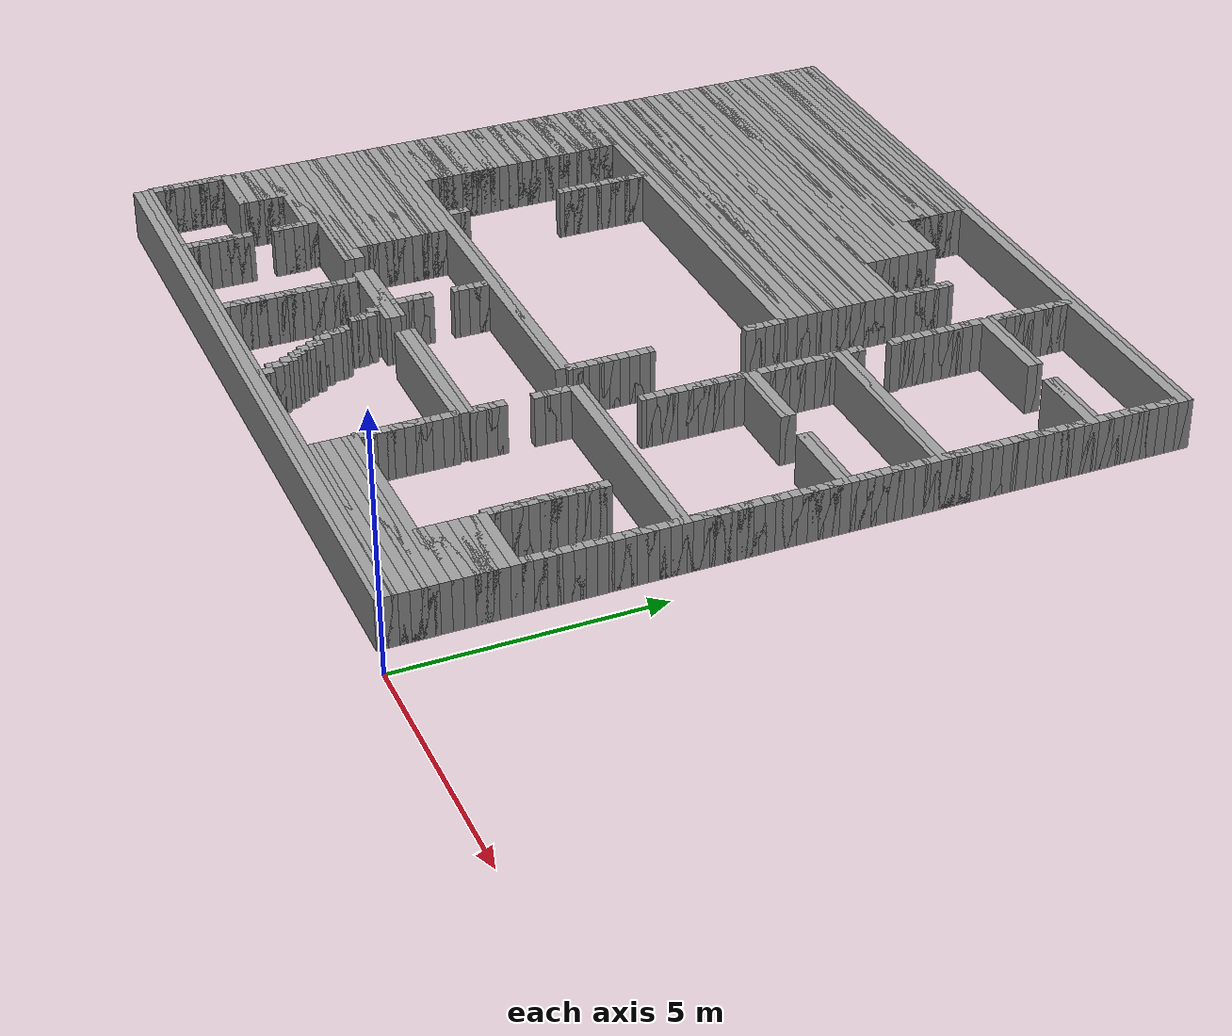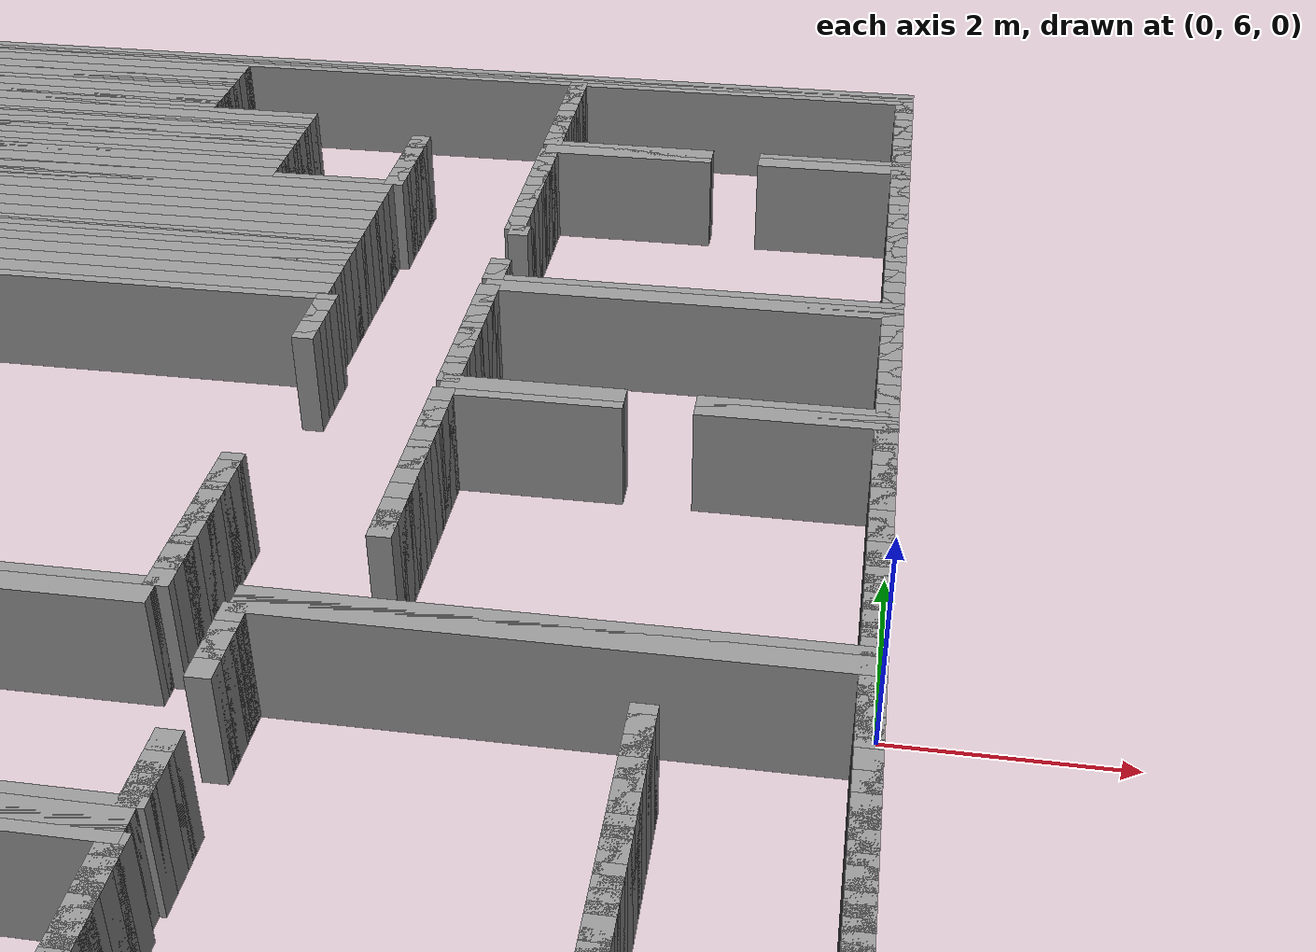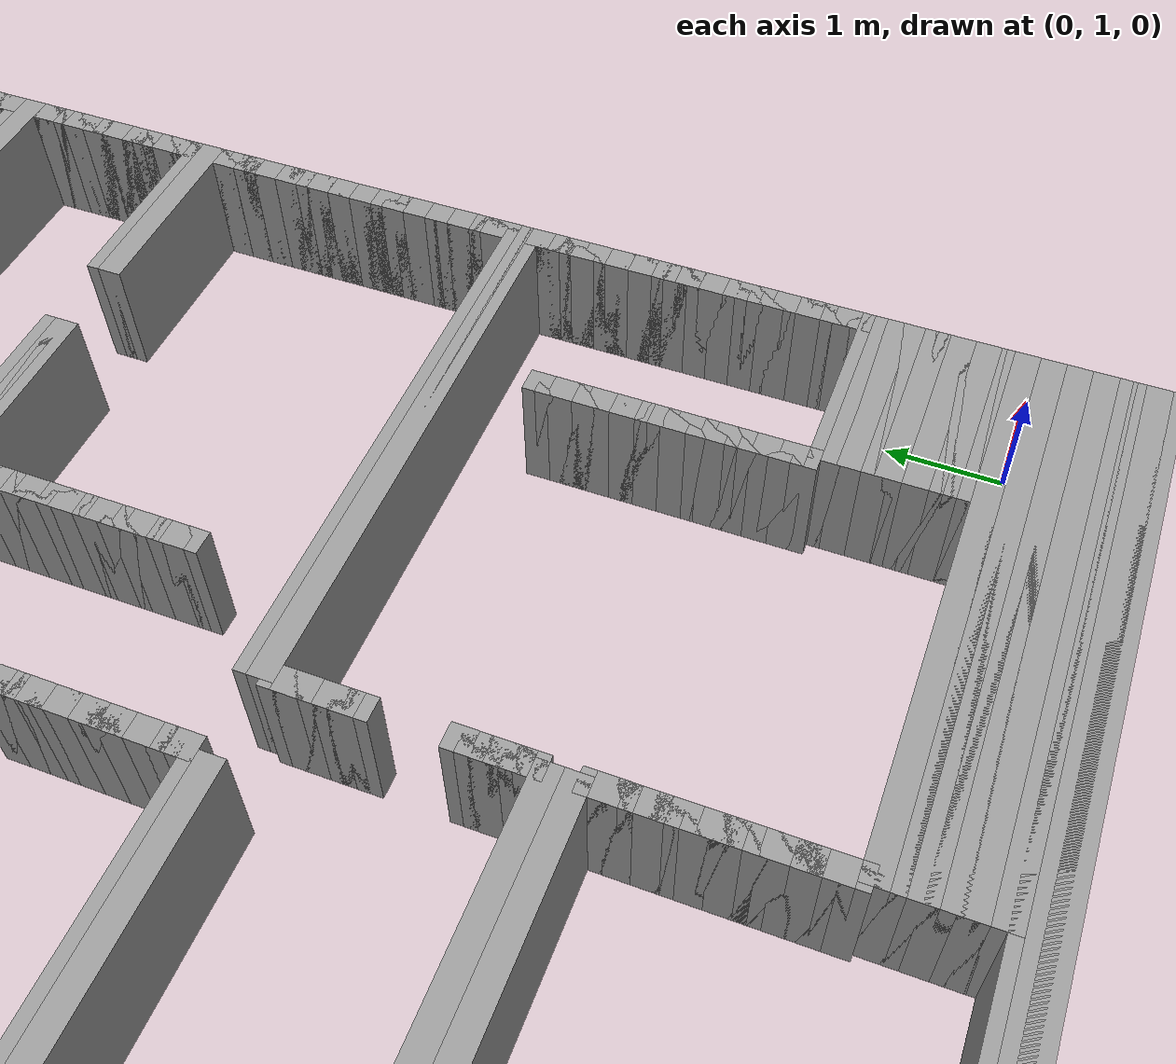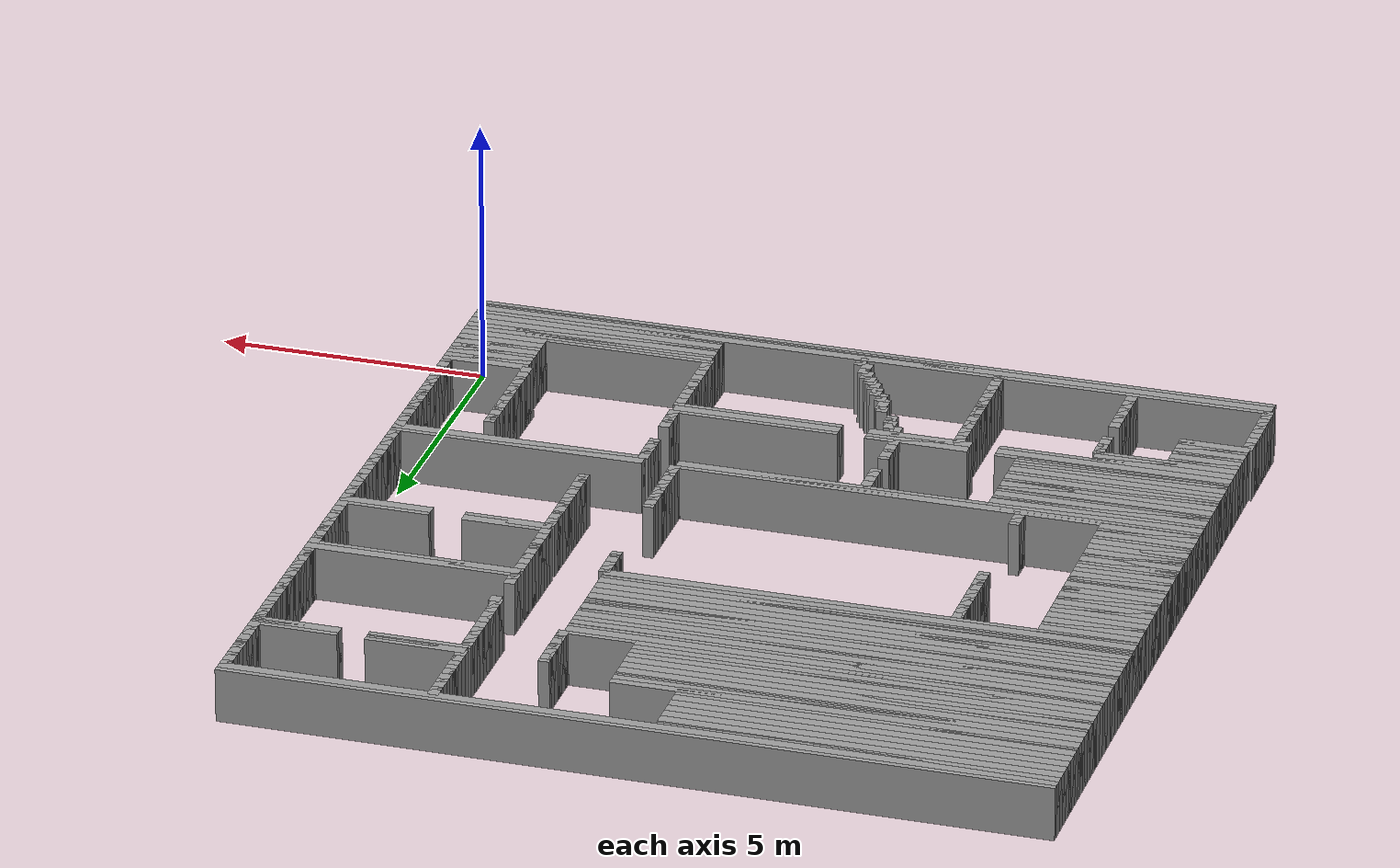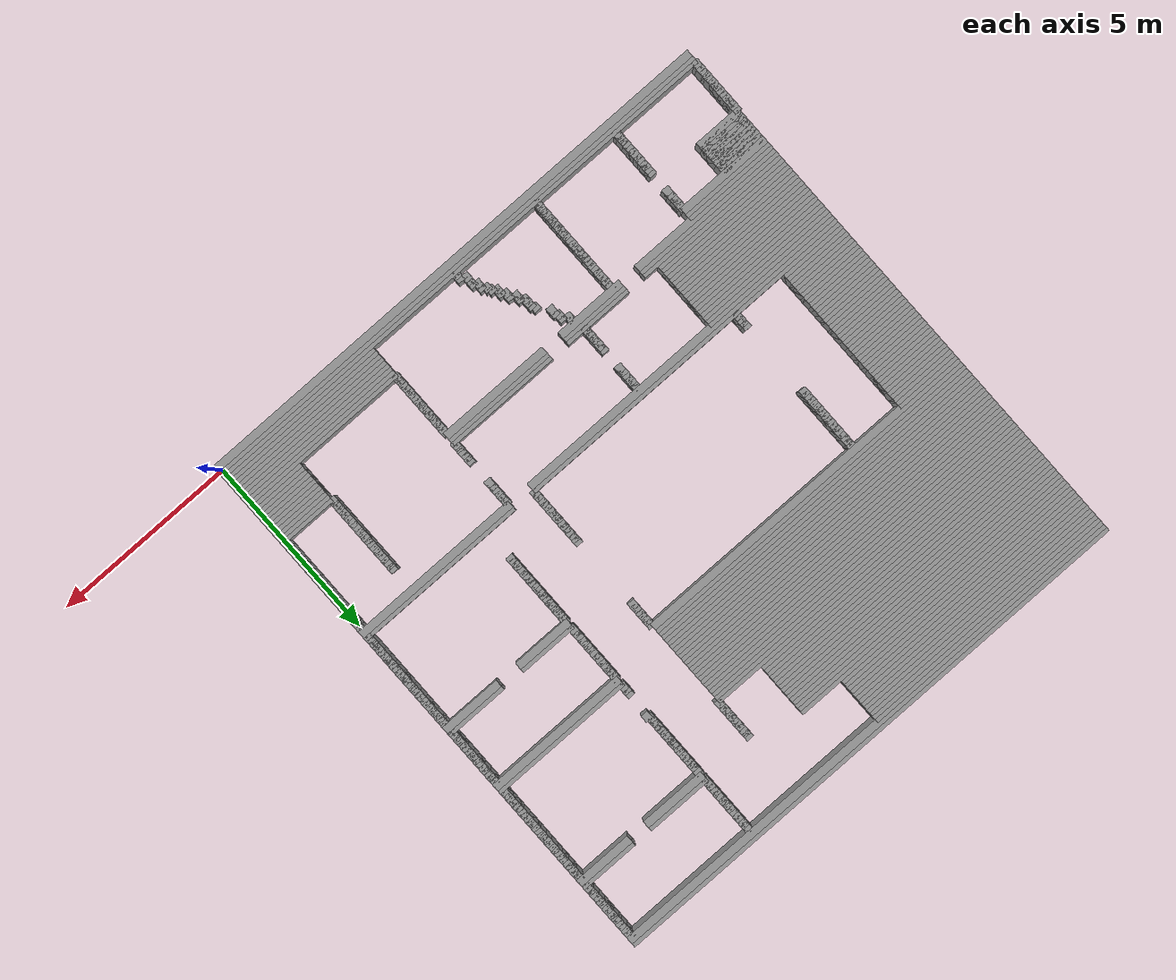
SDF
<?xml version='1.0' encoding='UTF-8'?>
<sdf version="1.6"><world name="GridMap"><model name="GridMap"><pose frame="">0 0 0 0 -0 0</pose><link name="Wall_(74.5,0.0)"><collision name="Wall_(74.5,0.0)_Collision"><geometry><box><size>14.9 0.2 1.0</size></box></geometry><pose frame="">-7.45 0.0 0.5 0 -0 0</pose></collision><visual name="Wall_(74.5,0.0)_Visual"><geometry><box><size>14.9 0.2 1.0</size></box></geometry><pose frame="">-7.45 0.0 0.5 0 -0 0</pose><material><script><uri>file://media/materials/scripts/gazebo.material</uri><name>Gazebo/Grey</name></script><ambient>1 1 1 1</ambient></material><meta><layer>0</layer></meta></visual><pose frame="">0 0 0.5 0 -0 0</pose></link><link name="Wall_(74.5,1.0)"><collision name="Wall_(74.5,1.0)_Collision"><geometry><box><size>14.9 0.2 1.0</size></box></geometry><pose frame="">-7.45 0.1 0.5 0 -0 0</pose></collision><visual name="Wall_(74.5,1.0)_Visual"><geometry><box><size>14.9 0.2 1.0</size></box></geometry><pose frame="">-7.45 0.1 0.5 0 -0 0</pose><material><script><uri>file://media/materials/scripts/gazebo.material</uri><name>Gazebo/Grey</name></script><ambient>1 1 1 1</ambient></material><meta><layer>0</layer></meta></visual><pose frame="">0 0 0.5 0 -0 0</pose></link><link name="Wall_(74.5,2.0)"><collision name="Wall_(74.5,2.0)_Collision"><geometry><box><size>14.9 0.2 1.0</size></box></geometry><pose frame="">-7.45 0.2 0.5 0 -0 0</pose></collision><visual name="Wall_(74.5,2.0)_Visual"><geometry><box><size>14.9 0.2 1.0</size></box></geometry><pose frame="">-7.45 0.2 0.5 0 -0 0</pose><material><script><uri>file://media/materials/scripts/gazebo.material</uri><name>Gazebo/Grey</name></script><ambient>1 1 1 1</ambient></material><meta><layer>0</layer></meta></visual><pose frame="">0 0 0.5 0 -0 0</pose></link><link name="Wall_(23.5,3.0)"><collision name="Wall_(23.5,3.0)_Collision"><geometry><box><size>4.7 0.2 1.0</size></box></geometry><pose frame="">-2.35 0.30000000000000004 0.5 0 -0 0</pose></collision><visual name="Wall_(23.5,3.0)_Visual"><geometry><box><size>4.7 0.2 1.0</size></box></geometry><pose frame="">-2.35 0.30000000000000004 0.5 0 -0 0</pose><material><script><uri>file://media/materials/scripts/gazebo.material</uri><name>Gazebo/Grey</name></script><ambient>1 1 1 1</ambient></material><meta><layer>0</layer></meta></visual><pose frame="">0 0 0.5 0 -0 0</pose></link><link name="Wall_(73.0,3.0)"><collision name="Wall_(73.0,3.0)_Collision"><geometry><box><size>0.2 0.2 1.0</size></box></geometry><pose frame="">-7.300000000000001 0.30000000000000004 0.5 0 -0 0</pose></collision><visual name="Wall_(73.0,3.0)_Visual"><geometry><box><size>0.2 0.2 1.0</size></box></geometry><pose frame="">-7.300000000000001 0.30000000000000004 0.5 0 -0 0</pose><material><script><uri>file://media/materials/scripts/gazebo.material</uri><name>Gazebo/Grey</name></script><ambient>1 1 1 1</ambient></material><meta><layer>0</layer></meta></visual><pose frame="">0 0 0.5 0 -0 0</pose></link><link name="Wall_(98.5,3.0)"><collision name="Wall_(98.5,3.0)_Collision"><geometry><box><size>0.2 0.2 1.0</size></box></geometry><pose frame="">-9.850000000000001 0.30000000000000004 0.5 0 -0 0</pose></collision><visual name="Wall_(98.5,3.0)_Visual"><geometry><box><size>0.2 0.2 1.0</size></box></geometry><pose frame="">-9.850000000000001 0.30000000000000004 0.5 0 -0 0</pose><material><script><uri>file://media/materials/scripts/gazebo.material</uri><name>Gazebo/Grey</name></script><ambient>1 1 1 1</ambient></material><meta><layer>0</layer></meta></visual><pose frame="">0 0 0.5 0 -0 0</pose></link><link name="Wall_(123.5,3.0)"><collision name="Wall_(123.5,3.0)_Collision"><geometry><box><size>0.2 0.2 1.0</size></box></geometry><pose frame="">-12.350000000000001 0.30000000000000004 0.5 0 -0 0</pose></collision><visual name="Wall_(123.5,3.0)_Visual"><geometry><box><size>0.2 0.2 1.0</size></box></geometry><pose frame="">-12.350000000000001 0.30000000000000004 0.5 0 -0 0</pose><material><script><uri>file://media/materials/scripts/gazebo.material</uri><name>Gazebo/Grey</name></script><ambient>1 1 1 1</ambient></material><meta><layer>0</layer></meta></visual><pose frame="">0 0 0.5 0 -0 0</pose></link><link name="Wall_(148.5,3.0)"><collision name="Wall_(148.5,3.0)_Collision"><geometry><box><size>0.2 0.2 1.0</size></box></geometry><pose frame="">-14.850000000000001 0.30000000000000004 0.5 0 -0 0</pose></collision><visual name="Wall_(148.5,3.0)_Visual"><geometry><box><size>0.2 0.2 1.0</size></box></geometry><pose frame="">-14.850000000000001 0.30000000000000004 0.5 0 -0 0</pose><material><script><uri>file://media/materials/scripts/gazebo.material</uri><name>Gazebo/Grey</name></script><ambient>1 1 1 1</ambient></material><meta><layer>0</layer></meta></visual><pose frame="">0 0 0.5 0 -0 0</pose></link><link name="Wall_(23.5,4.0)"><collision name="Wall_(23.5,4.0)_Collision"><geometry><box><size>4.7 0.2 1.0</size></box></geometry><pose frame="">-2.35 0.4 0.5 0 -0 0</pose></collision><visual name="Wall_(23.5,4.0)_Visual"><geometry><box><size>4.7 0.2 1.0</size></box></geometry><pose frame="">-2.35 0.4 0.5 0 -0 0</pose><material><script><uri>file://media/materials/scripts/gazebo.material</uri><name>Gazebo/Grey</name></script><ambient>1 1 1 1</ambient></material><meta><layer>0</layer></meta></visual><pose frame="">0 0 0.5 0 -0 0</pose></link><link name="Wall_(73.0,4.0)"><collision name="Wall_(73.0,4.0)_Collision"><geometry><box><size>0.2 0.2 1.0</size></box></geometry><pose frame="">-7.300000000000001 0.4 0.5 0 -0 0</pose></collision><visual name="Wall_(73.0,4.0)_Visual"><geometry><box><size>0.2 0.2 1.0</size></box></geometry><pose frame="">-7.300000000000001 0.4 0.5 0 -0 0</pose><material><script><uri>file://media/materials/scripts/gazebo.material</uri><name>Gazebo/Grey</name></script><ambient>1 1 1 1</ambient></material><meta><layer>0</layer></meta></visual><pose frame="">0 0 0.5 0 -0 0</pose></link><link name="Wall_(98.5,4.0)"><collision name="Wall_(98.5,4.0)_Collision"><geometry><box><size>0.2 0.2 1.0</size></box></geometry><pose frame="">-9.850000000000001 0.4 0.5 0 -0 0</pose></collision><visual name="Wall_(98.5,4.0)_Visual"><geometry><box><size>0.2 0.2 1.0</size></box></geometry><pose frame="">-9.850000000000001 0.4 0.5 0 -0 0</pose><material><script><uri>file://media/materials/scripts/gazebo.material</uri><name>Gazebo/Grey</name></script><ambient>1 1 1 1</ambient></material><meta><layer>0</layer></meta></visual><pose frame="">0 0 0.5 0 -0 0</pose></link><link name="Wall_(123.5,4.0)"><collision name="Wall_(123.5,4.0)_Collision"><geometry><box><size>0.2 0.2 1.0</size></box></geometry><pose frame="">-12.350000000000001 0.4 0.5 0 -0 0</pose></collision><visual name="Wall_(123.5,4.0)_Visual"><geometry><box><size>0.2 0.2 1.0</size></box></geometry><pose frame="">-12.350000000000001 0.4 0.5 0 -0 0</pose><material><script><uri>file://media/materials/scripts/gazebo.material</uri><name>Gazebo/Grey</name></script><ambient>1 1 1 1</ambient></material><meta><layer>0</layer></meta></visual><pose frame="">0 0 0.5 0 -0 0</pose></link><link name="Wall_(148.5,4.0)"><collision name="Wall_(148.5,4.0)_Collision"><geometry><box><size>0.2 0.2 1.0</size></box></geometry><pose frame="">-14.850000000000001 0.4 0.5 0 -0 0</pose></collision><visual name="Wall_(148.5,4.0)_Visual"><geometry><box><size>0.2 0.2 1.0</size></box></geometry><pose frame="">-14.850000000000001 0.4 0.5 0 -0 0</pose><material><script><uri>file://media/materials/scripts/gazebo.material</uri><name>Gazebo/Grey</name></script><ambient>1 1 1 1</ambient></material><meta><layer>0</layer></meta></visual><pose frame="">0 0 0.5 0 -0 0</pose></link><link name="Wall_(23.5,5.0)"><collision name="Wall_(23.5,5.0)_Collision"><geometry><box><size>4.7 0.2 1.0</size></box></geometry><pose frame="">-2.35 0.5 0.5 0 -0 0</pose></collision><visual name="Wall_(23.5,5.0)_Visual"><geometry><box><size>4.7 0.2 1.0</size></box></geometry><pose frame="">-2.35 0.5 0.5 0 -0 0</pose><material><script><uri>file://media/materials/scripts/gazebo.material</uri><name>Gazebo/Grey</name></script><ambient>1 1 1 1</ambient></material><meta><layer>0</layer></meta></visual><pose frame="">0 0 0.5 0 -0 0</pose></link><link name="Wall_(74.5,5.0)"><collision name="Wall_(74.5,5.0)_Collision"><geometry><box><size>0.2 0.2 1.0</size></box></geometry><pose frame="">-7.45 0.5 0.5 0 -0 0</pose></collision><visual name="Wall_(74.5,5.0)_Visual"><geometry><box><size>0.2 0.2 1.0</size></box></geometry><pose frame="">-7.45 0.5 0.5 0 -0 0</pose><material><script><uri>file://media/materials/scripts/gazebo.material</uri><name>Gazebo/Grey</name></script><ambient>1 1 1 1</ambient></material><meta><layer>0</layer></meta></visual><pose frame="">0 0 0.5 0 -0 0</pose></link><link name="Wall_(98.5,5.0)"><collision name="Wall_(98.5,5.0)_Collision"><geometry><box><size>0.2 0.2 1.0</size></box></geometry><pose frame="">-9.850000000000001 0.5 0.5 0 -0 0</pose></collision><visual name="Wall_(98.5,5.0)_Visual"><geometry><box><size>0.2 0.2 1.0</size></box></geometry><pose frame="">-9.850000000000001 0.5 0.5 0 -0 0</pose><material><script><uri>file://media/materials/scripts/gazebo.material</uri><name>Gazebo/Grey</name></script><ambient>1 1 1 1</ambient></material><meta><layer>0</layer></meta></visual><pose frame="">0 0 0.5 0 -0 0</pose></link><link name="Wall_(123.5,5.0)"><collision name="Wall_(123.5,5.0)_Collision"><geometry><box><size>0.2 0.2 1.0</size></box></geometry><pose frame="">-12.350000000000001 0.5 0.5 0 -0 0</pose></collision><visual name="Wall_(123.5,5.0)_Visual"><geometry><box><size>0.2 0.2 1.0</size></box></geometry><pose frame="">-12.350000000000001 0.5 0.5 0 -0 0</pose><material><script><uri>file://media/materials/scripts/gazebo.material</uri><name>Gazebo/Grey</name></script><ambient>1 1 1 1</ambient></material><meta><layer>0</layer></meta></visual><pose frame="">0 0 0.5 0 -0 0</pose></link><link name="Wall_(148.5,5.0)"><collision name="Wall_(148.5,5.0)_Collision"><geometry><box><size>0.2 0.2 1.0</size></box></geometry><pose frame="">-14.850000000000001 0.5 0.5 0 -0 0</pose></collision><visual name="Wall_(148.5,5.0)_Visual"><geometry><box><size>0.2 0.2 1.0</size></box></geometry><pose frame="">-14.850000000000001 0.5 0.5 0 -0 0</pose><material><script><uri>file://media/materials/scripts/gazebo.material</uri><name>Gazebo/Grey</name></script><ambient>1 1 1 1</ambient></material><meta><layer>0</layer></meta></visual><pose frame="">0 0 0.5 0 -0 0</pose></link><link name="Wall_(23.5,6.0)"><collision name="Wall_(23.5,6.0)_Collision"><geometry><box><size>4.7 0.2 1.0</size></box></geometry><pose frame="">-2.35 0.6000000000000001 0.5 0 -0 0</pose></collision><visual name="Wall_(23.5,6.0)_Visual"><geometry><box><size>4.7 0.2 1.0</size></box></geometry><pose frame="">-2.35 0.6000000000000001 0.5 0 -0 0</pose><material><script><uri>file://media/materials/scripts/gazebo.material</uri><name>Gazebo/Grey</name></script><ambient>1 1 1 1</ambient></material><meta><layer>0</layer></meta></visual><pose frame="">0 0 0.5 0 -0 0</pose></link><link name="Wall_(74.5,6.0)"><collision name="Wall_(74.5,6.0)_Collision"><geometry><box><size>0.2 0.2 1.0</size></box></geometry><pose frame="">-7.45 0.6000000000000001 0.5 0 -0 0</pose></collision><visual name="Wall_(74.5,6.0)_Visual"><geometry><box><size>0.2 0.2 1.0</size></box></geometry><pose frame="">-7.45 0.6000000000000001 0.5 0 -0 0</pose><material><script><uri>file://media/materials/scripts/gazebo.material</uri><name>Gazebo/Grey</name></script><ambient>1 1 1 1</ambient></material><meta><layer>0</layer></meta></visual><pose frame="">0 0 0.5 0 -0 0</pose></link><link name="Wall_(98.5,6.0)"><collision name="Wall_(98.5,6.0)_Collision"><geometry><box><size>0.2 0.2 1.0</size></box></geometry><pose frame="">-9.850000000000001 0.6000000000000001 0.5 0 -0 0</pose></collision><visual name="Wall_(98.5,6.0)_Visual"><geometry><box><size>0.2 0.2 1.0</size></box></geometry><pose frame="">-9.850000000000001 0.6000000000000001 0.5 0 -0 0</pose><material><script><uri>file://media/materials/scripts/gazebo.material</uri><name>Gazebo/Grey</name></script><ambient>1 1 1 1</ambient></material><meta><layer>0</layer></meta></visual><pose frame="">0 0 0.5 0 -0 0</pose></link><link name="Wall_(123.5,6.0)"><collision name="Wall_(123.5,6.0)_Collision"><geometry><box><size>0.2 0.2 1.0</size></box></geometry><pose frame="">-12.350000000000001 0.6000000000000001 0.5 0 -0 0</pose></collision><visual name="Wall_(123.5,6.0)_Visual"><geometry><box><size>0.2 0.2 1.0</size></box></geometry><pose frame="">-12.350000000000001 0.6000000000000001 0.5 0 -0 0</pose><material><script><uri>file://media/materials/scripts/gazebo.material</uri><name>Gazebo/Grey</name></script><ambient>1 1 1 1</ambient></material><meta><layer>0</layer></meta></visual><pose frame="">0 0 0.5 0 -0 0</pose></link><link name="Wall_(148.5,6.0)"><collision name="Wall_(148.5,6.0)_Collision"><geometry><box><size>0.2 0.2 1.0</size></box></geometry><pose frame="">-14.850000000000001 0.6000000000000001 0.5 0 -0 0</pose></collision><visual name="Wall_(148.5,6.0)_Visual"><geometry><box><size>0.2 0.2 1.0</size></box></geometry><pose frame="">-14.850000000000001 0.6000000000000001 0.5 0 -0 0</pose><material><script><uri>file://media/materials/scripts/gazebo.material</uri><name>Gazebo/Grey</name></script><ambient>1 1 1 1</ambient></material><meta><layer>0</layer></meta></visual><pose frame="">0 0 0.5 0 -0 0</pose></link><link name="Wall_(23.5,7.0)"><collision name="Wall_(23.5,7.0)_Collision"><geometry><box><size>4.7 0.2 1.0</size></box></geometry><pose frame="">-2.35 0.7000000000000001 0.5 0 -0 0</pose></collision><visual name="Wall_(23.5,7.0)_Visual"><geometry><box><size>4.7 0.2 1.0</size></box></geometry><pose frame="">-2.35 0.7000000000000001 0.5 0 -0 0</pose><material><script><uri>file://media/materials/scripts/gazebo.material</uri><name>Gazebo/Grey</name></script><ambient>1 1 1 1</ambient></material><meta><layer>0</layer></meta></visual><pose frame="">0 0 0.5 0 -0 0</pose></link><link name="Wall_(74.5,7.0)"><collision name="Wall_(74.5,7.0)_Collision"><geometry><box><size>0.2 0.2 1.0</size></box></geometry><pose frame="">-7.45 0.7000000000000001 0.5 0 -0 0</pose></collision><visual name="Wall_(74.5,7.0)_Visual"><geometry><box><size>0.2 0.2 1.0</size></box></geometry><pose frame="">-7.45 0.7000000000000001 0.5 0 -0 0</pose><material><script><uri>file://media/materials/scripts/gazebo.material</uri><name>Gazebo/Grey</name></script><ambient>1 1 1 1</ambient></material><meta><layer>0</layer></meta></visual><pose frame="">0 0 0.5 0 -0 0</pose></link><link name="Wall_(98.5,7.0)"><collision name="Wall_(98.5,7.0)_Collision"><geometry><box><size>0.2 0.2 1.0</size></box></geometry><pose frame="">-9.850000000000001 0.7000000000000001 0.5 0 -0 0</pose></collision><visual name="Wall_(98.5,7.0)_Visual"><geometry><box><size>0.2 0.2 1.0</size></box></geometry><pose frame="">-9.850000000000001 0.7000000000000001 0.5 0 -0 0</pose><material><script><uri>file://media/materials/scripts/gazebo.material</uri><name>Gazebo/Grey</name></script><ambient>1 1 1 1</ambient></material><meta><layer>0</layer></meta></visual><pose frame="">0 0 0.5 0 -0 0</pose></link><link name="Wall_(123.5,7.0)"><collision name="Wall_(123.5,7.0)_Collision"><geometry><box><size>0.2 0.2 1.0</size></box></geometry><pose frame="">-12.350000000000001 0.7000000000000001 0.5 0 -0 0</pose></collision><visual name="Wall_(123.5,7.0)_Visual"><geometry><box><size>0.2 0.2 1.0</size></box></geometry><pose frame="">-12.350000000000001 0.7000000000000001 0.5 0 -0 0</pose><material><script><uri>file://media/materials/scripts/gazebo.material</uri><name>Gazebo/Grey</name></script><ambient>1 1 1 1</ambient></material><meta><layer>0</layer></meta></visual><pose frame="">0 0 0.5 0 -0 0</pose></link><link name="Wall_(148.5,7.0)"><collision name="Wall_(148.5,7.0)_Collision"><geometry><box><size>0.2 0.2 1.0</size></box></geometry><pose frame="">-14.850000000000001 0.7000000000000001 0.5 0 -0 0</pose></collision><visual name="Wall_(148.5,7.0)_Visual"><geometry><box><size>0.2 0.2 1.0</size></box></geometry><pose frame="">-14.850000000000001 0.7000000000000001 0.5 0 -0 0</pose><material><script><uri>file://media/materials/scripts/gazebo.material</uri><name>Gazebo/Grey</name></script><ambient>1 1 1 1</ambient></material><meta><layer>0</layer></meta></visual><pose frame="">0 0 0.5 0 -0 0</pose></link><link name="Wall_(23.5,8.0)"><collision name="Wall_(23.5,8.0)_Collision"><geometry><box><size>4.7 0.2 1.0</size></box></geometry><pose frame="">-2.35 0.8 0.5 0 -0 0</pose></collision><visual name="Wall_(23.5,8.0)_Visual"><geometry><box><size>4.7 0.2 1.0</size></box></geometry><pose frame="">-2.35 0.8 0.5 0 -0 0</pose><material><script><uri>file://media/materials/scripts/gazebo.material</uri><name>Gazebo/Grey</name></script><ambient>1 1 1 1</ambient></material><meta><layer>0</layer></meta></visual><pose frame="">0 0 0.5 0 -0 0</pose></link><link name="Wall_(75.5,8.0)"><collision name="Wall_(75.5,8.0)_Collision"><geometry><box><size>0.2 0.2 1.0</size></box></geometry><pose frame="">-7.550000000000001 0.8 0.5 0 -0 0</pose></collision><visual name="Wall_(75.5,8.0)_Visual"><geometry><box><size>0.2 0.2 1.0</size></box></geometry><pose frame="">-7.550000000000001 0.8 0.5 0 -0 0</pose><material><script><uri>file://media/materials/scripts/gazebo.material</uri><name>Gazebo/Grey</name></script><ambient>1 1 1 1</ambient></material><meta><layer>0</layer></meta></visual><pose frame="">0 0 0.5 0 -0 0</pose></link><link name="Wall_(98.5,8.0)"><collision name="Wall_(98.5,8.0)_Collision"><geometry><box><size>0.2 0.2 1.0</size></box></geometry><pose frame="">-9.850000000000001 0.8 0.5 0 -0 0</pose></collision><visual name="Wall_(98.5,8.0)_Visual"><geometry><box><size>0.2 0.2 1.0</size></box></geometry><pose frame="">-9.850000000000001 0.8 0.5 0 -0 0</pose><material><script><uri>file://media/materials/scripts/gazebo.material</uri><name>Gazebo/Grey</name></script><ambient>1 1 1 1</ambient></material><meta><layer>0</layer></meta></visual><pose frame="">0 0 0.5 0 -0 0</pose></link><link name="Wall_(123.5,8.0)"><collision name="Wall_(123.5,8.0)_Collision"><geometry><box><size>0.2 0.2 1.0</size></box></geometry><pose frame="">-12.350000000000001 0.8 0.5 0 -0 0</pose></collision><visual name="Wall_(123.5,8.0)_Visual"><geometry><box><size>0.2 0.2 1.0</size></box></geometry><pose frame="">-12.350000000000001 0.8 0.5 0 -0 0</pose><material><script><uri>file://media/materials/scripts/gazebo.material</uri><name>Gazebo/Grey</name></script><ambient>1 1 1 1</ambient></material><meta><layer>0</layer></meta></visual><pose frame="">0 0 0.5 0 -0 0</pose></link><link name="Wall_(148.5,8.0)"><collision name="Wall_(148.5,8.0)_Collision"><geometry><box><size>0.2 0.2 1.0</size></box></geometry><pose frame="">-14.850000000000001 0.8 0.5 0 -0 0</pose></collision><visual name="Wall_(148.5,8.0)_Visual"><geometry><box><size>0.2 0.2 1.0</size></box></geometry><pose frame="">-14.850000000000001 0.8 0.5 0 -0 0</pose><material><script><uri>file://media/materials/scripts/gazebo.material</uri><name>Gazebo/Grey</name></script><ambient>1 1 1 1</ambient></material><meta><layer>0</layer></meta></visual><pose frame="">0 0 0.5 0 -0 0</pose></link><link name="Wall_(23.5,9.0)"><collision name="Wall_(23.5,9.0)_Collision"><geometry><box><size>4.7 0.2 1.0</size></box></geometry><pose frame="">-2.35 0.9 0.5 0 -0 0</pose></collision><visual name="Wall_(23.5,9.0)_Visual"><geometry><box><size>4.7 0.2 1.0</size></box></geometry><pose frame="">-2.35 0.9 0.5 0 -0 0</pose><material><script><uri>file://media/materials/scripts/gazebo.material</uri><name>Gazebo/Grey</name></script><ambient>1 1 1 1</ambient></material><meta><layer>0</layer></meta></visual><pose frame="">0 0 0.5 0 -0 0</pose></link><link name="Wall_(75.5,9.0)"><collision name="Wall_(75.5,9.0)_Collision"><geometry><box><size>0.2 0.2 1.0</size></box></geometry><pose frame="">-7.550000000000001 0.9 0.5 0 -0 0</pose></collision><visual name="Wall_(75.5,9.0)_Visual"><geometry><box><size>0.2 0.2 1.0</size></box></geometry><pose frame="">-7.550000000000001 0.9 0.5 0 -0 0</pose><material><script><uri>file://media/materials/scripts/gazebo.material</uri><name>Gazebo/Grey</name></script><ambient>1 1 1 1</ambient></material><meta><layer>0</layer></meta></visual><pose frame="">0 0 0.5 0 -0 0</pose></link><link name="Wall_(98.5,9.0)"><collision name="Wall_(98.5,9.0)_Collision"><geometry><box><size>0.2 0.2 1.0</size></box></geometry><pose frame="">-9.850000000000001 0.9 0.5 0 -0 0</pose></collision><visual name="Wall_(98.5,9.0)_Visual"><geometry><box><size>0.2 0.2 1.0</size></box></geometry><pose frame="">-9.850000000000001 0.9 0.5 0 -0 0</pose><material><script><uri>file://media/materials/scripts/gazebo.material</uri><name>Gazebo/Grey</name></script><ambient>1 1 1 1</ambient></material><meta><layer>0</layer></meta></visual><pose frame="">0 0 0.5 0 -0 0</pose></link><link name="Wall_(123.5,9.0)"><collision name="Wall_(123.5,9.0)_Collision"><geometry><box><size>0.2 0.2 1.0</size></box></geometry><pose frame="">-12.350000000000001 0.9 0.5 0 -0 0</pose></collision><visual name="Wall_(123.5,9.0)_Visual"><geometry><box><size>0.2 0.2 1.0</size></box></geometry><pose frame="">-12.350000000000001 0.9 0.5 0 -0 0</pose><material><script><uri>file://media/materials/scripts/gazebo.material</uri><name>Gazebo/Grey</name></script><ambient>1 1 1 1</ambient></material><meta><layer>0</layer></meta></visual><pose frame="">0 0 0.5 0 -0 0</pose></link><link name="Wall_(148.5,9.0)"><collision name="Wall_(148.5,9.0)_Collision"><geometry><box><size>0.2 0.2 1.0</size></box></geometry><pose frame="">-14.850000000000001 0.9 0.5 0 -0 0</pose></collision><visual name="Wall_(148.5,9.0)_Visual"><geometry><box><size>0.2 0.2 1.0</size></box></geometry><pose frame="">-14.850000000000001 0.9 0.5 0 -0 0</pose><material><script><uri>file://media/materials/scripts/gazebo.material</uri><name>Gazebo/Grey</name></script><ambient>1 1 1 1</ambient></material><meta><layer>0</layer></meta></visual><pose frame="">0 0 0.5 0 -0 0</pose></link><link name="Wall_(23.5,10.0)"><collision name="Wall_(23.5,10.0)_Collision"><geometry><box><size>4.7 0.2 1.0</size></box></geometry><pose frame="">-2.35 1.0 0.5 0 -0 0</pose></collision><visual name="Wall_(23.5,10.0)_Visual"><geometry><box><size>4.7 0.2 1.0</size></box></geometry><pose frame="">-2.35 1.0 0.5 0 -0 0</pose><material><script><uri>file://media/materials/scripts/gazebo.material</uri><name>Gazebo/Grey</name></script><ambient>1 1 1 1</ambient></material><meta><layer>0</layer></meta></visual><pose frame="">0 0 0.5 0 -0 0</pose></link><link name="Wall_(76.5,10.0)"><collision name="Wall_(76.5,10.0)_Collision"><geometry><box><size>0.2 0.2 1.0</size></box></geometry><pose frame="">-7.65 1.0 0.5 0 -0 0</pose></collision><visual name="Wall_(76.5,10.0)_Visual"><geometry><box><size>0.2 0.2 1.0</size></box></geometry><pose frame="">-7.65 1.0 0.5 0 -0 0</pose><material><script><uri>file://media/materials/scripts/gazebo.material</uri><name>Gazebo/Grey</name></script><ambient>1 1 1 1</ambient></material><meta><layer>0</layer></meta></visual><pose frame="">0 0 0.5 0 -0 0</pose></link><link name="Wall_(98.5,10.0)"><collision name="Wall_(98.5,10.0)_Collision"><geometry><box><size>0.2 0.2 1.0</size></box></geometry><pose frame="">-9.850000000000001 1.0 0.5 0 -0 0</pose></collision><visual name="Wall_(98.5,10.0)_Visual"><geometry><box><size>0.2 0.2 1.0</size></box></geometry><pose frame="">-9.850000000000001 1.0 0.5 0 -0 0</pose><material><script><uri>file://media/materials/scripts/gazebo.material</uri><name>Gazebo/Grey</name></script><ambient>1 1 1 1</ambient></material><meta><layer>0</layer></meta></visual><pose frame="">0 0 0.5 0 -0 0</pose></link><link name="Wall_(123.5,10.0)"><collision name="Wall_(123.5,10.0)_Collision"><geometry><box><size>0.2 0.2 1.0</size></box></geometry><pose frame="">-12.350000000000001 1.0 0.5 0 -0 0</pose></collision><visual name="Wall_(123.5,10.0)_Visual"><geometry><box><size>0.2 0.2 1.0</size></box></geometry><pose frame="">-12.350000000000001 1.0 0.5 0 -0 0</pose><material><script><uri>file://media/materials/scripts/gazebo.material</uri><name>Gazebo/Grey</name></script><ambient>1 1 1 1</ambient></material><meta><layer>0</layer></meta></visual><pose frame="">0 0 0.5 0 -0 0</pose></link><link name="Wall_(148.5,10.0)"><collision name="Wall_(148.5,10.0)_Collision"><geometry><box><size>0.2 0.2 1.0</size></box></geometry><pose frame="">-14.850000000000001 1.0 0.5 0 -0 0</pose></collision><visual name="Wall_(148.5,10.0)_Visual"><geometry><box><size>0.2 0.2 1.0</size></box></geometry><pose frame="">-14.850000000000001 1.0 0.5 0 -0 0</pose><material><script><uri>file://media/materials/scripts/gazebo.material</uri><name>Gazebo/Grey</name></script><ambient>1 1 1 1</ambient></material><meta><layer>0</layer></meta></visual><pose frame="">0 0 0.5 0 -0 0</pose></link><link name="Wall_(23.5,11.0)"><collision name="Wall_(23.5,11.0)_Collision"><geometry><box><size>4.7 0.2 1.0</size></box></geometry><pose frame="">-2.35 1.1 0.5 0 -0 0</pose></collision><visual name="Wall_(23.5,11.0)_Visual"><geometry><box><size>4.7 0.2 1.0</size></box></geometry><pose frame="">-2.35 1.1 0.5 0 -0 0</pose><material><script><uri>file://media/materials/scripts/gazebo.material</uri><name>Gazebo/Grey</name></script><ambient>1 1 1 1</ambient></material><meta><layer>0</layer></meta></visual><pose frame="">0 0 0.5 0 -0 0</pose></link><link name="Wall_(77.0,11.0)"><collision name="Wall_(77.0,11.0)_Collision"><geometry><box><size>0.2 0.2 1.0</size></box></geometry><pose frame="">-7.7 1.1 0.5 0 -0 0</pose></collision><visual name="Wall_(77.0,11.0)_Visual"><geometry><box><size>0.2 0.2 1.0</size></box></geometry><pose frame="">-7.7 1.1 0.5 0 -0 0</pose><material><script><uri>file://media/materials/scripts/gazebo.material</uri><name>Gazebo/Grey</name></script><ambient>1 1 1 1</ambient></material><meta><layer>0</layer></meta></visual><pose frame="">0 0 0.5 0 -0 0</pose></link><link name="Wall_(98.5,11.0)"><collision name="Wall_(98.5,11.0)_Collision"><geometry><box><size>0.2 0.2 1.0</size></box></geometry><pose frame="">-9.850000000000001 1.1 0.5 0 -0 0</pose></collision><visual name="Wall_(98.5,11.0)_Visual"><geometry><box><size>0.2 0.2 1.0</size></box></geometry><pose frame="">-9.850000000000001 1.1 0.5 0 -0 0</pose><material><script><uri>file://media/materials/scripts/gazebo.material</uri><name>Gazebo/Grey</name></script><ambient>1 1 1 1</ambient></material><meta><layer>0</layer></meta></visual><pose frame="">0 0 0.5 0 -0 0</pose></link><link name="Wall_(123.5,11.0)"><collision name="Wall_(123.5,11.0)_Collision"><geometry><box><size>0.2 0.2 1.0</size></box></geometry><pose frame="">-12.350000000000001 1.1 0.5 0 -0 0</pose></collision><visual name="Wall_(123.5,11.0)_Visual"><geometry><box><size>0.2 0.2 1.0</size></box></geometry><pose frame="">-12.350000000000001 1.1 0.5 0 -0 0</pose><material><script><uri>file://media/materials/scripts/gazebo.material</uri><name>Gazebo/Grey</name></script><ambient>1 1 1 1</ambient></material><meta><layer>0</layer></meta></visual><pose frame="">0 0 0.5 0 -0 0</pose></link><link name="Wall_(148.5,11.0)"><collision name="Wall_(148.5,11.0)_Collision"><geometry><box><size>0.2 0.2 1.0</size></box></geometry><pose frame="">-14.850000000000001 1.1 0.5 0 -0 0</pose></collision><visual name="Wall_(148.5,11.0)_Visual"><geometry><box><size>0.2 0.2 1.0</size></box></geometry><pose frame="">-14.850000000000001 1.1 0.5 0 -0 0</pose><material><script><uri>file://media/materials/scripts/gazebo.material</uri><name>Gazebo/Grey</name></script><ambient>1 1 1 1</ambient></material><meta><layer>0</layer></meta></visual><pose frame="">0 0 0.5 0 -0 0</pose></link><link name="Wall_(8.0,12.0)"><collision name="Wall_(8.0,12.0)_Collision"><geometry><box><size>1.6 0.2 1.0</size></box></geometry><pose frame="">-0.8 1.2000000000000002 0.5 0 -0 0</pose></collision><visual name="Wall_(8.0,12.0)_Visual"><geometry><box><size>1.6 0.2 1.0</size></box></geometry><pose frame="">-0.8 1.2000000000000002 0.5 0 -0 0</pose><material><script><uri>file://media/materials/scripts/gazebo.material</uri><name>Gazebo/Grey</name></script><ambient>1 1 1 1</ambient></material><meta><layer>0</layer></meta></visual><pose frame="">0 0 0.5 0 -0 0</pose></link><link name="Wall_(46.5,12.0)"><collision name="Wall_(46.5,12.0)_Collision"><geometry><box><size>0.2 0.2 1.0</size></box></geometry><pose frame="">-4.65 1.2000000000000002 0.5 0 -0 0</pose></collision><visual name="Wall_(46.5,12.0)_Visual"><geometry><box><size>0.2 0.2 1.0</size></box></geometry><pose frame="">-4.65 1.2000000000000002 0.5 0 -0 0</pose><material><script><uri>file://media/materials/scripts/gazebo.material</uri><name>Gazebo/Grey</name></script><ambient>1 1 1 1</ambient></material><meta><layer>0</layer></meta></visual><pose frame="">0 0 0.5 0 -0 0</pose></link><link name="Wall_(78.0,12.0)"><collision name="Wall_(78.0,12.0)_Collision"><geometry><box><size>0.2 0.2 1.0</size></box></geometry><pose frame="">-7.800000000000001 1.2000000000000002 0.5 0 -0 0</pose></collision><visual name="Wall_(78.0,12.0)_Visual"><geometry><box><size>0.2 0.2 1.0</size></box></geometry><pose frame="">-7.800000000000001 1.2000000000000002 0.5 0 -0 0</pose><material><script><uri>file://media/materials/scripts/gazebo.material</uri><name>Gazebo/Grey</name></script><ambient>1 1 1 1</ambient></material><meta><layer>0</layer></meta></visual><pose frame="">0 0 0.5 0 -0 0</pose></link><link name="Wall_(98.5,12.0)"><collision name="Wall_(98.5,12.0)_Collision"><geometry><box><size>0.2 0.2 1.0</size></box></geometry><pose frame="">-9.850000000000001 1.2000000000000002 0.5 0 -0 0</pose></collision><visual name="Wall_(98.5,12.0)_Visual"><geometry><box><size>0.2 0.2 1.0</size></box></geometry><pose frame="">-9.850000000000001 1.2000000000000002 0.5 0 -0 0</pose><material><script><uri>file://media/materials/scripts/gazebo.material</uri><name>Gazebo/Grey</name></script><ambient>1 1 1 1</ambient></material><meta><layer>0</layer></meta></visual><pose frame="">0 0 0.5 0 -0 0</pose></link><link name="Wall_(123.5,12.0)"><collision name="Wall_(123.5,12.0)_Collision"><geometry><box><size>0.2 0.2 1.0</size></box></geometry><pose frame="">-12.350000000000001 1.2000000000000002 0.5 0 -0 0</pose></collision><visual name="Wall_(123.5,12.0)_Visual"><geometry><box><size>0.2 0.2 1.0</size></box></geometry><pose frame="">-12.350000000000001 1.2000000000000002 0.5 0 -0 0</pose><material><script><uri>file://media/materials/scripts/gazebo.material</uri><name>Gazebo/Grey</name></script><ambient>1 1 1 1</ambient></material><meta><layer>0</layer></meta></visual><pose frame="">0 0 0.5 0 -0 0</pose></link><link name="Wall_(148.5,12.0)"><collision name="Wall_(148.5,12.0)_Collision"><geometry><box><size>0.2 0.2 1.0</size></box></geometry><pose frame="">-14.850000000000001 1.2000000000000002 0.5 0 -0 0</pose></collision><visual name="Wall_(148.5,12.0)_Visual"><geometry><box><size>0.2 0.2 1.0</size></box></geometry><pose frame="">-14.850000000000001 1.2000000000000002 0.5 0 -0 0</pose><material><script><uri>file://media/materials/scripts/gazebo.material</uri><name>Gazebo/Grey</name></script><ambient>1 1 1 1</ambient></material><meta><layer>0</layer></meta></visual><pose frame="">0 0 0.5 0 -0 0</pose></link><link name="Wall_(8.0,13.0)"><collision name="Wall_(8.0,13.0)_Collision"><geometry><box><size>1.6 0.2 1.0</size></box></geometry><pose frame="">-0.8 1.3 0.5 0 -0 0</pose></collision><visual name="Wall_(8.0,13.0)_Visual"><geometry><box><size>1.6 0.2 1.0</size></box></geometry><pose frame="">-0.8 1.3 0.5 0 -0 0</pose><material><script><uri>file://media/materials/scripts/gazebo.material</uri><name>Gazebo/Grey</name></script><ambient>1 1 1 1</ambient></material><meta><layer>0</layer></meta></visual><pose frame="">0 0 0.5 0 -0 0</pose></link><link name="Wall_(46.5,13.0)"><collision name="Wall_(46.5,13.0)_Collision"><geometry><box><size>0.2 0.2 1.0</size></box></geometry><pose frame="">-4.65 1.3 0.5 0 -0 0</pose></collision><visual name="Wall_(46.5,13.0)_Visual"><geometry><box><size>0.2 0.2 1.0</size></box></geometry><pose frame="">-4.65 1.3 0.5 0 -0 0</pose><material><script><uri>file://media/materials/scripts/gazebo.material</uri><name>Gazebo/Grey</name></script><ambient>1 1 1 1</ambient></material><meta><layer>0</layer></meta></visual><pose frame="">0 0 0.5 0 -0 0</pose></link><link name="Wall_(78.0,13.0)"><collision name="Wall_(78.0,13.0)_Collision"><geometry><box><size>0.2 0.2 1.0</size></box></geometry><pose frame="">-7.800000000000001 1.3 0.5 0 -0 0</pose></collision><visual name="Wall_(78.0,13.0)_Visual"><geometry><box><size>0.2 0.2 1.0</size></box></geometry><pose frame="">-7.800000000000001 1.3 0.5 0 -0 0</pose><material><script><uri>file://media/materials/scripts/gazebo.material</uri><name>Gazebo/Grey</name></script><ambient>1 1 1 1</ambient></material><meta><layer>0</layer></meta></visual><pose frame="">0 0 0.5 0 -0 0</pose></link><link name="Wall_(98.5,13.0)"><collision name="Wall_(98.5,13.0)_Collision"><geometry><box><size>0.2 0.2 1.0</size></box></geometry><pose frame="">-9.850000000000001 1.3 0.5 0 -0 0</pose></collision><visual name="Wall_(98.5,13.0)_Visual"><geometry><box><size>0.2 0.2 1.0</size></box></geometry><pose frame="">-9.850000000000001 1.3 0.5 0 -0 0</pose><material><script><uri>file://media/materials/scripts/gazebo.material</uri><name>Gazebo/Grey</name></script><ambient>1 1 1 1</ambient></material><meta><layer>0</layer></meta></visual><pose frame="">0 0 0.5 0 -0 0</pose></link><link name="Wall_(123.5,13.0)"><collision name="Wall_(123.5,13.0)_Collision"><geometry><box><size>0.2 0.2 1.0</size></box></geometry><pose frame="">-12.350000000000001 1.3 0.5 0 -0 0</pose></collision><visual name="Wall_(123.5,13.0)_Visual"><geometry><box><size>0.2 0.2 1.0</size></box></geometry><pose frame="">-12.350000000000001 1.3 0.5 0 -0 0</pose><material><script><uri>file://media/materials/scripts/gazebo.material</uri><name>Gazebo/Grey</name></script><ambient>1 1 1 1</ambient></material><meta><layer>0</layer></meta></visual><pose frame="">0 0 0.5 0 -0 0</pose></link><link name="Wall_(148.5,13.0)"><collision name="Wall_(148.5,13.0)_Collision"><geometry><box><size>0.2 0.2 1.0</size></box></geometry><pose frame="">-14.850000000000001 1.3 0.5 0 -0 0</pose></collision><visual name="Wall_(148.5,13.0)_Visual"><geometry><box><size>0.2 0.2 1.0</size></box></geometry><pose frame="">-14.850000000000001 1.3 0.5 0 -0 0</pose><material><script><uri>file://media/materials/scripts/gazebo.material</uri><name>Gazebo/Grey</name></script><ambient>1 1 1 1</ambient></material><meta><layer>0</layer></meta></visual><pose frame="">0 0 0.5 0 -0 0</pose></link><link name="Wall_(8.0,14.0)"><collision name="Wall_(8.0,14.0)_Collision"><geometry><box><size>1.6 0.2 1.0</size></box></geometry><pose frame="">-0.8 1.4000000000000001 0.5 0 -0 0</pose></collision><visual name="Wall_(8.0,14.0)_Visual"><geometry><box><size>1.6 0.2 1.0</size></box></geometry><pose frame="">-0.8 1.4000000000000001 0.5 0 -0 0</pose><material><script><uri>file://media/materials/scripts/gazebo.material</uri><name>Gazebo/Grey</name></script><ambient>1 1 1 1</ambient></material><meta><layer>0</layer></meta></visual><pose frame="">0 0 0.5 0 -0 0</pose></link><link name="Wall_(46.5,14.0)"><collision name="Wall_(46.5,14.0)_Collision"><geometry><box><size>0.2 0.2 1.0</size></box></geometry><pose frame="">-4.65 1.4000000000000001 0.5 0 -0 0</pose></collision><visual name="Wall_(46.5,14.0)_Visual"><geometry><box><size>0.2 0.2 1.0</size></box></geometry><pose frame="">-4.65 1.4000000000000001 0.5 0 -0 0</pose><material><script><uri>file://media/materials/scripts/gazebo.material</uri><name>Gazebo/Grey</name></script><ambient>1 1 1 1</ambient></material><meta><layer>0</layer></meta></visual><pose frame="">0 0 0.5 0 -0 0</pose></link><link name="Wall_(79.0,14.0)"><collision name="Wall_(79.0,14.0)_Collision"><geometry><box><size>0.2 0.2 1.0</size></box></geometry><pose frame="">-7.9 1.4000000000000001 0.5 0 -0 0</pose></collision><visual name="Wall_(79.0,14.0)_Visual"><geometry><box><size>0.2 0.2 1.0</size></box></geometry><pose frame="">-7.9 1.4000000000000001 0.5 0 -0 0</pose><material><script><uri>file://media/materials/scripts/gazebo.material</uri><name>Gazebo/Grey</name></script><ambient>1 1 1 1</ambient></material><meta><layer>0</layer></meta></visual><pose frame="">0 0 0.5 0 -0 0</pose></link><link name="Wall_(98.5,14.0)"><collision name="Wall_(98.5,14.0)_Collision"><geometry><box><size>0.2 0.2 1.0</size></box></geometry><pose frame="">-9.850000000000001 1.4000000000000001 0.5 0 -0 0</pose></collision><visual name="Wall_(98.5,14.0)_Visual"><geometry><box><size>0.2 0.2 1.0</size></box></geometry><pose frame="">-9.850000000000001 1.4000000000000001 0.5 0 -0 0</pose><material><script><uri>file://media/materials/scripts/gazebo.material</uri><name>Gazebo/Grey</name></script><ambient>1 1 1 1</ambient></material><meta><layer>0</layer></meta></visual><pose frame="">0 0 0.5 0 -0 0</pose></link><link name="Wall_(123.5,14.0)"><collision name="Wall_(123.5,14.0)_Collision"><geometry><box><size>0.2 0.2 1.0</size></box></geometry><pose frame="">-12.350000000000001 1.4000000000000001 0.5 0 -0 0</pose></collision><visual name="Wall_(123.5,14.0)_Visual"><geometry><box><size>0.2 0.2 1.0</size></box></geometry><pose frame="">-12.350000000000001 1.4000000000000001 0.5 0 -0 0</pose><material><script><uri>file://media/materials/scripts/gazebo.material</uri><name>Gazebo/Grey</name></script><ambient>1 1 1 1</ambient></material><meta><layer>0</layer></meta></visual><pose frame="">0 0 0.5 0 -0 0</pose></link><link name="Wall_(148.5,14.0)"><collision name="Wall_(148.5,14.0)_Collision"><geometry><box><size>0.2 0.2 1.0</size></box></geometry><pose frame="">-14.850000000000001 1.4000000000000001 0.5 0 -0 0</pose></collision><visual name="Wall_(148.5,14.0)_Visual"><geometry><box><size>0.2 0.2 1.0</size></box></geometry><pose frame="">-14.850000000000001 1.4000000000000001 0.5 0 -0 0</pose><material><script><uri>file://media/materials/scripts/gazebo.material</uri><name>Gazebo/Grey</name></script><ambient>1 1 1 1</ambient></material><meta><layer>0</layer></meta></visual><pose frame="">0 0 0.5 0 -0 0</pose></link><link name="Wall_(8.0,15.0)"><collision name="Wall_(8.0,15.0)_Collision"><geometry><box><size>1.6 0.2 1.0</size></box></geometry><pose frame="">-0.8 1.5 0.5 0 -0 0</pose></collision><visual name="Wall_(8.0,15.0)_Visual"><geometry><box><size>1.6 0.2 1.0</size></box></geometry><pose frame="">-0.8 1.5 0.5 0 -0 0</pose><material><script><uri>file://media/materials/scripts/gazebo.material</uri><name>Gazebo/Grey</name></script><ambient>1 1 1 1</ambient></material><meta><layer>0</layer></meta></visual><pose frame="">0 0 0.5 0 -0 0</pose></link><link name="Wall_(46.5,15.0)"><collision name="Wall_(46.5,15.0)_Collision"><geometry><box><size>0.2 0.2 1.0</size></box></geometry><pose frame="">-4.65 1.5 0.5 0 -0 0</pose></collision><visual name="Wall_(46.5,15.0)_Visual"><geometry><box><size>0.2 0.2 1.0</size></box></geometry><pose frame="">-4.65 1.5 0.5 0 -0 0</pose><material><script><uri>file://media/materials/scripts/gazebo.material</uri><name>Gazebo/Grey</name></script><ambient>1 1 1 1</ambient></material><meta><layer>0</layer></meta></visual><pose frame="">0 0 0.5 0 -0 0</pose></link><link name="Wall_(79.0,15.0)"><collision name="Wall_(79.0,15.0)_Collision"><geometry><box><size>0.2 0.2 1.0</size></box></geometry><pose frame="">-7.9 1.5 0.5 0 -0 0</pose></collision><visual name="Wall_(79.0,15.0)_Visual"><geometry><box><size>0.2 0.2 1.0</size></box></geometry><pose frame="">-7.9 1.5 0.5 0 -0 0</pose><material><script><uri>file://media/materials/scripts/gazebo.material</uri><name>Gazebo/Grey</name></script><ambient>1 1 1 1</ambient></material><meta><layer>0</layer></meta></visual><pose frame="">0 0 0.5 0 -0 0</pose></link><link name="Wall_(98.5,15.0)"><collision name="Wall_(98.5,15.0)_Collision"><geometry><box><size>0.2 0.2 1.0</size></box></geometry><pose frame="">-9.850000000000001 1.5 0.5 0 -0 0</pose></collision><visual name="Wall_(98.5,15.0)_Visual"><geometry><box><size>0.2 0.2 1.0</size></box></geometry><pose frame="">-9.850000000000001 1.5 0.5 0 -0 0</pose><material><script><uri>file://media/materials/scripts/gazebo.material</uri><name>Gazebo/Grey</name></script><ambient>1 1 1 1</ambient></material><meta><layer>0</layer></meta></visual><pose frame="">0 0 0.5 0 -0 0</pose></link><link name="Wall_(123.5,15.0)"><collision name="Wall_(123.5,15.0)_Collision"><geometry><box><size>0.2 0.2 1.0</size></box></geometry><pose frame="">-12.350000000000001 1.5 0.5 0 -0 0</pose></collision><visual name="Wall_(123.5,15.0)_Visual"><geometry><box><size>0.2 0.2 1.0</size></box></geometry><pose frame="">-12.350000000000001 1.5 0.5 0 -0 0</pose><material><script><uri>file://media/materials/scripts/gazebo.material</uri><name>Gazebo/Grey</name></script><ambient>1 1 1 1</ambient></material><meta><layer>0</layer></meta></visual><pose frame="">0 0 0.5 0 -0 0</pose></link><link name="Wall_(148.5,15.0)"><collision name="Wall_(148.5,15.0)_Collision"><geometry><box><size>0.2 0.2 1.0</size></box></geometry><pose frame="">-14.850000000000001 1.5 0.5 0 -0 0</pose></collision><visual name="Wall_(148.5,15.0)_Visual"><geometry><box><size>0.2 0.2 1.0</size></box></geometry><pose frame="">-14.850000000000001 1.5 0.5 0 -0 0</pose><material><script><uri>file://media/materials/scripts/gazebo.material</uri><name>Gazebo/Grey</name></script><ambient>1 1 1 1</ambient></material><meta><layer>0</layer></meta></visual><pose frame="">0 0 0.5 0 -0 0</pose></link><link name="Wall_(8.0,16.0)"><collision name="Wall_(8.0,16.0)_Collision"><geometry><box><size>1.6 0.2 1.0</size></box></geometry><pose frame="">-0.8 1.6 0.5 0 -0 0</pose></collision><visual name="Wall_(8.0,16.0)_Visual"><geometry><box><size>1.6 0.2 1.0</size></box></geometry><pose frame="">-0.8 1.6 0.5 0 -0 0</pose><material><script><uri>file://media/materials/scripts/gazebo.material</uri><name>Gazebo/Grey</name></script><ambient>1 1 1 1</ambient></material><meta><layer>0</layer></meta></visual><pose frame="">0 0 0.5 0 -0 0</pose></link><link name="Wall_(46.5,16.0)"><collision name="Wall_(46.5,16.0)_Collision"><geometry><box><size>0.2 0.2 1.0</size></box></geometry><pose frame="">-4.65 1.6 0.5 0 -0 0</pose></collision><visual name="Wall_(46.5,16.0)_Visual"><geometry><box><size>0.2 0.2 1.0</size></box></geometry><pose frame="">-4.65 1.6 0.5 0 -0 0</pose><material><script><uri>file://media/materials/scripts/gazebo.material</uri><name>Gazebo/Grey</name></script><ambient>1 1 1 1</ambient></material><meta><layer>0</layer></meta></visual><pose frame="">0 0 0.5 0 -0 0</pose></link><link name="Wall_(80.5,16.0)"><collision name="Wall_(80.5,16.0)_Collision"><geometry><box><size>0.2 0.2 1.0</size></box></geometry><pose frame="">-8.05 1.6 0.5 0 -0 0</pose></collision><visual name="Wall_(80.5,16.0)_Visual"><geometry><box><size>0.2 0.2 1.0</size></box></geometry><pose frame="">-8.05 1.6 0.5 0 -0 0</pose><material><script><uri>file://media/materials/scripts/gazebo.material</uri><name>Gazebo/Grey</name></script><ambient>1 1 1 1</ambient></material><meta><layer>0</layer></meta></visual><pose frame="">0 0 0.5 0 -0 0</pose></link><link name="Wall_(98.5,16.0)"><collision name="Wall_(98.5,16.0)_Collision"><geometry><box><size>0.2 0.2 1.0</size></box></geometry><pose frame="">-9.850000000000001 1.6 0.5 0 -0 0</pose></collision><visual name="Wall_(98.5,16.0)_Visual"><geometry><box><size>0.2 0.2 1.0</size></box></geometry><pose frame="">-9.850000000000001 1.6 0.5 0 -0 0</pose><material><script><uri>file://media/materials/scripts/gazebo.material</uri><name>Gazebo/Grey</name></script><ambient>1 1 1 1</ambient></material><meta><layer>0</layer></meta></visual><pose frame="">0 0 0.5 0 -0 0</pose></link><link name="Wall_(148.5,16.0)"><collision name="Wall_(148.5,16.0)_Collision"><geometry><box><size>0.2 0.2 1.0</size></box></geometry><pose frame="">-14.850000000000001 1.6 0.5 0 -0 0</pose></collision><visual name="Wall_(148.5,16.0)_Visual"><geometry><box><size>0.2 0.2 1.0</size></box></geometry><pose frame="">-14.850000000000001 1.6 0.5 0 -0 0</pose><material><script><uri>file://media/materials/scripts/gazebo.material</uri><name>Gazebo/Grey</name></script><ambient>1 1 1 1</ambient></material><meta><layer>0</layer></meta></visual><pose frame="">0 0 0.5 0 -0 0</pose></link><link name="Wall_(8.0,17.0)"><collision name="Wall_(8.0,17.0)_Collision"><geometry><box><size>1.6 0.2 1.0</size></box></geometry><pose frame="">-0.8 1.7000000000000002 0.5 0 -0 0</pose></collision><visual name="Wall_(8.0,17.0)_Visual"><geometry><box><size>1.6 0.2 1.0</size></box></geometry><pose frame="">-0.8 1.7000000000000002 0.5 0 -0 0</pose><material><script><uri>file://media/materials/scripts/gazebo.material</uri><name>Gazebo/Grey</name></script><ambient>1 1 1 1</ambient></material><meta><layer>0</layer></meta></visual><pose frame="">0 0 0.5 0 -0 0</pose></link><link name="Wall_(46.5,17.0)"><collision name="Wall_(46.5,17.0)_Collision"><geometry><box><size>0.2 0.2 1.0</size></box></geometry><pose frame="">-4.65 1.7000000000000002 0.5 0 -0 0</pose></collision><visual name="Wall_(46.5,17.0)_Visual"><geometry><box><size>0.2 0.2 1.0</size></box></geometry><pose frame="">-4.65 1.7000000000000002 0.5 0 -0 0</pose><material><script><uri>file://media/materials/scripts/gazebo.material</uri><name>Gazebo/Grey</name></script><ambient>1 1 1 1</ambient></material><meta><layer>0</layer></meta></visual><pose frame="">0 0 0.5 0 -0 0</pose></link><link name="Wall_(80.5,17.0)"><collision name="Wall_(80.5,17.0)_Collision"><geometry><box><size>0.2 0.2 1.0</size></box></geometry><pose frame="">-8.05 1.7000000000000002 0.5 0 -0 0</pose></collision><visual name="Wall_(80.5,17.0)_Visual"><geometry><box><size>0.2 0.2 1.0</size></box></geometry><pose frame="">-8.05 1.7000000000000002 0.5 0 -0 0</pose><material><script><uri>file://media/materials/scripts/gazebo.material</uri><name>Gazebo/Grey</name></script><ambient>1 1 1 1</ambient></material><meta><layer>0</layer></meta></visual><pose frame="">0 0 0.5 0 -0 0</pose></link><link name="Wall_(98.5,17.0)"><collision name="Wall_(98.5,17.0)_Collision"><geometry><box><size>0.2 0.2 1.0</size></box></geometry><pose frame="">-9.850000000000001 1.7000000000000002 0.5 0 -0 0</pose></collision><visual name="Wall_(98.5,17.0)_Visual"><geometry><box><size>0.2 0.2 1.0</size></box></geometry><pose frame="">-9.850000000000001 1.7000000000000002 0.5 0 -0 0</pose><material><script><uri>file://media/materials/scripts/gazebo.material</uri><name>Gazebo/Grey</name></script><ambient>1 1 1 1</ambient></material><meta><layer>0</layer></meta></visual><pose frame="">0 0 0.5 0 -0 0</pose></link><link name="Wall_(148.5,17.0)"><collision name="Wall_(148.5,17.0)_Collision"><geometry><box><size>0.2 0.2 1.0</size></box></geometry><pose frame="">-14.850000000000001 1.7000000000000002 0.5 0 -0 0</pose></collision><visual name="Wall_(148.5,17.0)_Visual"><geometry><box><size>0.2 0.2 1.0</size></box></geometry><pose frame="">-14.850000000000001 1.7000000000000002 0.5 0 -0 0</pose><material><script><uri>file://media/materials/scripts/gazebo.material</uri><name>Gazebo/Grey</name></script><ambient>1 1 1 1</ambient></material><meta><layer>0</layer></meta></visual><pose frame="">0 0 0.5 0 -0 0</pose></link><link name="Wall_(8.0,18.0)"><collision name="Wall_(8.0,18.0)_Collision"><geometry><box><size>1.6 0.2 1.0</size></box></geometry><pose frame="">-0.8 1.8 0.5 0 -0 0</pose></collision><visual name="Wall_(8.0,18.0)_Visual"><geometry><box><size>1.6 0.2 1.0</size></box></geometry><pose frame="">-0.8 1.8 0.5 0 -0 0</pose><material><script><uri>file://media/materials/scripts/gazebo.material</uri><name>Gazebo/Grey</name></script><ambient>1 1 1 1</ambient></material><meta><layer>0</layer></meta></visual><pose frame="">0 0 0.5 0 -0 0</pose></link><link name="Wall_(46.5,18.0)"><collision name="Wall_(46.5,18.0)_Collision"><geometry><box><size>0.2 0.2 1.0</size></box></geometry><pose frame="">-4.65 1.8 0.5 0 -0 0</pose></collision><visual name="Wall_(46.5,18.0)_Visual"><geometry><box><size>0.2 0.2 1.0</size></box></geometry><pose frame="">-4.65 1.8 0.5 0 -0 0</pose><material><script><uri>file://media/materials/scripts/gazebo.material</uri><name>Gazebo/Grey</name></script><ambient>1 1 1 1</ambient></material><meta><layer>0</layer></meta></visual><pose frame="">0 0 0.5 0 -0 0</pose></link><link name="Wall_(81.5,18.0)"><collision name="Wall_(81.5,18.0)_Collision"><geometry><box><size>0.2 0.2 1.0</size></box></geometry><pose frame="">-8.15 1.8 0.5 0 -0 0</pose></collision><visual name="Wall_(81.5,18.0)_Visual"><geometry><box><size>0.2 0.2 1.0</size></box></geometry><pose frame="">-8.15 1.8 0.5 0 -0 0</pose><material><script><uri>file://media/materials/scripts/gazebo.material</uri><name>Gazebo/Grey</name></script><ambient>1 1 1 1</ambient></material><meta><layer>0</layer></meta></visual><pose frame="">0 0 0.5 0 -0 0</pose></link><link name="Wall_(98.5,18.0)"><collision name="Wall_(98.5,18.0)_Collision"><geometry><box><size>0.2 0.2 1.0</size></box></geometry><pose frame="">-9.850000000000001 1.8 0.5 0 -0 0</pose></collision><visual name="Wall_(98.5,18.0)_Visual"><geometry><box><size>0.2 0.2 1.0</size></box></geometry><pose frame="">-9.850000000000001 1.8 0.5 0 -0 0</pose><material><script><uri>file://media/materials/scripts/gazebo.material</uri><name>Gazebo/Grey</name></script><ambient>1 1 1 1</ambient></material><meta><layer>0</layer></meta></visual><pose frame="">0 0 0.5 0 -0 0</pose></link><link name="Wall_(142.5,18.0)"><collision name="Wall_(142.5,18.0)_Collision"><geometry><box><size>1.3 0.2 1.0</size></box></geometry><pose frame="">-14.25 1.8 0.5 0 -0 0</pose></collision><visual name="Wall_(142.5,18.0)_Visual"><geometry><box><size>1.3 0.2 1.0</size></box></geometry><pose frame="">-14.25 1.8 0.5 0 -0 0</pose><material><script><uri>file://media/materials/scripts/gazebo.material</uri><name>Gazebo/Grey</name></script><ambient>1 1 1 1</ambient></material><meta><layer>0</layer></meta></visual><pose frame="">0 0 0.5 0 -0 0</pose></link><link name="Wall_(8.0,19.0)"><collision name="Wall_(8.0,19.0)_Collision"><geometry><box><size>1.6 0.2 1.0</size></box></geometry><pose frame="">-0.8 1.9000000000000001 0.5 0 -0 0</pose></collision><visual name="Wall_(8.0,19.0)_Visual"><geometry><box><size>1.6 0.2 1.0</size></box></geometry><pose frame="">-0.8 1.9000000000000001 0.5 0 -0 0</pose><material><script><uri>file://media/materials/scripts/gazebo.material</uri><name>Gazebo/Grey</name></script><ambient>1 1 1 1</ambient></material><meta><layer>0</layer></meta></visual><pose frame="">0 0 0.5 0 -0 0</pose></link><link name="Wall_(46.5,19.0)"><collision name="Wall_(46.5,19.0)_Collision"><geometry><box><size>0.2 0.2 1.0</size></box></geometry><pose frame="">-4.65 1.9000000000000001 0.5 0 -0 0</pose></collision><visual name="Wall_(46.5,19.0)_Visual"><geometry><box><size>0.2 0.2 1.0</size></box></geometry><pose frame="">-4.65 1.9000000000000001 0.5 0 -0 0</pose><material><script><uri>file://media/materials/scripts/gazebo.material</uri><name>Gazebo/Grey</name></script><ambient>1 1 1 1</ambient></material><meta><layer>0</layer></meta></visual><pose frame="">0 0 0.5 0 -0 0</pose></link><link name="Wall_(81.5,19.0)"><collision name="Wall_(81.5,19.0)_Collision"><geometry><box><size>0.2 0.2 1.0</size></box></geometry><pose frame="">-8.15 1.9000000000000001 0.5 0 -0 0</pose></collision><visual name="Wall_(81.5,19.0)_Visual"><geometry><box><size>0.2 0.2 1.0</size></box></geometry><pose frame="">-8.15 1.9000000000000001 0.5 0 -0 0</pose><material><script><uri>file://media/materials/scripts/gazebo.material</uri><name>Gazebo/Grey</name></script><ambient>1 1 1 1</ambient></material><meta><layer>0</layer></meta></visual><pose frame="">0 0 0.5 0 -0 0</pose></link><link name="Wall_(98.5,19.0)"><collision name="Wall_(98.5,19.0)_Collision"><geometry><box><size>0.2 0.2 1.0</size></box></geometry><pose frame="">-9.850000000000001 1.9000000000000001 0.5 0 -0 0</pose></collision><visual name="Wall_(98.5,19.0)_Visual"><geometry><box><size>0.2 0.2 1.0</size></box></geometry><pose frame="">-9.850000000000001 1.9000000000000001 0.5 0 -0 0</pose><material><script><uri>file://media/materials/scripts/gazebo.material</uri><name>Gazebo/Grey</name></script><ambient>1 1 1 1</ambient></material><meta><layer>0</layer></meta></visual><pose frame="">0 0 0.5 0 -0 0</pose></link><link name="Wall_(142.5,19.0)"><collision name="Wall_(142.5,19.0)_Collision"><geometry><box><size>1.3 0.2 1.0</size></box></geometry><pose frame="">-14.25 1.9000000000000001 0.5 0 -0 0</pose></collision><visual name="Wall_(142.5,19.0)_Visual"><geometry><box><size>1.3 0.2 1.0</size></box></geometry><pose frame="">-14.25 1.9000000000000001 0.5 0 -0 0</pose><material><script><uri>file://media/materials/scripts/gazebo.material</uri><name>Gazebo/Grey</name></script><ambient>1 1 1 1</ambient></material><meta><layer>0</layer></meta></visual><pose frame="">0 0 0.5 0 -0 0</pose></link><link name="Wall_(8.0,20.0)"><collision name="Wall_(8.0,20.0)_Collision"><geometry><box><size>1.6 0.2 1.0</size></box></geometry><pose frame="">-0.8 2.0 0.5 0 -0 0</pose></collision><visual name="Wall_(8.0,20.0)_Visual"><geometry><box><size>1.6 0.2 1.0</size></box></geometry><pose frame="">-0.8 2.0 0.5 0 -0 0</pose><material><script><uri>file://media/materials/scripts/gazebo.material</uri><name>Gazebo/Grey</name></script><ambient>1 1 1 1</ambient></material><meta><layer>0</layer></meta></visual><pose frame="">0 0 0.5 0 -0 0</pose></link><link name="Wall_(46.5,20.0)"><collision name="Wall_(46.5,20.0)_Collision"><geometry><box><size>0.2 0.2 1.0</size></box></geometry><pose frame="">-4.65 2.0 0.5 0 -0 0</pose></collision><visual name="Wall_(46.5,20.0)_Visual"><geometry><box><size>0.2 0.2 1.0</size></box></geometry><pose frame="">-4.65 2.0 0.5 0 -0 0</pose><material><script><uri>file://media/materials/scripts/gazebo.material</uri><name>Gazebo/Grey</name></script><ambient>1 1 1 1</ambient></material><meta><layer>0</layer></meta></visual><pose frame="">0 0 0.5 0 -0 0</pose></link><link name="Wall_(81.5,20.0)"><collision name="Wall_(81.5,20.0)_Collision"><geometry><box><size>0.2 0.2 1.0</size></box></geometry><pose frame="">-8.15 2.0 0.5 0 -0 0</pose></collision><visual name="Wall_(81.5,20.0)_Visual"><geometry><box><size>0.2 0.2 1.0</size></box></geometry><pose frame="">-8.15 2.0 0.5 0 -0 0</pose><material><script><uri>file://media/materials/scripts/gazebo.material</uri><name>Gazebo/Grey</name></script><ambient>1 1 1 1</ambient></material><meta><layer>0</layer></meta></visual><pose frame="">0 0 0.5 0 -0 0</pose></link><link name="Wall_(98.5,20.0)"><collision name="Wall_(98.5,20.0)_Collision"><geometry><box><size>0.2 0.2 1.0</size></box></geometry><pose frame="">-9.850000000000001 2.0 0.5 0 -0 0</pose></collision><visual name="Wall_(98.5,20.0)_Visual"><geometry><box><size>0.2 0.2 1.0</size></box></geometry><pose frame="">-9.850000000000001 2.0 0.5 0 -0 0</pose><material><script><uri>file://media/materials/scripts/gazebo.material</uri><name>Gazebo/Grey</name></script><ambient>1 1 1 1</ambient></material><meta><layer>0</layer></meta></visual><pose frame="">0 0 0.5 0 -0 0</pose></link><link name="Wall_(142.5,20.0)"><collision name="Wall_(142.5,20.0)_Collision"><geometry><box><size>1.3 0.2 1.0</size></box></geometry><pose frame="">-14.25 2.0 0.5 0 -0 0</pose></collision><visual name="Wall_(142.5,20.0)_Visual"><geometry><box><size>1.3 0.2 1.0</size></box></geometry><pose frame="">-14.25 2.0 0.5 0 -0 0</pose><material><script><uri>file://media/materials/scripts/gazebo.material</uri><name>Gazebo/Grey</name></script><ambient>1 1 1 1</ambient></material><meta><layer>0</layer></meta></visual><pose frame="">0 0 0.5 0 -0 0</pose></link><link name="Wall_(8.0,21.0)"><collision name="Wall_(8.0,21.0)_Collision"><geometry><box><size>1.6 0.2 1.0</size></box></geometry><pose frame="">-0.8 2.1 0.5 0 -0 0</pose></collision><visual name="Wall_(8.0,21.0)_Visual"><geometry><box><size>1.6 0.2 1.0</size></box></geometry><pose frame="">-0.8 2.1 0.5 0 -0 0</pose><material><script><uri>file://media/materials/scripts/gazebo.material</uri><name>Gazebo/Grey</name></script><ambient>1 1 1 1</ambient></material><meta><layer>0</layer></meta></visual><pose frame="">0 0 0.5 0 -0 0</pose></link><link name="Wall_(46.5,21.0)"><collision name="Wall_(46.5,21.0)_Collision"><geometry><box><size>0.2 0.2 1.0</size></box></geometry><pose frame="">-4.65 2.1 0.5 0 -0 0</pose></collision><visual name="Wall_(46.5,21.0)_Visual"><geometry><box><size>0.2 0.2 1.0</size></box></geometry><pose frame="">-4.65 2.1 0.5 0 -0 0</pose><material><script><uri>file://media/materials/scripts/gazebo.material</uri><name>Gazebo/Grey</name></script><ambient>1 1 1 1</ambient></material><meta><layer>0</layer></meta></visual><pose frame="">0 0 0.5 0 -0 0</pose></link><link name="Wall_(82.0,21.0)"><collision name="Wall_(82.0,21.0)_Collision"><geometry><box><size>0.2 0.2 1.0</size></box></geometry><pose frame="">-8.200000000000001 2.1 0.5 0 -0 0</pose></collision><visual name="Wall_(82.0,21.0)_Visual"><geometry><box><size>0.2 0.2 1.0</size></box></geometry><pose frame="">-8.200000000000001 2.1 0.5 0 -0 0</pose><material><script><uri>file://media/materials/scripts/gazebo.material</uri><name>Gazebo/Grey</name></script><ambient>1 1 1 1</ambient></material><meta><layer>0</layer></meta></visual><pose frame="">0 0 0.5 0 -0 0</pose></link><link name="Wall_(98.5,21.0)"><collision name="Wall_(98.5,21.0)_Collision"><geometry><box><size>0.2 0.2 1.0</size></box></geometry><pose frame="">-9.850000000000001 2.1 0.5 0 -0 0</pose></collision><visual name="Wall_(98.5,21.0)_Visual"><geometry><box><size>0.2 0.2 1.0</size></box></geometry><pose frame="">-9.850000000000001 2.1 0.5 0 -0 0</pose><material><script><uri>file://media/materials/scripts/gazebo.material</uri><name>Gazebo/Grey</name></script><ambient>1 1 1 1</ambient></material><meta><layer>0</layer></meta></visual><pose frame="">0 0 0.5 0 -0 0</pose></link><link name="Wall_(123.5,21.0)"><collision name="Wall_(123.5,21.0)_Collision"><geometry><box><size>0.2 0.2 1.0</size></box></geometry><pose frame="">-12.350000000000001 2.1 0.5 0 -0 0</pose></collision><visual name="Wall_(123.5,21.0)_Visual"><geometry><box><size>0.2 0.2 1.0</size></box></geometry><pose frame="">-12.350000000000001 2.1 0.5 0 -0 0</pose><material><script><uri>file://media/materials/scripts/gazebo.material</uri><name>Gazebo/Grey</name></script><ambient>1 1 1 1</ambient></material><meta><layer>0</layer></meta></visual><pose frame="">0 0 0.5 0 -0 0</pose></link><link name="Wall_(142.5,21.0)"><collision name="Wall_(142.5,21.0)_Collision"><geometry><box><size>1.3 0.2 1.0</size></box></geometry><pose frame="">-14.25 2.1 0.5 0 -0 0</pose></collision><visual name="Wall_(142.5,21.0)_Visual"><geometry><box><size>1.3 0.2 1.0</size></box></geometry><pose frame="">-14.25 2.1 0.5 0 -0 0</pose><material><script><uri>file://media/materials/scripts/gazebo.material</uri><name>Gazebo/Grey</name></script><ambient>1 1 1 1</ambient></material><meta><layer>0</layer></meta></visual><pose frame="">0 0 0.5 0 -0 0</pose></link><link name="Wall_(8.0,22.0)"><collision name="Wall_(8.0,22.0)_Collision"><geometry><box><size>1.6 0.2 1.0</size></box></geometry><pose frame="">-0.8 2.2 0.5 0 -0 0</pose></collision><visual name="Wall_(8.0,22.0)_Visual"><geometry><box><size>1.6 0.2 1.0</size></box></geometry><pose frame="">-0.8 2.2 0.5 0 -0 0</pose><material><script><uri>file://media/materials/scripts/gazebo.material</uri><name>Gazebo/Grey</name></script><ambient>1 1 1 1</ambient></material><meta><layer>0</layer></meta></visual><pose frame="">0 0 0.5 0 -0 0</pose></link><link name="Wall_(46.5,22.0)"><collision name="Wall_(46.5,22.0)_Collision"><geometry><box><size>0.2 0.2 1.0</size></box></geometry><pose frame="">-4.65 2.2 0.5 0 -0 0</pose></collision><visual name="Wall_(46.5,22.0)_Visual"><geometry><box><size>0.2 0.2 1.0</size></box></geometry><pose frame="">-4.65 2.2 0.5 0 -0 0</pose><material><script><uri>file://media/materials/scripts/gazebo.material</uri><name>Gazebo/Grey</name></script><ambient>1 1 1 1</ambient></material><meta><layer>0</layer></meta></visual><pose frame="">0 0 0.5 0 -0 0</pose></link><link name="Wall_(98.5,22.0)"><collision name="Wall_(98.5,22.0)_Collision"><geometry><box><size>0.2 0.2 1.0</size></box></geometry><pose frame="">-9.850000000000001 2.2 0.5 0 -0 0</pose></collision><visual name="Wall_(98.5,22.0)_Visual"><geometry><box><size>0.2 0.2 1.0</size></box></geometry><pose frame="">-9.850000000000001 2.2 0.5 0 -0 0</pose><material><script><uri>file://media/materials/scripts/gazebo.material</uri><name>Gazebo/Grey</name></script><ambient>1 1 1 1</ambient></material><meta><layer>0</layer></meta></visual><pose frame="">0 0 0.5 0 -0 0</pose></link><link name="Wall_(123.5,22.0)"><collision name="Wall_(123.5,22.0)_Collision"><geometry><box><size>0.2 0.2 1.0</size></box></geometry><pose frame="">-12.350000000000001 2.2 0.5 0 -0 0</pose></collision><visual name="Wall_(123.5,22.0)_Visual"><geometry><box><size>0.2 0.2 1.0</size></box></geometry><pose frame="">-12.350000000000001 2.2 0.5 0 -0 0</pose><material><script><uri>file://media/materials/scripts/gazebo.material</uri><name>Gazebo/Grey</name></script><ambient>1 1 1 1</ambient></material><meta><layer>0</layer></meta></visual><pose frame="">0 0 0.5 0 -0 0</pose></link><link name="Wall_(142.5,22.0)"><collision name="Wall_(142.5,22.0)_Collision"><geometry><box><size>1.3 0.2 1.0</size></box></geometry><pose frame="">-14.25 2.2 0.5 0 -0 0</pose></collision><visual name="Wall_(142.5,22.0)_Visual"><geometry><box><size>1.3 0.2 1.0</size></box></geometry><pose frame="">-14.25 2.2 0.5 0 -0 0</pose><material><script><uri>file://media/materials/scripts/gazebo.material</uri><name>Gazebo/Grey</name></script><ambient>1 1 1 1</ambient></material><meta><layer>0</layer></meta></visual><pose frame="">0 0 0.5 0 -0 0</pose></link><link name="Wall_(8.0,23.0)"><collision name="Wall_(8.0,23.0)_Collision"><geometry><box><size>1.6 0.2 1.0</size></box></geometry><pose frame="">-0.8 2.3000000000000003 0.5 0 -0 0</pose></collision><visual name="Wall_(8.0,23.0)_Visual"><geometry><box><size>1.6 0.2 1.0</size></box></geometry><pose frame="">-0.8 2.3000000000000003 0.5 0 -0 0</pose><material><script><uri>file://media/materials/scripts/gazebo.material</uri><name>Gazebo/Grey</name></script><ambient>1 1 1 1</ambient></material><meta><layer>0</layer></meta></visual><pose frame="">0 0 0.5 0 -0 0</pose></link><link name="Wall_(46.5,23.0)"><collision name="Wall_(46.5,23.0)_Collision"><geometry><box><size>0.2 0.2 1.0</size></box></geometry><pose frame="">-4.65 2.3000000000000003 0.5 0 -0 0</pose></collision><visual name="Wall_(46.5,23.0)_Visual"><geometry><box><size>0.2 0.2 1.0</size></box></geometry><pose frame="">-4.65 2.3000000000000003 0.5 0 -0 0</pose><material><script><uri>file://media/materials/scripts/gazebo.material</uri><name>Gazebo/Grey</name></script><ambient>1 1 1 1</ambient></material><meta><layer>0</layer></meta></visual><pose frame="">0 0 0.5 0 -0 0</pose></link><link name="Wall_(98.5,23.0)"><collision name="Wall_(98.5,23.0)_Collision"><geometry><box><size>0.2 0.2 1.0</size></box></geometry><pose frame="">-9.850000000000001 2.3000000000000003 0.5 0 -0 0</pose></collision><visual name="Wall_(98.5,23.0)_Visual"><geometry><box><size>0.2 0.2 1.0</size></box></geometry><pose frame="">-9.850000000000001 2.3000000000000003 0.5 0 -0 0</pose><material><script><uri>file://media/materials/scripts/gazebo.material</uri><name>Gazebo/Grey</name></script><ambient>1 1 1 1</ambient></material><meta><layer>0</layer></meta></visual><pose frame="">0 0 0.5 0 -0 0</pose></link><link name="Wall_(123.5,23.0)"><collision name="Wall_(123.5,23.0)_Collision"><geometry><box><size>0.2 0.2 1.0</size></box></geometry><pose frame="">-12.350000000000001 2.3000000000000003 0.5 0 -0 0</pose></collision><visual name="Wall_(123.5,23.0)_Visual"><geometry><box><size>0.2 0.2 1.0</size></box></geometry><pose frame="">-12.350000000000001 2.3000000000000003 0.5 0 -0 0</pose><material><script><uri>file://media/materials/scripts/gazebo.material</uri><name>Gazebo/Grey</name></script><ambient>1 1 1 1</ambient></material><meta><layer>0</layer></meta></visual><pose frame="">0 0 0.5 0 -0 0</pose></link><link name="Wall_(142.5,23.0)"><collision name="Wall_(142.5,23.0)_Collision"><geometry><box><size>1.3 0.2 1.0</size></box></geometry><pose frame="">-14.25 2.3000000000000003 0.5 0 -0 0</pose></collision><visual name="Wall_(142.5,23.0)_Visual"><geometry><box><size>1.3 0.2 1.0</size></box></geometry><pose frame="">-14.25 2.3000000000000003 0.5 0 -0 0</pose><material><script><uri>file://media/materials/scripts/gazebo.material</uri><name>Gazebo/Grey</name></script><ambient>1 1 1 1</ambient></material><meta><layer>0</layer></meta></visual><pose frame="">0 0 0.5 0 -0 0</pose></link><link name="Wall_(1.0,24.0)"><collision name="Wall_(1.0,24.0)_Collision"><geometry><box><size>0.2 0.2 1.0</size></box></geometry><pose frame="">-0.1 2.4000000000000004 0.5 0 -0 0</pose></collision><visual name="Wall_(1.0,24.0)_Visual"><geometry><box><size>0.2 0.2 1.0</size></box></geometry><pose frame="">-0.1 2.4000000000000004 0.5 0 -0 0</pose><material><script><uri>file://media/materials/scripts/gazebo.material</uri><name>Gazebo/Grey</name></script><ambient>1 1 1 1</ambient></material><meta><layer>0</layer></meta></visual><pose frame="">0 0 0.5 0 -0 0</pose></link><link name="Wall_(16.0,24.0)"><collision name="Wall_(16.0,24.0)_Collision"><geometry><box><size>0.2 0.2 1.0</size></box></geometry><pose frame="">-1.6 2.4000000000000004 0.5 0 -0 0</pose></collision><visual name="Wall_(16.0,24.0)_Visual"><geometry><box><size>0.2 0.2 1.0</size></box></geometry><pose frame="">-1.6 2.4000000000000004 0.5 0 -0 0</pose><material><script><uri>file://media/materials/scripts/gazebo.material</uri><name>Gazebo/Grey</name></script><ambient>1 1 1 1</ambient></material><meta><layer>0</layer></meta></visual><pose frame="">0 0 0.5 0 -0 0</pose></link><link name="Wall_(46.5,24.0)"><collision name="Wall_(46.5,24.0)_Collision"><geometry><box><size>0.2 0.2 1.0</size></box></geometry><pose frame="">-4.65 2.4000000000000004 0.5 0 -0 0</pose></collision><visual name="Wall_(46.5,24.0)_Visual"><geometry><box><size>0.2 0.2 1.0</size></box></geometry><pose frame="">-4.65 2.4000000000000004 0.5 0 -0 0</pose><material><script><uri>file://media/materials/scripts/gazebo.material</uri><name>Gazebo/Grey</name></script><ambient>1 1 1 1</ambient></material><meta><layer>0</layer></meta></visual><pose frame="">0 0 0.5 0 -0 0</pose></link><link name="Wall_(84.5,24.0)"><collision name="Wall_(84.5,24.0)_Collision"><geometry><box><size>0.2 0.2 1.0</size></box></geometry><pose frame="">-8.450000000000001 2.4000000000000004 0.5 0 -0 0</pose></collision><visual name="Wall_(84.5,24.0)_Visual"><geometry><box><size>0.2 0.2 1.0</size></box></geometry><pose frame="">-8.450000000000001 2.4000000000000004 0.5 0 -0 0</pose><material><script><uri>file://media/materials/scripts/gazebo.material</uri><name>Gazebo/Grey</name></script><ambient>1 1 1 1</ambient></material><meta><layer>0</layer></meta></visual><pose frame="">0 0 0.5 0 -0 0</pose></link><link name="Wall_(98.5,24.0)"><collision name="Wall_(98.5,24.0)_Collision"><geometry><box><size>0.2 0.2 1.0</size></box></geometry><pose frame="">-9.850000000000001 2.4000000000000004 0.5 0 -0 0</pose></collision><visual name="Wall_(98.5,24.0)_Visual"><geometry><box><size>0.2 0.2 1.0</size></box></geometry><pose frame="">-9.850000000000001 2.4000000000000004 0.5 0 -0 0</pose><material><script><uri>file://media/materials/scripts/gazebo.material</uri><name>Gazebo/Grey</name></script><ambient>1 1 1 1</ambient></material><meta><layer>0</layer></meta></visual><pose frame="">0 0 0.5 0 -0 0</pose></link><link name="Wall_(123.5,24.0)"><collision name="Wall_(123.5,24.0)_Collision"><geometry><box><size>0.2 0.2 1.0</size></box></geometry><pose frame="">-12.350000000000001 2.4000000000000004 0.5 0 -0 0</pose></collision><visual name="Wall_(123.5,24.0)_Visual"><geometry><box><size>0.2 0.2 1.0</size></box></geometry><pose frame="">-12.350000000000001 2.4000000000000004 0.5 0 -0 0</pose><material><script><uri>file://media/materials/scripts/gazebo.material</uri><name>Gazebo/Grey</name></script><ambient>1 1 1 1</ambient></material><meta><layer>0</layer></meta></visual><pose frame="">0 0 0.5 0 -0 0</pose></link><link name="Wall_(142.5,24.0)"><collision name="Wall_(142.5,24.0)_Collision"><geometry><box><size>1.3 0.2 1.0</size></box></geometry><pose frame="">-14.25 2.4000000000000004 0.5 0 -0 0</pose></collision><visual name="Wall_(142.5,24.0)_Visual"><geometry><box><size>1.3 0.2 1.0</size></box></geometry><pose frame="">-14.25 2.4000000000000004 0.5 0 -0 0</pose><material><script><uri>file://media/materials/scripts/gazebo.material</uri><name>Gazebo/Grey</name></script><ambient>1 1 1 1</ambient></material><meta><layer>0</layer></meta></visual><pose frame="">0 0 0.5 0 -0 0</pose></link><link name="Wall_(1.0,25.0)"><collision name="Wall_(1.0,25.0)_Collision"><geometry><box><size>0.2 0.2 1.0</size></box></geometry><pose frame="">-0.1 2.5 0.5 0 -0 0</pose></collision><visual name="Wall_(1.0,25.0)_Visual"><geometry><box><size>0.2 0.2 1.0</size></box></geometry><pose frame="">-0.1 2.5 0.5 0 -0 0</pose><material><script><uri>file://media/materials/scripts/gazebo.material</uri><name>Gazebo/Grey</name></script><ambient>1 1 1 1</ambient></material><meta><layer>0</layer></meta></visual><pose frame="">0 0 0.5 0 -0 0</pose></link><link name="Wall_(16.0,25.0)"><collision name="Wall_(16.0,25.0)_Collision"><geometry><box><size>0.2 0.2 1.0</size></box></geometry><pose frame="">-1.6 2.5 0.5 0 -0 0</pose></collision><visual name="Wall_(16.0,25.0)_Visual"><geometry><box><size>0.2 0.2 1.0</size></box></geometry><pose frame="">-1.6 2.5 0.5 0 -0 0</pose><material><script><uri>file://media/materials/scripts/gazebo.material</uri><name>Gazebo/Grey</name></script><ambient>1 1 1 1</ambient></material><meta><layer>0</layer></meta></visual><pose frame="">0 0 0.5 0 -0 0</pose></link><link name="Wall_(46.5,25.0)"><collision name="Wall_(46.5,25.0)_Collision"><geometry><box><size>0.2 0.2 1.0</size></box></geometry><pose frame="">-4.65 2.5 0.5 0 -0 0</pose></collision><visual name="Wall_(46.5,25.0)_Visual"><geometry><box><size>0.2 0.2 1.0</size></box></geometry><pose frame="">-4.65 2.5 0.5 0 -0 0</pose><material><script><uri>file://media/materials/scripts/gazebo.material</uri><name>Gazebo/Grey</name></script><ambient>1 1 1 1</ambient></material><meta><layer>0</layer></meta></visual><pose frame="">0 0 0.5 0 -0 0</pose></link><link name="Wall_(84.5,25.0)"><collision name="Wall_(84.5,25.0)_Collision"><geometry><box><size>0.2 0.2 1.0</size></box></geometry><pose frame="">-8.450000000000001 2.5 0.5 0 -0 0</pose></collision><visual name="Wall_(84.5,25.0)_Visual"><geometry><box><size>0.2 0.2 1.0</size></box></geometry><pose frame="">-8.450000000000001 2.5 0.5 0 -0 0</pose><material><script><uri>file://media/materials/scripts/gazebo.material</uri><name>Gazebo/Grey</name></script><ambient>1 1 1 1</ambient></material><meta><layer>0</layer></meta></visual><pose frame="">0 0 0.5 0 -0 0</pose></link><link name="Wall_(98.5,25.0)"><collision name="Wall_(98.5,25.0)_Collision"><geometry><box><size>0.2 0.2 1.0</size></box></geometry><pose frame="">-9.850000000000001 2.5 0.5 0 -0 0</pose></collision><visual name="Wall_(98.5,25.0)_Visual"><geometry><box><size>0.2 0.2 1.0</size></box></geometry><pose frame="">-9.850000000000001 2.5 0.5 0 -0 0</pose><material><script><uri>file://media/materials/scripts/gazebo.material</uri><name>Gazebo/Grey</name></script><ambient>1 1 1 1</ambient></material><meta><layer>0</layer></meta></visual><pose frame="">0 0 0.5 0 -0 0</pose></link><link name="Wall_(123.5,25.0)"><collision name="Wall_(123.5,25.0)_Collision"><geometry><box><size>0.2 0.2 1.0</size></box></geometry><pose frame="">-12.350000000000001 2.5 0.5 0 -0 0</pose></collision><visual name="Wall_(123.5,25.0)_Visual"><geometry><box><size>0.2 0.2 1.0</size></box></geometry><pose frame="">-12.350000000000001 2.5 0.5 0 -0 0</pose><material><script><uri>file://media/materials/scripts/gazebo.material</uri><name>Gazebo/Grey</name></script><ambient>1 1 1 1</ambient></material><meta><layer>0</layer></meta></visual><pose frame="">0 0 0.5 0 -0 0</pose></link><link name="Wall_(142.5,25.0)"><collision name="Wall_(142.5,25.0)_Collision"><geometry><box><size>1.3 0.2 1.0</size></box></geometry><pose frame="">-14.25 2.5 0.5 0 -0 0</pose></collision><visual name="Wall_(142.5,25.0)_Visual"><geometry><box><size>1.3 0.2 1.0</size></box></geometry><pose frame="">-14.25 2.5 0.5 0 -0 0</pose><material><script><uri>file://media/materials/scripts/gazebo.material</uri><name>Gazebo/Grey</name></script><ambient>1 1 1 1</ambient></material><meta><layer>0</layer></meta></visual><pose frame="">0 0 0.5 0 -0 0</pose></link><link name="Wall_(1.0,26.0)"><collision name="Wall_(1.0,26.0)_Collision"><geometry><box><size>0.2 0.2 1.0</size></box></geometry><pose frame="">-0.1 2.6 0.5 0 -0 0</pose></collision><visual name="Wall_(1.0,26.0)_Visual"><geometry><box><size>0.2 0.2 1.0</size></box></geometry><pose frame="">-0.1 2.6 0.5 0 -0 0</pose><material><script><uri>file://media/materials/scripts/gazebo.material</uri><name>Gazebo/Grey</name></script><ambient>1 1 1 1</ambient></material><meta><layer>0</layer></meta></visual><pose frame="">0 0 0.5 0 -0 0</pose></link><link name="Wall_(16.0,26.0)"><collision name="Wall_(16.0,26.0)_Collision"><geometry><box><size>0.2 0.2 1.0</size></box></geometry><pose frame="">-1.6 2.6 0.5 0 -0 0</pose></collision><visual name="Wall_(16.0,26.0)_Visual"><geometry><box><size>0.2 0.2 1.0</size></box></geometry><pose frame="">-1.6 2.6 0.5 0 -0 0</pose><material><script><uri>file://media/materials/scripts/gazebo.material</uri><name>Gazebo/Grey</name></script><ambient>1 1 1 1</ambient></material><meta><layer>0</layer></meta></visual><pose frame="">0 0 0.5 0 -0 0</pose></link><link name="Wall_(46.5,26.0)"><collision name="Wall_(46.5,26.0)_Collision"><geometry><box><size>0.2 0.2 1.0</size></box></geometry><pose frame="">-4.65 2.6 0.5 0 -0 0</pose></collision><visual name="Wall_(46.5,26.0)_Visual"><geometry><box><size>0.2 0.2 1.0</size></box></geometry><pose frame="">-4.65 2.6 0.5 0 -0 0</pose><material><script><uri>file://media/materials/scripts/gazebo.material</uri><name>Gazebo/Grey</name></script><ambient>1 1 1 1</ambient></material><meta><layer>0</layer></meta></visual><pose frame="">0 0 0.5 0 -0 0</pose></link><link name="Wall_(85.0,26.0)"><collision name="Wall_(85.0,26.0)_Collision"><geometry><box><size>0.2 0.2 1.0</size></box></geometry><pose frame="">-8.5 2.6 0.5 0 -0 0</pose></collision><visual name="Wall_(85.0,26.0)_Visual"><geometry><box><size>0.2 0.2 1.0</size></box></geometry><pose frame="">-8.5 2.6 0.5 0 -0 0</pose><material><script><uri>file://media/materials/scripts/gazebo.material</uri><name>Gazebo/Grey</name></script><ambient>1 1 1 1</ambient></material><meta><layer>0</layer></meta></visual><pose frame="">0 0 0.5 0 -0 0</pose></link><link name="Wall_(98.5,26.0)"><collision name="Wall_(98.5,26.0)_Collision"><geometry><box><size>0.2 0.2 1.0</size></box></geometry><pose frame="">-9.850000000000001 2.6 0.5 0 -0 0</pose></collision><visual name="Wall_(98.5,26.0)_Visual"><geometry><box><size>0.2 0.2 1.0</size></box></geometry><pose frame="">-9.850000000000001 2.6 0.5 0 -0 0</pose><material><script><uri>file://media/materials/scripts/gazebo.material</uri><name>Gazebo/Grey</name></script><ambient>1 1 1 1</ambient></material><meta><layer>0</layer></meta></visual><pose frame="">0 0 0.5 0 -0 0</pose></link><link name="Wall_(123.5,26.0)"><collision name="Wall_(123.5,26.0)_Collision"><geometry><box><size>0.2 0.2 1.0</size></box></geometry><pose frame="">-12.350000000000001 2.6 0.5 0 -0 0</pose></collision><visual name="Wall_(123.5,26.0)_Visual"><geometry><box><size>0.2 0.2 1.0</size></box></geometry><pose frame="">-12.350000000000001 2.6 0.5 0 -0 0</pose><material><script><uri>file://media/materials/scripts/gazebo.material</uri><name>Gazebo/Grey</name></script><ambient>1 1 1 1</ambient></material><meta><layer>0</layer></meta></visual><pose frame="">0 0 0.5 0 -0 0</pose></link><link name="Wall_(142.5,26.0)"><collision name="Wall_(142.5,26.0)_Collision"><geometry><box><size>1.3 0.2 1.0</size></box></geometry><pose frame="">-14.25 2.6 0.5 0 -0 0</pose></collision><visual name="Wall_(142.5,26.0)_Visual"><geometry><box><size>1.3 0.2 1.0</size></box></geometry><pose frame="">-14.25 2.6 0.5 0 -0 0</pose><material><script><uri>file://media/materials/scripts/gazebo.material</uri><name>Gazebo/Grey</name></script><ambient>1 1 1 1</ambient></material><meta><layer>0</layer></meta></visual><pose frame="">0 0 0.5 0 -0 0</pose></link><link name="Wall_(1.0,27.0)"><collision name="Wall_(1.0,27.0)_Collision"><geometry><box><size>0.2 0.2 1.0</size></box></geometry><pose frame="">-0.1 2.7 0.5 0 -0 0</pose></collision><visual name="Wall_(1.0,27.0)_Visual"><geometry><box><size>0.2 0.2 1.0</size></box></geometry><pose frame="">-0.1 2.7 0.5 0 -0 0</pose><material><script><uri>file://media/materials/scripts/gazebo.material</uri><name>Gazebo/Grey</name></script><ambient>1 1 1 1</ambient></material><meta><layer>0</layer></meta></visual><pose frame="">0 0 0.5 0 -0 0</pose></link><link name="Wall_(16.0,27.0)"><collision name="Wall_(16.0,27.0)_Collision"><geometry><box><size>0.2 0.2 1.0</size></box></geometry><pose frame="">-1.6 2.7 0.5 0 -0 0</pose></collision><visual name="Wall_(16.0,27.0)_Visual"><geometry><box><size>0.2 0.2 1.0</size></box></geometry><pose frame="">-1.6 2.7 0.5 0 -0 0</pose><material><script><uri>file://media/materials/scripts/gazebo.material</uri><name>Gazebo/Grey</name></script><ambient>1 1 1 1</ambient></material><meta><layer>0</layer></meta></visual><pose frame="">0 0 0.5 0 -0 0</pose></link><link name="Wall_(46.5,27.0)"><collision name="Wall_(46.5,27.0)_Collision"><geometry><box><size>0.2 0.2 1.0</size></box></geometry><pose frame="">-4.65 2.7 0.5 0 -0 0</pose></collision><visual name="Wall_(46.5,27.0)_Visual"><geometry><box><size>0.2 0.2 1.0</size></box></geometry><pose frame="">-4.65 2.7 0.5 0 -0 0</pose><material><script><uri>file://media/materials/scripts/gazebo.material</uri><name>Gazebo/Grey</name></script><ambient>1 1 1 1</ambient></material><meta><layer>0</layer></meta></visual><pose frame="">0 0 0.5 0 -0 0</pose></link><link name="Wall_(85.0,27.0)"><collision name="Wall_(85.0,27.0)_Collision"><geometry><box><size>0.2 0.2 1.0</size></box></geometry><pose frame="">-8.5 2.7 0.5 0 -0 0</pose></collision><visual name="Wall_(85.0,27.0)_Visual"><geometry><box><size>0.2 0.2 1.0</size></box></geometry><pose frame="">-8.5 2.7 0.5 0 -0 0</pose><material><script><uri>file://media/materials/scripts/gazebo.material</uri><name>Gazebo/Grey</name></script><ambient>1 1 1 1</ambient></material><meta><layer>0</layer></meta></visual><pose frame="">0 0 0.5 0 -0 0</pose></link><link name="Wall_(98.5,27.0)"><collision name="Wall_(98.5,27.0)_Collision"><geometry><box><size>0.2 0.2 1.0</size></box></geometry><pose frame="">-9.850000000000001 2.7 0.5 0 -0 0</pose></collision><visual name="Wall_(98.5,27.0)_Visual"><geometry><box><size>0.2 0.2 1.0</size></box></geometry><pose frame="">-9.850000000000001 2.7 0.5 0 -0 0</pose><material><script><uri>file://media/materials/scripts/gazebo.material</uri><name>Gazebo/Grey</name></script><ambient>1 1 1 1</ambient></material><meta><layer>0</layer></meta></visual><pose frame="">0 0 0.5 0 -0 0</pose></link><link name="Wall_(136.0,27.0)"><collision name="Wall_(136.0,27.0)_Collision"><geometry><box><size>2.6 0.2 1.0</size></box></geometry><pose frame="">-13.600000000000001 2.7 0.5 0 -0 0</pose></collision><visual name="Wall_(136.0,27.0)_Visual"><geometry><box><size>2.6 0.2 1.0</size></box></geometry><pose frame="">-13.600000000000001 2.7 0.5 0 -0 0</pose><material><script><uri>file://media/materials/scripts/gazebo.material</uri><name>Gazebo/Grey</name></script><ambient>1 1 1 1</ambient></material><meta><layer>0</layer></meta></visual><pose frame="">0 0 0.5 0 -0 0</pose></link><link name="Wall_(1.0,28.0)"><collision name="Wall_(1.0,28.0)_Collision"><geometry><box><size>0.2 0.2 1.0</size></box></geometry><pose frame="">-0.1 2.8000000000000003 0.5 0 -0 0</pose></collision><visual name="Wall_(1.0,28.0)_Visual"><geometry><box><size>0.2 0.2 1.0</size></box></geometry><pose frame="">-0.1 2.8000000000000003 0.5 0 -0 0</pose><material><script><uri>file://media/materials/scripts/gazebo.material</uri><name>Gazebo/Grey</name></script><ambient>1 1 1 1</ambient></material><meta><layer>0</layer></meta></visual><pose frame="">0 0 0.5 0 -0 0</pose></link><link name="Wall_(16.0,28.0)"><collision name="Wall_(16.0,28.0)_Collision"><geometry><box><size>0.2 0.2 1.0</size></box></geometry><pose frame="">-1.6 2.8000000000000003 0.5 0 -0 0</pose></collision><visual name="Wall_(16.0,28.0)_Visual"><geometry><box><size>0.2 0.2 1.0</size></box></geometry><pose frame="">-1.6 2.8000000000000003 0.5 0 -0 0</pose><material><script><uri>file://media/materials/scripts/gazebo.material</uri><name>Gazebo/Grey</name></script><ambient>1 1 1 1</ambient></material><meta><layer>0</layer></meta></visual><pose frame="">0 0 0.5 0 -0 0</pose></link><link name="Wall_(46.5,28.0)"><collision name="Wall_(46.5,28.0)_Collision"><geometry><box><size>0.2 0.2 1.0</size></box></geometry><pose frame="">-4.65 2.8000000000000003 0.5 0 -0 0</pose></collision><visual name="Wall_(46.5,28.0)_Visual"><geometry><box><size>0.2 0.2 1.0</size></box></geometry><pose frame="">-4.65 2.8000000000000003 0.5 0 -0 0</pose><material><script><uri>file://media/materials/scripts/gazebo.material</uri><name>Gazebo/Grey</name></script><ambient>1 1 1 1</ambient></material><meta><layer>0</layer></meta></visual><pose frame="">0 0 0.5 0 -0 0</pose></link><link name="Wall_(86.5,28.0)"><collision name="Wall_(86.5,28.0)_Collision"><geometry><box><size>0.2 0.2 1.0</size></box></geometry><pose frame="">-8.65 2.8000000000000003 0.5 0 -0 0</pose></collision><visual name="Wall_(86.5,28.0)_Visual"><geometry><box><size>0.2 0.2 1.0</size></box></geometry><pose frame="">-8.65 2.8000000000000003 0.5 0 -0 0</pose><material><script><uri>file://media/materials/scripts/gazebo.material</uri><name>Gazebo/Grey</name></script><ambient>1 1 1 1</ambient></material><meta><layer>0</layer></meta></visual><pose frame="">0 0 0.5 0 -0 0</pose></link><link name="Wall_(98.5,28.0)"><collision name="Wall_(98.5,28.0)_Collision"><geometry><box><size>0.2 0.2 1.0</size></box></geometry><pose frame="">-9.850000000000001 2.8000000000000003 0.5 0 -0 0</pose></collision><visual name="Wall_(98.5,28.0)_Visual"><geometry><box><size>0.2 0.2 1.0</size></box></geometry><pose frame="">-9.850000000000001 2.8000000000000003 0.5 0 -0 0</pose><material><script><uri>file://media/materials/scripts/gazebo.material</uri><name>Gazebo/Grey</name></script><ambient>1 1 1 1</ambient></material><meta><layer>0</layer></meta></visual><pose frame="">0 0 0.5 0 -0 0</pose></link><link name="Wall_(136.0,28.0)"><collision name="Wall_(136.0,28.0)_Collision"><geometry><box><size>2.6 0.2 1.0</size></box></geometry><pose frame="">-13.600000000000001 2.8000000000000003 0.5 0 -0 0</pose></collision><visual name="Wall_(136.0,28.0)_Visual"><geometry><box><size>2.6 0.2 1.0</size></box></geometry><pose frame="">-13.600000000000001 2.8000000000000003 0.5 0 -0 0</pose><material><script><uri>file://media/materials/scripts/gazebo.material</uri><name>Gazebo/Grey</name></script><ambient>1 1 1 1</ambient></material><meta><layer>0</layer></meta></visual><pose frame="">0 0 0.5 0 -0 0</pose></link><link name="Wall_(1.0,29.0)"><collision name="Wall_(1.0,29.0)_Collision"><geometry><box><size>0.2 0.2 1.0</size></box></geometry><pose frame="">-0.1 2.9000000000000004 0.5 0 -0 0</pose></collision><visual name="Wall_(1.0,29.0)_Visual"><geometry><box><size>0.2 0.2 1.0</size></box></geometry><pose frame="">-0.1 2.9000000000000004 0.5 0 -0 0</pose><material><script><uri>file://media/materials/scripts/gazebo.material</uri><name>Gazebo/Grey</name></script><ambient>1 1 1 1</ambient></material><meta><layer>0</layer></meta></visual><pose frame="">0 0 0.5 0 -0 0</pose></link><link name="Wall_(16.0,29.0)"><collision name="Wall_(16.0,29.0)_Collision"><geometry><box><size>0.2 0.2 1.0</size></box></geometry><pose frame="">-1.6 2.9000000000000004 0.5 0 -0 0</pose></collision><visual name="Wall_(16.0,29.0)_Visual"><geometry><box><size>0.2 0.2 1.0</size></box></geometry><pose frame="">-1.6 2.9000000000000004 0.5 0 -0 0</pose><material><script><uri>file://media/materials/scripts/gazebo.material</uri><name>Gazebo/Grey</name></script><ambient>1 1 1 1</ambient></material><meta><layer>0</layer></meta></visual><pose frame="">0 0 0.5 0 -0 0</pose></link><link name="Wall_(46.5,29.0)"><collision name="Wall_(46.5,29.0)_Collision"><geometry><box><size>0.2 0.2 1.0</size></box></geometry><pose frame="">-4.65 2.9000000000000004 0.5 0 -0 0</pose></collision><visual name="Wall_(46.5,29.0)_Visual"><geometry><box><size>0.2 0.2 1.0</size></box></geometry><pose frame="">-4.65 2.9000000000000004 0.5 0 -0 0</pose><material><script><uri>file://media/materials/scripts/gazebo.material</uri><name>Gazebo/Grey</name></script><ambient>1 1 1 1</ambient></material><meta><layer>0</layer></meta></visual><pose frame="">0 0 0.5 0 -0 0</pose></link><link name="Wall_(86.5,29.0)"><collision name="Wall_(86.5,29.0)_Collision"><geometry><box><size>0.2 0.2 1.0</size></box></geometry><pose frame="">-8.65 2.9000000000000004 0.5 0 -0 0</pose></collision><visual name="Wall_(86.5,29.0)_Visual"><geometry><box><size>0.2 0.2 1.0</size></box></geometry><pose frame="">-8.65 2.9000000000000004 0.5 0 -0 0</pose><material><script><uri>file://media/materials/scripts/gazebo.material</uri><name>Gazebo/Grey</name></script><ambient>1 1 1 1</ambient></material><meta><layer>0</layer></meta></visual><pose frame="">0 0 0.5 0 -0 0</pose></link><link name="Wall_(98.5,29.0)"><collision name="Wall_(98.5,29.0)_Collision"><geometry><box><size>0.2 0.2 1.0</size></box></geometry><pose frame="">-9.850000000000001 2.9000000000000004 0.5 0 -0 0</pose></collision><visual name="Wall_(98.5,29.0)_Visual"><geometry><box><size>0.2 0.2 1.0</size></box></geometry><pose frame="">-9.850000000000001 2.9000000000000004 0.5 0 -0 0</pose><material><script><uri>file://media/materials/scripts/gazebo.material</uri><name>Gazebo/Grey</name></script><ambient>1 1 1 1</ambient></material><meta><layer>0</layer></meta></visual><pose frame="">0 0 0.5 0 -0 0</pose></link><link name="Wall_(136.0,29.0)"><collision name="Wall_(136.0,29.0)_Collision"><geometry><box><size>2.6 0.2 1.0</size></box></geometry><pose frame="">-13.600000000000001 2.9000000000000004 0.5 0 -0 0</pose></collision><visual name="Wall_(136.0,29.0)_Visual"><geometry><box><size>2.6 0.2 1.0</size></box></geometry><pose frame="">-13.600000000000001 2.9000000000000004 0.5 0 -0 0</pose><material><script><uri>file://media/materials/scripts/gazebo.material</uri><name>Gazebo/Grey</name></script><ambient>1 1 1 1</ambient></material><meta><layer>0</layer></meta></visual><pose frame="">0 0 0.5 0 -0 0</pose></link><link name="Wall_(1.0,30.0)"><collision name="Wall_(1.0,30.0)_Collision"><geometry><box><size>0.2 0.2 1.0</size></box></geometry><pose frame="">-0.1 3.0 0.5 0 -0 0</pose></collision><visual name="Wall_(1.0,30.0)_Visual"><geometry><box><size>0.2 0.2 1.0</size></box></geometry><pose frame="">-0.1 3.0 0.5 0 -0 0</pose><material><script><uri>file://media/materials/scripts/gazebo.material</uri><name>Gazebo/Grey</name></script><ambient>1 1 1 1</ambient></material><meta><layer>0</layer></meta></visual><pose frame="">0 0 0.5 0 -0 0</pose></link><link name="Wall_(16.0,30.0)"><collision name="Wall_(16.0,30.0)_Collision"><geometry><box><size>0.2 0.2 1.0</size></box></geometry><pose frame="">-1.6 3.0 0.5 0 -0 0</pose></collision><visual name="Wall_(16.0,30.0)_Visual"><geometry><box><size>0.2 0.2 1.0</size></box></geometry><pose frame="">-1.6 3.0 0.5 0 -0 0</pose><material><script><uri>file://media/materials/scripts/gazebo.material</uri><name>Gazebo/Grey</name></script><ambient>1 1 1 1</ambient></material><meta><layer>0</layer></meta></visual><pose frame="">0 0 0.5 0 -0 0</pose></link><link name="Wall_(61.5,30.0)"><collision name="Wall_(61.5,30.0)_Collision"><geometry><box><size>3.1 0.2 1.0</size></box></geometry><pose frame="">-6.15 3.0 0.5 0 -0 0</pose></collision><visual name="Wall_(61.5,30.0)_Visual"><geometry><box><size>3.1 0.2 1.0</size></box></geometry><pose frame="">-6.15 3.0 0.5 0 -0 0</pose><material><script><uri>file://media/materials/scripts/gazebo.material</uri><name>Gazebo/Grey</name></script><ambient>1 1 1 1</ambient></material><meta><layer>0</layer></meta></visual><pose frame="">0 0 0.5 0 -0 0</pose></link><link name="Wall_(91.5,30.0)"><collision name="Wall_(91.5,30.0)_Collision"><geometry><box><size>1.9000000000000001 0.2 1.0</size></box></geometry><pose frame="">-9.15 3.0 0.5 0 -0 0</pose></collision><visual name="Wall_(91.5,30.0)_Visual"><geometry><box><size>1.9000000000000001 0.2 1.0</size></box></geometry><pose frame="">-9.15 3.0 0.5 0 -0 0</pose><material><script><uri>file://media/materials/scripts/gazebo.material</uri><name>Gazebo/Grey</name></script><ambient>1 1 1 1</ambient></material><meta><layer>0</layer></meta></visual><pose frame="">0 0 0.5 0 -0 0</pose></link><link name="Wall_(127.5,30.0)"><collision name="Wall_(127.5,30.0)_Collision"><geometry><box><size>4.3 0.2 1.0</size></box></geometry><pose frame="">-12.75 3.0 0.5 0 -0 0</pose></collision><visual name="Wall_(127.5,30.0)_Visual"><geometry><box><size>4.3 0.2 1.0</size></box></geometry><pose frame="">-12.75 3.0 0.5 0 -0 0</pose><material><script><uri>file://media/materials/scripts/gazebo.material</uri><name>Gazebo/Grey</name></script><ambient>1 1 1 1</ambient></material><meta><layer>0</layer></meta></visual><pose frame="">0 0 0.5 0 -0 0</pose></link><link name="Wall_(1.0,31.0)"><collision name="Wall_(1.0,31.0)_Collision"><geometry><box><size>0.2 0.2 1.0</size></box></geometry><pose frame="">-0.1 3.1 0.5 0 -0 0</pose></collision><visual name="Wall_(1.0,31.0)_Visual"><geometry><box><size>0.2 0.2 1.0</size></box></geometry><pose frame="">-0.1 3.1 0.5 0 -0 0</pose><material><script><uri>file://media/materials/scripts/gazebo.material</uri><name>Gazebo/Grey</name></script><ambient>1 1 1 1</ambient></material><meta><layer>0</layer></meta></visual><pose frame="">0 0 0.5 0 -0 0</pose></link><link name="Wall_(16.0,31.0)"><collision name="Wall_(16.0,31.0)_Collision"><geometry><box><size>0.2 0.2 1.0</size></box></geometry><pose frame="">-1.6 3.1 0.5 0 -0 0</pose></collision><visual name="Wall_(16.0,31.0)_Visual"><geometry><box><size>0.2 0.2 1.0</size></box></geometry><pose frame="">-1.6 3.1 0.5 0 -0 0</pose><material><script><uri>file://media/materials/scripts/gazebo.material</uri><name>Gazebo/Grey</name></script><ambient>1 1 1 1</ambient></material><meta><layer>0</layer></meta></visual><pose frame="">0 0 0.5 0 -0 0</pose></link><link name="Wall_(61.5,31.0)"><collision name="Wall_(61.5,31.0)_Collision"><geometry><box><size>3.1 0.2 1.0</size></box></geometry><pose frame="">-6.15 3.1 0.5 0 -0 0</pose></collision><visual name="Wall_(61.5,31.0)_Visual"><geometry><box><size>3.1 0.2 1.0</size></box></geometry><pose frame="">-6.15 3.1 0.5 0 -0 0</pose><material><script><uri>file://media/materials/scripts/gazebo.material</uri><name>Gazebo/Grey</name></script><ambient>1 1 1 1</ambient></material><meta><layer>0</layer></meta></visual><pose frame="">0 0 0.5 0 -0 0</pose></link><link name="Wall_(91.5,31.0)"><collision name="Wall_(91.5,31.0)_Collision"><geometry><box><size>1.9000000000000001 0.2 1.0</size></box></geometry><pose frame="">-9.15 3.1 0.5 0 -0 0</pose></collision><visual name="Wall_(91.5,31.0)_Visual"><geometry><box><size>1.9000000000000001 0.2 1.0</size></box></geometry><pose frame="">-9.15 3.1 0.5 0 -0 0</pose><material><script><uri>file://media/materials/scripts/gazebo.material</uri><name>Gazebo/Grey</name></script><ambient>1 1 1 1</ambient></material><meta><layer>0</layer></meta></visual><pose frame="">0 0 0.5 0 -0 0</pose></link><link name="Wall_(127.5,31.0)"><collision name="Wall_(127.5,31.0)_Collision"><geometry><box><size>4.3 0.2 1.0</size></box></geometry><pose frame="">-12.75 3.1 0.5 0 -0 0</pose></collision><visual name="Wall_(127.5,31.0)_Visual"><geometry><box><size>4.3 0.2 1.0</size></box></geometry><pose frame="">-12.75 3.1 0.5 0 -0 0</pose><material><script><uri>file://media/materials/scripts/gazebo.material</uri><name>Gazebo/Grey</name></script><ambient>1 1 1 1</ambient></material><meta><layer>0</layer></meta></visual><pose frame="">0 0 0.5 0 -0 0</pose></link><link name="Wall_(1.0,32.0)"><collision name="Wall_(1.0,32.0)_Collision"><geometry><box><size>0.2 0.2 1.0</size></box></geometry><pose frame="">-0.1 3.2 0.5 0 -0 0</pose></collision><visual name="Wall_(1.0,32.0)_Visual"><geometry><box><size>0.2 0.2 1.0</size></box></geometry><pose frame="">-0.1 3.2 0.5 0 -0 0</pose><material><script><uri>file://media/materials/scripts/gazebo.material</uri><name>Gazebo/Grey</name></script><ambient>1 1 1 1</ambient></material><meta><layer>0</layer></meta></visual><pose frame="">0 0 0.5 0 -0 0</pose></link><link name="Wall_(16.0,32.0)"><collision name="Wall_(16.0,32.0)_Collision"><geometry><box><size>0.2 0.2 1.0</size></box></geometry><pose frame="">-1.6 3.2 0.5 0 -0 0</pose></collision><visual name="Wall_(16.0,32.0)_Visual"><geometry><box><size>0.2 0.2 1.0</size></box></geometry><pose frame="">-1.6 3.2 0.5 0 -0 0</pose><material><script><uri>file://media/materials/scripts/gazebo.material</uri><name>Gazebo/Grey</name></script><ambient>1 1 1 1</ambient></material><meta><layer>0</layer></meta></visual><pose frame="">0 0 0.5 0 -0 0</pose></link><link name="Wall_(61.5,32.0)"><collision name="Wall_(61.5,32.0)_Collision"><geometry><box><size>3.1 0.2 1.0</size></box></geometry><pose frame="">-6.15 3.2 0.5 0 -0 0</pose></collision><visual name="Wall_(61.5,32.0)_Visual"><geometry><box><size>3.1 0.2 1.0</size></box></geometry><pose frame="">-6.15 3.2 0.5 0 -0 0</pose><material><script><uri>file://media/materials/scripts/gazebo.material</uri><name>Gazebo/Grey</name></script><ambient>1 1 1 1</ambient></material><meta><layer>0</layer></meta></visual><pose frame="">0 0 0.5 0 -0 0</pose></link><link name="Wall_(91.5,32.0)"><collision name="Wall_(91.5,32.0)_Collision"><geometry><box><size>1.9000000000000001 0.2 1.0</size></box></geometry><pose frame="">-9.15 3.2 0.5 0 -0 0</pose></collision><visual name="Wall_(91.5,32.0)_Visual"><geometry><box><size>1.9000000000000001 0.2 1.0</size></box></geometry><pose frame="">-9.15 3.2 0.5 0 -0 0</pose><material><script><uri>file://media/materials/scripts/gazebo.material</uri><name>Gazebo/Grey</name></script><ambient>1 1 1 1</ambient></material><meta><layer>0</layer></meta></visual><pose frame="">0 0 0.5 0 -0 0</pose></link><link name="Wall_(127.5,32.0)"><collision name="Wall_(127.5,32.0)_Collision"><geometry><box><size>4.3 0.2 1.0</size></box></geometry><pose frame="">-12.75 3.2 0.5 0 -0 0</pose></collision><visual name="Wall_(127.5,32.0)_Visual"><geometry><box><size>4.3 0.2 1.0</size></box></geometry><pose frame="">-12.75 3.2 0.5 0 -0 0</pose><material><script><uri>file://media/materials/scripts/gazebo.material</uri><name>Gazebo/Grey</name></script><ambient>1 1 1 1</ambient></material><meta><layer>0</layer></meta></visual><pose frame="">0 0 0.5 0 -0 0</pose></link><link name="Wall_(1.0,33.0)"><collision name="Wall_(1.0,33.0)_Collision"><geometry><box><size>0.2 0.2 1.0</size></box></geometry><pose frame="">-0.1 3.3000000000000003 0.5 0 -0 0</pose></collision><visual name="Wall_(1.0,33.0)_Visual"><geometry><box><size>0.2 0.2 1.0</size></box></geometry><pose frame="">-0.1 3.3000000000000003 0.5 0 -0 0</pose><material><script><uri>file://media/materials/scripts/gazebo.material</uri><name>Gazebo/Grey</name></script><ambient>1 1 1 1</ambient></material><meta><layer>0</layer></meta></visual><pose frame="">0 0 0.5 0 -0 0</pose></link><link name="Wall_(16.0,33.0)"><collision name="Wall_(16.0,33.0)_Collision"><geometry><box><size>0.2 0.2 1.0</size></box></geometry><pose frame="">-1.6 3.3000000000000003 0.5 0 -0 0</pose></collision><visual name="Wall_(16.0,33.0)_Visual"><geometry><box><size>0.2 0.2 1.0</size></box></geometry><pose frame="">-1.6 3.3000000000000003 0.5 0 -0 0</pose><material><script><uri>file://media/materials/scripts/gazebo.material</uri><name>Gazebo/Grey</name></script><ambient>1 1 1 1</ambient></material><meta><layer>0</layer></meta></visual><pose frame="">0 0 0.5 0 -0 0</pose></link><link name="Wall_(46.5,33.0)"><collision name="Wall_(46.5,33.0)_Collision"><geometry><box><size>0.2 0.2 1.0</size></box></geometry><pose frame="">-4.65 3.3000000000000003 0.5 0 -0 0</pose></collision><visual name="Wall_(46.5,33.0)_Visual"><geometry><box><size>0.2 0.2 1.0</size></box></geometry><pose frame="">-4.65 3.3000000000000003 0.5 0 -0 0</pose><material><script><uri>file://media/materials/scripts/gazebo.material</uri><name>Gazebo/Grey</name></script><ambient>1 1 1 1</ambient></material><meta><layer>0</layer></meta></visual><pose frame="">0 0 0.5 0 -0 0</pose></link><link name="Wall_(87.5,33.0)"><collision name="Wall_(87.5,33.0)_Collision"><geometry><box><size>0.2 0.2 1.0</size></box></geometry><pose frame="">-8.75 3.3000000000000003 0.5 0 -0 0</pose></collision><visual name="Wall_(87.5,33.0)_Visual"><geometry><box><size>0.2 0.2 1.0</size></box></geometry><pose frame="">-8.75 3.3000000000000003 0.5 0 -0 0</pose><material><script><uri>file://media/materials/scripts/gazebo.material</uri><name>Gazebo/Grey</name></script><ambient>1 1 1 1</ambient></material><meta><layer>0</layer></meta></visual><pose frame="">0 0 0.5 0 -0 0</pose></link><link name="Wall_(129.5,33.0)"><collision name="Wall_(129.5,33.0)_Collision"><geometry><box><size>3.9000000000000004 0.2 1.0</size></box></geometry><pose frame="">-12.950000000000001 3.3000000000000003 0.5 0 -0 0</pose></collision><visual name="Wall_(129.5,33.0)_Visual"><geometry><box><size>3.9000000000000004 0.2 1.0</size></box></geometry><pose frame="">-12.950000000000001 3.3000000000000003 0.5 0 -0 0</pose><material><script><uri>file://media/materials/scripts/gazebo.material</uri><name>Gazebo/Grey</name></script><ambient>1 1 1 1</ambient></material><meta><layer>0</layer></meta></visual><pose frame="">0 0 0.5 0 -0 0</pose></link><link name="Wall_(1.0,34.0)"><collision name="Wall_(1.0,34.0)_Collision"><geometry><box><size>0.2 0.2 1.0</size></box></geometry><pose frame="">-0.1 3.4000000000000004 0.5 0 -0 0</pose></collision><visual name="Wall_(1.0,34.0)_Visual"><geometry><box><size>0.2 0.2 1.0</size></box></geometry><pose frame="">-0.1 3.4000000000000004 0.5 0 -0 0</pose><material><script><uri>file://media/materials/scripts/gazebo.material</uri><name>Gazebo/Grey</name></script><ambient>1 1 1 1</ambient></material><meta><layer>0</layer></meta></visual><pose frame="">0 0 0.5 0 -0 0</pose></link><link name="Wall_(16.0,34.0)"><collision name="Wall_(16.0,34.0)_Collision"><geometry><box><size>0.2 0.2 1.0</size></box></geometry><pose frame="">-1.6 3.4000000000000004 0.5 0 -0 0</pose></collision><visual name="Wall_(16.0,34.0)_Visual"><geometry><box><size>0.2 0.2 1.0</size></box></geometry><pose frame="">-1.6 3.4000000000000004 0.5 0 -0 0</pose><material><script><uri>file://media/materials/scripts/gazebo.material</uri><name>Gazebo/Grey</name></script><ambient>1 1 1 1</ambient></material><meta><layer>0</layer></meta></visual><pose frame="">0 0 0.5 0 -0 0</pose></link><link name="Wall_(46.5,34.0)"><collision name="Wall_(46.5,34.0)_Collision"><geometry><box><size>0.2 0.2 1.0</size></box></geometry><pose frame="">-4.65 3.4000000000000004 0.5 0 -0 0</pose></collision><visual name="Wall_(46.5,34.0)_Visual"><geometry><box><size>0.2 0.2 1.0</size></box></geometry><pose frame="">-4.65 3.4000000000000004 0.5 0 -0 0</pose><material><script><uri>file://media/materials/scripts/gazebo.material</uri><name>Gazebo/Grey</name></script><ambient>1 1 1 1</ambient></material><meta><layer>0</layer></meta></visual><pose frame="">0 0 0.5 0 -0 0</pose></link><link name="Wall_(87.5,34.0)"><collision name="Wall_(87.5,34.0)_Collision"><geometry><box><size>0.2 0.2 1.0</size></box></geometry><pose frame="">-8.75 3.4000000000000004 0.5 0 -0 0</pose></collision><visual name="Wall_(87.5,34.0)_Visual"><geometry><box><size>0.2 0.2 1.0</size></box></geometry><pose frame="">-8.75 3.4000000000000004 0.5 0 -0 0</pose><material><script><uri>file://media/materials/scripts/gazebo.material</uri><name>Gazebo/Grey</name></script><ambient>1 1 1 1</ambient></material><meta><layer>0</layer></meta></visual><pose frame="">0 0 0.5 0 -0 0</pose></link><link name="Wall_(129.5,34.0)"><collision name="Wall_(129.5,34.0)_Collision"><geometry><box><size>3.9000000000000004 0.2 1.0</size></box></geometry><pose frame="">-12.950000000000001 3.4000000000000004 0.5 0 -0 0</pose></collision><visual name="Wall_(129.5,34.0)_Visual"><geometry><box><size>3.9000000000000004 0.2 1.0</size></box></geometry><pose frame="">-12.950000000000001 3.4000000000000004 0.5 0 -0 0</pose><material><script><uri>file://media/materials/scripts/gazebo.material</uri><name>Gazebo/Grey</name></script><ambient>1 1 1 1</ambient></material><meta><layer>0</layer></meta></visual><pose frame="">0 0 0.5 0 -0 0</pose></link><link name="Wall_(1.0,35.0)"><collision name="Wall_(1.0,35.0)_Collision"><geometry><box><size>0.2 0.2 1.0</size></box></geometry><pose frame="">-0.1 3.5 0.5 0 -0 0</pose></collision><visual name="Wall_(1.0,35.0)_Visual"><geometry><box><size>0.2 0.2 1.0</size></box></geometry><pose frame="">-0.1 3.5 0.5 0 -0 0</pose><material><script><uri>file://media/materials/scripts/gazebo.material</uri><name>Gazebo/Grey</name></script><ambient>1 1 1 1</ambient></material><meta><layer>0</layer></meta></visual><pose frame="">0 0 0.5 0 -0 0</pose></link><link name="Wall_(16.0,35.0)"><collision name="Wall_(16.0,35.0)_Collision"><geometry><box><size>0.2 0.2 1.0</size></box></geometry><pose frame="">-1.6 3.5 0.5 0 -0 0</pose></collision><visual name="Wall_(16.0,35.0)_Visual"><geometry><box><size>0.2 0.2 1.0</size></box></geometry><pose frame="">-1.6 3.5 0.5 0 -0 0</pose><material><script><uri>file://media/materials/scripts/gazebo.material</uri><name>Gazebo/Grey</name></script><ambient>1 1 1 1</ambient></material><meta><layer>0</layer></meta></visual><pose frame="">0 0 0.5 0 -0 0</pose></link><link name="Wall_(46.5,35.0)"><collision name="Wall_(46.5,35.0)_Collision"><geometry><box><size>0.2 0.2 1.0</size></box></geometry><pose frame="">-4.65 3.5 0.5 0 -0 0</pose></collision><visual name="Wall_(46.5,35.0)_Visual"><geometry><box><size>0.2 0.2 1.0</size></box></geometry><pose frame="">-4.65 3.5 0.5 0 -0 0</pose><material><script><uri>file://media/materials/scripts/gazebo.material</uri><name>Gazebo/Grey</name></script><ambient>1 1 1 1</ambient></material><meta><layer>0</layer></meta></visual><pose frame="">0 0 0.5 0 -0 0</pose></link><link name="Wall_(87.5,35.0)"><collision name="Wall_(87.5,35.0)_Collision"><geometry><box><size>0.2 0.2 1.0</size></box></geometry><pose frame="">-8.75 3.5 0.5 0 -0 0</pose></collision><visual name="Wall_(87.5,35.0)_Visual"><geometry><box><size>0.2 0.2 1.0</size></box></geometry><pose frame="">-8.75 3.5 0.5 0 -0 0</pose><material><script><uri>file://media/materials/scripts/gazebo.material</uri><name>Gazebo/Grey</name></script><ambient>1 1 1 1</ambient></material><meta><layer>0</layer></meta></visual><pose frame="">0 0 0.5 0 -0 0</pose></link><link name="Wall_(129.5,35.0)"><collision name="Wall_(129.5,35.0)_Collision"><geometry><box><size>3.9000000000000004 0.2 1.0</size></box></geometry><pose frame="">-12.950000000000001 3.5 0.5 0 -0 0</pose></collision><visual name="Wall_(129.5,35.0)_Visual"><geometry><box><size>3.9000000000000004 0.2 1.0</size></box></geometry><pose frame="">-12.950000000000001 3.5 0.5 0 -0 0</pose><material><script><uri>file://media/materials/scripts/gazebo.material</uri><name>Gazebo/Grey</name></script><ambient>1 1 1 1</ambient></material><meta><layer>0</layer></meta></visual><pose frame="">0 0 0.5 0 -0 0</pose></link><link name="Wall_(1.0,36.0)"><collision name="Wall_(1.0,36.0)_Collision"><geometry><box><size>0.2 0.2 1.0</size></box></geometry><pose frame="">-0.1 3.6 0.5 0 -0 0</pose></collision><visual name="Wall_(1.0,36.0)_Visual"><geometry><box><size>0.2 0.2 1.0</size></box></geometry><pose frame="">-0.1 3.6 0.5 0 -0 0</pose><material><script><uri>file://media/materials/scripts/gazebo.material</uri><name>Gazebo/Grey</name></script><ambient>1 1 1 1</ambient></material><meta><layer>0</layer></meta></visual><pose frame="">0 0 0.5 0 -0 0</pose></link><link name="Wall_(16.0,36.0)"><collision name="Wall_(16.0,36.0)_Collision"><geometry><box><size>0.2 0.2 1.0</size></box></geometry><pose frame="">-1.6 3.6 0.5 0 -0 0</pose></collision><visual name="Wall_(16.0,36.0)_Visual"><geometry><box><size>0.2 0.2 1.0</size></box></geometry><pose frame="">-1.6 3.6 0.5 0 -0 0</pose><material><script><uri>file://media/materials/scripts/gazebo.material</uri><name>Gazebo/Grey</name></script><ambient>1 1 1 1</ambient></material><meta><layer>0</layer></meta></visual><pose frame="">0 0 0.5 0 -0 0</pose></link><link name="Wall_(46.5,36.0)"><collision name="Wall_(46.5,36.0)_Collision"><geometry><box><size>0.2 0.2 1.0</size></box></geometry><pose frame="">-4.65 3.6 0.5 0 -0 0</pose></collision><visual name="Wall_(46.5,36.0)_Visual"><geometry><box><size>0.2 0.2 1.0</size></box></geometry><pose frame="">-4.65 3.6 0.5 0 -0 0</pose><material><script><uri>file://media/materials/scripts/gazebo.material</uri><name>Gazebo/Grey</name></script><ambient>1 1 1 1</ambient></material><meta><layer>0</layer></meta></visual><pose frame="">0 0 0.5 0 -0 0</pose></link><link name="Wall_(87.5,36.0)"><collision name="Wall_(87.5,36.0)_Collision"><geometry><box><size>0.2 0.2 1.0</size></box></geometry><pose frame="">-8.75 3.6 0.5 0 -0 0</pose></collision><visual name="Wall_(87.5,36.0)_Visual"><geometry><box><size>0.2 0.2 1.0</size></box></geometry><pose frame="">-8.75 3.6 0.5 0 -0 0</pose><material><script><uri>file://media/materials/scripts/gazebo.material</uri><name>Gazebo/Grey</name></script><ambient>1 1 1 1</ambient></material><meta><layer>0</layer></meta></visual><pose frame="">0 0 0.5 0 -0 0</pose></link><link name="Wall_(129.5,36.0)"><collision name="Wall_(129.5,36.0)_Collision"><geometry><box><size>3.9000000000000004 0.2 1.0</size></box></geometry><pose frame="">-12.950000000000001 3.6 0.5 0 -0 0</pose></collision><visual name="Wall_(129.5,36.0)_Visual"><geometry><box><size>3.9000000000000004 0.2 1.0</size></box></geometry><pose frame="">-12.950000000000001 3.6 0.5 0 -0 0</pose><material><script><uri>file://media/materials/scripts/gazebo.material</uri><name>Gazebo/Grey</name></script><ambient>1 1 1 1</ambient></material><meta><layer>0</layer></meta></visual><pose frame="">0 0 0.5 0 -0 0</pose></link><link name="Wall_(1.0,37.0)"><collision name="Wall_(1.0,37.0)_Collision"><geometry><box><size>0.2 0.2 1.0</size></box></geometry><pose frame="">-0.1 3.7 0.5 0 -0 0</pose></collision><visual name="Wall_(1.0,37.0)_Visual"><geometry><box><size>0.2 0.2 1.0</size></box></geometry><pose frame="">-0.1 3.7 0.5 0 -0 0</pose><material><script><uri>file://media/materials/scripts/gazebo.material</uri><name>Gazebo/Grey</name></script><ambient>1 1 1 1</ambient></material><meta><layer>0</layer></meta></visual><pose frame="">0 0 0.5 0 -0 0</pose></link><link name="Wall_(16.0,37.0)"><collision name="Wall_(16.0,37.0)_Collision"><geometry><box><size>0.2 0.2 1.0</size></box></geometry><pose frame="">-1.6 3.7 0.5 0 -0 0</pose></collision><visual name="Wall_(16.0,37.0)_Visual"><geometry><box><size>0.2 0.2 1.0</size></box></geometry><pose frame="">-1.6 3.7 0.5 0 -0 0</pose><material><script><uri>file://media/materials/scripts/gazebo.material</uri><name>Gazebo/Grey</name></script><ambient>1 1 1 1</ambient></material><meta><layer>0</layer></meta></visual><pose frame="">0 0 0.5 0 -0 0</pose></link><link name="Wall_(46.5,37.0)"><collision name="Wall_(46.5,37.0)_Collision"><geometry><box><size>0.2 0.2 1.0</size></box></geometry><pose frame="">-4.65 3.7 0.5 0 -0 0</pose></collision><visual name="Wall_(46.5,37.0)_Visual"><geometry><box><size>0.2 0.2 1.0</size></box></geometry><pose frame="">-4.65 3.7 0.5 0 -0 0</pose><material><script><uri>file://media/materials/scripts/gazebo.material</uri><name>Gazebo/Grey</name></script><ambient>1 1 1 1</ambient></material><meta><layer>0</layer></meta></visual><pose frame="">0 0 0.5 0 -0 0</pose></link><link name="Wall_(87.5,37.0)"><collision name="Wall_(87.5,37.0)_Collision"><geometry><box><size>0.2 0.2 1.0</size></box></geometry><pose frame="">-8.75 3.7 0.5 0 -0 0</pose></collision><visual name="Wall_(87.5,37.0)_Visual"><geometry><box><size>0.2 0.2 1.0</size></box></geometry><pose frame="">-8.75 3.7 0.5 0 -0 0</pose><material><script><uri>file://media/materials/scripts/gazebo.material</uri><name>Gazebo/Grey</name></script><ambient>1 1 1 1</ambient></material><meta><layer>0</layer></meta></visual><pose frame="">0 0 0.5 0 -0 0</pose></link><link name="Wall_(129.5,37.0)"><collision name="Wall_(129.5,37.0)_Collision"><geometry><box><size>3.9000000000000004 0.2 1.0</size></box></geometry><pose frame="">-12.950000000000001 3.7 0.5 0 -0 0</pose></collision><visual name="Wall_(129.5,37.0)_Visual"><geometry><box><size>3.9000000000000004 0.2 1.0</size></box></geometry><pose frame="">-12.950000000000001 3.7 0.5 0 -0 0</pose><material><script><uri>file://media/materials/scripts/gazebo.material</uri><name>Gazebo/Grey</name></script><ambient>1 1 1 1</ambient></material><meta><layer>0</layer></meta></visual><pose frame="">0 0 0.5 0 -0 0</pose></link><link name="Wall_(1.0,38.0)"><collision name="Wall_(1.0,38.0)_Collision"><geometry><box><size>0.2 0.2 1.0</size></box></geometry><pose frame="">-0.1 3.8000000000000003 0.5 0 -0 0</pose></collision><visual name="Wall_(1.0,38.0)_Visual"><geometry><box><size>0.2 0.2 1.0</size></box></geometry><pose frame="">-0.1 3.8000000000000003 0.5 0 -0 0</pose><material><script><uri>file://media/materials/scripts/gazebo.material</uri><name>Gazebo/Grey</name></script><ambient>1 1 1 1</ambient></material><meta><layer>0</layer></meta></visual><pose frame="">0 0 0.5 0 -0 0</pose></link><link name="Wall_(16.0,38.0)"><collision name="Wall_(16.0,38.0)_Collision"><geometry><box><size>0.2 0.2 1.0</size></box></geometry><pose frame="">-1.6 3.8000000000000003 0.5 0 -0 0</pose></collision><visual name="Wall_(16.0,38.0)_Visual"><geometry><box><size>0.2 0.2 1.0</size></box></geometry><pose frame="">-1.6 3.8000000000000003 0.5 0 -0 0</pose><material><script><uri>file://media/materials/scripts/gazebo.material</uri><name>Gazebo/Grey</name></script><ambient>1 1 1 1</ambient></material><meta><layer>0</layer></meta></visual><pose frame="">0 0 0.5 0 -0 0</pose></link><link name="Wall_(46.5,38.0)"><collision name="Wall_(46.5,38.0)_Collision"><geometry><box><size>0.2 0.2 1.0</size></box></geometry><pose frame="">-4.65 3.8000000000000003 0.5 0 -0 0</pose></collision><visual name="Wall_(46.5,38.0)_Visual"><geometry><box><size>0.2 0.2 1.0</size></box></geometry><pose frame="">-4.65 3.8000000000000003 0.5 0 -0 0</pose><material><script><uri>file://media/materials/scripts/gazebo.material</uri><name>Gazebo/Grey</name></script><ambient>1 1 1 1</ambient></material><meta><layer>0</layer></meta></visual><pose frame="">0 0 0.5 0 -0 0</pose></link><link name="Wall_(87.5,38.0)"><collision name="Wall_(87.5,38.0)_Collision"><geometry><box><size>0.2 0.2 1.0</size></box></geometry><pose frame="">-8.75 3.8000000000000003 0.5 0 -0 0</pose></collision><visual name="Wall_(87.5,38.0)_Visual"><geometry><box><size>0.2 0.2 1.0</size></box></geometry><pose frame="">-8.75 3.8000000000000003 0.5 0 -0 0</pose><material><script><uri>file://media/materials/scripts/gazebo.material</uri><name>Gazebo/Grey</name></script><ambient>1 1 1 1</ambient></material><meta><layer>0</layer></meta></visual><pose frame="">0 0 0.5 0 -0 0</pose></link><link name="Wall_(129.5,38.0)"><collision name="Wall_(129.5,38.0)_Collision"><geometry><box><size>3.9000000000000004 0.2 1.0</size></box></geometry><pose frame="">-12.950000000000001 3.8000000000000003 0.5 0 -0 0</pose></collision><visual name="Wall_(129.5,38.0)_Visual"><geometry><box><size>3.9000000000000004 0.2 1.0</size></box></geometry><pose frame="">-12.950000000000001 3.8000000000000003 0.5 0 -0 0</pose><material><script><uri>file://media/materials/scripts/gazebo.material</uri><name>Gazebo/Grey</name></script><ambient>1 1 1 1</ambient></material><meta><layer>0</layer></meta></visual><pose frame="">0 0 0.5 0 -0 0</pose></link><link name="Wall_(1.0,39.0)"><collision name="Wall_(1.0,39.0)_Collision"><geometry><box><size>0.2 0.2 1.0</size></box></geometry><pose frame="">-0.1 3.9000000000000004 0.5 0 -0 0</pose></collision><visual name="Wall_(1.0,39.0)_Visual"><geometry><box><size>0.2 0.2 1.0</size></box></geometry><pose frame="">-0.1 3.9000000000000004 0.5 0 -0 0</pose><material><script><uri>file://media/materials/scripts/gazebo.material</uri><name>Gazebo/Grey</name></script><ambient>1 1 1 1</ambient></material><meta><layer>0</layer></meta></visual><pose frame="">0 0 0.5 0 -0 0</pose></link><link name="Wall_(16.0,39.0)"><collision name="Wall_(16.0,39.0)_Collision"><geometry><box><size>0.2 0.2 1.0</size></box></geometry><pose frame="">-1.6 3.9000000000000004 0.5 0 -0 0</pose></collision><visual name="Wall_(16.0,39.0)_Visual"><geometry><box><size>0.2 0.2 1.0</size></box></geometry><pose frame="">-1.6 3.9000000000000004 0.5 0 -0 0</pose><material><script><uri>file://media/materials/scripts/gazebo.material</uri><name>Gazebo/Grey</name></script><ambient>1 1 1 1</ambient></material><meta><layer>0</layer></meta></visual><pose frame="">0 0 0.5 0 -0 0</pose></link><link name="Wall_(87.5,39.0)"><collision name="Wall_(87.5,39.0)_Collision"><geometry><box><size>0.2 0.2 1.0</size></box></geometry><pose frame="">-8.75 3.9000000000000004 0.5 0 -0 0</pose></collision><visual name="Wall_(87.5,39.0)_Visual"><geometry><box><size>0.2 0.2 1.0</size></box></geometry><pose frame="">-8.75 3.9000000000000004 0.5 0 -0 0</pose><material><script><uri>file://media/materials/scripts/gazebo.material</uri><name>Gazebo/Grey</name></script><ambient>1 1 1 1</ambient></material><meta><layer>0</layer></meta></visual><pose frame="">0 0 0.5 0 -0 0</pose></link><link name="Wall_(129.5,39.0)"><collision name="Wall_(129.5,39.0)_Collision"><geometry><box><size>3.9000000000000004 0.2 1.0</size></box></geometry><pose frame="">-12.950000000000001 3.9000000000000004 0.5 0 -0 0</pose></collision><visual name="Wall_(129.5,39.0)_Visual"><geometry><box><size>3.9000000000000004 0.2 1.0</size></box></geometry><pose frame="">-12.950000000000001 3.9000000000000004 0.5 0 -0 0</pose><material><script><uri>file://media/materials/scripts/gazebo.material</uri><name>Gazebo/Grey</name></script><ambient>1 1 1 1</ambient></material><meta><layer>0</layer></meta></visual><pose frame="">0 0 0.5 0 -0 0</pose></link><link name="Wall_(1.0,40.0)"><collision name="Wall_(1.0,40.0)_Collision"><geometry><box><size>0.2 0.2 1.0</size></box></geometry><pose frame="">-0.1 4.0 0.5 0 -0 0</pose></collision><visual name="Wall_(1.0,40.0)_Visual"><geometry><box><size>0.2 0.2 1.0</size></box></geometry><pose frame="">-0.1 4.0 0.5 0 -0 0</pose><material><script><uri>file://media/materials/scripts/gazebo.material</uri><name>Gazebo/Grey</name></script><ambient>1 1 1 1</ambient></material><meta><layer>0</layer></meta></visual><pose frame="">0 0 0.5 0 -0 0</pose></link><link name="Wall_(16.0,40.0)"><collision name="Wall_(16.0,40.0)_Collision"><geometry><box><size>0.2 0.2 1.0</size></box></geometry><pose frame="">-1.6 4.0 0.5 0 -0 0</pose></collision><visual name="Wall_(16.0,40.0)_Visual"><geometry><box><size>0.2 0.2 1.0</size></box></geometry><pose frame="">-1.6 4.0 0.5 0 -0 0</pose><material><script><uri>file://media/materials/scripts/gazebo.material</uri><name>Gazebo/Grey</name></script><ambient>1 1 1 1</ambient></material><meta><layer>0</layer></meta></visual><pose frame="">0 0 0.5 0 -0 0</pose></link><link name="Wall_(129.5,40.0)"><collision name="Wall_(129.5,40.0)_Collision"><geometry><box><size>3.9000000000000004 0.2 1.0</size></box></geometry><pose frame="">-12.950000000000001 4.0 0.5 0 -0 0</pose></collision><visual name="Wall_(129.5,40.0)_Visual"><geometry><box><size>3.9000000000000004 0.2 1.0</size></box></geometry><pose frame="">-12.950000000000001 4.0 0.5 0 -0 0</pose><material><script><uri>file://media/materials/scripts/gazebo.material</uri><name>Gazebo/Grey</name></script><ambient>1 1 1 1</ambient></material><meta><layer>0</layer></meta></visual><pose frame="">0 0 0.5 0 -0 0</pose></link><link name="Wall_(1.0,41.0)"><collision name="Wall_(1.0,41.0)_Collision"><geometry><box><size>0.2 0.2 1.0</size></box></geometry><pose frame="">-0.1 4.1000000000000005 0.5 0 -0 0</pose></collision><visual name="Wall_(1.0,41.0)_Visual"><geometry><box><size>0.2 0.2 1.0</size></box></geometry><pose frame="">-0.1 4.1000000000000005 0.5 0 -0 0</pose><material><script><uri>file://media/materials/scripts/gazebo.material</uri><name>Gazebo/Grey</name></script><ambient>1 1 1 1</ambient></material><meta><layer>0</layer></meta></visual><pose frame="">0 0 0.5 0 -0 0</pose></link><link name="Wall_(16.0,41.0)"><collision name="Wall_(16.0,41.0)_Collision"><geometry><box><size>0.2 0.2 1.0</size></box></geometry><pose frame="">-1.6 4.1000000000000005 0.5 0 -0 0</pose></collision><visual name="Wall_(16.0,41.0)_Visual"><geometry><box><size>0.2 0.2 1.0</size></box></geometry><pose frame="">-1.6 4.1000000000000005 0.5 0 -0 0</pose><material><script><uri>file://media/materials/scripts/gazebo.material</uri><name>Gazebo/Grey</name></script><ambient>1 1 1 1</ambient></material><meta><layer>0</layer></meta></visual><pose frame="">0 0 0.5 0 -0 0</pose></link><link name="Wall_(129.5,41.0)"><collision name="Wall_(129.5,41.0)_Collision"><geometry><box><size>3.9000000000000004 0.2 1.0</size></box></geometry><pose frame="">-12.950000000000001 4.1000000000000005 0.5 0 -0 0</pose></collision><visual name="Wall_(129.5,41.0)_Visual"><geometry><box><size>3.9000000000000004 0.2 1.0</size></box></geometry><pose frame="">-12.950000000000001 4.1000000000000005 0.5 0 -0 0</pose><material><script><uri>file://media/materials/scripts/gazebo.material</uri><name>Gazebo/Grey</name></script><ambient>1 1 1 1</ambient></material><meta><layer>0</layer></meta></visual><pose frame="">0 0 0.5 0 -0 0</pose></link><link name="Wall_(1.0,42.0)"><collision name="Wall_(1.0,42.0)_Collision"><geometry><box><size>0.2 0.2 1.0</size></box></geometry><pose frame="">-0.1 4.2 0.5 0 -0 0</pose></collision><visual name="Wall_(1.0,42.0)_Visual"><geometry><box><size>0.2 0.2 1.0</size></box></geometry><pose frame="">-0.1 4.2 0.5 0 -0 0</pose><material><script><uri>file://media/materials/scripts/gazebo.material</uri><name>Gazebo/Grey</name></script><ambient>1 1 1 1</ambient></material><meta><layer>0</layer></meta></visual><pose frame="">0 0 0.5 0 -0 0</pose></link><link name="Wall_(16.0,42.0)"><collision name="Wall_(16.0,42.0)_Collision"><geometry><box><size>0.2 0.2 1.0</size></box></geometry><pose frame="">-1.6 4.2 0.5 0 -0 0</pose></collision><visual name="Wall_(16.0,42.0)_Visual"><geometry><box><size>0.2 0.2 1.0</size></box></geometry><pose frame="">-1.6 4.2 0.5 0 -0 0</pose><material><script><uri>file://media/materials/scripts/gazebo.material</uri><name>Gazebo/Grey</name></script><ambient>1 1 1 1</ambient></material><meta><layer>0</layer></meta></visual><pose frame="">0 0 0.5 0 -0 0</pose></link><link name="Wall_(129.5,42.0)"><collision name="Wall_(129.5,42.0)_Collision"><geometry><box><size>3.9000000000000004 0.2 1.0</size></box></geometry><pose frame="">-12.950000000000001 4.2 0.5 0 -0 0</pose></collision><visual name="Wall_(129.5,42.0)_Visual"><geometry><box><size>3.9000000000000004 0.2 1.0</size></box></geometry><pose frame="">-12.950000000000001 4.2 0.5 0 -0 0</pose><material><script><uri>file://media/materials/scripts/gazebo.material</uri><name>Gazebo/Grey</name></script><ambient>1 1 1 1</ambient></material><meta><layer>0</layer></meta></visual><pose frame="">0 0 0.5 0 -0 0</pose></link><link name="Wall_(1.0,43.0)"><collision name="Wall_(1.0,43.0)_Collision"><geometry><box><size>0.2 0.2 1.0</size></box></geometry><pose frame="">-0.1 4.3 0.5 0 -0 0</pose></collision><visual name="Wall_(1.0,43.0)_Visual"><geometry><box><size>0.2 0.2 1.0</size></box></geometry><pose frame="">-0.1 4.3 0.5 0 -0 0</pose><material><script><uri>file://media/materials/scripts/gazebo.material</uri><name>Gazebo/Grey</name></script><ambient>1 1 1 1</ambient></material><meta><layer>0</layer></meta></visual><pose frame="">0 0 0.5 0 -0 0</pose></link><link name="Wall_(16.0,43.0)"><collision name="Wall_(16.0,43.0)_Collision"><geometry><box><size>0.2 0.2 1.0</size></box></geometry><pose frame="">-1.6 4.3 0.5 0 -0 0</pose></collision><visual name="Wall_(16.0,43.0)_Visual"><geometry><box><size>0.2 0.2 1.0</size></box></geometry><pose frame="">-1.6 4.3 0.5 0 -0 0</pose><material><script><uri>file://media/materials/scripts/gazebo.material</uri><name>Gazebo/Grey</name></script><ambient>1 1 1 1</ambient></material><meta><layer>0</layer></meta></visual><pose frame="">0 0 0.5 0 -0 0</pose></link><link name="Wall_(129.5,43.0)"><collision name="Wall_(129.5,43.0)_Collision"><geometry><box><size>3.9000000000000004 0.2 1.0</size></box></geometry><pose frame="">-12.950000000000001 4.3 0.5 0 -0 0</pose></collision><visual name="Wall_(129.5,43.0)_Visual"><geometry><box><size>3.9000000000000004 0.2 1.0</size></box></geometry><pose frame="">-12.950000000000001 4.3 0.5 0 -0 0</pose><material><script><uri>file://media/materials/scripts/gazebo.material</uri><name>Gazebo/Grey</name></script><ambient>1 1 1 1</ambient></material><meta><layer>0</layer></meta></visual><pose frame="">0 0 0.5 0 -0 0</pose></link><link name="Wall_(1.0,44.0)"><collision name="Wall_(1.0,44.0)_Collision"><geometry><box><size>0.2 0.2 1.0</size></box></geometry><pose frame="">-0.1 4.4 0.5 0 -0 0</pose></collision><visual name="Wall_(1.0,44.0)_Visual"><geometry><box><size>0.2 0.2 1.0</size></box></geometry><pose frame="">-0.1 4.4 0.5 0 -0 0</pose><material><script><uri>file://media/materials/scripts/gazebo.material</uri><name>Gazebo/Grey</name></script><ambient>1 1 1 1</ambient></material><meta><layer>0</layer></meta></visual><pose frame="">0 0 0.5 0 -0 0</pose></link><link name="Wall_(16.0,44.0)"><collision name="Wall_(16.0,44.0)_Collision"><geometry><box><size>0.2 0.2 1.0</size></box></geometry><pose frame="">-1.6 4.4 0.5 0 -0 0</pose></collision><visual name="Wall_(16.0,44.0)_Visual"><geometry><box><size>0.2 0.2 1.0</size></box></geometry><pose frame="">-1.6 4.4 0.5 0 -0 0</pose><material><script><uri>file://media/materials/scripts/gazebo.material</uri><name>Gazebo/Grey</name></script><ambient>1 1 1 1</ambient></material><meta><layer>0</layer></meta></visual><pose frame="">0 0 0.5 0 -0 0</pose></link><link name="Wall_(129.5,44.0)"><collision name="Wall_(129.5,44.0)_Collision"><geometry><box><size>3.9000000000000004 0.2 1.0</size></box></geometry><pose frame="">-12.950000000000001 4.4 0.5 0 -0 0</pose></collision><visual name="Wall_(129.5,44.0)_Visual"><geometry><box><size>3.9000000000000004 0.2 1.0</size></box></geometry><pose frame="">-12.950000000000001 4.4 0.5 0 -0 0</pose><material><script><uri>file://media/materials/scripts/gazebo.material</uri><name>Gazebo/Grey</name></script><ambient>1 1 1 1</ambient></material><meta><layer>0</layer></meta></visual><pose frame="">0 0 0.5 0 -0 0</pose></link><link name="Wall_(1.0,45.0)"><collision name="Wall_(1.0,45.0)_Collision"><geometry><box><size>0.2 0.2 1.0</size></box></geometry><pose frame="">-0.1 4.5 0.5 0 -0 0</pose></collision><visual name="Wall_(1.0,45.0)_Visual"><geometry><box><size>0.2 0.2 1.0</size></box></geometry><pose frame="">-0.1 4.5 0.5 0 -0 0</pose><material><script><uri>file://media/materials/scripts/gazebo.material</uri><name>Gazebo/Grey</name></script><ambient>1 1 1 1</ambient></material><meta><layer>0</layer></meta></visual><pose frame="">0 0 0.5 0 -0 0</pose></link><link name="Wall_(16.0,45.0)"><collision name="Wall_(16.0,45.0)_Collision"><geometry><box><size>0.2 0.2 1.0</size></box></geometry><pose frame="">-1.6 4.5 0.5 0 -0 0</pose></collision><visual name="Wall_(16.0,45.0)_Visual"><geometry><box><size>0.2 0.2 1.0</size></box></geometry><pose frame="">-1.6 4.5 0.5 0 -0 0</pose><material><script><uri>file://media/materials/scripts/gazebo.material</uri><name>Gazebo/Grey</name></script><ambient>1 1 1 1</ambient></material><meta><layer>0</layer></meta></visual><pose frame="">0 0 0.5 0 -0 0</pose></link><link name="Wall_(46.5,45.0)"><collision name="Wall_(46.5,45.0)_Collision"><geometry><box><size>0.2 0.2 1.0</size></box></geometry><pose frame="">-4.65 4.5 0.5 0 -0 0</pose></collision><visual name="Wall_(46.5,45.0)_Visual"><geometry><box><size>0.2 0.2 1.0</size></box></geometry><pose frame="">-4.65 4.5 0.5 0 -0 0</pose><material><script><uri>file://media/materials/scripts/gazebo.material</uri><name>Gazebo/Grey</name></script><ambient>1 1 1 1</ambient></material><meta><layer>0</layer></meta></visual><pose frame="">0 0 0.5 0 -0 0</pose></link><link name="Wall_(87.5,45.0)"><collision name="Wall_(87.5,45.0)_Collision"><geometry><box><size>0.2 0.2 1.0</size></box></geometry><pose frame="">-8.75 4.5 0.5 0 -0 0</pose></collision><visual name="Wall_(87.5,45.0)_Visual"><geometry><box><size>0.2 0.2 1.0</size></box></geometry><pose frame="">-8.75 4.5 0.5 0 -0 0</pose><material><script><uri>file://media/materials/scripts/gazebo.material</uri><name>Gazebo/Grey</name></script><ambient>1 1 1 1</ambient></material><meta><layer>0</layer></meta></visual><pose frame="">0 0 0.5 0 -0 0</pose></link><link name="Wall_(129.5,45.0)"><collision name="Wall_(129.5,45.0)_Collision"><geometry><box><size>3.9000000000000004 0.2 1.0</size></box></geometry><pose frame="">-12.950000000000001 4.5 0.5 0 -0 0</pose></collision><visual name="Wall_(129.5,45.0)_Visual"><geometry><box><size>3.9000000000000004 0.2 1.0</size></box></geometry><pose frame="">-12.950000000000001 4.5 0.5 0 -0 0</pose><material><script><uri>file://media/materials/scripts/gazebo.material</uri><name>Gazebo/Grey</name></script><ambient>1 1 1 1</ambient></material><meta><layer>0</layer></meta></visual><pose frame="">0 0 0.5 0 -0 0</pose></link><link name="Wall_(1.0,46.0)"><collision name="Wall_(1.0,46.0)_Collision"><geometry><box><size>0.2 0.2 1.0</size></box></geometry><pose frame="">-0.1 4.6000000000000005 0.5 0 -0 0</pose></collision><visual name="Wall_(1.0,46.0)_Visual"><geometry><box><size>0.2 0.2 1.0</size></box></geometry><pose frame="">-0.1 4.6000000000000005 0.5 0 -0 0</pose><material><script><uri>file://media/materials/scripts/gazebo.material</uri><name>Gazebo/Grey</name></script><ambient>1 1 1 1</ambient></material><meta><layer>0</layer></meta></visual><pose frame="">0 0 0.5 0 -0 0</pose></link><link name="Wall_(46.5,46.0)"><collision name="Wall_(46.5,46.0)_Collision"><geometry><box><size>0.2 0.2 1.0</size></box></geometry><pose frame="">-4.65 4.6000000000000005 0.5 0 -0 0</pose></collision><visual name="Wall_(46.5,46.0)_Visual"><geometry><box><size>0.2 0.2 1.0</size></box></geometry><pose frame="">-4.65 4.6000000000000005 0.5 0 -0 0</pose><material><script><uri>file://media/materials/scripts/gazebo.material</uri><name>Gazebo/Grey</name></script><ambient>1 1 1 1</ambient></material><meta><layer>0</layer></meta></visual><pose frame="">0 0 0.5 0 -0 0</pose></link><link name="Wall_(87.5,46.0)"><collision name="Wall_(87.5,46.0)_Collision"><geometry><box><size>0.2 0.2 1.0</size></box></geometry><pose frame="">-8.75 4.6000000000000005 0.5 0 -0 0</pose></collision><visual name="Wall_(87.5,46.0)_Visual"><geometry><box><size>0.2 0.2 1.0</size></box></geometry><pose frame="">-8.75 4.6000000000000005 0.5 0 -0 0</pose><material><script><uri>file://media/materials/scripts/gazebo.material</uri><name>Gazebo/Grey</name></script><ambient>1 1 1 1</ambient></material><meta><layer>0</layer></meta></visual><pose frame="">0 0 0.5 0 -0 0</pose></link><link name="Wall_(129.5,46.0)"><collision name="Wall_(129.5,46.0)_Collision"><geometry><box><size>3.9000000000000004 0.2 1.0</size></box></geometry><pose frame="">-12.950000000000001 4.6000000000000005 0.5 0 -0 0</pose></collision><visual name="Wall_(129.5,46.0)_Visual"><geometry><box><size>3.9000000000000004 0.2 1.0</size></box></geometry><pose frame="">-12.950000000000001 4.6000000000000005 0.5 0 -0 0</pose><material><script><uri>file://media/materials/scripts/gazebo.material</uri><name>Gazebo/Grey</name></script><ambient>1 1 1 1</ambient></material><meta><layer>0</layer></meta></visual><pose frame="">0 0 0.5 0 -0 0</pose></link><link name="Wall_(1.0,47.0)"><collision name="Wall_(1.0,47.0)_Collision"><geometry><box><size>0.2 0.2 1.0</size></box></geometry><pose frame="">-0.1 4.7 0.5 0 -0 0</pose></collision><visual name="Wall_(1.0,47.0)_Visual"><geometry><box><size>0.2 0.2 1.0</size></box></geometry><pose frame="">-0.1 4.7 0.5 0 -0 0</pose><material><script><uri>file://media/materials/scripts/gazebo.material</uri><name>Gazebo/Grey</name></script><ambient>1 1 1 1</ambient></material><meta><layer>0</layer></meta></visual><pose frame="">0 0 0.5 0 -0 0</pose></link><link name="Wall_(46.5,47.0)"><collision name="Wall_(46.5,47.0)_Collision"><geometry><box><size>0.2 0.2 1.0</size></box></geometry><pose frame="">-4.65 4.7 0.5 0 -0 0</pose></collision><visual name="Wall_(46.5,47.0)_Visual"><geometry><box><size>0.2 0.2 1.0</size></box></geometry><pose frame="">-4.65 4.7 0.5 0 -0 0</pose><material><script><uri>file://media/materials/scripts/gazebo.material</uri><name>Gazebo/Grey</name></script><ambient>1 1 1 1</ambient></material><meta><layer>0</layer></meta></visual><pose frame="">0 0 0.5 0 -0 0</pose></link><link name="Wall_(87.5,47.0)"><collision name="Wall_(87.5,47.0)_Collision"><geometry><box><size>0.2 0.2 1.0</size></box></geometry><pose frame="">-8.75 4.7 0.5 0 -0 0</pose></collision><visual name="Wall_(87.5,47.0)_Visual"><geometry><box><size>0.2 0.2 1.0</size></box></geometry><pose frame="">-8.75 4.7 0.5 0 -0 0</pose><material><script><uri>file://media/materials/scripts/gazebo.material</uri><name>Gazebo/Grey</name></script><ambient>1 1 1 1</ambient></material><meta><layer>0</layer></meta></visual><pose frame="">0 0 0.5 0 -0 0</pose></link><link name="Wall_(129.5,47.0)"><collision name="Wall_(129.5,47.0)_Collision"><geometry><box><size>3.9000000000000004 0.2 1.0</size></box></geometry><pose frame="">-12.950000000000001 4.7 0.5 0 -0 0</pose></collision><visual name="Wall_(129.5,47.0)_Visual"><geometry><box><size>3.9000000000000004 0.2 1.0</size></box></geometry><pose frame="">-12.950000000000001 4.7 0.5 0 -0 0</pose><material><script><uri>file://media/materials/scripts/gazebo.material</uri><name>Gazebo/Grey</name></script><ambient>1 1 1 1</ambient></material><meta><layer>0</layer></meta></visual><pose frame="">0 0 0.5 0 -0 0</pose></link><link name="Wall_(1.0,48.0)"><collision name="Wall_(1.0,48.0)_Collision"><geometry><box><size>0.2 0.2 1.0</size></box></geometry><pose frame="">-0.1 4.800000000000001 0.5 0 -0 0</pose></collision><visual name="Wall_(1.0,48.0)_Visual"><geometry><box><size>0.2 0.2 1.0</size></box></geometry><pose frame="">-0.1 4.800000000000001 0.5 0 -0 0</pose><material><script><uri>file://media/materials/scripts/gazebo.material</uri><name>Gazebo/Grey</name></script><ambient>1 1 1 1</ambient></material><meta><layer>0</layer></meta></visual><pose frame="">0 0 0.5 0 -0 0</pose></link><link name="Wall_(46.5,48.0)"><collision name="Wall_(46.5,48.0)_Collision"><geometry><box><size>0.2 0.2 1.0</size></box></geometry><pose frame="">-4.65 4.800000000000001 0.5 0 -0 0</pose></collision><visual name="Wall_(46.5,48.0)_Visual"><geometry><box><size>0.2 0.2 1.0</size></box></geometry><pose frame="">-4.65 4.800000000000001 0.5 0 -0 0</pose><material><script><uri>file://media/materials/scripts/gazebo.material</uri><name>Gazebo/Grey</name></script><ambient>1 1 1 1</ambient></material><meta><layer>0</layer></meta></visual><pose frame="">0 0 0.5 0 -0 0</pose></link><link name="Wall_(87.5,48.0)"><collision name="Wall_(87.5,48.0)_Collision"><geometry><box><size>0.2 0.2 1.0</size></box></geometry><pose frame="">-8.75 4.800000000000001 0.5 0 -0 0</pose></collision><visual name="Wall_(87.5,48.0)_Visual"><geometry><box><size>0.2 0.2 1.0</size></box></geometry><pose frame="">-8.75 4.800000000000001 0.5 0 -0 0</pose><material><script><uri>file://media/materials/scripts/gazebo.material</uri><name>Gazebo/Grey</name></script><ambient>1 1 1 1</ambient></material><meta><layer>0</layer></meta></visual><pose frame="">0 0 0.5 0 -0 0</pose></link><link name="Wall_(129.5,48.0)"><collision name="Wall_(129.5,48.0)_Collision"><geometry><box><size>3.9000000000000004 0.2 1.0</size></box></geometry><pose frame="">-12.950000000000001 4.800000000000001 0.5 0 -0 0</pose></collision><visual name="Wall_(129.5,48.0)_Visual"><geometry><box><size>3.9000000000000004 0.2 1.0</size></box></geometry><pose frame="">-12.950000000000001 4.800000000000001 0.5 0 -0 0</pose><material><script><uri>file://media/materials/scripts/gazebo.material</uri><name>Gazebo/Grey</name></script><ambient>1 1 1 1</ambient></material><meta><layer>0</layer></meta></visual><pose frame="">0 0 0.5 0 -0 0</pose></link><link name="Wall_(1.0,49.0)"><collision name="Wall_(1.0,49.0)_Collision"><geometry><box><size>0.2 0.2 1.0</size></box></geometry><pose frame="">-0.1 4.9 0.5 0 -0 0</pose></collision><visual name="Wall_(1.0,49.0)_Visual"><geometry><box><size>0.2 0.2 1.0</size></box></geometry><pose frame="">-0.1 4.9 0.5 0 -0 0</pose><material><script><uri>file://media/materials/scripts/gazebo.material</uri><name>Gazebo/Grey</name></script><ambient>1 1 1 1</ambient></material><meta><layer>0</layer></meta></visual><pose frame="">0 0 0.5 0 -0 0</pose></link><link name="Wall_(46.5,49.0)"><collision name="Wall_(46.5,49.0)_Collision"><geometry><box><size>0.2 0.2 1.0</size></box></geometry><pose frame="">-4.65 4.9 0.5 0 -0 0</pose></collision><visual name="Wall_(46.5,49.0)_Visual"><geometry><box><size>0.2 0.2 1.0</size></box></geometry><pose frame="">-4.65 4.9 0.5 0 -0 0</pose><material><script><uri>file://media/materials/scripts/gazebo.material</uri><name>Gazebo/Grey</name></script><ambient>1 1 1 1</ambient></material><meta><layer>0</layer></meta></visual><pose frame="">0 0 0.5 0 -0 0</pose></link><link name="Wall_(87.5,49.0)"><collision name="Wall_(87.5,49.0)_Collision"><geometry><box><size>0.2 0.2 1.0</size></box></geometry><pose frame="">-8.75 4.9 0.5 0 -0 0</pose></collision><visual name="Wall_(87.5,49.0)_Visual"><geometry><box><size>0.2 0.2 1.0</size></box></geometry><pose frame="">-8.75 4.9 0.5 0 -0 0</pose><material><script><uri>file://media/materials/scripts/gazebo.material</uri><name>Gazebo/Grey</name></script><ambient>1 1 1 1</ambient></material><meta><layer>0</layer></meta></visual><pose frame="">0 0 0.5 0 -0 0</pose></link><link name="Wall_(129.5,49.0)"><collision name="Wall_(129.5,49.0)_Collision"><geometry><box><size>3.9000000000000004 0.2 1.0</size></box></geometry><pose frame="">-12.950000000000001 4.9 0.5 0 -0 0</pose></collision><visual name="Wall_(129.5,49.0)_Visual"><geometry><box><size>3.9000000000000004 0.2 1.0</size></box></geometry><pose frame="">-12.950000000000001 4.9 0.5 0 -0 0</pose><material><script><uri>file://media/materials/scripts/gazebo.material</uri><name>Gazebo/Grey</name></script><ambient>1 1 1 1</ambient></material><meta><layer>0</layer></meta></visual><pose frame="">0 0 0.5 0 -0 0</pose></link><link name="Wall_(1.0,50.0)"><collision name="Wall_(1.0,50.0)_Collision"><geometry><box><size>0.2 0.2 1.0</size></box></geometry><pose frame="">-0.1 5.0 0.5 0 -0 0</pose></collision><visual name="Wall_(1.0,50.0)_Visual"><geometry><box><size>0.2 0.2 1.0</size></box></geometry><pose frame="">-0.1 5.0 0.5 0 -0 0</pose><material><script><uri>file://media/materials/scripts/gazebo.material</uri><name>Gazebo/Grey</name></script><ambient>1 1 1 1</ambient></material><meta><layer>0</layer></meta></visual><pose frame="">0 0 0.5 0 -0 0</pose></link><link name="Wall_(46.5,50.0)"><collision name="Wall_(46.5,50.0)_Collision"><geometry><box><size>0.2 0.2 1.0</size></box></geometry><pose frame="">-4.65 5.0 0.5 0 -0 0</pose></collision><visual name="Wall_(46.5,50.0)_Visual"><geometry><box><size>0.2 0.2 1.0</size></box></geometry><pose frame="">-4.65 5.0 0.5 0 -0 0</pose><material><script><uri>file://media/materials/scripts/gazebo.material</uri><name>Gazebo/Grey</name></script><ambient>1 1 1 1</ambient></material><meta><layer>0</layer></meta></visual><pose frame="">0 0 0.5 0 -0 0</pose></link><link name="Wall_(87.5,50.0)"><collision name="Wall_(87.5,50.0)_Collision"><geometry><box><size>0.2 0.2 1.0</size></box></geometry><pose frame="">-8.75 5.0 0.5 0 -0 0</pose></collision><visual name="Wall_(87.5,50.0)_Visual"><geometry><box><size>0.2 0.2 1.0</size></box></geometry><pose frame="">-8.75 5.0 0.5 0 -0 0</pose><material><script><uri>file://media/materials/scripts/gazebo.material</uri><name>Gazebo/Grey</name></script><ambient>1 1 1 1</ambient></material><meta><layer>0</layer></meta></visual><pose frame="">0 0 0.5 0 -0 0</pose></link><link name="Wall_(129.5,50.0)"><collision name="Wall_(129.5,50.0)_Collision"><geometry><box><size>3.9000000000000004 0.2 1.0</size></box></geometry><pose frame="">-12.950000000000001 5.0 0.5 0 -0 0</pose></collision><visual name="Wall_(129.5,50.0)_Visual"><geometry><box><size>3.9000000000000004 0.2 1.0</size></box></geometry><pose frame="">-12.950000000000001 5.0 0.5 0 -0 0</pose><material><script><uri>file://media/materials/scripts/gazebo.material</uri><name>Gazebo/Grey</name></script><ambient>1 1 1 1</ambient></material><meta><layer>0</layer></meta></visual><pose frame="">0 0 0.5 0 -0 0</pose></link><link name="Wall_(1.0,51.0)"><collision name="Wall_(1.0,51.0)_Collision"><geometry><box><size>0.2 0.2 1.0</size></box></geometry><pose frame="">-0.1 5.1000000000000005 0.5 0 -0 0</pose></collision><visual name="Wall_(1.0,51.0)_Visual"><geometry><box><size>0.2 0.2 1.0</size></box></geometry><pose frame="">-0.1 5.1000000000000005 0.5 0 -0 0</pose><material><script><uri>file://media/materials/scripts/gazebo.material</uri><name>Gazebo/Grey</name></script><ambient>1 1 1 1</ambient></material><meta><layer>0</layer></meta></visual><pose frame="">0 0 0.5 0 -0 0</pose></link><link name="Wall_(46.5,51.0)"><collision name="Wall_(46.5,51.0)_Collision"><geometry><box><size>0.2 0.2 1.0</size></box></geometry><pose frame="">-4.65 5.1000000000000005 0.5 0 -0 0</pose></collision><visual name="Wall_(46.5,51.0)_Visual"><geometry><box><size>0.2 0.2 1.0</size></box></geometry><pose frame="">-4.65 5.1000000000000005 0.5 0 -0 0</pose><material><script><uri>file://media/materials/scripts/gazebo.material</uri><name>Gazebo/Grey</name></script><ambient>1 1 1 1</ambient></material><meta><layer>0</layer></meta></visual><pose frame="">0 0 0.5 0 -0 0</pose></link><link name="Wall_(87.5,51.0)"><collision name="Wall_(87.5,51.0)_Collision"><geometry><box><size>0.2 0.2 1.0</size></box></geometry><pose frame="">-8.75 5.1000000000000005 0.5 0 -0 0</pose></collision><visual name="Wall_(87.5,51.0)_Visual"><geometry><box><size>0.2 0.2 1.0</size></box></geometry><pose frame="">-8.75 5.1000000000000005 0.5 0 -0 0</pose><material><script><uri>file://media/materials/scripts/gazebo.material</uri><name>Gazebo/Grey</name></script><ambient>1 1 1 1</ambient></material><meta><layer>0</layer></meta></visual><pose frame="">0 0 0.5 0 -0 0</pose></link><link name="Wall_(129.5,51.0)"><collision name="Wall_(129.5,51.0)_Collision"><geometry><box><size>3.9000000000000004 0.2 1.0</size></box></geometry><pose frame="">-12.950000000000001 5.1000000000000005 0.5 0 -0 0</pose></collision><visual name="Wall_(129.5,51.0)_Visual"><geometry><box><size>3.9000000000000004 0.2 1.0</size></box></geometry><pose frame="">-12.950000000000001 5.1000000000000005 0.5 0 -0 0</pose><material><script><uri>file://media/materials/scripts/gazebo.material</uri><name>Gazebo/Grey</name></script><ambient>1 1 1 1</ambient></material><meta><layer>0</layer></meta></visual><pose frame="">0 0 0.5 0 -0 0</pose></link><link name="Wall_(23.5,52.0)"><collision name="Wall_(23.5,52.0)_Collision"><geometry><box><size>4.7 0.2 1.0</size></box></geometry><pose frame="">-2.35 5.2 0.5 0 -0 0</pose></collision><visual name="Wall_(23.5,52.0)_Visual"><geometry><box><size>4.7 0.2 1.0</size></box></geometry><pose frame="">-2.35 5.2 0.5 0 -0 0</pose><material><script><uri>file://media/materials/scripts/gazebo.material</uri><name>Gazebo/Grey</name></script><ambient>1 1 1 1</ambient></material><meta><layer>0</layer></meta></visual><pose frame="">0 0 0.5 0 -0 0</pose></link><link name="Wall_(101.0,52.0)"><collision name="Wall_(101.0,52.0)_Collision"><geometry><box><size>9.600000000000001 0.2 1.0</size></box></geometry><pose frame="">-10.100000000000001 5.2 0.5 0 -0 0</pose></collision><visual name="Wall_(101.0,52.0)_Visual"><geometry><box><size>9.600000000000001 0.2 1.0</size></box></geometry><pose frame="">-10.100000000000001 5.2 0.5 0 -0 0</pose><material><script><uri>file://media/materials/scripts/gazebo.material</uri><name>Gazebo/Grey</name></script><ambient>1 1 1 1</ambient></material><meta><layer>0</layer></meta></visual><pose frame="">0 0 0.5 0 -0 0</pose></link><link name="Wall_(23.5,53.0)"><collision name="Wall_(23.5,53.0)_Collision"><geometry><box><size>4.7 0.2 1.0</size></box></geometry><pose frame="">-2.35 5.300000000000001 0.5 0 -0 0</pose></collision><visual name="Wall_(23.5,53.0)_Visual"><geometry><box><size>4.7 0.2 1.0</size></box></geometry><pose frame="">-2.35 5.300000000000001 0.5 0 -0 0</pose><material><script><uri>file://media/materials/scripts/gazebo.material</uri><name>Gazebo/Grey</name></script><ambient>1 1 1 1</ambient></material><meta><layer>0</layer></meta></visual><pose frame="">0 0 0.5 0 -0 0</pose></link><link name="Wall_(101.0,53.0)"><collision name="Wall_(101.0,53.0)_Collision"><geometry><box><size>9.600000000000001 0.2 1.0</size></box></geometry><pose frame="">-10.100000000000001 5.300000000000001 0.5 0 -0 0</pose></collision><visual name="Wall_(101.0,53.0)_Visual"><geometry><box><size>9.600000000000001 0.2 1.0</size></box></geometry><pose frame="">-10.100000000000001 5.300000000000001 0.5 0 -0 0</pose><material><script><uri>file://media/materials/scripts/gazebo.material</uri><name>Gazebo/Grey</name></script><ambient>1 1 1 1</ambient></material><meta><layer>0</layer></meta></visual><pose frame="">0 0 0.5 0 -0 0</pose></link><link name="Wall_(1.0,54.0)"><collision name="Wall_(1.0,54.0)_Collision"><geometry><box><size>0.2 0.2 1.0</size></box></geometry><pose frame="">-0.1 5.4 0.5 0 -0 0</pose></collision><visual name="Wall_(1.0,54.0)_Visual"><geometry><box><size>0.2 0.2 1.0</size></box></geometry><pose frame="">-0.1 5.4 0.5 0 -0 0</pose><material><script><uri>file://media/materials/scripts/gazebo.material</uri><name>Gazebo/Grey</name></script><ambient>1 1 1 1</ambient></material><meta><layer>0</layer></meta></visual><pose frame="">0 0 0.5 0 -0 0</pose></link><link name="Wall_(53.0,54.0)"><collision name="Wall_(53.0,54.0)_Collision"><geometry><box><size>0.2 0.2 1.0</size></box></geometry><pose frame="">-5.300000000000001 5.4 0.5 0 -0 0</pose></collision><visual name="Wall_(53.0,54.0)_Visual"><geometry><box><size>0.2 0.2 1.0</size></box></geometry><pose frame="">-5.300000000000001 5.4 0.5 0 -0 0</pose><material><script><uri>file://media/materials/scripts/gazebo.material</uri><name>Gazebo/Grey</name></script><ambient>1 1 1 1</ambient></material><meta><layer>0</layer></meta></visual><pose frame="">0 0 0.5 0 -0 0</pose></link><link name="Wall_(116.5,54.0)"><collision name="Wall_(116.5,54.0)_Collision"><geometry><box><size>0.2 0.2 1.0</size></box></geometry><pose frame="">-11.65 5.4 0.5 0 -0 0</pose></collision><visual name="Wall_(116.5,54.0)_Visual"><geometry><box><size>0.2 0.2 1.0</size></box></geometry><pose frame="">-11.65 5.4 0.5 0 -0 0</pose><material><script><uri>file://media/materials/scripts/gazebo.material</uri><name>Gazebo/Grey</name></script><ambient>1 1 1 1</ambient></material><meta><layer>0</layer></meta></visual><pose frame="">0 0 0.5 0 -0 0</pose></link><link name="Wall_(140.0,54.0)"><collision name="Wall_(140.0,54.0)_Collision"><geometry><box><size>1.8 0.2 1.0</size></box></geometry><pose frame="">-14.0 5.4 0.5 0 -0 0</pose></collision><visual name="Wall_(140.0,54.0)_Visual"><geometry><box><size>1.8 0.2 1.0</size></box></geometry><pose frame="">-14.0 5.4 0.5 0 -0 0</pose><material><script><uri>file://media/materials/scripts/gazebo.material</uri><name>Gazebo/Grey</name></script><ambient>1 1 1 1</ambient></material><meta><layer>0</layer></meta></visual><pose frame="">0 0 0.5 0 -0 0</pose></link><link name="Wall_(1.0,55.0)"><collision name="Wall_(1.0,55.0)_Collision"><geometry><box><size>0.2 0.2 1.0</size></box></geometry><pose frame="">-0.1 5.5 0.5 0 -0 0</pose></collision><visual name="Wall_(1.0,55.0)_Visual"><geometry><box><size>0.2 0.2 1.0</size></box></geometry><pose frame="">-0.1 5.5 0.5 0 -0 0</pose><material><script><uri>file://media/materials/scripts/gazebo.material</uri><name>Gazebo/Grey</name></script><ambient>1 1 1 1</ambient></material><meta><layer>0</layer></meta></visual><pose frame="">0 0 0.5 0 -0 0</pose></link><link name="Wall_(53.0,55.0)"><collision name="Wall_(53.0,55.0)_Collision"><geometry><box><size>0.2 0.2 1.0</size></box></geometry><pose frame="">-5.300000000000001 5.5 0.5 0 -0 0</pose></collision><visual name="Wall_(53.0,55.0)_Visual"><geometry><box><size>0.2 0.2 1.0</size></box></geometry><pose frame="">-5.300000000000001 5.5 0.5 0 -0 0</pose><material><script><uri>file://media/materials/scripts/gazebo.material</uri><name>Gazebo/Grey</name></script><ambient>1 1 1 1</ambient></material><meta><layer>0</layer></meta></visual><pose frame="">0 0 0.5 0 -0 0</pose></link><link name="Wall_(116.5,55.0)"><collision name="Wall_(116.5,55.0)_Collision"><geometry><box><size>0.2 0.2 1.0</size></box></geometry><pose frame="">-11.65 5.5 0.5 0 -0 0</pose></collision><visual name="Wall_(116.5,55.0)_Visual"><geometry><box><size>0.2 0.2 1.0</size></box></geometry><pose frame="">-11.65 5.5 0.5 0 -0 0</pose><material><script><uri>file://media/materials/scripts/gazebo.material</uri><name>Gazebo/Grey</name></script><ambient>1 1 1 1</ambient></material><meta><layer>0</layer></meta></visual><pose frame="">0 0 0.5 0 -0 0</pose></link><link name="Wall_(140.0,55.0)"><collision name="Wall_(140.0,55.0)_Collision"><geometry><box><size>1.8 0.2 1.0</size></box></geometry><pose frame="">-14.0 5.5 0.5 0 -0 0</pose></collision><visual name="Wall_(140.0,55.0)_Visual"><geometry><box><size>1.8 0.2 1.0</size></box></geometry><pose frame="">-14.0 5.5 0.5 0 -0 0</pose><material><script><uri>file://media/materials/scripts/gazebo.material</uri><name>Gazebo/Grey</name></script><ambient>1 1 1 1</ambient></material><meta><layer>0</layer></meta></visual><pose frame="">0 0 0.5 0 -0 0</pose></link><link name="Wall_(1.0,56.0)"><collision name="Wall_(1.0,56.0)_Collision"><geometry><box><size>0.2 0.2 1.0</size></box></geometry><pose frame="">-0.1 5.6000000000000005 0.5 0 -0 0</pose></collision><visual name="Wall_(1.0,56.0)_Visual"><geometry><box><size>0.2 0.2 1.0</size></box></geometry><pose frame="">-0.1 5.6000000000000005 0.5 0 -0 0</pose><material><script><uri>file://media/materials/scripts/gazebo.material</uri><name>Gazebo/Grey</name></script><ambient>1 1 1 1</ambient></material><meta><layer>0</layer></meta></visual><pose frame="">0 0 0.5 0 -0 0</pose></link><link name="Wall_(53.0,56.0)"><collision name="Wall_(53.0,56.0)_Collision"><geometry><box><size>0.2 0.2 1.0</size></box></geometry><pose frame="">-5.300000000000001 5.6000000000000005 0.5 0 -0 0</pose></collision><visual name="Wall_(53.0,56.0)_Visual"><geometry><box><size>0.2 0.2 1.0</size></box></geometry><pose frame="">-5.300000000000001 5.6000000000000005 0.5 0 -0 0</pose><material><script><uri>file://media/materials/scripts/gazebo.material</uri><name>Gazebo/Grey</name></script><ambient>1 1 1 1</ambient></material><meta><layer>0</layer></meta></visual><pose frame="">0 0 0.5 0 -0 0</pose></link><link name="Wall_(116.5,56.0)"><collision name="Wall_(116.5,56.0)_Collision"><geometry><box><size>0.2 0.2 1.0</size></box></geometry><pose frame="">-11.65 5.6000000000000005 0.5 0 -0 0</pose></collision><visual name="Wall_(116.5,56.0)_Visual"><geometry><box><size>0.2 0.2 1.0</size></box></geometry><pose frame="">-11.65 5.6000000000000005 0.5 0 -0 0</pose><material><script><uri>file://media/materials/scripts/gazebo.material</uri><name>Gazebo/Grey</name></script><ambient>1 1 1 1</ambient></material><meta><layer>0</layer></meta></visual><pose frame="">0 0 0.5 0 -0 0</pose></link><link name="Wall_(140.0,56.0)"><collision name="Wall_(140.0,56.0)_Collision"><geometry><box><size>1.8 0.2 1.0</size></box></geometry><pose frame="">-14.0 5.6000000000000005 0.5 0 -0 0</pose></collision><visual name="Wall_(140.0,56.0)_Visual"><geometry><box><size>1.8 0.2 1.0</size></box></geometry><pose frame="">-14.0 5.6000000000000005 0.5 0 -0 0</pose><material><script><uri>file://media/materials/scripts/gazebo.material</uri><name>Gazebo/Grey</name></script><ambient>1 1 1 1</ambient></material><meta><layer>0</layer></meta></visual><pose frame="">0 0 0.5 0 -0 0</pose></link><link name="Wall_(1.0,57.0)"><collision name="Wall_(1.0,57.0)_Collision"><geometry><box><size>0.2 0.2 1.0</size></box></geometry><pose frame="">-0.1 5.7 0.5 0 -0 0</pose></collision><visual name="Wall_(1.0,57.0)_Visual"><geometry><box><size>0.2 0.2 1.0</size></box></geometry><pose frame="">-0.1 5.7 0.5 0 -0 0</pose><material><script><uri>file://media/materials/scripts/gazebo.material</uri><name>Gazebo/Grey</name></script><ambient>1 1 1 1</ambient></material><meta><layer>0</layer></meta></visual><pose frame="">0 0 0.5 0 -0 0</pose></link><link name="Wall_(53.0,57.0)"><collision name="Wall_(53.0,57.0)_Collision"><geometry><box><size>0.2 0.2 1.0</size></box></geometry><pose frame="">-5.300000000000001 5.7 0.5 0 -0 0</pose></collision><visual name="Wall_(53.0,57.0)_Visual"><geometry><box><size>0.2 0.2 1.0</size></box></geometry><pose frame="">-5.300000000000001 5.7 0.5 0 -0 0</pose><material><script><uri>file://media/materials/scripts/gazebo.material</uri><name>Gazebo/Grey</name></script><ambient>1 1 1 1</ambient></material><meta><layer>0</layer></meta></visual><pose frame="">0 0 0.5 0 -0 0</pose></link><link name="Wall_(116.5,57.0)"><collision name="Wall_(116.5,57.0)_Collision"><geometry><box><size>0.2 0.2 1.0</size></box></geometry><pose frame="">-11.65 5.7 0.5 0 -0 0</pose></collision><visual name="Wall_(116.5,57.0)_Visual"><geometry><box><size>0.2 0.2 1.0</size></box></geometry><pose frame="">-11.65 5.7 0.5 0 -0 0</pose><material><script><uri>file://media/materials/scripts/gazebo.material</uri><name>Gazebo/Grey</name></script><ambient>1 1 1 1</ambient></material><meta><layer>0</layer></meta></visual><pose frame="">0 0 0.5 0 -0 0</pose></link><link name="Wall_(140.0,57.0)"><collision name="Wall_(140.0,57.0)_Collision"><geometry><box><size>1.8 0.2 1.0</size></box></geometry><pose frame="">-14.0 5.7 0.5 0 -0 0</pose></collision><visual name="Wall_(140.0,57.0)_Visual"><geometry><box><size>1.8 0.2 1.0</size></box></geometry><pose frame="">-14.0 5.7 0.5 0 -0 0</pose><material><script><uri>file://media/materials/scripts/gazebo.material</uri><name>Gazebo/Grey</name></script><ambient>1 1 1 1</ambient></material><meta><layer>0</layer></meta></visual><pose frame="">0 0 0.5 0 -0 0</pose></link><link name="Wall_(1.0,58.0)"><collision name="Wall_(1.0,58.0)_Collision"><geometry><box><size>0.2 0.2 1.0</size></box></geometry><pose frame="">-0.1 5.800000000000001 0.5 0 -0 0</pose></collision><visual name="Wall_(1.0,58.0)_Visual"><geometry><box><size>0.2 0.2 1.0</size></box></geometry><pose frame="">-0.1 5.800000000000001 0.5 0 -0 0</pose><material><script><uri>file://media/materials/scripts/gazebo.material</uri><name>Gazebo/Grey</name></script><ambient>1 1 1 1</ambient></material><meta><layer>0</layer></meta></visual><pose frame="">0 0 0.5 0 -0 0</pose></link><link name="Wall_(53.0,58.0)"><collision name="Wall_(53.0,58.0)_Collision"><geometry><box><size>0.2 0.2 1.0</size></box></geometry><pose frame="">-5.300000000000001 5.800000000000001 0.5 0 -0 0</pose></collision><visual name="Wall_(53.0,58.0)_Visual"><geometry><box><size>0.2 0.2 1.0</size></box></geometry><pose frame="">-5.300000000000001 5.800000000000001 0.5 0 -0 0</pose><material><script><uri>file://media/materials/scripts/gazebo.material</uri><name>Gazebo/Grey</name></script><ambient>1 1 1 1</ambient></material><meta><layer>0</layer></meta></visual><pose frame="">0 0 0.5 0 -0 0</pose></link><link name="Wall_(140.0,58.0)"><collision name="Wall_(140.0,58.0)_Collision"><geometry><box><size>1.8 0.2 1.0</size></box></geometry><pose frame="">-14.0 5.800000000000001 0.5 0 -0 0</pose></collision><visual name="Wall_(140.0,58.0)_Visual"><geometry><box><size>1.8 0.2 1.0</size></box></geometry><pose frame="">-14.0 5.800000000000001 0.5 0 -0 0</pose><material><script><uri>file://media/materials/scripts/gazebo.material</uri><name>Gazebo/Grey</name></script><ambient>1 1 1 1</ambient></material><meta><layer>0</layer></meta></visual><pose frame="">0 0 0.5 0 -0 0</pose></link><link name="Wall_(1.0,59.0)"><collision name="Wall_(1.0,59.0)_Collision"><geometry><box><size>0.2 0.2 1.0</size></box></geometry><pose frame="">-0.1 5.9 0.5 0 -0 0</pose></collision><visual name="Wall_(1.0,59.0)_Visual"><geometry><box><size>0.2 0.2 1.0</size></box></geometry><pose frame="">-0.1 5.9 0.5 0 -0 0</pose><material><script><uri>file://media/materials/scripts/gazebo.material</uri><name>Gazebo/Grey</name></script><ambient>1 1 1 1</ambient></material><meta><layer>0</layer></meta></visual><pose frame="">0 0 0.5 0 -0 0</pose></link><link name="Wall_(53.0,59.0)"><collision name="Wall_(53.0,59.0)_Collision"><geometry><box><size>0.2 0.2 1.0</size></box></geometry><pose frame="">-5.300000000000001 5.9 0.5 0 -0 0</pose></collision><visual name="Wall_(53.0,59.0)_Visual"><geometry><box><size>0.2 0.2 1.0</size></box></geometry><pose frame="">-5.300000000000001 5.9 0.5 0 -0 0</pose><material><script><uri>file://media/materials/scripts/gazebo.material</uri><name>Gazebo/Grey</name></script><ambient>1 1 1 1</ambient></material><meta><layer>0</layer></meta></visual><pose frame="">0 0 0.5 0 -0 0</pose></link><link name="Wall_(140.0,59.0)"><collision name="Wall_(140.0,59.0)_Collision"><geometry><box><size>1.8 0.2 1.0</size></box></geometry><pose frame="">-14.0 5.9 0.5 0 -0 0</pose></collision><visual name="Wall_(140.0,59.0)_Visual"><geometry><box><size>1.8 0.2 1.0</size></box></geometry><pose frame="">-14.0 5.9 0.5 0 -0 0</pose><material><script><uri>file://media/materials/scripts/gazebo.material</uri><name>Gazebo/Grey</name></script><ambient>1 1 1 1</ambient></material><meta><layer>0</layer></meta></visual><pose frame="">0 0 0.5 0 -0 0</pose></link><link name="Wall_(1.0,60.0)"><collision name="Wall_(1.0,60.0)_Collision"><geometry><box><size>0.2 0.2 1.0</size></box></geometry><pose frame="">-0.1 6.0 0.5 0 -0 0</pose></collision><visual name="Wall_(1.0,60.0)_Visual"><geometry><box><size>0.2 0.2 1.0</size></box></geometry><pose frame="">-0.1 6.0 0.5 0 -0 0</pose><material><script><uri>file://media/materials/scripts/gazebo.material</uri><name>Gazebo/Grey</name></script><ambient>1 1 1 1</ambient></material><meta><layer>0</layer></meta></visual><pose frame="">0 0 0.5 0 -0 0</pose></link><link name="Wall_(53.0,60.0)"><collision name="Wall_(53.0,60.0)_Collision"><geometry><box><size>0.2 0.2 1.0</size></box></geometry><pose frame="">-5.300000000000001 6.0 0.5 0 -0 0</pose></collision><visual name="Wall_(53.0,60.0)_Visual"><geometry><box><size>0.2 0.2 1.0</size></box></geometry><pose frame="">-5.300000000000001 6.0 0.5 0 -0 0</pose><material><script><uri>file://media/materials/scripts/gazebo.material</uri><name>Gazebo/Grey</name></script><ambient>1 1 1 1</ambient></material><meta><layer>0</layer></meta></visual><pose frame="">0 0 0.5 0 -0 0</pose></link><link name="Wall_(140.0,60.0)"><collision name="Wall_(140.0,60.0)_Collision"><geometry><box><size>1.8 0.2 1.0</size></box></geometry><pose frame="">-14.0 6.0 0.5 0 -0 0</pose></collision><visual name="Wall_(140.0,60.0)_Visual"><geometry><box><size>1.8 0.2 1.0</size></box></geometry><pose frame="">-14.0 6.0 0.5 0 -0 0</pose><material><script><uri>file://media/materials/scripts/gazebo.material</uri><name>Gazebo/Grey</name></script><ambient>1 1 1 1</ambient></material><meta><layer>0</layer></meta></visual><pose frame="">0 0 0.5 0 -0 0</pose></link><link name="Wall_(1.0,61.0)"><collision name="Wall_(1.0,61.0)_Collision"><geometry><box><size>0.2 0.2 1.0</size></box></geometry><pose frame="">-0.1 6.1000000000000005 0.5 0 -0 0</pose></collision><visual name="Wall_(1.0,61.0)_Visual"><geometry><box><size>0.2 0.2 1.0</size></box></geometry><pose frame="">-0.1 6.1000000000000005 0.5 0 -0 0</pose><material><script><uri>file://media/materials/scripts/gazebo.material</uri><name>Gazebo/Grey</name></script><ambient>1 1 1 1</ambient></material><meta><layer>0</layer></meta></visual><pose frame="">0 0 0.5 0 -0 0</pose></link><link name="Wall_(53.0,61.0)"><collision name="Wall_(53.0,61.0)_Collision"><geometry><box><size>0.2 0.2 1.0</size></box></geometry><pose frame="">-5.300000000000001 6.1000000000000005 0.5 0 -0 0</pose></collision><visual name="Wall_(53.0,61.0)_Visual"><geometry><box><size>0.2 0.2 1.0</size></box></geometry><pose frame="">-5.300000000000001 6.1000000000000005 0.5 0 -0 0</pose><material><script><uri>file://media/materials/scripts/gazebo.material</uri><name>Gazebo/Grey</name></script><ambient>1 1 1 1</ambient></material><meta><layer>0</layer></meta></visual><pose frame="">0 0 0.5 0 -0 0</pose></link><link name="Wall_(140.0,61.0)"><collision name="Wall_(140.0,61.0)_Collision"><geometry><box><size>1.8 0.2 1.0</size></box></geometry><pose frame="">-14.0 6.1000000000000005 0.5 0 -0 0</pose></collision><visual name="Wall_(140.0,61.0)_Visual"><geometry><box><size>1.8 0.2 1.0</size></box></geometry><pose frame="">-14.0 6.1000000000000005 0.5 0 -0 0</pose><material><script><uri>file://media/materials/scripts/gazebo.material</uri><name>Gazebo/Grey</name></script><ambient>1 1 1 1</ambient></material><meta><layer>0</layer></meta></visual><pose frame="">0 0 0.5 0 -0 0</pose></link><link name="Wall_(1.0,62.0)"><collision name="Wall_(1.0,62.0)_Collision"><geometry><box><size>0.2 0.2 1.0</size></box></geometry><pose frame="">-0.1 6.2 0.5 0 -0 0</pose></collision><visual name="Wall_(1.0,62.0)_Visual"><geometry><box><size>0.2 0.2 1.0</size></box></geometry><pose frame="">-0.1 6.2 0.5 0 -0 0</pose><material><script><uri>file://media/materials/scripts/gazebo.material</uri><name>Gazebo/Grey</name></script><ambient>1 1 1 1</ambient></material><meta><layer>0</layer></meta></visual><pose frame="">0 0 0.5 0 -0 0</pose></link><link name="Wall_(38.5,62.0)"><collision name="Wall_(38.5,62.0)_Collision"><geometry><box><size>0.2 0.2 1.0</size></box></geometry><pose frame="">-3.85 6.2 0.5 0 -0 0</pose></collision><visual name="Wall_(38.5,62.0)_Visual"><geometry><box><size>0.2 0.2 1.0</size></box></geometry><pose frame="">-3.85 6.2 0.5 0 -0 0</pose><material><script><uri>file://media/materials/scripts/gazebo.material</uri><name>Gazebo/Grey</name></script><ambient>1 1 1 1</ambient></material><meta><layer>0</layer></meta></visual><pose frame="">0 0 0.5 0 -0 0</pose></link><link name="Wall_(53.0,62.0)"><collision name="Wall_(53.0,62.0)_Collision"><geometry><box><size>0.2 0.2 1.0</size></box></geometry><pose frame="">-5.300000000000001 6.2 0.5 0 -0 0</pose></collision><visual name="Wall_(53.0,62.0)_Visual"><geometry><box><size>0.2 0.2 1.0</size></box></geometry><pose frame="">-5.300000000000001 6.2 0.5 0 -0 0</pose><material><script><uri>file://media/materials/scripts/gazebo.material</uri><name>Gazebo/Grey</name></script><ambient>1 1 1 1</ambient></material><meta><layer>0</layer></meta></visual><pose frame="">0 0 0.5 0 -0 0</pose></link><link name="Wall_(140.0,62.0)"><collision name="Wall_(140.0,62.0)_Collision"><geometry><box><size>1.8 0.2 1.0</size></box></geometry><pose frame="">-14.0 6.2 0.5 0 -0 0</pose></collision><visual name="Wall_(140.0,62.0)_Visual"><geometry><box><size>1.8 0.2 1.0</size></box></geometry><pose frame="">-14.0 6.2 0.5 0 -0 0</pose><material><script><uri>file://media/materials/scripts/gazebo.material</uri><name>Gazebo/Grey</name></script><ambient>1 1 1 1</ambient></material><meta><layer>0</layer></meta></visual><pose frame="">0 0 0.5 0 -0 0</pose></link><link name="Wall_(1.0,63.0)"><collision name="Wall_(1.0,63.0)_Collision"><geometry><box><size>0.2 0.2 1.0</size></box></geometry><pose frame="">-0.1 6.300000000000001 0.5 0 -0 0</pose></collision><visual name="Wall_(1.0,63.0)_Visual"><geometry><box><size>0.2 0.2 1.0</size></box></geometry><pose frame="">-0.1 6.300000000000001 0.5 0 -0 0</pose><material><script><uri>file://media/materials/scripts/gazebo.material</uri><name>Gazebo/Grey</name></script><ambient>1 1 1 1</ambient></material><meta><layer>0</layer></meta></visual><pose frame="">0 0 0.5 0 -0 0</pose></link><link name="Wall_(38.5,63.0)"><collision name="Wall_(38.5,63.0)_Collision"><geometry><box><size>0.2 0.2 1.0</size></box></geometry><pose frame="">-3.85 6.300000000000001 0.5 0 -0 0</pose></collision><visual name="Wall_(38.5,63.0)_Visual"><geometry><box><size>0.2 0.2 1.0</size></box></geometry><pose frame="">-3.85 6.300000000000001 0.5 0 -0 0</pose><material><script><uri>file://media/materials/scripts/gazebo.material</uri><name>Gazebo/Grey</name></script><ambient>1 1 1 1</ambient></material><meta><layer>0</layer></meta></visual><pose frame="">0 0 0.5 0 -0 0</pose></link><link name="Wall_(53.0,63.0)"><collision name="Wall_(53.0,63.0)_Collision"><geometry><box><size>0.2 0.2 1.0</size></box></geometry><pose frame="">-5.300000000000001 6.300000000000001 0.5 0 -0 0</pose></collision><visual name="Wall_(53.0,63.0)_Visual"><geometry><box><size>0.2 0.2 1.0</size></box></geometry><pose frame="">-5.300000000000001 6.300000000000001 0.5 0 -0 0</pose><material><script><uri>file://media/materials/scripts/gazebo.material</uri><name>Gazebo/Grey</name></script><ambient>1 1 1 1</ambient></material><meta><layer>0</layer></meta></visual><pose frame="">0 0 0.5 0 -0 0</pose></link><link name="Wall_(140.0,63.0)"><collision name="Wall_(140.0,63.0)_Collision"><geometry><box><size>1.8 0.2 1.0</size></box></geometry><pose frame="">-14.0 6.300000000000001 0.5 0 -0 0</pose></collision><visual name="Wall_(140.0,63.0)_Visual"><geometry><box><size>1.8 0.2 1.0</size></box></geometry><pose frame="">-14.0 6.300000000000001 0.5 0 -0 0</pose><material><script><uri>file://media/materials/scripts/gazebo.material</uri><name>Gazebo/Grey</name></script><ambient>1 1 1 1</ambient></material><meta><layer>0</layer></meta></visual><pose frame="">0 0 0.5 0 -0 0</pose></link><link name="Wall_(1.0,64.0)"><collision name="Wall_(1.0,64.0)_Collision"><geometry><box><size>0.2 0.2 1.0</size></box></geometry><pose frame="">-0.1 6.4 0.5 0 -0 0</pose></collision><visual name="Wall_(1.0,64.0)_Visual"><geometry><box><size>0.2 0.2 1.0</size></box></geometry><pose frame="">-0.1 6.4 0.5 0 -0 0</pose><material><script><uri>file://media/materials/scripts/gazebo.material</uri><name>Gazebo/Grey</name></script><ambient>1 1 1 1</ambient></material><meta><layer>0</layer></meta></visual><pose frame="">0 0 0.5 0 -0 0</pose></link><link name="Wall_(38.5,64.0)"><collision name="Wall_(38.5,64.0)_Collision"><geometry><box><size>0.2 0.2 1.0</size></box></geometry><pose frame="">-3.85 6.4 0.5 0 -0 0</pose></collision><visual name="Wall_(38.5,64.0)_Visual"><geometry><box><size>0.2 0.2 1.0</size></box></geometry><pose frame="">-3.85 6.4 0.5 0 -0 0</pose><material><script><uri>file://media/materials/scripts/gazebo.material</uri><name>Gazebo/Grey</name></script><ambient>1 1 1 1</ambient></material><meta><layer>0</layer></meta></visual><pose frame="">0 0 0.5 0 -0 0</pose></link><link name="Wall_(53.0,64.0)"><collision name="Wall_(53.0,64.0)_Collision"><geometry><box><size>0.2 0.2 1.0</size></box></geometry><pose frame="">-5.300000000000001 6.4 0.5 0 -0 0</pose></collision><visual name="Wall_(53.0,64.0)_Visual"><geometry><box><size>0.2 0.2 1.0</size></box></geometry><pose frame="">-5.300000000000001 6.4 0.5 0 -0 0</pose><material><script><uri>file://media/materials/scripts/gazebo.material</uri><name>Gazebo/Grey</name></script><ambient>1 1 1 1</ambient></material><meta><layer>0</layer></meta></visual><pose frame="">0 0 0.5 0 -0 0</pose></link><link name="Wall_(140.0,64.0)"><collision name="Wall_(140.0,64.0)_Collision"><geometry><box><size>1.8 0.2 1.0</size></box></geometry><pose frame="">-14.0 6.4 0.5 0 -0 0</pose></collision><visual name="Wall_(140.0,64.0)_Visual"><geometry><box><size>1.8 0.2 1.0</size></box></geometry><pose frame="">-14.0 6.4 0.5 0 -0 0</pose><material><script><uri>file://media/materials/scripts/gazebo.material</uri><name>Gazebo/Grey</name></script><ambient>1 1 1 1</ambient></material><meta><layer>0</layer></meta></visual><pose frame="">0 0 0.5 0 -0 0</pose></link><link name="Wall_(1.0,65.0)"><collision name="Wall_(1.0,65.0)_Collision"><geometry><box><size>0.2 0.2 1.0</size></box></geometry><pose frame="">-0.1 6.5 0.5 0 -0 0</pose></collision><visual name="Wall_(1.0,65.0)_Visual"><geometry><box><size>0.2 0.2 1.0</size></box></geometry><pose frame="">-0.1 6.5 0.5 0 -0 0</pose><material><script><uri>file://media/materials/scripts/gazebo.material</uri><name>Gazebo/Grey</name></script><ambient>1 1 1 1</ambient></material><meta><layer>0</layer></meta></visual><pose frame="">0 0 0.5 0 -0 0</pose></link><link name="Wall_(38.5,65.0)"><collision name="Wall_(38.5,65.0)_Collision"><geometry><box><size>0.2 0.2 1.0</size></box></geometry><pose frame="">-3.85 6.5 0.5 0 -0 0</pose></collision><visual name="Wall_(38.5,65.0)_Visual"><geometry><box><size>0.2 0.2 1.0</size></box></geometry><pose frame="">-3.85 6.5 0.5 0 -0 0</pose><material><script><uri>file://media/materials/scripts/gazebo.material</uri><name>Gazebo/Grey</name></script><ambient>1 1 1 1</ambient></material><meta><layer>0</layer></meta></visual><pose frame="">0 0 0.5 0 -0 0</pose></link><link name="Wall_(53.0,65.0)"><collision name="Wall_(53.0,65.0)_Collision"><geometry><box><size>0.2 0.2 1.0</size></box></geometry><pose frame="">-5.300000000000001 6.5 0.5 0 -0 0</pose></collision><visual name="Wall_(53.0,65.0)_Visual"><geometry><box><size>0.2 0.2 1.0</size></box></geometry><pose frame="">-5.300000000000001 6.5 0.5 0 -0 0</pose><material><script><uri>file://media/materials/scripts/gazebo.material</uri><name>Gazebo/Grey</name></script><ambient>1 1 1 1</ambient></material><meta><layer>0</layer></meta></visual><pose frame="">0 0 0.5 0 -0 0</pose></link><link name="Wall_(140.0,65.0)"><collision name="Wall_(140.0,65.0)_Collision"><geometry><box><size>1.8 0.2 1.0</size></box></geometry><pose frame="">-14.0 6.5 0.5 0 -0 0</pose></collision><visual name="Wall_(140.0,65.0)_Visual"><geometry><box><size>1.8 0.2 1.0</size></box></geometry><pose frame="">-14.0 6.5 0.5 0 -0 0</pose><material><script><uri>file://media/materials/scripts/gazebo.material</uri><name>Gazebo/Grey</name></script><ambient>1 1 1 1</ambient></material><meta><layer>0</layer></meta></visual><pose frame="">0 0 0.5 0 -0 0</pose></link><link name="Wall_(1.0,66.0)"><collision name="Wall_(1.0,66.0)_Collision"><geometry><box><size>0.2 0.2 1.0</size></box></geometry><pose frame="">-0.1 6.6000000000000005 0.5 0 -0 0</pose></collision><visual name="Wall_(1.0,66.0)_Visual"><geometry><box><size>0.2 0.2 1.0</size></box></geometry><pose frame="">-0.1 6.6000000000000005 0.5 0 -0 0</pose><material><script><uri>file://media/materials/scripts/gazebo.material</uri><name>Gazebo/Grey</name></script><ambient>1 1 1 1</ambient></material><meta><layer>0</layer></meta></visual><pose frame="">0 0 0.5 0 -0 0</pose></link><link name="Wall_(38.5,66.0)"><collision name="Wall_(38.5,66.0)_Collision"><geometry><box><size>0.2 0.2 1.0</size></box></geometry><pose frame="">-3.85 6.6000000000000005 0.5 0 -0 0</pose></collision><visual name="Wall_(38.5,66.0)_Visual"><geometry><box><size>0.2 0.2 1.0</size></box></geometry><pose frame="">-3.85 6.6000000000000005 0.5 0 -0 0</pose><material><script><uri>file://media/materials/scripts/gazebo.material</uri><name>Gazebo/Grey</name></script><ambient>1 1 1 1</ambient></material><meta><layer>0</layer></meta></visual><pose frame="">0 0 0.5 0 -0 0</pose></link><link name="Wall_(53.0,66.0)"><collision name="Wall_(53.0,66.0)_Collision"><geometry><box><size>0.2 0.2 1.0</size></box></geometry><pose frame="">-5.300000000000001 6.6000000000000005 0.5 0 -0 0</pose></collision><visual name="Wall_(53.0,66.0)_Visual"><geometry><box><size>0.2 0.2 1.0</size></box></geometry><pose frame="">-5.300000000000001 6.6000000000000005 0.5 0 -0 0</pose><material><script><uri>file://media/materials/scripts/gazebo.material</uri><name>Gazebo/Grey</name></script><ambient>1 1 1 1</ambient></material><meta><layer>0</layer></meta></visual><pose frame="">0 0 0.5 0 -0 0</pose></link><link name="Wall_(140.0,66.0)"><collision name="Wall_(140.0,66.0)_Collision"><geometry><box><size>1.8 0.2 1.0</size></box></geometry><pose frame="">-14.0 6.6000000000000005 0.5 0 -0 0</pose></collision><visual name="Wall_(140.0,66.0)_Visual"><geometry><box><size>1.8 0.2 1.0</size></box></geometry><pose frame="">-14.0 6.6000000000000005 0.5 0 -0 0</pose><material><script><uri>file://media/materials/scripts/gazebo.material</uri><name>Gazebo/Grey</name></script><ambient>1 1 1 1</ambient></material><meta><layer>0</layer></meta></visual><pose frame="">0 0 0.5 0 -0 0</pose></link><link name="Wall_(1.0,67.0)"><collision name="Wall_(1.0,67.0)_Collision"><geometry><box><size>0.2 0.2 1.0</size></box></geometry><pose frame="">-0.1 6.7 0.5 0 -0 0</pose></collision><visual name="Wall_(1.0,67.0)_Visual"><geometry><box><size>0.2 0.2 1.0</size></box></geometry><pose frame="">-0.1 6.7 0.5 0 -0 0</pose><material><script><uri>file://media/materials/scripts/gazebo.material</uri><name>Gazebo/Grey</name></script><ambient>1 1 1 1</ambient></material><meta><layer>0</layer></meta></visual><pose frame="">0 0 0.5 0 -0 0</pose></link><link name="Wall_(38.5,67.0)"><collision name="Wall_(38.5,67.0)_Collision"><geometry><box><size>0.2 0.2 1.0</size></box></geometry><pose frame="">-3.85 6.7 0.5 0 -0 0</pose></collision><visual name="Wall_(38.5,67.0)_Visual"><geometry><box><size>0.2 0.2 1.0</size></box></geometry><pose frame="">-3.85 6.7 0.5 0 -0 0</pose><material><script><uri>file://media/materials/scripts/gazebo.material</uri><name>Gazebo/Grey</name></script><ambient>1 1 1 1</ambient></material><meta><layer>0</layer></meta></visual><pose frame="">0 0 0.5 0 -0 0</pose></link><link name="Wall_(53.0,67.0)"><collision name="Wall_(53.0,67.0)_Collision"><geometry><box><size>0.2 0.2 1.0</size></box></geometry><pose frame="">-5.300000000000001 6.7 0.5 0 -0 0</pose></collision><visual name="Wall_(53.0,67.0)_Visual"><geometry><box><size>0.2 0.2 1.0</size></box></geometry><pose frame="">-5.300000000000001 6.7 0.5 0 -0 0</pose><material><script><uri>file://media/materials/scripts/gazebo.material</uri><name>Gazebo/Grey</name></script><ambient>1 1 1 1</ambient></material><meta><layer>0</layer></meta></visual><pose frame="">0 0 0.5 0 -0 0</pose></link><link name="Wall_(140.0,67.0)"><collision name="Wall_(140.0,67.0)_Collision"><geometry><box><size>1.8 0.2 1.0</size></box></geometry><pose frame="">-14.0 6.7 0.5 0 -0 0</pose></collision><visual name="Wall_(140.0,67.0)_Visual"><geometry><box><size>1.8 0.2 1.0</size></box></geometry><pose frame="">-14.0 6.7 0.5 0 -0 0</pose><material><script><uri>file://media/materials/scripts/gazebo.material</uri><name>Gazebo/Grey</name></script><ambient>1 1 1 1</ambient></material><meta><layer>0</layer></meta></visual><pose frame="">0 0 0.5 0 -0 0</pose></link><link name="Wall_(1.0,68.0)"><collision name="Wall_(1.0,68.0)_Collision"><geometry><box><size>0.2 0.2 1.0</size></box></geometry><pose frame="">-0.1 6.800000000000001 0.5 0 -0 0</pose></collision><visual name="Wall_(1.0,68.0)_Visual"><geometry><box><size>0.2 0.2 1.0</size></box></geometry><pose frame="">-0.1 6.800000000000001 0.5 0 -0 0</pose><material><script><uri>file://media/materials/scripts/gazebo.material</uri><name>Gazebo/Grey</name></script><ambient>1 1 1 1</ambient></material><meta><layer>0</layer></meta></visual><pose frame="">0 0 0.5 0 -0 0</pose></link><link name="Wall_(38.5,68.0)"><collision name="Wall_(38.5,68.0)_Collision"><geometry><box><size>0.2 0.2 1.0</size></box></geometry><pose frame="">-3.85 6.800000000000001 0.5 0 -0 0</pose></collision><visual name="Wall_(38.5,68.0)_Visual"><geometry><box><size>0.2 0.2 1.0</size></box></geometry><pose frame="">-3.85 6.800000000000001 0.5 0 -0 0</pose><material><script><uri>file://media/materials/scripts/gazebo.material</uri><name>Gazebo/Grey</name></script><ambient>1 1 1 1</ambient></material><meta><layer>0</layer></meta></visual><pose frame="">0 0 0.5 0 -0 0</pose></link><link name="Wall_(53.0,68.0)"><collision name="Wall_(53.0,68.0)_Collision"><geometry><box><size>0.2 0.2 1.0</size></box></geometry><pose frame="">-5.300000000000001 6.800000000000001 0.5 0 -0 0</pose></collision><visual name="Wall_(53.0,68.0)_Visual"><geometry><box><size>0.2 0.2 1.0</size></box></geometry><pose frame="">-5.300000000000001 6.800000000000001 0.5 0 -0 0</pose><material><script><uri>file://media/materials/scripts/gazebo.material</uri><name>Gazebo/Grey</name></script><ambient>1 1 1 1</ambient></material><meta><layer>0</layer></meta></visual><pose frame="">0 0 0.5 0 -0 0</pose></link><link name="Wall_(140.0,68.0)"><collision name="Wall_(140.0,68.0)_Collision"><geometry><box><size>1.8 0.2 1.0</size></box></geometry><pose frame="">-14.0 6.800000000000001 0.5 0 -0 0</pose></collision><visual name="Wall_(140.0,68.0)_Visual"><geometry><box><size>1.8 0.2 1.0</size></box></geometry><pose frame="">-14.0 6.800000000000001 0.5 0 -0 0</pose><material><script><uri>file://media/materials/scripts/gazebo.material</uri><name>Gazebo/Grey</name></script><ambient>1 1 1 1</ambient></material><meta><layer>0</layer></meta></visual><pose frame="">0 0 0.5 0 -0 0</pose></link><link name="Wall_(1.0,69.0)"><collision name="Wall_(1.0,69.0)_Collision"><geometry><box><size>0.2 0.2 1.0</size></box></geometry><pose frame="">-0.1 6.9 0.5 0 -0 0</pose></collision><visual name="Wall_(1.0,69.0)_Visual"><geometry><box><size>0.2 0.2 1.0</size></box></geometry><pose frame="">-0.1 6.9 0.5 0 -0 0</pose><material><script><uri>file://media/materials/scripts/gazebo.material</uri><name>Gazebo/Grey</name></script><ambient>1 1 1 1</ambient></material><meta><layer>0</layer></meta></visual><pose frame="">0 0 0.5 0 -0 0</pose></link><link name="Wall_(38.5,69.0)"><collision name="Wall_(38.5,69.0)_Collision"><geometry><box><size>0.2 0.2 1.0</size></box></geometry><pose frame="">-3.85 6.9 0.5 0 -0 0</pose></collision><visual name="Wall_(38.5,69.0)_Visual"><geometry><box><size>0.2 0.2 1.0</size></box></geometry><pose frame="">-3.85 6.9 0.5 0 -0 0</pose><material><script><uri>file://media/materials/scripts/gazebo.material</uri><name>Gazebo/Grey</name></script><ambient>1 1 1 1</ambient></material><meta><layer>0</layer></meta></visual><pose frame="">0 0 0.5 0 -0 0</pose></link><link name="Wall_(53.0,69.0)"><collision name="Wall_(53.0,69.0)_Collision"><geometry><box><size>0.2 0.2 1.0</size></box></geometry><pose frame="">-5.300000000000001 6.9 0.5 0 -0 0</pose></collision><visual name="Wall_(53.0,69.0)_Visual"><geometry><box><size>0.2 0.2 1.0</size></box></geometry><pose frame="">-5.300000000000001 6.9 0.5 0 -0 0</pose><material><script><uri>file://media/materials/scripts/gazebo.material</uri><name>Gazebo/Grey</name></script><ambient>1 1 1 1</ambient></material><meta><layer>0</layer></meta></visual><pose frame="">0 0 0.5 0 -0 0</pose></link><link name="Wall_(140.0,69.0)"><collision name="Wall_(140.0,69.0)_Collision"><geometry><box><size>1.8 0.2 1.0</size></box></geometry><pose frame="">-14.0 6.9 0.5 0 -0 0</pose></collision><visual name="Wall_(140.0,69.0)_Visual"><geometry><box><size>1.8 0.2 1.0</size></box></geometry><pose frame="">-14.0 6.9 0.5 0 -0 0</pose><material><script><uri>file://media/materials/scripts/gazebo.material</uri><name>Gazebo/Grey</name></script><ambient>1 1 1 1</ambient></material><meta><layer>0</layer></meta></visual><pose frame="">0 0 0.5 0 -0 0</pose></link><link name="Wall_(1.0,70.0)"><collision name="Wall_(1.0,70.0)_Collision"><geometry><box><size>0.2 0.2 1.0</size></box></geometry><pose frame="">-0.1 7.0 0.5 0 -0 0</pose></collision><visual name="Wall_(1.0,70.0)_Visual"><geometry><box><size>0.2 0.2 1.0</size></box></geometry><pose frame="">-0.1 7.0 0.5 0 -0 0</pose><material><script><uri>file://media/materials/scripts/gazebo.material</uri><name>Gazebo/Grey</name></script><ambient>1 1 1 1</ambient></material><meta><layer>0</layer></meta></visual><pose frame="">0 0 0.5 0 -0 0</pose></link><link name="Wall_(38.5,70.0)"><collision name="Wall_(38.5,70.0)_Collision"><geometry><box><size>0.2 0.2 1.0</size></box></geometry><pose frame="">-3.85 7.0 0.5 0 -0 0</pose></collision><visual name="Wall_(38.5,70.0)_Visual"><geometry><box><size>0.2 0.2 1.0</size></box></geometry><pose frame="">-3.85 7.0 0.5 0 -0 0</pose><material><script><uri>file://media/materials/scripts/gazebo.material</uri><name>Gazebo/Grey</name></script><ambient>1 1 1 1</ambient></material><meta><layer>0</layer></meta></visual><pose frame="">0 0 0.5 0 -0 0</pose></link><link name="Wall_(140.0,70.0)"><collision name="Wall_(140.0,70.0)_Collision"><geometry><box><size>1.8 0.2 1.0</size></box></geometry><pose frame="">-14.0 7.0 0.5 0 -0 0</pose></collision><visual name="Wall_(140.0,70.0)_Visual"><geometry><box><size>1.8 0.2 1.0</size></box></geometry><pose frame="">-14.0 7.0 0.5 0 -0 0</pose><material><script><uri>file://media/materials/scripts/gazebo.material</uri><name>Gazebo/Grey</name></script><ambient>1 1 1 1</ambient></material><meta><layer>0</layer></meta></visual><pose frame="">0 0 0.5 0 -0 0</pose></link><link name="Wall_(1.0,71.0)"><collision name="Wall_(1.0,71.0)_Collision"><geometry><box><size>0.2 0.2 1.0</size></box></geometry><pose frame="">-0.1 7.1000000000000005 0.5 0 -0 0</pose></collision><visual name="Wall_(1.0,71.0)_Visual"><geometry><box><size>0.2 0.2 1.0</size></box></geometry><pose frame="">-0.1 7.1000000000000005 0.5 0 -0 0</pose><material><script><uri>file://media/materials/scripts/gazebo.material</uri><name>Gazebo/Grey</name></script><ambient>1 1 1 1</ambient></material><meta><layer>0</layer></meta></visual><pose frame="">0 0 0.5 0 -0 0</pose></link><link name="Wall_(38.5,71.0)"><collision name="Wall_(38.5,71.0)_Collision"><geometry><box><size>0.2 0.2 1.0</size></box></geometry><pose frame="">-3.85 7.1000000000000005 0.5 0 -0 0</pose></collision><visual name="Wall_(38.5,71.0)_Visual"><geometry><box><size>0.2 0.2 1.0</size></box></geometry><pose frame="">-3.85 7.1000000000000005 0.5 0 -0 0</pose><material><script><uri>file://media/materials/scripts/gazebo.material</uri><name>Gazebo/Grey</name></script><ambient>1 1 1 1</ambient></material><meta><layer>0</layer></meta></visual><pose frame="">0 0 0.5 0 -0 0</pose></link><link name="Wall_(140.0,71.0)"><collision name="Wall_(140.0,71.0)_Collision"><geometry><box><size>1.8 0.2 1.0</size></box></geometry><pose frame="">-14.0 7.1000000000000005 0.5 0 -0 0</pose></collision><visual name="Wall_(140.0,71.0)_Visual"><geometry><box><size>1.8 0.2 1.0</size></box></geometry><pose frame="">-14.0 7.1000000000000005 0.5 0 -0 0</pose><material><script><uri>file://media/materials/scripts/gazebo.material</uri><name>Gazebo/Grey</name></script><ambient>1 1 1 1</ambient></material><meta><layer>0</layer></meta></visual><pose frame="">0 0 0.5 0 -0 0</pose></link><link name="Wall_(1.0,72.0)"><collision name="Wall_(1.0,72.0)_Collision"><geometry><box><size>0.2 0.2 1.0</size></box></geometry><pose frame="">-0.1 7.2 0.5 0 -0 0</pose></collision><visual name="Wall_(1.0,72.0)_Visual"><geometry><box><size>0.2 0.2 1.0</size></box></geometry><pose frame="">-0.1 7.2 0.5 0 -0 0</pose><material><script><uri>file://media/materials/scripts/gazebo.material</uri><name>Gazebo/Grey</name></script><ambient>1 1 1 1</ambient></material><meta><layer>0</layer></meta></visual><pose frame="">0 0 0.5 0 -0 0</pose></link><link name="Wall_(38.5,72.0)"><collision name="Wall_(38.5,72.0)_Collision"><geometry><box><size>0.2 0.2 1.0</size></box></geometry><pose frame="">-3.85 7.2 0.5 0 -0 0</pose></collision><visual name="Wall_(38.5,72.0)_Visual"><geometry><box><size>0.2 0.2 1.0</size></box></geometry><pose frame="">-3.85 7.2 0.5 0 -0 0</pose><material><script><uri>file://media/materials/scripts/gazebo.material</uri><name>Gazebo/Grey</name></script><ambient>1 1 1 1</ambient></material><meta><layer>0</layer></meta></visual><pose frame="">0 0 0.5 0 -0 0</pose></link><link name="Wall_(140.0,72.0)"><collision name="Wall_(140.0,72.0)_Collision"><geometry><box><size>1.8 0.2 1.0</size></box></geometry><pose frame="">-14.0 7.2 0.5 0 -0 0</pose></collision><visual name="Wall_(140.0,72.0)_Visual"><geometry><box><size>1.8 0.2 1.0</size></box></geometry><pose frame="">-14.0 7.2 0.5 0 -0 0</pose><material><script><uri>file://media/materials/scripts/gazebo.material</uri><name>Gazebo/Grey</name></script><ambient>1 1 1 1</ambient></material><meta><layer>0</layer></meta></visual><pose frame="">0 0 0.5 0 -0 0</pose></link><link name="Wall_(1.0,73.0)"><collision name="Wall_(1.0,73.0)_Collision"><geometry><box><size>0.2 0.2 1.0</size></box></geometry><pose frame="">-0.1 7.300000000000001 0.5 0 -0 0</pose></collision><visual name="Wall_(1.0,73.0)_Visual"><geometry><box><size>0.2 0.2 1.0</size></box></geometry><pose frame="">-0.1 7.300000000000001 0.5 0 -0 0</pose><material><script><uri>file://media/materials/scripts/gazebo.material</uri><name>Gazebo/Grey</name></script><ambient>1 1 1 1</ambient></material><meta><layer>0</layer></meta></visual><pose frame="">0 0 0.5 0 -0 0</pose></link><link name="Wall_(38.5,73.0)"><collision name="Wall_(38.5,73.0)_Collision"><geometry><box><size>0.2 0.2 1.0</size></box></geometry><pose frame="">-3.85 7.300000000000001 0.5 0 -0 0</pose></collision><visual name="Wall_(38.5,73.0)_Visual"><geometry><box><size>0.2 0.2 1.0</size></box></geometry><pose frame="">-3.85 7.300000000000001 0.5 0 -0 0</pose><material><script><uri>file://media/materials/scripts/gazebo.material</uri><name>Gazebo/Grey</name></script><ambient>1 1 1 1</ambient></material><meta><layer>0</layer></meta></visual><pose frame="">0 0 0.5 0 -0 0</pose></link><link name="Wall_(140.0,73.0)"><collision name="Wall_(140.0,73.0)_Collision"><geometry><box><size>1.8 0.2 1.0</size></box></geometry><pose frame="">-14.0 7.300000000000001 0.5 0 -0 0</pose></collision><visual name="Wall_(140.0,73.0)_Visual"><geometry><box><size>1.8 0.2 1.0</size></box></geometry><pose frame="">-14.0 7.300000000000001 0.5 0 -0 0</pose><material><script><uri>file://media/materials/scripts/gazebo.material</uri><name>Gazebo/Grey</name></script><ambient>1 1 1 1</ambient></material><meta><layer>0</layer></meta></visual><pose frame="">0 0 0.5 0 -0 0</pose></link><link name="Wall_(1.0,74.0)"><collision name="Wall_(1.0,74.0)_Collision"><geometry><box><size>0.2 0.2 1.0</size></box></geometry><pose frame="">-0.1 7.4 0.5 0 -0 0</pose></collision><visual name="Wall_(1.0,74.0)_Visual"><geometry><box><size>0.2 0.2 1.0</size></box></geometry><pose frame="">-0.1 7.4 0.5 0 -0 0</pose><material><script><uri>file://media/materials/scripts/gazebo.material</uri><name>Gazebo/Grey</name></script><ambient>1 1 1 1</ambient></material><meta><layer>0</layer></meta></visual><pose frame="">0 0 0.5 0 -0 0</pose></link><link name="Wall_(38.5,74.0)"><collision name="Wall_(38.5,74.0)_Collision"><geometry><box><size>0.2 0.2 1.0</size></box></geometry><pose frame="">-3.85 7.4 0.5 0 -0 0</pose></collision><visual name="Wall_(38.5,74.0)_Visual"><geometry><box><size>0.2 0.2 1.0</size></box></geometry><pose frame="">-3.85 7.4 0.5 0 -0 0</pose><material><script><uri>file://media/materials/scripts/gazebo.material</uri><name>Gazebo/Grey</name></script><ambient>1 1 1 1</ambient></material><meta><layer>0</layer></meta></visual><pose frame="">0 0 0.5 0 -0 0</pose></link><link name="Wall_(140.0,74.0)"><collision name="Wall_(140.0,74.0)_Collision"><geometry><box><size>1.8 0.2 1.0</size></box></geometry><pose frame="">-14.0 7.4 0.5 0 -0 0</pose></collision><visual name="Wall_(140.0,74.0)_Visual"><geometry><box><size>1.8 0.2 1.0</size></box></geometry><pose frame="">-14.0 7.4 0.5 0 -0 0</pose><material><script><uri>file://media/materials/scripts/gazebo.material</uri><name>Gazebo/Grey</name></script><ambient>1 1 1 1</ambient></material><meta><layer>0</layer></meta></visual><pose frame="">0 0 0.5 0 -0 0</pose></link><link name="Wall_(1.0,75.0)"><collision name="Wall_(1.0,75.0)_Collision"><geometry><box><size>0.2 0.2 1.0</size></box></geometry><pose frame="">-0.1 7.5 0.5 0 -0 0</pose></collision><visual name="Wall_(1.0,75.0)_Visual"><geometry><box><size>0.2 0.2 1.0</size></box></geometry><pose frame="">-0.1 7.5 0.5 0 -0 0</pose><material><script><uri>file://media/materials/scripts/gazebo.material</uri><name>Gazebo/Grey</name></script><ambient>1 1 1 1</ambient></material><meta><layer>0</layer></meta></visual><pose frame="">0 0 0.5 0 -0 0</pose></link><link name="Wall_(38.5,75.0)"><collision name="Wall_(38.5,75.0)_Collision"><geometry><box><size>0.2 0.2 1.0</size></box></geometry><pose frame="">-3.85 7.5 0.5 0 -0 0</pose></collision><visual name="Wall_(38.5,75.0)_Visual"><geometry><box><size>0.2 0.2 1.0</size></box></geometry><pose frame="">-3.85 7.5 0.5 0 -0 0</pose><material><script><uri>file://media/materials/scripts/gazebo.material</uri><name>Gazebo/Grey</name></script><ambient>1 1 1 1</ambient></material><meta><layer>0</layer></meta></visual><pose frame="">0 0 0.5 0 -0 0</pose></link><link name="Wall_(140.0,75.0)"><collision name="Wall_(140.0,75.0)_Collision"><geometry><box><size>1.8 0.2 1.0</size></box></geometry><pose frame="">-14.0 7.5 0.5 0 -0 0</pose></collision><visual name="Wall_(140.0,75.0)_Visual"><geometry><box><size>1.8 0.2 1.0</size></box></geometry><pose frame="">-14.0 7.5 0.5 0 -0 0</pose><material><script><uri>file://media/materials/scripts/gazebo.material</uri><name>Gazebo/Grey</name></script><ambient>1 1 1 1</ambient></material><meta><layer>0</layer></meta></visual><pose frame="">0 0 0.5 0 -0 0</pose></link><link name="Wall_(1.0,76.0)"><collision name="Wall_(1.0,76.0)_Collision"><geometry><box><size>0.2 0.2 1.0</size></box></geometry><pose frame="">-0.1 7.6000000000000005 0.5 0 -0 0</pose></collision><visual name="Wall_(1.0,76.0)_Visual"><geometry><box><size>0.2 0.2 1.0</size></box></geometry><pose frame="">-0.1 7.6000000000000005 0.5 0 -0 0</pose><material><script><uri>file://media/materials/scripts/gazebo.material</uri><name>Gazebo/Grey</name></script><ambient>1 1 1 1</ambient></material><meta><layer>0</layer></meta></visual><pose frame="">0 0 0.5 0 -0 0</pose></link><link name="Wall_(38.5,76.0)"><collision name="Wall_(38.5,76.0)_Collision"><geometry><box><size>0.2 0.2 1.0</size></box></geometry><pose frame="">-3.85 7.6000000000000005 0.5 0 -0 0</pose></collision><visual name="Wall_(38.5,76.0)_Visual"><geometry><box><size>0.2 0.2 1.0</size></box></geometry><pose frame="">-3.85 7.6000000000000005 0.5 0 -0 0</pose><material><script><uri>file://media/materials/scripts/gazebo.material</uri><name>Gazebo/Grey</name></script><ambient>1 1 1 1</ambient></material><meta><layer>0</layer></meta></visual><pose frame="">0 0 0.5 0 -0 0</pose></link><link name="Wall_(140.0,76.0)"><collision name="Wall_(140.0,76.0)_Collision"><geometry><box><size>1.8 0.2 1.0</size></box></geometry><pose frame="">-14.0 7.6000000000000005 0.5 0 -0 0</pose></collision><visual name="Wall_(140.0,76.0)_Visual"><geometry><box><size>1.8 0.2 1.0</size></box></geometry><pose frame="">-14.0 7.6000000000000005 0.5 0 -0 0</pose><material><script><uri>file://media/materials/scripts/gazebo.material</uri><name>Gazebo/Grey</name></script><ambient>1 1 1 1</ambient></material><meta><layer>0</layer></meta></visual><pose frame="">0 0 0.5 0 -0 0</pose></link><link name="Wall_(1.0,77.0)"><collision name="Wall_(1.0,77.0)_Collision"><geometry><box><size>0.2 0.2 1.0</size></box></geometry><pose frame="">-0.1 7.7 0.5 0 -0 0</pose></collision><visual name="Wall_(1.0,77.0)_Visual"><geometry><box><size>0.2 0.2 1.0</size></box></geometry><pose frame="">-0.1 7.7 0.5 0 -0 0</pose><material><script><uri>file://media/materials/scripts/gazebo.material</uri><name>Gazebo/Grey</name></script><ambient>1 1 1 1</ambient></material><meta><layer>0</layer></meta></visual><pose frame="">0 0 0.5 0 -0 0</pose></link><link name="Wall_(38.5,77.0)"><collision name="Wall_(38.5,77.0)_Collision"><geometry><box><size>0.2 0.2 1.0</size></box></geometry><pose frame="">-3.85 7.7 0.5 0 -0 0</pose></collision><visual name="Wall_(38.5,77.0)_Visual"><geometry><box><size>0.2 0.2 1.0</size></box></geometry><pose frame="">-3.85 7.7 0.5 0 -0 0</pose><material><script><uri>file://media/materials/scripts/gazebo.material</uri><name>Gazebo/Grey</name></script><ambient>1 1 1 1</ambient></material><meta><layer>0</layer></meta></visual><pose frame="">0 0 0.5 0 -0 0</pose></link><link name="Wall_(140.0,77.0)"><collision name="Wall_(140.0,77.0)_Collision"><geometry><box><size>1.8 0.2 1.0</size></box></geometry><pose frame="">-14.0 7.7 0.5 0 -0 0</pose></collision><visual name="Wall_(140.0,77.0)_Visual"><geometry><box><size>1.8 0.2 1.0</size></box></geometry><pose frame="">-14.0 7.7 0.5 0 -0 0</pose><material><script><uri>file://media/materials/scripts/gazebo.material</uri><name>Gazebo/Grey</name></script><ambient>1 1 1 1</ambient></material><meta><layer>0</layer></meta></visual><pose frame="">0 0 0.5 0 -0 0</pose></link><link name="Wall_(1.0,78.0)"><collision name="Wall_(1.0,78.0)_Collision"><geometry><box><size>0.2 0.2 1.0</size></box></geometry><pose frame="">-0.1 7.800000000000001 0.5 0 -0 0</pose></collision><visual name="Wall_(1.0,78.0)_Visual"><geometry><box><size>0.2 0.2 1.0</size></box></geometry><pose frame="">-0.1 7.800000000000001 0.5 0 -0 0</pose><material><script><uri>file://media/materials/scripts/gazebo.material</uri><name>Gazebo/Grey</name></script><ambient>1 1 1 1</ambient></material><meta><layer>0</layer></meta></visual><pose frame="">0 0 0.5 0 -0 0</pose></link><link name="Wall_(38.5,78.0)"><collision name="Wall_(38.5,78.0)_Collision"><geometry><box><size>0.2 0.2 1.0</size></box></geometry><pose frame="">-3.85 7.800000000000001 0.5 0 -0 0</pose></collision><visual name="Wall_(38.5,78.0)_Visual"><geometry><box><size>0.2 0.2 1.0</size></box></geometry><pose frame="">-3.85 7.800000000000001 0.5 0 -0 0</pose><material><script><uri>file://media/materials/scripts/gazebo.material</uri><name>Gazebo/Grey</name></script><ambient>1 1 1 1</ambient></material><meta><layer>0</layer></meta></visual><pose frame="">0 0 0.5 0 -0 0</pose></link><link name="Wall_(116.5,78.0)"><collision name="Wall_(116.5,78.0)_Collision"><geometry><box><size>0.2 0.2 1.0</size></box></geometry><pose frame="">-11.65 7.800000000000001 0.5 0 -0 0</pose></collision><visual name="Wall_(116.5,78.0)_Visual"><geometry><box><size>0.2 0.2 1.0</size></box></geometry><pose frame="">-11.65 7.800000000000001 0.5 0 -0 0</pose><material><script><uri>file://media/materials/scripts/gazebo.material</uri><name>Gazebo/Grey</name></script><ambient>1 1 1 1</ambient></material><meta><layer>0</layer></meta></visual><pose frame="">0 0 0.5 0 -0 0</pose></link><link name="Wall_(140.0,78.0)"><collision name="Wall_(140.0,78.0)_Collision"><geometry><box><size>1.8 0.2 1.0</size></box></geometry><pose frame="">-14.0 7.800000000000001 0.5 0 -0 0</pose></collision><visual name="Wall_(140.0,78.0)_Visual"><geometry><box><size>1.8 0.2 1.0</size></box></geometry><pose frame="">-14.0 7.800000000000001 0.5 0 -0 0</pose><material><script><uri>file://media/materials/scripts/gazebo.material</uri><name>Gazebo/Grey</name></script><ambient>1 1 1 1</ambient></material><meta><layer>0</layer></meta></visual><pose frame="">0 0 0.5 0 -0 0</pose></link><link name="Wall_(1.0,79.0)"><collision name="Wall_(1.0,79.0)_Collision"><geometry><box><size>0.2 0.2 1.0</size></box></geometry><pose frame="">-0.1 7.9 0.5 0 -0 0</pose></collision><visual name="Wall_(1.0,79.0)_Visual"><geometry><box><size>0.2 0.2 1.0</size></box></geometry><pose frame="">-0.1 7.9 0.5 0 -0 0</pose><material><script><uri>file://media/materials/scripts/gazebo.material</uri><name>Gazebo/Grey</name></script><ambient>1 1 1 1</ambient></material><meta><layer>0</layer></meta></visual><pose frame="">0 0 0.5 0 -0 0</pose></link><link name="Wall_(38.5,79.0)"><collision name="Wall_(38.5,79.0)_Collision"><geometry><box><size>0.2 0.2 1.0</size></box></geometry><pose frame="">-3.85 7.9 0.5 0 -0 0</pose></collision><visual name="Wall_(38.5,79.0)_Visual"><geometry><box><size>0.2 0.2 1.0</size></box></geometry><pose frame="">-3.85 7.9 0.5 0 -0 0</pose><material><script><uri>file://media/materials/scripts/gazebo.material</uri><name>Gazebo/Grey</name></script><ambient>1 1 1 1</ambient></material><meta><layer>0</layer></meta></visual><pose frame="">0 0 0.5 0 -0 0</pose></link><link name="Wall_(116.5,79.0)"><collision name="Wall_(116.5,79.0)_Collision"><geometry><box><size>0.2 0.2 1.0</size></box></geometry><pose frame="">-11.65 7.9 0.5 0 -0 0</pose></collision><visual name="Wall_(116.5,79.0)_Visual"><geometry><box><size>0.2 0.2 1.0</size></box></geometry><pose frame="">-11.65 7.9 0.5 0 -0 0</pose><material><script><uri>file://media/materials/scripts/gazebo.material</uri><name>Gazebo/Grey</name></script><ambient>1 1 1 1</ambient></material><meta><layer>0</layer></meta></visual><pose frame="">0 0 0.5 0 -0 0</pose></link><link name="Wall_(140.0,79.0)"><collision name="Wall_(140.0,79.0)_Collision"><geometry><box><size>1.8 0.2 1.0</size></box></geometry><pose frame="">-14.0 7.9 0.5 0 -0 0</pose></collision><visual name="Wall_(140.0,79.0)_Visual"><geometry><box><size>1.8 0.2 1.0</size></box></geometry><pose frame="">-14.0 7.9 0.5 0 -0 0</pose><material><script><uri>file://media/materials/scripts/gazebo.material</uri><name>Gazebo/Grey</name></script><ambient>1 1 1 1</ambient></material><meta><layer>0</layer></meta></visual><pose frame="">0 0 0.5 0 -0 0</pose></link><link name="Wall_(1.0,80.0)"><collision name="Wall_(1.0,80.0)_Collision"><geometry><box><size>0.2 0.2 1.0</size></box></geometry><pose frame="">-0.1 8.0 0.5 0 -0 0</pose></collision><visual name="Wall_(1.0,80.0)_Visual"><geometry><box><size>0.2 0.2 1.0</size></box></geometry><pose frame="">-0.1 8.0 0.5 0 -0 0</pose><material><script><uri>file://media/materials/scripts/gazebo.material</uri><name>Gazebo/Grey</name></script><ambient>1 1 1 1</ambient></material><meta><layer>0</layer></meta></visual><pose frame="">0 0 0.5 0 -0 0</pose></link><link name="Wall_(38.5,80.0)"><collision name="Wall_(38.5,80.0)_Collision"><geometry><box><size>0.2 0.2 1.0</size></box></geometry><pose frame="">-3.85 8.0 0.5 0 -0 0</pose></collision><visual name="Wall_(38.5,80.0)_Visual"><geometry><box><size>0.2 0.2 1.0</size></box></geometry><pose frame="">-3.85 8.0 0.5 0 -0 0</pose><material><script><uri>file://media/materials/scripts/gazebo.material</uri><name>Gazebo/Grey</name></script><ambient>1 1 1 1</ambient></material><meta><layer>0</layer></meta></visual><pose frame="">0 0 0.5 0 -0 0</pose></link><link name="Wall_(116.5,80.0)"><collision name="Wall_(116.5,80.0)_Collision"><geometry><box><size>0.2 0.2 1.0</size></box></geometry><pose frame="">-11.65 8.0 0.5 0 -0 0</pose></collision><visual name="Wall_(116.5,80.0)_Visual"><geometry><box><size>0.2 0.2 1.0</size></box></geometry><pose frame="">-11.65 8.0 0.5 0 -0 0</pose><material><script><uri>file://media/materials/scripts/gazebo.material</uri><name>Gazebo/Grey</name></script><ambient>1 1 1 1</ambient></material><meta><layer>0</layer></meta></visual><pose frame="">0 0 0.5 0 -0 0</pose></link><link name="Wall_(140.0,80.0)"><collision name="Wall_(140.0,80.0)_Collision"><geometry><box><size>1.8 0.2 1.0</size></box></geometry><pose frame="">-14.0 8.0 0.5 0 -0 0</pose></collision><visual name="Wall_(140.0,80.0)_Visual"><geometry><box><size>1.8 0.2 1.0</size></box></geometry><pose frame="">-14.0 8.0 0.5 0 -0 0</pose><material><script><uri>file://media/materials/scripts/gazebo.material</uri><name>Gazebo/Grey</name></script><ambient>1 1 1 1</ambient></material><meta><layer>0</layer></meta></visual><pose frame="">0 0 0.5 0 -0 0</pose></link><link name="Wall_(1.0,81.0)"><collision name="Wall_(1.0,81.0)_Collision"><geometry><box><size>0.2 0.2 1.0</size></box></geometry><pose frame="">-0.1 8.1 0.5 0 -0 0</pose></collision><visual name="Wall_(1.0,81.0)_Visual"><geometry><box><size>0.2 0.2 1.0</size></box></geometry><pose frame="">-0.1 8.1 0.5 0 -0 0</pose><material><script><uri>file://media/materials/scripts/gazebo.material</uri><name>Gazebo/Grey</name></script><ambient>1 1 1 1</ambient></material><meta><layer>0</layer></meta></visual><pose frame="">0 0 0.5 0 -0 0</pose></link><link name="Wall_(38.5,81.0)"><collision name="Wall_(38.5,81.0)_Collision"><geometry><box><size>0.2 0.2 1.0</size></box></geometry><pose frame="">-3.85 8.1 0.5 0 -0 0</pose></collision><visual name="Wall_(38.5,81.0)_Visual"><geometry><box><size>0.2 0.2 1.0</size></box></geometry><pose frame="">-3.85 8.1 0.5 0 -0 0</pose><material><script><uri>file://media/materials/scripts/gazebo.material</uri><name>Gazebo/Grey</name></script><ambient>1 1 1 1</ambient></material><meta><layer>0</layer></meta></visual><pose frame="">0 0 0.5 0 -0 0</pose></link><link name="Wall_(116.5,81.0)"><collision name="Wall_(116.5,81.0)_Collision"><geometry><box><size>0.2 0.2 1.0</size></box></geometry><pose frame="">-11.65 8.1 0.5 0 -0 0</pose></collision><visual name="Wall_(116.5,81.0)_Visual"><geometry><box><size>0.2 0.2 1.0</size></box></geometry><pose frame="">-11.65 8.1 0.5 0 -0 0</pose><material><script><uri>file://media/materials/scripts/gazebo.material</uri><name>Gazebo/Grey</name></script><ambient>1 1 1 1</ambient></material><meta><layer>0</layer></meta></visual><pose frame="">0 0 0.5 0 -0 0</pose></link><link name="Wall_(140.0,81.0)"><collision name="Wall_(140.0,81.0)_Collision"><geometry><box><size>1.8 0.2 1.0</size></box></geometry><pose frame="">-14.0 8.1 0.5 0 -0 0</pose></collision><visual name="Wall_(140.0,81.0)_Visual"><geometry><box><size>1.8 0.2 1.0</size></box></geometry><pose frame="">-14.0 8.1 0.5 0 -0 0</pose><material><script><uri>file://media/materials/scripts/gazebo.material</uri><name>Gazebo/Grey</name></script><ambient>1 1 1 1</ambient></material><meta><layer>0</layer></meta></visual><pose frame="">0 0 0.5 0 -0 0</pose></link><link name="Wall_(8.5,82.0)"><collision name="Wall_(8.5,82.0)_Collision"><geometry><box><size>1.7000000000000002 0.2 1.0</size></box></geometry><pose frame="">-0.8500000000000001 8.200000000000001 0.5 0 -0 0</pose></collision><visual name="Wall_(8.5,82.0)_Visual"><geometry><box><size>1.7000000000000002 0.2 1.0</size></box></geometry><pose frame="">-0.8500000000000001 8.200000000000001 0.5 0 -0 0</pose><material><script><uri>file://media/materials/scripts/gazebo.material</uri><name>Gazebo/Grey</name></script><ambient>1 1 1 1</ambient></material><meta><layer>0</layer></meta></visual><pose frame="">0 0 0.5 0 -0 0</pose></link><link name="Wall_(31.0,82.0)"><collision name="Wall_(31.0,82.0)_Collision"><geometry><box><size>1.6 0.2 1.0</size></box></geometry><pose frame="">-3.1 8.200000000000001 0.5 0 -0 0</pose></collision><visual name="Wall_(31.0,82.0)_Visual"><geometry><box><size>1.6 0.2 1.0</size></box></geometry><pose frame="">-3.1 8.200000000000001 0.5 0 -0 0</pose><material><script><uri>file://media/materials/scripts/gazebo.material</uri><name>Gazebo/Grey</name></script><ambient>1 1 1 1</ambient></material><meta><layer>0</layer></meta></visual><pose frame="">0 0 0.5 0 -0 0</pose></link><link name="Wall_(116.5,82.0)"><collision name="Wall_(116.5,82.0)_Collision"><geometry><box><size>0.2 0.2 1.0</size></box></geometry><pose frame="">-11.65 8.200000000000001 0.5 0 -0 0</pose></collision><visual name="Wall_(116.5,82.0)_Visual"><geometry><box><size>0.2 0.2 1.0</size></box></geometry><pose frame="">-11.65 8.200000000000001 0.5 0 -0 0</pose><material><script><uri>file://media/materials/scripts/gazebo.material</uri><name>Gazebo/Grey</name></script><ambient>1 1 1 1</ambient></material><meta><layer>0</layer></meta></visual><pose frame="">0 0 0.5 0 -0 0</pose></link><link name="Wall_(140.0,82.0)"><collision name="Wall_(140.0,82.0)_Collision"><geometry><box><size>1.8 0.2 1.0</size></box></geometry><pose frame="">-14.0 8.200000000000001 0.5 0 -0 0</pose></collision><visual name="Wall_(140.0,82.0)_Visual"><geometry><box><size>1.8 0.2 1.0</size></box></geometry><pose frame="">-14.0 8.200000000000001 0.5 0 -0 0</pose><material><script><uri>file://media/materials/scripts/gazebo.material</uri><name>Gazebo/Grey</name></script><ambient>1 1 1 1</ambient></material><meta><layer>0</layer></meta></visual><pose frame="">0 0 0.5 0 -0 0</pose></link><link name="Wall_(8.5,83.0)"><collision name="Wall_(8.5,83.0)_Collision"><geometry><box><size>1.7000000000000002 0.2 1.0</size></box></geometry><pose frame="">-0.8500000000000001 8.3 0.5 0 -0 0</pose></collision><visual name="Wall_(8.5,83.0)_Visual"><geometry><box><size>1.7000000000000002 0.2 1.0</size></box></geometry><pose frame="">-0.8500000000000001 8.3 0.5 0 -0 0</pose><material><script><uri>file://media/materials/scripts/gazebo.material</uri><name>Gazebo/Grey</name></script><ambient>1 1 1 1</ambient></material><meta><layer>0</layer></meta></visual><pose frame="">0 0 0.5 0 -0 0</pose></link><link name="Wall_(31.0,83.0)"><collision name="Wall_(31.0,83.0)_Collision"><geometry><box><size>1.6 0.2 1.0</size></box></geometry><pose frame="">-3.1 8.3 0.5 0 -0 0</pose></collision><visual name="Wall_(31.0,83.0)_Visual"><geometry><box><size>1.6 0.2 1.0</size></box></geometry><pose frame="">-3.1 8.3 0.5 0 -0 0</pose><material><script><uri>file://media/materials/scripts/gazebo.material</uri><name>Gazebo/Grey</name></script><ambient>1 1 1 1</ambient></material><meta><layer>0</layer></meta></visual><pose frame="">0 0 0.5 0 -0 0</pose></link><link name="Wall_(116.5,83.0)"><collision name="Wall_(116.5,83.0)_Collision"><geometry><box><size>0.2 0.2 1.0</size></box></geometry><pose frame="">-11.65 8.3 0.5 0 -0 0</pose></collision><visual name="Wall_(116.5,83.0)_Visual"><geometry><box><size>0.2 0.2 1.0</size></box></geometry><pose frame="">-11.65 8.3 0.5 0 -0 0</pose><material><script><uri>file://media/materials/scripts/gazebo.material</uri><name>Gazebo/Grey</name></script><ambient>1 1 1 1</ambient></material><meta><layer>0</layer></meta></visual><pose frame="">0 0 0.5 0 -0 0</pose></link><link name="Wall_(140.0,83.0)"><collision name="Wall_(140.0,83.0)_Collision"><geometry><box><size>1.8 0.2 1.0</size></box></geometry><pose frame="">-14.0 8.3 0.5 0 -0 0</pose></collision><visual name="Wall_(140.0,83.0)_Visual"><geometry><box><size>1.8 0.2 1.0</size></box></geometry><pose frame="">-14.0 8.3 0.5 0 -0 0</pose><material><script><uri>file://media/materials/scripts/gazebo.material</uri><name>Gazebo/Grey</name></script><ambient>1 1 1 1</ambient></material><meta><layer>0</layer></meta></visual><pose frame="">0 0 0.5 0 -0 0</pose></link><link name="Wall_(1.0,84.0)"><collision name="Wall_(1.0,84.0)_Collision"><geometry><box><size>0.2 0.2 1.0</size></box></geometry><pose frame="">-0.1 8.4 0.5 0 -0 0</pose></collision><visual name="Wall_(1.0,84.0)_Visual"><geometry><box><size>0.2 0.2 1.0</size></box></geometry><pose frame="">-0.1 8.4 0.5 0 -0 0</pose><material><script><uri>file://media/materials/scripts/gazebo.material</uri><name>Gazebo/Grey</name></script><ambient>1 1 1 1</ambient></material><meta><layer>0</layer></meta></visual><pose frame="">0 0 0.5 0 -0 0</pose></link><link name="Wall_(38.5,84.0)"><collision name="Wall_(38.5,84.0)_Collision"><geometry><box><size>0.2 0.2 1.0</size></box></geometry><pose frame="">-3.85 8.4 0.5 0 -0 0</pose></collision><visual name="Wall_(38.5,84.0)_Visual"><geometry><box><size>0.2 0.2 1.0</size></box></geometry><pose frame="">-3.85 8.4 0.5 0 -0 0</pose><material><script><uri>file://media/materials/scripts/gazebo.material</uri><name>Gazebo/Grey</name></script><ambient>1 1 1 1</ambient></material><meta><layer>0</layer></meta></visual><pose frame="">0 0 0.5 0 -0 0</pose></link><link name="Wall_(116.5,84.0)"><collision name="Wall_(116.5,84.0)_Collision"><geometry><box><size>0.2 0.2 1.0</size></box></geometry><pose frame="">-11.65 8.4 0.5 0 -0 0</pose></collision><visual name="Wall_(116.5,84.0)_Visual"><geometry><box><size>0.2 0.2 1.0</size></box></geometry><pose frame="">-11.65 8.4 0.5 0 -0 0</pose><material><script><uri>file://media/materials/scripts/gazebo.material</uri><name>Gazebo/Grey</name></script><ambient>1 1 1 1</ambient></material><meta><layer>0</layer></meta></visual><pose frame="">0 0 0.5 0 -0 0</pose></link><link name="Wall_(140.0,84.0)"><collision name="Wall_(140.0,84.0)_Collision"><geometry><box><size>1.8 0.2 1.0</size></box></geometry><pose frame="">-14.0 8.4 0.5 0 -0 0</pose></collision><visual name="Wall_(140.0,84.0)_Visual"><geometry><box><size>1.8 0.2 1.0</size></box></geometry><pose frame="">-14.0 8.4 0.5 0 -0 0</pose><material><script><uri>file://media/materials/scripts/gazebo.material</uri><name>Gazebo/Grey</name></script><ambient>1 1 1 1</ambient></material><meta><layer>0</layer></meta></visual><pose frame="">0 0 0.5 0 -0 0</pose></link><link name="Wall_(1.0,85.0)"><collision name="Wall_(1.0,85.0)_Collision"><geometry><box><size>0.2 0.2 1.0</size></box></geometry><pose frame="">-0.1 8.5 0.5 0 -0 0</pose></collision><visual name="Wall_(1.0,85.0)_Visual"><geometry><box><size>0.2 0.2 1.0</size></box></geometry><pose frame="">-0.1 8.5 0.5 0 -0 0</pose><material><script><uri>file://media/materials/scripts/gazebo.material</uri><name>Gazebo/Grey</name></script><ambient>1 1 1 1</ambient></material><meta><layer>0</layer></meta></visual><pose frame="">0 0 0.5 0 -0 0</pose></link><link name="Wall_(38.5,85.0)"><collision name="Wall_(38.5,85.0)_Collision"><geometry><box><size>0.2 0.2 1.0</size></box></geometry><pose frame="">-3.85 8.5 0.5 0 -0 0</pose></collision><visual name="Wall_(38.5,85.0)_Visual"><geometry><box><size>0.2 0.2 1.0</size></box></geometry><pose frame="">-3.85 8.5 0.5 0 -0 0</pose><material><script><uri>file://media/materials/scripts/gazebo.material</uri><name>Gazebo/Grey</name></script><ambient>1 1 1 1</ambient></material><meta><layer>0</layer></meta></visual><pose frame="">0 0 0.5 0 -0 0</pose></link><link name="Wall_(116.5,85.0)"><collision name="Wall_(116.5,85.0)_Collision"><geometry><box><size>0.2 0.2 1.0</size></box></geometry><pose frame="">-11.65 8.5 0.5 0 -0 0</pose></collision><visual name="Wall_(116.5,85.0)_Visual"><geometry><box><size>0.2 0.2 1.0</size></box></geometry><pose frame="">-11.65 8.5 0.5 0 -0 0</pose><material><script><uri>file://media/materials/scripts/gazebo.material</uri><name>Gazebo/Grey</name></script><ambient>1 1 1 1</ambient></material><meta><layer>0</layer></meta></visual><pose frame="">0 0 0.5 0 -0 0</pose></link><link name="Wall_(140.0,85.0)"><collision name="Wall_(140.0,85.0)_Collision"><geometry><box><size>1.8 0.2 1.0</size></box></geometry><pose frame="">-14.0 8.5 0.5 0 -0 0</pose></collision><visual name="Wall_(140.0,85.0)_Visual"><geometry><box><size>1.8 0.2 1.0</size></box></geometry><pose frame="">-14.0 8.5 0.5 0 -0 0</pose><material><script><uri>file://media/materials/scripts/gazebo.material</uri><name>Gazebo/Grey</name></script><ambient>1 1 1 1</ambient></material><meta><layer>0</layer></meta></visual><pose frame="">0 0 0.5 0 -0 0</pose></link><link name="Wall_(1.0,86.0)"><collision name="Wall_(1.0,86.0)_Collision"><geometry><box><size>0.2 0.2 1.0</size></box></geometry><pose frame="">-0.1 8.6 0.5 0 -0 0</pose></collision><visual name="Wall_(1.0,86.0)_Visual"><geometry><box><size>0.2 0.2 1.0</size></box></geometry><pose frame="">-0.1 8.6 0.5 0 -0 0</pose><material><script><uri>file://media/materials/scripts/gazebo.material</uri><name>Gazebo/Grey</name></script><ambient>1 1 1 1</ambient></material><meta><layer>0</layer></meta></visual><pose frame="">0 0 0.5 0 -0 0</pose></link><link name="Wall_(38.5,86.0)"><collision name="Wall_(38.5,86.0)_Collision"><geometry><box><size>0.2 0.2 1.0</size></box></geometry><pose frame="">-3.85 8.6 0.5 0 -0 0</pose></collision><visual name="Wall_(38.5,86.0)_Visual"><geometry><box><size>0.2 0.2 1.0</size></box></geometry><pose frame="">-3.85 8.6 0.5 0 -0 0</pose><material><script><uri>file://media/materials/scripts/gazebo.material</uri><name>Gazebo/Grey</name></script><ambient>1 1 1 1</ambient></material><meta><layer>0</layer></meta></visual><pose frame="">0 0 0.5 0 -0 0</pose></link><link name="Wall_(116.5,86.0)"><collision name="Wall_(116.5,86.0)_Collision"><geometry><box><size>0.2 0.2 1.0</size></box></geometry><pose frame="">-11.65 8.6 0.5 0 -0 0</pose></collision><visual name="Wall_(116.5,86.0)_Visual"><geometry><box><size>0.2 0.2 1.0</size></box></geometry><pose frame="">-11.65 8.6 0.5 0 -0 0</pose><material><script><uri>file://media/materials/scripts/gazebo.material</uri><name>Gazebo/Grey</name></script><ambient>1 1 1 1</ambient></material><meta><layer>0</layer></meta></visual><pose frame="">0 0 0.5 0 -0 0</pose></link><link name="Wall_(140.0,86.0)"><collision name="Wall_(140.0,86.0)_Collision"><geometry><box><size>1.8 0.2 1.0</size></box></geometry><pose frame="">-14.0 8.6 0.5 0 -0 0</pose></collision><visual name="Wall_(140.0,86.0)_Visual"><geometry><box><size>1.8 0.2 1.0</size></box></geometry><pose frame="">-14.0 8.6 0.5 0 -0 0</pose><material><script><uri>file://media/materials/scripts/gazebo.material</uri><name>Gazebo/Grey</name></script><ambient>1 1 1 1</ambient></material><meta><layer>0</layer></meta></visual><pose frame="">0 0 0.5 0 -0 0</pose></link><link name="Wall_(1.0,87.0)"><collision name="Wall_(1.0,87.0)_Collision"><geometry><box><size>0.2 0.2 1.0</size></box></geometry><pose frame="">-0.1 8.700000000000001 0.5 0 -0 0</pose></collision><visual name="Wall_(1.0,87.0)_Visual"><geometry><box><size>0.2 0.2 1.0</size></box></geometry><pose frame="">-0.1 8.700000000000001 0.5 0 -0 0</pose><material><script><uri>file://media/materials/scripts/gazebo.material</uri><name>Gazebo/Grey</name></script><ambient>1 1 1 1</ambient></material><meta><layer>0</layer></meta></visual><pose frame="">0 0 0.5 0 -0 0</pose></link><link name="Wall_(38.5,87.0)"><collision name="Wall_(38.5,87.0)_Collision"><geometry><box><size>0.2 0.2 1.0</size></box></geometry><pose frame="">-3.85 8.700000000000001 0.5 0 -0 0</pose></collision><visual name="Wall_(38.5,87.0)_Visual"><geometry><box><size>0.2 0.2 1.0</size></box></geometry><pose frame="">-3.85 8.700000000000001 0.5 0 -0 0</pose><material><script><uri>file://media/materials/scripts/gazebo.material</uri><name>Gazebo/Grey</name></script><ambient>1 1 1 1</ambient></material><meta><layer>0</layer></meta></visual><pose frame="">0 0 0.5 0 -0 0</pose></link><link name="Wall_(116.5,87.0)"><collision name="Wall_(116.5,87.0)_Collision"><geometry><box><size>0.2 0.2 1.0</size></box></geometry><pose frame="">-11.65 8.700000000000001 0.5 0 -0 0</pose></collision><visual name="Wall_(116.5,87.0)_Visual"><geometry><box><size>0.2 0.2 1.0</size></box></geometry><pose frame="">-11.65 8.700000000000001 0.5 0 -0 0</pose><material><script><uri>file://media/materials/scripts/gazebo.material</uri><name>Gazebo/Grey</name></script><ambient>1 1 1 1</ambient></material><meta><layer>0</layer></meta></visual><pose frame="">0 0 0.5 0 -0 0</pose></link><link name="Wall_(140.0,87.0)"><collision name="Wall_(140.0,87.0)_Collision"><geometry><box><size>1.8 0.2 1.0</size></box></geometry><pose frame="">-14.0 8.700000000000001 0.5 0 -0 0</pose></collision><visual name="Wall_(140.0,87.0)_Visual"><geometry><box><size>1.8 0.2 1.0</size></box></geometry><pose frame="">-14.0 8.700000000000001 0.5 0 -0 0</pose><material><script><uri>file://media/materials/scripts/gazebo.material</uri><name>Gazebo/Grey</name></script><ambient>1 1 1 1</ambient></material><meta><layer>0</layer></meta></visual><pose frame="">0 0 0.5 0 -0 0</pose></link><link name="Wall_(1.0,88.0)"><collision name="Wall_(1.0,88.0)_Collision"><geometry><box><size>0.2 0.2 1.0</size></box></geometry><pose frame="">-0.1 8.8 0.5 0 -0 0</pose></collision><visual name="Wall_(1.0,88.0)_Visual"><geometry><box><size>0.2 0.2 1.0</size></box></geometry><pose frame="">-0.1 8.8 0.5 0 -0 0</pose><material><script><uri>file://media/materials/scripts/gazebo.material</uri><name>Gazebo/Grey</name></script><ambient>1 1 1 1</ambient></material><meta><layer>0</layer></meta></visual><pose frame="">0 0 0.5 0 -0 0</pose></link><link name="Wall_(38.5,88.0)"><collision name="Wall_(38.5,88.0)_Collision"><geometry><box><size>0.2 0.2 1.0</size></box></geometry><pose frame="">-3.85 8.8 0.5 0 -0 0</pose></collision><visual name="Wall_(38.5,88.0)_Visual"><geometry><box><size>0.2 0.2 1.0</size></box></geometry><pose frame="">-3.85 8.8 0.5 0 -0 0</pose><material><script><uri>file://media/materials/scripts/gazebo.material</uri><name>Gazebo/Grey</name></script><ambient>1 1 1 1</ambient></material><meta><layer>0</layer></meta></visual><pose frame="">0 0 0.5 0 -0 0</pose></link><link name="Wall_(116.5,88.0)"><collision name="Wall_(116.5,88.0)_Collision"><geometry><box><size>0.2 0.2 1.0</size></box></geometry><pose frame="">-11.65 8.8 0.5 0 -0 0</pose></collision><visual name="Wall_(116.5,88.0)_Visual"><geometry><box><size>0.2 0.2 1.0</size></box></geometry><pose frame="">-11.65 8.8 0.5 0 -0 0</pose><material><script><uri>file://media/materials/scripts/gazebo.material</uri><name>Gazebo/Grey</name></script><ambient>1 1 1 1</ambient></material><meta><layer>0</layer></meta></visual><pose frame="">0 0 0.5 0 -0 0</pose></link><link name="Wall_(140.0,88.0)"><collision name="Wall_(140.0,88.0)_Collision"><geometry><box><size>1.8 0.2 1.0</size></box></geometry><pose frame="">-14.0 8.8 0.5 0 -0 0</pose></collision><visual name="Wall_(140.0,88.0)_Visual"><geometry><box><size>1.8 0.2 1.0</size></box></geometry><pose frame="">-14.0 8.8 0.5 0 -0 0</pose><material><script><uri>file://media/materials/scripts/gazebo.material</uri><name>Gazebo/Grey</name></script><ambient>1 1 1 1</ambient></material><meta><layer>0</layer></meta></visual><pose frame="">0 0 0.5 0 -0 0</pose></link><link name="Wall_(1.0,89.0)"><collision name="Wall_(1.0,89.0)_Collision"><geometry><box><size>0.2 0.2 1.0</size></box></geometry><pose frame="">-0.1 8.9 0.5 0 -0 0</pose></collision><visual name="Wall_(1.0,89.0)_Visual"><geometry><box><size>0.2 0.2 1.0</size></box></geometry><pose frame="">-0.1 8.9 0.5 0 -0 0</pose><material><script><uri>file://media/materials/scripts/gazebo.material</uri><name>Gazebo/Grey</name></script><ambient>1 1 1 1</ambient></material><meta><layer>0</layer></meta></visual><pose frame="">0 0 0.5 0 -0 0</pose></link><link name="Wall_(38.5,89.0)"><collision name="Wall_(38.5,89.0)_Collision"><geometry><box><size>0.2 0.2 1.0</size></box></geometry><pose frame="">-3.85 8.9 0.5 0 -0 0</pose></collision><visual name="Wall_(38.5,89.0)_Visual"><geometry><box><size>0.2 0.2 1.0</size></box></geometry><pose frame="">-3.85 8.9 0.5 0 -0 0</pose><material><script><uri>file://media/materials/scripts/gazebo.material</uri><name>Gazebo/Grey</name></script><ambient>1 1 1 1</ambient></material><meta><layer>0</layer></meta></visual><pose frame="">0 0 0.5 0 -0 0</pose></link><link name="Wall_(53.0,89.0)"><collision name="Wall_(53.0,89.0)_Collision"><geometry><box><size>0.2 0.2 1.0</size></box></geometry><pose frame="">-5.300000000000001 8.9 0.5 0 -0 0</pose></collision><visual name="Wall_(53.0,89.0)_Visual"><geometry><box><size>0.2 0.2 1.0</size></box></geometry><pose frame="">-5.300000000000001 8.9 0.5 0 -0 0</pose><material><script><uri>file://media/materials/scripts/gazebo.material</uri><name>Gazebo/Grey</name></script><ambient>1 1 1 1</ambient></material><meta><layer>0</layer></meta></visual><pose frame="">0 0 0.5 0 -0 0</pose></link><link name="Wall_(116.5,89.0)"><collision name="Wall_(116.5,89.0)_Collision"><geometry><box><size>0.2 0.2 1.0</size></box></geometry><pose frame="">-11.65 8.9 0.5 0 -0 0</pose></collision><visual name="Wall_(116.5,89.0)_Visual"><geometry><box><size>0.2 0.2 1.0</size></box></geometry><pose frame="">-11.65 8.9 0.5 0 -0 0</pose><material><script><uri>file://media/materials/scripts/gazebo.material</uri><name>Gazebo/Grey</name></script><ambient>1 1 1 1</ambient></material><meta><layer>0</layer></meta></visual><pose frame="">0 0 0.5 0 -0 0</pose></link><link name="Wall_(140.0,89.0)"><collision name="Wall_(140.0,89.0)_Collision"><geometry><box><size>1.8 0.2 1.0</size></box></geometry><pose frame="">-14.0 8.9 0.5 0 -0 0</pose></collision><visual name="Wall_(140.0,89.0)_Visual"><geometry><box><size>1.8 0.2 1.0</size></box></geometry><pose frame="">-14.0 8.9 0.5 0 -0 0</pose><material><script><uri>file://media/materials/scripts/gazebo.material</uri><name>Gazebo/Grey</name></script><ambient>1 1 1 1</ambient></material><meta><layer>0</layer></meta></visual><pose frame="">0 0 0.5 0 -0 0</pose></link><link name="Wall_(1.0,90.0)"><collision name="Wall_(1.0,90.0)_Collision"><geometry><box><size>0.2 0.2 1.0</size></box></geometry><pose frame="">-0.1 9.0 0.5 0 -0 0</pose></collision><visual name="Wall_(1.0,90.0)_Visual"><geometry><box><size>0.2 0.2 1.0</size></box></geometry><pose frame="">-0.1 9.0 0.5 0 -0 0</pose><material><script><uri>file://media/materials/scripts/gazebo.material</uri><name>Gazebo/Grey</name></script><ambient>1 1 1 1</ambient></material><meta><layer>0</layer></meta></visual><pose frame="">0 0 0.5 0 -0 0</pose></link><link name="Wall_(38.5,90.0)"><collision name="Wall_(38.5,90.0)_Collision"><geometry><box><size>0.2 0.2 1.0</size></box></geometry><pose frame="">-3.85 9.0 0.5 0 -0 0</pose></collision><visual name="Wall_(38.5,90.0)_Visual"><geometry><box><size>0.2 0.2 1.0</size></box></geometry><pose frame="">-3.85 9.0 0.5 0 -0 0</pose><material><script><uri>file://media/materials/scripts/gazebo.material</uri><name>Gazebo/Grey</name></script><ambient>1 1 1 1</ambient></material><meta><layer>0</layer></meta></visual><pose frame="">0 0 0.5 0 -0 0</pose></link><link name="Wall_(53.0,90.0)"><collision name="Wall_(53.0,90.0)_Collision"><geometry><box><size>0.2 0.2 1.0</size></box></geometry><pose frame="">-5.300000000000001 9.0 0.5 0 -0 0</pose></collision><visual name="Wall_(53.0,90.0)_Visual"><geometry><box><size>0.2 0.2 1.0</size></box></geometry><pose frame="">-5.300000000000001 9.0 0.5 0 -0 0</pose><material><script><uri>file://media/materials/scripts/gazebo.material</uri><name>Gazebo/Grey</name></script><ambient>1 1 1 1</ambient></material><meta><layer>0</layer></meta></visual><pose frame="">0 0 0.5 0 -0 0</pose></link><link name="Wall_(116.5,90.0)"><collision name="Wall_(116.5,90.0)_Collision"><geometry><box><size>0.2 0.2 1.0</size></box></geometry><pose frame="">-11.65 9.0 0.5 0 -0 0</pose></collision><visual name="Wall_(116.5,90.0)_Visual"><geometry><box><size>0.2 0.2 1.0</size></box></geometry><pose frame="">-11.65 9.0 0.5 0 -0 0</pose><material><script><uri>file://media/materials/scripts/gazebo.material</uri><name>Gazebo/Grey</name></script><ambient>1 1 1 1</ambient></material><meta><layer>0</layer></meta></visual><pose frame="">0 0 0.5 0 -0 0</pose></link><link name="Wall_(140.0,90.0)"><collision name="Wall_(140.0,90.0)_Collision"><geometry><box><size>1.8 0.2 1.0</size></box></geometry><pose frame="">-14.0 9.0 0.5 0 -0 0</pose></collision><visual name="Wall_(140.0,90.0)_Visual"><geometry><box><size>1.8 0.2 1.0</size></box></geometry><pose frame="">-14.0 9.0 0.5 0 -0 0</pose><material><script><uri>file://media/materials/scripts/gazebo.material</uri><name>Gazebo/Grey</name></script><ambient>1 1 1 1</ambient></material><meta><layer>0</layer></meta></visual><pose frame="">0 0 0.5 0 -0 0</pose></link><link name="Wall_(1.0,91.0)"><collision name="Wall_(1.0,91.0)_Collision"><geometry><box><size>0.2 0.2 1.0</size></box></geometry><pose frame="">-0.1 9.1 0.5 0 -0 0</pose></collision><visual name="Wall_(1.0,91.0)_Visual"><geometry><box><size>0.2 0.2 1.0</size></box></geometry><pose frame="">-0.1 9.1 0.5 0 -0 0</pose><material><script><uri>file://media/materials/scripts/gazebo.material</uri><name>Gazebo/Grey</name></script><ambient>1 1 1 1</ambient></material><meta><layer>0</layer></meta></visual><pose frame="">0 0 0.5 0 -0 0</pose></link><link name="Wall_(38.5,91.0)"><collision name="Wall_(38.5,91.0)_Collision"><geometry><box><size>0.2 0.2 1.0</size></box></geometry><pose frame="">-3.85 9.1 0.5 0 -0 0</pose></collision><visual name="Wall_(38.5,91.0)_Visual"><geometry><box><size>0.2 0.2 1.0</size></box></geometry><pose frame="">-3.85 9.1 0.5 0 -0 0</pose><material><script><uri>file://media/materials/scripts/gazebo.material</uri><name>Gazebo/Grey</name></script><ambient>1 1 1 1</ambient></material><meta><layer>0</layer></meta></visual><pose frame="">0 0 0.5 0 -0 0</pose></link><link name="Wall_(53.0,91.0)"><collision name="Wall_(53.0,91.0)_Collision"><geometry><box><size>0.2 0.2 1.0</size></box></geometry><pose frame="">-5.300000000000001 9.1 0.5 0 -0 0</pose></collision><visual name="Wall_(53.0,91.0)_Visual"><geometry><box><size>0.2 0.2 1.0</size></box></geometry><pose frame="">-5.300000000000001 9.1 0.5 0 -0 0</pose><material><script><uri>file://media/materials/scripts/gazebo.material</uri><name>Gazebo/Grey</name></script><ambient>1 1 1 1</ambient></material><meta><layer>0</layer></meta></visual><pose frame="">0 0 0.5 0 -0 0</pose></link><link name="Wall_(116.5,91.0)"><collision name="Wall_(116.5,91.0)_Collision"><geometry><box><size>0.2 0.2 1.0</size></box></geometry><pose frame="">-11.65 9.1 0.5 0 -0 0</pose></collision><visual name="Wall_(116.5,91.0)_Visual"><geometry><box><size>0.2 0.2 1.0</size></box></geometry><pose frame="">-11.65 9.1 0.5 0 -0 0</pose><material><script><uri>file://media/materials/scripts/gazebo.material</uri><name>Gazebo/Grey</name></script><ambient>1 1 1 1</ambient></material><meta><layer>0</layer></meta></visual><pose frame="">0 0 0.5 0 -0 0</pose></link><link name="Wall_(140.0,91.0)"><collision name="Wall_(140.0,91.0)_Collision"><geometry><box><size>1.8 0.2 1.0</size></box></geometry><pose frame="">-14.0 9.1 0.5 0 -0 0</pose></collision><visual name="Wall_(140.0,91.0)_Visual"><geometry><box><size>1.8 0.2 1.0</size></box></geometry><pose frame="">-14.0 9.1 0.5 0 -0 0</pose><material><script><uri>file://media/materials/scripts/gazebo.material</uri><name>Gazebo/Grey</name></script><ambient>1 1 1 1</ambient></material><meta><layer>0</layer></meta></visual><pose frame="">0 0 0.5 0 -0 0</pose></link><link name="Wall_(1.0,92.0)"><collision name="Wall_(1.0,92.0)_Collision"><geometry><box><size>0.2 0.2 1.0</size></box></geometry><pose frame="">-0.1 9.200000000000001 0.5 0 -0 0</pose></collision><visual name="Wall_(1.0,92.0)_Visual"><geometry><box><size>0.2 0.2 1.0</size></box></geometry><pose frame="">-0.1 9.200000000000001 0.5 0 -0 0</pose><material><script><uri>file://media/materials/scripts/gazebo.material</uri><name>Gazebo/Grey</name></script><ambient>1 1 1 1</ambient></material><meta><layer>0</layer></meta></visual><pose frame="">0 0 0.5 0 -0 0</pose></link><link name="Wall_(38.5,92.0)"><collision name="Wall_(38.5,92.0)_Collision"><geometry><box><size>0.2 0.2 1.0</size></box></geometry><pose frame="">-3.85 9.200000000000001 0.5 0 -0 0</pose></collision><visual name="Wall_(38.5,92.0)_Visual"><geometry><box><size>0.2 0.2 1.0</size></box></geometry><pose frame="">-3.85 9.200000000000001 0.5 0 -0 0</pose><material><script><uri>file://media/materials/scripts/gazebo.material</uri><name>Gazebo/Grey</name></script><ambient>1 1 1 1</ambient></material><meta><layer>0</layer></meta></visual><pose frame="">0 0 0.5 0 -0 0</pose></link><link name="Wall_(53.0,92.0)"><collision name="Wall_(53.0,92.0)_Collision"><geometry><box><size>0.2 0.2 1.0</size></box></geometry><pose frame="">-5.300000000000001 9.200000000000001 0.5 0 -0 0</pose></collision><visual name="Wall_(53.0,92.0)_Visual"><geometry><box><size>0.2 0.2 1.0</size></box></geometry><pose frame="">-5.300000000000001 9.200000000000001 0.5 0 -0 0</pose><material><script><uri>file://media/materials/scripts/gazebo.material</uri><name>Gazebo/Grey</name></script><ambient>1 1 1 1</ambient></material><meta><layer>0</layer></meta></visual><pose frame="">0 0 0.5 0 -0 0</pose></link><link name="Wall_(116.5,92.0)"><collision name="Wall_(116.5,92.0)_Collision"><geometry><box><size>0.2 0.2 1.0</size></box></geometry><pose frame="">-11.65 9.200000000000001 0.5 0 -0 0</pose></collision><visual name="Wall_(116.5,92.0)_Visual"><geometry><box><size>0.2 0.2 1.0</size></box></geometry><pose frame="">-11.65 9.200000000000001 0.5 0 -0 0</pose><material><script><uri>file://media/materials/scripts/gazebo.material</uri><name>Gazebo/Grey</name></script><ambient>1 1 1 1</ambient></material><meta><layer>0</layer></meta></visual><pose frame="">0 0 0.5 0 -0 0</pose></link><link name="Wall_(140.0,92.0)"><collision name="Wall_(140.0,92.0)_Collision"><geometry><box><size>1.8 0.2 1.0</size></box></geometry><pose frame="">-14.0 9.200000000000001 0.5 0 -0 0</pose></collision><visual name="Wall_(140.0,92.0)_Visual"><geometry><box><size>1.8 0.2 1.0</size></box></geometry><pose frame="">-14.0 9.200000000000001 0.5 0 -0 0</pose><material><script><uri>file://media/materials/scripts/gazebo.material</uri><name>Gazebo/Grey</name></script><ambient>1 1 1 1</ambient></material><meta><layer>0</layer></meta></visual><pose frame="">0 0 0.5 0 -0 0</pose></link><link name="Wall_(1.0,93.0)"><collision name="Wall_(1.0,93.0)_Collision"><geometry><box><size>0.2 0.2 1.0</size></box></geometry><pose frame="">-0.1 9.3 0.5 0 -0 0</pose></collision><visual name="Wall_(1.0,93.0)_Visual"><geometry><box><size>0.2 0.2 1.0</size></box></geometry><pose frame="">-0.1 9.3 0.5 0 -0 0</pose><material><script><uri>file://media/materials/scripts/gazebo.material</uri><name>Gazebo/Grey</name></script><ambient>1 1 1 1</ambient></material><meta><layer>0</layer></meta></visual><pose frame="">0 0 0.5 0 -0 0</pose></link><link name="Wall_(38.5,93.0)"><collision name="Wall_(38.5,93.0)_Collision"><geometry><box><size>0.2 0.2 1.0</size></box></geometry><pose frame="">-3.85 9.3 0.5 0 -0 0</pose></collision><visual name="Wall_(38.5,93.0)_Visual"><geometry><box><size>0.2 0.2 1.0</size></box></geometry><pose frame="">-3.85 9.3 0.5 0 -0 0</pose><material><script><uri>file://media/materials/scripts/gazebo.material</uri><name>Gazebo/Grey</name></script><ambient>1 1 1 1</ambient></material><meta><layer>0</layer></meta></visual><pose frame="">0 0 0.5 0 -0 0</pose></link><link name="Wall_(53.0,93.0)"><collision name="Wall_(53.0,93.0)_Collision"><geometry><box><size>0.2 0.2 1.0</size></box></geometry><pose frame="">-5.300000000000001 9.3 0.5 0 -0 0</pose></collision><visual name="Wall_(53.0,93.0)_Visual"><geometry><box><size>0.2 0.2 1.0</size></box></geometry><pose frame="">-5.300000000000001 9.3 0.5 0 -0 0</pose><material><script><uri>file://media/materials/scripts/gazebo.material</uri><name>Gazebo/Grey</name></script><ambient>1 1 1 1</ambient></material><meta><layer>0</layer></meta></visual><pose frame="">0 0 0.5 0 -0 0</pose></link><link name="Wall_(116.5,93.0)"><collision name="Wall_(116.5,93.0)_Collision"><geometry><box><size>0.2 0.2 1.0</size></box></geometry><pose frame="">-11.65 9.3 0.5 0 -0 0</pose></collision><visual name="Wall_(116.5,93.0)_Visual"><geometry><box><size>0.2 0.2 1.0</size></box></geometry><pose frame="">-11.65 9.3 0.5 0 -0 0</pose><material><script><uri>file://media/materials/scripts/gazebo.material</uri><name>Gazebo/Grey</name></script><ambient>1 1 1 1</ambient></material><meta><layer>0</layer></meta></visual><pose frame="">0 0 0.5 0 -0 0</pose></link><link name="Wall_(140.0,93.0)"><collision name="Wall_(140.0,93.0)_Collision"><geometry><box><size>1.8 0.2 1.0</size></box></geometry><pose frame="">-14.0 9.3 0.5 0 -0 0</pose></collision><visual name="Wall_(140.0,93.0)_Visual"><geometry><box><size>1.8 0.2 1.0</size></box></geometry><pose frame="">-14.0 9.3 0.5 0 -0 0</pose><material><script><uri>file://media/materials/scripts/gazebo.material</uri><name>Gazebo/Grey</name></script><ambient>1 1 1 1</ambient></material><meta><layer>0</layer></meta></visual><pose frame="">0 0 0.5 0 -0 0</pose></link><link name="Wall_(1.0,94.0)"><collision name="Wall_(1.0,94.0)_Collision"><geometry><box><size>0.2 0.2 1.0</size></box></geometry><pose frame="">-0.1 9.4 0.5 0 -0 0</pose></collision><visual name="Wall_(1.0,94.0)_Visual"><geometry><box><size>0.2 0.2 1.0</size></box></geometry><pose frame="">-0.1 9.4 0.5 0 -0 0</pose><material><script><uri>file://media/materials/scripts/gazebo.material</uri><name>Gazebo/Grey</name></script><ambient>1 1 1 1</ambient></material><meta><layer>0</layer></meta></visual><pose frame="">0 0 0.5 0 -0 0</pose></link><link name="Wall_(38.5,94.0)"><collision name="Wall_(38.5,94.0)_Collision"><geometry><box><size>0.2 0.2 1.0</size></box></geometry><pose frame="">-3.85 9.4 0.5 0 -0 0</pose></collision><visual name="Wall_(38.5,94.0)_Visual"><geometry><box><size>0.2 0.2 1.0</size></box></geometry><pose frame="">-3.85 9.4 0.5 0 -0 0</pose><material><script><uri>file://media/materials/scripts/gazebo.material</uri><name>Gazebo/Grey</name></script><ambient>1 1 1 1</ambient></material><meta><layer>0</layer></meta></visual><pose frame="">0 0 0.5 0 -0 0</pose></link><link name="Wall_(53.0,94.0)"><collision name="Wall_(53.0,94.0)_Collision"><geometry><box><size>0.2 0.2 1.0</size></box></geometry><pose frame="">-5.300000000000001 9.4 0.5 0 -0 0</pose></collision><visual name="Wall_(53.0,94.0)_Visual"><geometry><box><size>0.2 0.2 1.0</size></box></geometry><pose frame="">-5.300000000000001 9.4 0.5 0 -0 0</pose><material><script><uri>file://media/materials/scripts/gazebo.material</uri><name>Gazebo/Grey</name></script><ambient>1 1 1 1</ambient></material><meta><layer>0</layer></meta></visual><pose frame="">0 0 0.5 0 -0 0</pose></link><link name="Wall_(116.5,94.0)"><collision name="Wall_(116.5,94.0)_Collision"><geometry><box><size>0.2 0.2 1.0</size></box></geometry><pose frame="">-11.65 9.4 0.5 0 -0 0</pose></collision><visual name="Wall_(116.5,94.0)_Visual"><geometry><box><size>0.2 0.2 1.0</size></box></geometry><pose frame="">-11.65 9.4 0.5 0 -0 0</pose><material><script><uri>file://media/materials/scripts/gazebo.material</uri><name>Gazebo/Grey</name></script><ambient>1 1 1 1</ambient></material><meta><layer>0</layer></meta></visual><pose frame="">0 0 0.5 0 -0 0</pose></link><link name="Wall_(140.0,94.0)"><collision name="Wall_(140.0,94.0)_Collision"><geometry><box><size>1.8 0.2 1.0</size></box></geometry><pose frame="">-14.0 9.4 0.5 0 -0 0</pose></collision><visual name="Wall_(140.0,94.0)_Visual"><geometry><box><size>1.8 0.2 1.0</size></box></geometry><pose frame="">-14.0 9.4 0.5 0 -0 0</pose><material><script><uri>file://media/materials/scripts/gazebo.material</uri><name>Gazebo/Grey</name></script><ambient>1 1 1 1</ambient></material><meta><layer>0</layer></meta></visual><pose frame="">0 0 0.5 0 -0 0</pose></link><link name="Wall_(1.0,95.0)"><collision name="Wall_(1.0,95.0)_Collision"><geometry><box><size>0.2 0.2 1.0</size></box></geometry><pose frame="">-0.1 9.5 0.5 0 -0 0</pose></collision><visual name="Wall_(1.0,95.0)_Visual"><geometry><box><size>0.2 0.2 1.0</size></box></geometry><pose frame="">-0.1 9.5 0.5 0 -0 0</pose><material><script><uri>file://media/materials/scripts/gazebo.material</uri><name>Gazebo/Grey</name></script><ambient>1 1 1 1</ambient></material><meta><layer>0</layer></meta></visual><pose frame="">0 0 0.5 0 -0 0</pose></link><link name="Wall_(38.5,95.0)"><collision name="Wall_(38.5,95.0)_Collision"><geometry><box><size>0.2 0.2 1.0</size></box></geometry><pose frame="">-3.85 9.5 0.5 0 -0 0</pose></collision><visual name="Wall_(38.5,95.0)_Visual"><geometry><box><size>0.2 0.2 1.0</size></box></geometry><pose frame="">-3.85 9.5 0.5 0 -0 0</pose><material><script><uri>file://media/materials/scripts/gazebo.material</uri><name>Gazebo/Grey</name></script><ambient>1 1 1 1</ambient></material><meta><layer>0</layer></meta></visual><pose frame="">0 0 0.5 0 -0 0</pose></link><link name="Wall_(53.0,95.0)"><collision name="Wall_(53.0,95.0)_Collision"><geometry><box><size>0.2 0.2 1.0</size></box></geometry><pose frame="">-5.300000000000001 9.5 0.5 0 -0 0</pose></collision><visual name="Wall_(53.0,95.0)_Visual"><geometry><box><size>0.2 0.2 1.0</size></box></geometry><pose frame="">-5.300000000000001 9.5 0.5 0 -0 0</pose><material><script><uri>file://media/materials/scripts/gazebo.material</uri><name>Gazebo/Grey</name></script><ambient>1 1 1 1</ambient></material><meta><layer>0</layer></meta></visual><pose frame="">0 0 0.5 0 -0 0</pose></link><link name="Wall_(116.5,95.0)"><collision name="Wall_(116.5,95.0)_Collision"><geometry><box><size>0.2 0.2 1.0</size></box></geometry><pose frame="">-11.65 9.5 0.5 0 -0 0</pose></collision><visual name="Wall_(116.5,95.0)_Visual"><geometry><box><size>0.2 0.2 1.0</size></box></geometry><pose frame="">-11.65 9.5 0.5 0 -0 0</pose><material><script><uri>file://media/materials/scripts/gazebo.material</uri><name>Gazebo/Grey</name></script><ambient>1 1 1 1</ambient></material><meta><layer>0</layer></meta></visual><pose frame="">0 0 0.5 0 -0 0</pose></link><link name="Wall_(140.0,95.0)"><collision name="Wall_(140.0,95.0)_Collision"><geometry><box><size>1.8 0.2 1.0</size></box></geometry><pose frame="">-14.0 9.5 0.5 0 -0 0</pose></collision><visual name="Wall_(140.0,95.0)_Visual"><geometry><box><size>1.8 0.2 1.0</size></box></geometry><pose frame="">-14.0 9.5 0.5 0 -0 0</pose><material><script><uri>file://media/materials/scripts/gazebo.material</uri><name>Gazebo/Grey</name></script><ambient>1 1 1 1</ambient></material><meta><layer>0</layer></meta></visual><pose frame="">0 0 0.5 0 -0 0</pose></link><link name="Wall_(1.0,96.0)"><collision name="Wall_(1.0,96.0)_Collision"><geometry><box><size>0.2 0.2 1.0</size></box></geometry><pose frame="">-0.1 9.600000000000001 0.5 0 -0 0</pose></collision><visual name="Wall_(1.0,96.0)_Visual"><geometry><box><size>0.2 0.2 1.0</size></box></geometry><pose frame="">-0.1 9.600000000000001 0.5 0 -0 0</pose><material><script><uri>file://media/materials/scripts/gazebo.material</uri><name>Gazebo/Grey</name></script><ambient>1 1 1 1</ambient></material><meta><layer>0</layer></meta></visual><pose frame="">0 0 0.5 0 -0 0</pose></link><link name="Wall_(38.5,96.0)"><collision name="Wall_(38.5,96.0)_Collision"><geometry><box><size>0.2 0.2 1.0</size></box></geometry><pose frame="">-3.85 9.600000000000001 0.5 0 -0 0</pose></collision><visual name="Wall_(38.5,96.0)_Visual"><geometry><box><size>0.2 0.2 1.0</size></box></geometry><pose frame="">-3.85 9.600000000000001 0.5 0 -0 0</pose><material><script><uri>file://media/materials/scripts/gazebo.material</uri><name>Gazebo/Grey</name></script><ambient>1 1 1 1</ambient></material><meta><layer>0</layer></meta></visual><pose frame="">0 0 0.5 0 -0 0</pose></link><link name="Wall_(101.0,96.0)"><collision name="Wall_(101.0,96.0)_Collision"><geometry><box><size>9.600000000000001 0.2 1.0</size></box></geometry><pose frame="">-10.100000000000001 9.600000000000001 0.5 0 -0 0</pose></collision><visual name="Wall_(101.0,96.0)_Visual"><geometry><box><size>9.600000000000001 0.2 1.0</size></box></geometry><pose frame="">-10.100000000000001 9.600000000000001 0.5 0 -0 0</pose><material><script><uri>file://media/materials/scripts/gazebo.material</uri><name>Gazebo/Grey</name></script><ambient>1 1 1 1</ambient></material><meta><layer>0</layer></meta></visual><pose frame="">0 0 0.5 0 -0 0</pose></link><link name="Wall_(1.0,97.0)"><collision name="Wall_(1.0,97.0)_Collision"><geometry><box><size>0.2 0.2 1.0</size></box></geometry><pose frame="">-0.1 9.700000000000001 0.5 0 -0 0</pose></collision><visual name="Wall_(1.0,97.0)_Visual"><geometry><box><size>0.2 0.2 1.0</size></box></geometry><pose frame="">-0.1 9.700000000000001 0.5 0 -0 0</pose><material><script><uri>file://media/materials/scripts/gazebo.material</uri><name>Gazebo/Grey</name></script><ambient>1 1 1 1</ambient></material><meta><layer>0</layer></meta></visual><pose frame="">0 0 0.5 0 -0 0</pose></link><link name="Wall_(38.5,97.0)"><collision name="Wall_(38.5,97.0)_Collision"><geometry><box><size>0.2 0.2 1.0</size></box></geometry><pose frame="">-3.85 9.700000000000001 0.5 0 -0 0</pose></collision><visual name="Wall_(38.5,97.0)_Visual"><geometry><box><size>0.2 0.2 1.0</size></box></geometry><pose frame="">-3.85 9.700000000000001 0.5 0 -0 0</pose><material><script><uri>file://media/materials/scripts/gazebo.material</uri><name>Gazebo/Grey</name></script><ambient>1 1 1 1</ambient></material><meta><layer>0</layer></meta></visual><pose frame="">0 0 0.5 0 -0 0</pose></link><link name="Wall_(101.0,97.0)"><collision name="Wall_(101.0,97.0)_Collision"><geometry><box><size>9.600000000000001 0.2 1.0</size></box></geometry><pose frame="">-10.100000000000001 9.700000000000001 0.5 0 -0 0</pose></collision><visual name="Wall_(101.0,97.0)_Visual"><geometry><box><size>9.600000000000001 0.2 1.0</size></box></geometry><pose frame="">-10.100000000000001 9.700000000000001 0.5 0 -0 0</pose><material><script><uri>file://media/materials/scripts/gazebo.material</uri><name>Gazebo/Grey</name></script><ambient>1 1 1 1</ambient></material><meta><layer>0</layer></meta></visual><pose frame="">0 0 0.5 0 -0 0</pose></link><link name="Wall_(1.0,98.0)"><collision name="Wall_(1.0,98.0)_Collision"><geometry><box><size>0.2 0.2 1.0</size></box></geometry><pose frame="">-0.1 9.8 0.5 0 -0 0</pose></collision><visual name="Wall_(1.0,98.0)_Visual"><geometry><box><size>0.2 0.2 1.0</size></box></geometry><pose frame="">-0.1 9.8 0.5 0 -0 0</pose><material><script><uri>file://media/materials/scripts/gazebo.material</uri><name>Gazebo/Grey</name></script><ambient>1 1 1 1</ambient></material><meta><layer>0</layer></meta></visual><pose frame="">0 0 0.5 0 -0 0</pose></link><link name="Wall_(38.5,98.0)"><collision name="Wall_(38.5,98.0)_Collision"><geometry><box><size>0.2 0.2 1.0</size></box></geometry><pose frame="">-3.85 9.8 0.5 0 -0 0</pose></collision><visual name="Wall_(38.5,98.0)_Visual"><geometry><box><size>0.2 0.2 1.0</size></box></geometry><pose frame="">-3.85 9.8 0.5 0 -0 0</pose><material><script><uri>file://media/materials/scripts/gazebo.material</uri><name>Gazebo/Grey</name></script><ambient>1 1 1 1</ambient></material><meta><layer>0</layer></meta></visual><pose frame="">0 0 0.5 0 -0 0</pose></link><link name="Wall_(101.0,98.0)"><collision name="Wall_(101.0,98.0)_Collision"><geometry><box><size>9.600000000000001 0.2 1.0</size></box></geometry><pose frame="">-10.100000000000001 9.8 0.5 0 -0 0</pose></collision><visual name="Wall_(101.0,98.0)_Visual"><geometry><box><size>9.600000000000001 0.2 1.0</size></box></geometry><pose frame="">-10.100000000000001 9.8 0.5 0 -0 0</pose><material><script><uri>file://media/materials/scripts/gazebo.material</uri><name>Gazebo/Grey</name></script><ambient>1 1 1 1</ambient></material><meta><layer>0</layer></meta></visual><pose frame="">0 0 0.5 0 -0 0</pose></link><link name="Wall_(1.0,99.0)"><collision name="Wall_(1.0,99.0)_Collision"><geometry><box><size>0.2 0.2 1.0</size></box></geometry><pose frame="">-0.1 9.9 0.5 0 -0 0</pose></collision><visual name="Wall_(1.0,99.0)_Visual"><geometry><box><size>0.2 0.2 1.0</size></box></geometry><pose frame="">-0.1 9.9 0.5 0 -0 0</pose><material><script><uri>file://media/materials/scripts/gazebo.material</uri><name>Gazebo/Grey</name></script><ambient>1 1 1 1</ambient></material><meta><layer>0</layer></meta></visual><pose frame="">0 0 0.5 0 -0 0</pose></link><link name="Wall_(38.5,99.0)"><collision name="Wall_(38.5,99.0)_Collision"><geometry><box><size>0.2 0.2 1.0</size></box></geometry><pose frame="">-3.85 9.9 0.5 0 -0 0</pose></collision><visual name="Wall_(38.5,99.0)_Visual"><geometry><box><size>0.2 0.2 1.0</size></box></geometry><pose frame="">-3.85 9.9 0.5 0 -0 0</pose><material><script><uri>file://media/materials/scripts/gazebo.material</uri><name>Gazebo/Grey</name></script><ambient>1 1 1 1</ambient></material><meta><layer>0</layer></meta></visual><pose frame="">0 0 0.5 0 -0 0</pose></link><link name="Wall_(101.0,99.0)"><collision name="Wall_(101.0,99.0)_Collision"><geometry><box><size>9.600000000000001 0.2 1.0</size></box></geometry><pose frame="">-10.100000000000001 9.9 0.5 0 -0 0</pose></collision><visual name="Wall_(101.0,99.0)_Visual"><geometry><box><size>9.600000000000001 0.2 1.0</size></box></geometry><pose frame="">-10.100000000000001 9.9 0.5 0 -0 0</pose><material><script><uri>file://media/materials/scripts/gazebo.material</uri><name>Gazebo/Grey</name></script><ambient>1 1 1 1</ambient></material><meta><layer>0</layer></meta></visual><pose frame="">0 0 0.5 0 -0 0</pose></link><link name="Wall_(19.5,100.0)"><collision name="Wall_(19.5,100.0)_Collision"><geometry><box><size>3.9000000000000004 0.2 1.0</size></box></geometry><pose frame="">-1.9500000000000002 10.0 0.5 0 -0 0</pose></collision><visual name="Wall_(19.5,100.0)_Visual"><geometry><box><size>3.9000000000000004 0.2 1.0</size></box></geometry><pose frame="">-1.9500000000000002 10.0 0.5 0 -0 0</pose><material><script><uri>file://media/materials/scripts/gazebo.material</uri><name>Gazebo/Grey</name></script><ambient>1 1 1 1</ambient></material><meta><layer>0</layer></meta></visual><pose frame="">0 0 0.5 0 -0 0</pose></link><link name="Wall_(101.0,100.0)"><collision name="Wall_(101.0,100.0)_Collision"><geometry><box><size>9.600000000000001 0.2 1.0</size></box></geometry><pose frame="">-10.100000000000001 10.0 0.5 0 -0 0</pose></collision><visual name="Wall_(101.0,100.0)_Visual"><geometry><box><size>9.600000000000001 0.2 1.0</size></box></geometry><pose frame="">-10.100000000000001 10.0 0.5 0 -0 0</pose><material><script><uri>file://media/materials/scripts/gazebo.material</uri><name>Gazebo/Grey</name></script><ambient>1 1 1 1</ambient></material><meta><layer>0</layer></meta></visual><pose frame="">0 0 0.5 0 -0 0</pose></link><link name="Wall_(19.5,101.0)"><collision name="Wall_(19.5,101.0)_Collision"><geometry><box><size>3.9000000000000004 0.2 1.0</size></box></geometry><pose frame="">-1.9500000000000002 10.100000000000001 0.5 0 -0 0</pose></collision><visual name="Wall_(19.5,101.0)_Visual"><geometry><box><size>3.9000000000000004 0.2 1.0</size></box></geometry><pose frame="">-1.9500000000000002 10.100000000000001 0.5 0 -0 0</pose><material><script><uri>file://media/materials/scripts/gazebo.material</uri><name>Gazebo/Grey</name></script><ambient>1 1 1 1</ambient></material><meta><layer>0</layer></meta></visual><pose frame="">0 0 0.5 0 -0 0</pose></link><link name="Wall_(101.0,101.0)"><collision name="Wall_(101.0,101.0)_Collision"><geometry><box><size>9.600000000000001 0.2 1.0</size></box></geometry><pose frame="">-10.100000000000001 10.100000000000001 0.5 0 -0 0</pose></collision><visual name="Wall_(101.0,101.0)_Visual"><geometry><box><size>9.600000000000001 0.2 1.0</size></box></geometry><pose frame="">-10.100000000000001 10.100000000000001 0.5 0 -0 0</pose><material><script><uri>file://media/materials/scripts/gazebo.material</uri><name>Gazebo/Grey</name></script><ambient>1 1 1 1</ambient></material><meta><layer>0</layer></meta></visual><pose frame="">0 0 0.5 0 -0 0</pose></link><link name="Wall_(1.0,102.0)"><collision name="Wall_(1.0,102.0)_Collision"><geometry><box><size>0.2 0.2 1.0</size></box></geometry><pose frame="">-0.1 10.200000000000001 0.5 0 -0 0</pose></collision><visual name="Wall_(1.0,102.0)_Visual"><geometry><box><size>0.2 0.2 1.0</size></box></geometry><pose frame="">-0.1 10.200000000000001 0.5 0 -0 0</pose><material><script><uri>file://media/materials/scripts/gazebo.material</uri><name>Gazebo/Grey</name></script><ambient>1 1 1 1</ambient></material><meta><layer>0</layer></meta></visual><pose frame="">0 0 0.5 0 -0 0</pose></link><link name="Wall_(38.5,102.0)"><collision name="Wall_(38.5,102.0)_Collision"><geometry><box><size>0.2 0.2 1.0</size></box></geometry><pose frame="">-3.85 10.200000000000001 0.5 0 -0 0</pose></collision><visual name="Wall_(38.5,102.0)_Visual"><geometry><box><size>0.2 0.2 1.0</size></box></geometry><pose frame="">-3.85 10.200000000000001 0.5 0 -0 0</pose><material><script><uri>file://media/materials/scripts/gazebo.material</uri><name>Gazebo/Grey</name></script><ambient>1 1 1 1</ambient></material><meta><layer>0</layer></meta></visual><pose frame="">0 0 0.5 0 -0 0</pose></link><link name="Wall_(101.0,102.0)"><collision name="Wall_(101.0,102.0)_Collision"><geometry><box><size>9.600000000000001 0.2 1.0</size></box></geometry><pose frame="">-10.100000000000001 10.200000000000001 0.5 0 -0 0</pose></collision><visual name="Wall_(101.0,102.0)_Visual"><geometry><box><size>9.600000000000001 0.2 1.0</size></box></geometry><pose frame="">-10.100000000000001 10.200000000000001 0.5 0 -0 0</pose><material><script><uri>file://media/materials/scripts/gazebo.material</uri><name>Gazebo/Grey</name></script><ambient>1 1 1 1</ambient></material><meta><layer>0</layer></meta></visual><pose frame="">0 0 0.5 0 -0 0</pose></link><link name="Wall_(1.0,103.0)"><collision name="Wall_(1.0,103.0)_Collision"><geometry><box><size>0.2 0.2 1.0</size></box></geometry><pose frame="">-0.1 10.3 0.5 0 -0 0</pose></collision><visual name="Wall_(1.0,103.0)_Visual"><geometry><box><size>0.2 0.2 1.0</size></box></geometry><pose frame="">-0.1 10.3 0.5 0 -0 0</pose><material><script><uri>file://media/materials/scripts/gazebo.material</uri><name>Gazebo/Grey</name></script><ambient>1 1 1 1</ambient></material><meta><layer>0</layer></meta></visual><pose frame="">0 0 0.5 0 -0 0</pose></link><link name="Wall_(38.5,103.0)"><collision name="Wall_(38.5,103.0)_Collision"><geometry><box><size>0.2 0.2 1.0</size></box></geometry><pose frame="">-3.85 10.3 0.5 0 -0 0</pose></collision><visual name="Wall_(38.5,103.0)_Visual"><geometry><box><size>0.2 0.2 1.0</size></box></geometry><pose frame="">-3.85 10.3 0.5 0 -0 0</pose><material><script><uri>file://media/materials/scripts/gazebo.material</uri><name>Gazebo/Grey</name></script><ambient>1 1 1 1</ambient></material><meta><layer>0</layer></meta></visual><pose frame="">0 0 0.5 0 -0 0</pose></link><link name="Wall_(101.0,103.0)"><collision name="Wall_(101.0,103.0)_Collision"><geometry><box><size>9.600000000000001 0.2 1.0</size></box></geometry><pose frame="">-10.100000000000001 10.3 0.5 0 -0 0</pose></collision><visual name="Wall_(101.0,103.0)_Visual"><geometry><box><size>9.600000000000001 0.2 1.0</size></box></geometry><pose frame="">-10.100000000000001 10.3 0.5 0 -0 0</pose><material><script><uri>file://media/materials/scripts/gazebo.material</uri><name>Gazebo/Grey</name></script><ambient>1 1 1 1</ambient></material><meta><layer>0</layer></meta></visual><pose frame="">0 0 0.5 0 -0 0</pose></link><link name="Wall_(1.0,104.0)"><collision name="Wall_(1.0,104.0)_Collision"><geometry><box><size>0.2 0.2 1.0</size></box></geometry><pose frame="">-0.1 10.4 0.5 0 -0 0</pose></collision><visual name="Wall_(1.0,104.0)_Visual"><geometry><box><size>0.2 0.2 1.0</size></box></geometry><pose frame="">-0.1 10.4 0.5 0 -0 0</pose><material><script><uri>file://media/materials/scripts/gazebo.material</uri><name>Gazebo/Grey</name></script><ambient>1 1 1 1</ambient></material><meta><layer>0</layer></meta></visual><pose frame="">0 0 0.5 0 -0 0</pose></link><link name="Wall_(38.5,104.0)"><collision name="Wall_(38.5,104.0)_Collision"><geometry><box><size>0.2 0.2 1.0</size></box></geometry><pose frame="">-3.85 10.4 0.5 0 -0 0</pose></collision><visual name="Wall_(38.5,104.0)_Visual"><geometry><box><size>0.2 0.2 1.0</size></box></geometry><pose frame="">-3.85 10.4 0.5 0 -0 0</pose><material><script><uri>file://media/materials/scripts/gazebo.material</uri><name>Gazebo/Grey</name></script><ambient>1 1 1 1</ambient></material><meta><layer>0</layer></meta></visual><pose frame="">0 0 0.5 0 -0 0</pose></link><link name="Wall_(101.0,104.0)"><collision name="Wall_(101.0,104.0)_Collision"><geometry><box><size>9.600000000000001 0.2 1.0</size></box></geometry><pose frame="">-10.100000000000001 10.4 0.5 0 -0 0</pose></collision><visual name="Wall_(101.0,104.0)_Visual"><geometry><box><size>9.600000000000001 0.2 1.0</size></box></geometry><pose frame="">-10.100000000000001 10.4 0.5 0 -0 0</pose><material><script><uri>file://media/materials/scripts/gazebo.material</uri><name>Gazebo/Grey</name></script><ambient>1 1 1 1</ambient></material><meta><layer>0</layer></meta></visual><pose frame="">0 0 0.5 0 -0 0</pose></link><link name="Wall_(1.0,105.0)"><collision name="Wall_(1.0,105.0)_Collision"><geometry><box><size>0.2 0.2 1.0</size></box></geometry><pose frame="">-0.1 10.5 0.5 0 -0 0</pose></collision><visual name="Wall_(1.0,105.0)_Visual"><geometry><box><size>0.2 0.2 1.0</size></box></geometry><pose frame="">-0.1 10.5 0.5 0 -0 0</pose><material><script><uri>file://media/materials/scripts/gazebo.material</uri><name>Gazebo/Grey</name></script><ambient>1 1 1 1</ambient></material><meta><layer>0</layer></meta></visual><pose frame="">0 0 0.5 0 -0 0</pose></link><link name="Wall_(101.0,105.0)"><collision name="Wall_(101.0,105.0)_Collision"><geometry><box><size>9.600000000000001 0.2 1.0</size></box></geometry><pose frame="">-10.100000000000001 10.5 0.5 0 -0 0</pose></collision><visual name="Wall_(101.0,105.0)_Visual"><geometry><box><size>9.600000000000001 0.2 1.0</size></box></geometry><pose frame="">-10.100000000000001 10.5 0.5 0 -0 0</pose><material><script><uri>file://media/materials/scripts/gazebo.material</uri><name>Gazebo/Grey</name></script><ambient>1 1 1 1</ambient></material><meta><layer>0</layer></meta></visual><pose frame="">0 0 0.5 0 -0 0</pose></link><link name="Wall_(1.0,106.0)"><collision name="Wall_(1.0,106.0)_Collision"><geometry><box><size>0.2 0.2 1.0</size></box></geometry><pose frame="">-0.1 10.600000000000001 0.5 0 -0 0</pose></collision><visual name="Wall_(1.0,106.0)_Visual"><geometry><box><size>0.2 0.2 1.0</size></box></geometry><pose frame="">-0.1 10.600000000000001 0.5 0 -0 0</pose><material><script><uri>file://media/materials/scripts/gazebo.material</uri><name>Gazebo/Grey</name></script><ambient>1 1 1 1</ambient></material><meta><layer>0</layer></meta></visual><pose frame="">0 0 0.5 0 -0 0</pose></link><link name="Wall_(101.0,106.0)"><collision name="Wall_(101.0,106.0)_Collision"><geometry><box><size>9.600000000000001 0.2 1.0</size></box></geometry><pose frame="">-10.100000000000001 10.600000000000001 0.5 0 -0 0</pose></collision><visual name="Wall_(101.0,106.0)_Visual"><geometry><box><size>9.600000000000001 0.2 1.0</size></box></geometry><pose frame="">-10.100000000000001 10.600000000000001 0.5 0 -0 0</pose><material><script><uri>file://media/materials/scripts/gazebo.material</uri><name>Gazebo/Grey</name></script><ambient>1 1 1 1</ambient></material><meta><layer>0</layer></meta></visual><pose frame="">0 0 0.5 0 -0 0</pose></link><link name="Wall_(1.0,107.0)"><collision name="Wall_(1.0,107.0)_Collision"><geometry><box><size>0.2 0.2 1.0</size></box></geometry><pose frame="">-0.1 10.700000000000001 0.5 0 -0 0</pose></collision><visual name="Wall_(1.0,107.0)_Visual"><geometry><box><size>0.2 0.2 1.0</size></box></geometry><pose frame="">-0.1 10.700000000000001 0.5 0 -0 0</pose><material><script><uri>file://media/materials/scripts/gazebo.material</uri><name>Gazebo/Grey</name></script><ambient>1 1 1 1</ambient></material><meta><layer>0</layer></meta></visual><pose frame="">0 0 0.5 0 -0 0</pose></link><link name="Wall_(101.0,107.0)"><collision name="Wall_(101.0,107.0)_Collision"><geometry><box><size>9.600000000000001 0.2 1.0</size></box></geometry><pose frame="">-10.100000000000001 10.700000000000001 0.5 0 -0 0</pose></collision><visual name="Wall_(101.0,107.0)_Visual"><geometry><box><size>9.600000000000001 0.2 1.0</size></box></geometry><pose frame="">-10.100000000000001 10.700000000000001 0.5 0 -0 0</pose><material><script><uri>file://media/materials/scripts/gazebo.material</uri><name>Gazebo/Grey</name></script><ambient>1 1 1 1</ambient></material><meta><layer>0</layer></meta></visual><pose frame="">0 0 0.5 0 -0 0</pose></link><link name="Wall_(1.0,108.0)"><collision name="Wall_(1.0,108.0)_Collision"><geometry><box><size>0.2 0.2 1.0</size></box></geometry><pose frame="">-0.1 10.8 0.5 0 -0 0</pose></collision><visual name="Wall_(1.0,108.0)_Visual"><geometry><box><size>0.2 0.2 1.0</size></box></geometry><pose frame="">-0.1 10.8 0.5 0 -0 0</pose><material><script><uri>file://media/materials/scripts/gazebo.material</uri><name>Gazebo/Grey</name></script><ambient>1 1 1 1</ambient></material><meta><layer>0</layer></meta></visual><pose frame="">0 0 0.5 0 -0 0</pose></link><link name="Wall_(101.0,108.0)"><collision name="Wall_(101.0,108.0)_Collision"><geometry><box><size>9.600000000000001 0.2 1.0</size></box></geometry><pose frame="">-10.100000000000001 10.8 0.5 0 -0 0</pose></collision><visual name="Wall_(101.0,108.0)_Visual"><geometry><box><size>9.600000000000001 0.2 1.0</size></box></geometry><pose frame="">-10.100000000000001 10.8 0.5 0 -0 0</pose><material><script><uri>file://media/materials/scripts/gazebo.material</uri><name>Gazebo/Grey</name></script><ambient>1 1 1 1</ambient></material><meta><layer>0</layer></meta></visual><pose frame="">0 0 0.5 0 -0 0</pose></link><link name="Wall_(1.0,109.0)"><collision name="Wall_(1.0,109.0)_Collision"><geometry><box><size>0.2 0.2 1.0</size></box></geometry><pose frame="">-0.1 10.9 0.5 0 -0 0</pose></collision><visual name="Wall_(1.0,109.0)_Visual"><geometry><box><size>0.2 0.2 1.0</size></box></geometry><pose frame="">-0.1 10.9 0.5 0 -0 0</pose><material><script><uri>file://media/materials/scripts/gazebo.material</uri><name>Gazebo/Grey</name></script><ambient>1 1 1 1</ambient></material><meta><layer>0</layer></meta></visual><pose frame="">0 0 0.5 0 -0 0</pose></link><link name="Wall_(101.0,109.0)"><collision name="Wall_(101.0,109.0)_Collision"><geometry><box><size>9.600000000000001 0.2 1.0</size></box></geometry><pose frame="">-10.100000000000001 10.9 0.5 0 -0 0</pose></collision><visual name="Wall_(101.0,109.0)_Visual"><geometry><box><size>9.600000000000001 0.2 1.0</size></box></geometry><pose frame="">-10.100000000000001 10.9 0.5 0 -0 0</pose><material><script><uri>file://media/materials/scripts/gazebo.material</uri><name>Gazebo/Grey</name></script><ambient>1 1 1 1</ambient></material><meta><layer>0</layer></meta></visual><pose frame="">0 0 0.5 0 -0 0</pose></link><link name="Wall_(1.0,110.0)"><collision name="Wall_(1.0,110.0)_Collision"><geometry><box><size>0.2 0.2 1.0</size></box></geometry><pose frame="">-0.1 11.0 0.5 0 -0 0</pose></collision><visual name="Wall_(1.0,110.0)_Visual"><geometry><box><size>0.2 0.2 1.0</size></box></geometry><pose frame="">-0.1 11.0 0.5 0 -0 0</pose><material><script><uri>file://media/materials/scripts/gazebo.material</uri><name>Gazebo/Grey</name></script><ambient>1 1 1 1</ambient></material><meta><layer>0</layer></meta></visual><pose frame="">0 0 0.5 0 -0 0</pose></link><link name="Wall_(101.0,110.0)"><collision name="Wall_(101.0,110.0)_Collision"><geometry><box><size>9.600000000000001 0.2 1.0</size></box></geometry><pose frame="">-10.100000000000001 11.0 0.5 0 -0 0</pose></collision><visual name="Wall_(101.0,110.0)_Visual"><geometry><box><size>9.600000000000001 0.2 1.0</size></box></geometry><pose frame="">-10.100000000000001 11.0 0.5 0 -0 0</pose><material><script><uri>file://media/materials/scripts/gazebo.material</uri><name>Gazebo/Grey</name></script><ambient>1 1 1 1</ambient></material><meta><layer>0</layer></meta></visual><pose frame="">0 0 0.5 0 -0 0</pose></link><link name="Wall_(1.0,111.0)"><collision name="Wall_(1.0,111.0)_Collision"><geometry><box><size>0.2 0.2 1.0</size></box></geometry><pose frame="">-0.1 11.100000000000001 0.5 0 -0 0</pose></collision><visual name="Wall_(1.0,111.0)_Visual"><geometry><box><size>0.2 0.2 1.0</size></box></geometry><pose frame="">-0.1 11.100000000000001 0.5 0 -0 0</pose><material><script><uri>file://media/materials/scripts/gazebo.material</uri><name>Gazebo/Grey</name></script><ambient>1 1 1 1</ambient></material><meta><layer>0</layer></meta></visual><pose frame="">0 0 0.5 0 -0 0</pose></link><link name="Wall_(38.0,111.0)"><collision name="Wall_(38.0,111.0)_Collision"><geometry><box><size>0.2 0.2 1.0</size></box></geometry><pose frame="">-3.8000000000000003 11.100000000000001 0.5 0 -0 0</pose></collision><visual name="Wall_(38.0,111.0)_Visual"><geometry><box><size>0.2 0.2 1.0</size></box></geometry><pose frame="">-3.8000000000000003 11.100000000000001 0.5 0 -0 0</pose><material><script><uri>file://media/materials/scripts/gazebo.material</uri><name>Gazebo/Grey</name></script><ambient>1 1 1 1</ambient></material><meta><layer>0</layer></meta></visual><pose frame="">0 0 0.5 0 -0 0</pose></link><link name="Wall_(101.0,111.0)"><collision name="Wall_(101.0,111.0)_Collision"><geometry><box><size>9.600000000000001 0.2 1.0</size></box></geometry><pose frame="">-10.100000000000001 11.100000000000001 0.5 0 -0 0</pose></collision><visual name="Wall_(101.0,111.0)_Visual"><geometry><box><size>9.600000000000001 0.2 1.0</size></box></geometry><pose frame="">-10.100000000000001 11.100000000000001 0.5 0 -0 0</pose><material><script><uri>file://media/materials/scripts/gazebo.material</uri><name>Gazebo/Grey</name></script><ambient>1 1 1 1</ambient></material><meta><layer>0</layer></meta></visual><pose frame="">0 0 0.5 0 -0 0</pose></link><link name="Wall_(1.0,112.0)"><collision name="Wall_(1.0,112.0)_Collision"><geometry><box><size>0.2 0.2 1.0</size></box></geometry><pose frame="">-0.1 11.200000000000001 0.5 0 -0 0</pose></collision><visual name="Wall_(1.0,112.0)_Visual"><geometry><box><size>0.2 0.2 1.0</size></box></geometry><pose frame="">-0.1 11.200000000000001 0.5 0 -0 0</pose><material><script><uri>file://media/materials/scripts/gazebo.material</uri><name>Gazebo/Grey</name></script><ambient>1 1 1 1</ambient></material><meta><layer>0</layer></meta></visual><pose frame="">0 0 0.5 0 -0 0</pose></link><link name="Wall_(38.5,112.0)"><collision name="Wall_(38.5,112.0)_Collision"><geometry><box><size>0.2 0.2 1.0</size></box></geometry><pose frame="">-3.85 11.200000000000001 0.5 0 -0 0</pose></collision><visual name="Wall_(38.5,112.0)_Visual"><geometry><box><size>0.2 0.2 1.0</size></box></geometry><pose frame="">-3.85 11.200000000000001 0.5 0 -0 0</pose><material><script><uri>file://media/materials/scripts/gazebo.material</uri><name>Gazebo/Grey</name></script><ambient>1 1 1 1</ambient></material><meta><layer>0</layer></meta></visual><pose frame="">0 0 0.5 0 -0 0</pose></link><link name="Wall_(101.0,112.0)"><collision name="Wall_(101.0,112.0)_Collision"><geometry><box><size>9.600000000000001 0.2 1.0</size></box></geometry><pose frame="">-10.100000000000001 11.200000000000001 0.5 0 -0 0</pose></collision><visual name="Wall_(101.0,112.0)_Visual"><geometry><box><size>9.600000000000001 0.2 1.0</size></box></geometry><pose frame="">-10.100000000000001 11.200000000000001 0.5 0 -0 0</pose><material><script><uri>file://media/materials/scripts/gazebo.material</uri><name>Gazebo/Grey</name></script><ambient>1 1 1 1</ambient></material><meta><layer>0</layer></meta></visual><pose frame="">0 0 0.5 0 -0 0</pose></link><link name="Wall_(1.0,113.0)"><collision name="Wall_(1.0,113.0)_Collision"><geometry><box><size>0.2 0.2 1.0</size></box></geometry><pose frame="">-0.1 11.3 0.5 0 -0 0</pose></collision><visual name="Wall_(1.0,113.0)_Visual"><geometry><box><size>0.2 0.2 1.0</size></box></geometry><pose frame="">-0.1 11.3 0.5 0 -0 0</pose><material><script><uri>file://media/materials/scripts/gazebo.material</uri><name>Gazebo/Grey</name></script><ambient>1 1 1 1</ambient></material><meta><layer>0</layer></meta></visual><pose frame="">0 0 0.5 0 -0 0</pose></link><link name="Wall_(38.5,113.0)"><collision name="Wall_(38.5,113.0)_Collision"><geometry><box><size>0.2 0.2 1.0</size></box></geometry><pose frame="">-3.85 11.3 0.5 0 -0 0</pose></collision><visual name="Wall_(38.5,113.0)_Visual"><geometry><box><size>0.2 0.2 1.0</size></box></geometry><pose frame="">-3.85 11.3 0.5 0 -0 0</pose><material><script><uri>file://media/materials/scripts/gazebo.material</uri><name>Gazebo/Grey</name></script><ambient>1 1 1 1</ambient></material><meta><layer>0</layer></meta></visual><pose frame="">0 0 0.5 0 -0 0</pose></link><link name="Wall_(101.0,113.0)"><collision name="Wall_(101.0,113.0)_Collision"><geometry><box><size>9.600000000000001 0.2 1.0</size></box></geometry><pose frame="">-10.100000000000001 11.3 0.5 0 -0 0</pose></collision><visual name="Wall_(101.0,113.0)_Visual"><geometry><box><size>9.600000000000001 0.2 1.0</size></box></geometry><pose frame="">-10.100000000000001 11.3 0.5 0 -0 0</pose><material><script><uri>file://media/materials/scripts/gazebo.material</uri><name>Gazebo/Grey</name></script><ambient>1 1 1 1</ambient></material><meta><layer>0</layer></meta></visual><pose frame="">0 0 0.5 0 -0 0</pose></link><link name="Wall_(1.0,114.0)"><collision name="Wall_(1.0,114.0)_Collision"><geometry><box><size>0.2 0.2 1.0</size></box></geometry><pose frame="">-0.1 11.4 0.5 0 -0 0</pose></collision><visual name="Wall_(1.0,114.0)_Visual"><geometry><box><size>0.2 0.2 1.0</size></box></geometry><pose frame="">-0.1 11.4 0.5 0 -0 0</pose><material><script><uri>file://media/materials/scripts/gazebo.material</uri><name>Gazebo/Grey</name></script><ambient>1 1 1 1</ambient></material><meta><layer>0</layer></meta></visual><pose frame="">0 0 0.5 0 -0 0</pose></link><link name="Wall_(38.5,114.0)"><collision name="Wall_(38.5,114.0)_Collision"><geometry><box><size>0.2 0.2 1.0</size></box></geometry><pose frame="">-3.85 11.4 0.5 0 -0 0</pose></collision><visual name="Wall_(38.5,114.0)_Visual"><geometry><box><size>0.2 0.2 1.0</size></box></geometry><pose frame="">-3.85 11.4 0.5 0 -0 0</pose><material><script><uri>file://media/materials/scripts/gazebo.material</uri><name>Gazebo/Grey</name></script><ambient>1 1 1 1</ambient></material><meta><layer>0</layer></meta></visual><pose frame="">0 0 0.5 0 -0 0</pose></link><link name="Wall_(101.0,114.0)"><collision name="Wall_(101.0,114.0)_Collision"><geometry><box><size>9.600000000000001 0.2 1.0</size></box></geometry><pose frame="">-10.100000000000001 11.4 0.5 0 -0 0</pose></collision><visual name="Wall_(101.0,114.0)_Visual"><geometry><box><size>9.600000000000001 0.2 1.0</size></box></geometry><pose frame="">-10.100000000000001 11.4 0.5 0 -0 0</pose><material><script><uri>file://media/materials/scripts/gazebo.material</uri><name>Gazebo/Grey</name></script><ambient>1 1 1 1</ambient></material><meta><layer>0</layer></meta></visual><pose frame="">0 0 0.5 0 -0 0</pose></link><link name="Wall_(1.0,115.0)"><collision name="Wall_(1.0,115.0)_Collision"><geometry><box><size>0.2 0.2 1.0</size></box></geometry><pose frame="">-0.1 11.5 0.5 0 -0 0</pose></collision><visual name="Wall_(1.0,115.0)_Visual"><geometry><box><size>0.2 0.2 1.0</size></box></geometry><pose frame="">-0.1 11.5 0.5 0 -0 0</pose><material><script><uri>file://media/materials/scripts/gazebo.material</uri><name>Gazebo/Grey</name></script><ambient>1 1 1 1</ambient></material><meta><layer>0</layer></meta></visual><pose frame="">0 0 0.5 0 -0 0</pose></link><link name="Wall_(38.5,115.0)"><collision name="Wall_(38.5,115.0)_Collision"><geometry><box><size>0.2 0.2 1.0</size></box></geometry><pose frame="">-3.85 11.5 0.5 0 -0 0</pose></collision><visual name="Wall_(38.5,115.0)_Visual"><geometry><box><size>0.2 0.2 1.0</size></box></geometry><pose frame="">-3.85 11.5 0.5 0 -0 0</pose><material><script><uri>file://media/materials/scripts/gazebo.material</uri><name>Gazebo/Grey</name></script><ambient>1 1 1 1</ambient></material><meta><layer>0</layer></meta></visual><pose frame="">0 0 0.5 0 -0 0</pose></link><link name="Wall_(101.0,115.0)"><collision name="Wall_(101.0,115.0)_Collision"><geometry><box><size>9.600000000000001 0.2 1.0</size></box></geometry><pose frame="">-10.100000000000001 11.5 0.5 0 -0 0</pose></collision><visual name="Wall_(101.0,115.0)_Visual"><geometry><box><size>9.600000000000001 0.2 1.0</size></box></geometry><pose frame="">-10.100000000000001 11.5 0.5 0 -0 0</pose><material><script><uri>file://media/materials/scripts/gazebo.material</uri><name>Gazebo/Grey</name></script><ambient>1 1 1 1</ambient></material><meta><layer>0</layer></meta></visual><pose frame="">0 0 0.5 0 -0 0</pose></link><link name="Wall_(1.0,116.0)"><collision name="Wall_(1.0,116.0)_Collision"><geometry><box><size>0.2 0.2 1.0</size></box></geometry><pose frame="">-0.1 11.600000000000001 0.5 0 -0 0</pose></collision><visual name="Wall_(1.0,116.0)_Visual"><geometry><box><size>0.2 0.2 1.0</size></box></geometry><pose frame="">-0.1 11.600000000000001 0.5 0 -0 0</pose><material><script><uri>file://media/materials/scripts/gazebo.material</uri><name>Gazebo/Grey</name></script><ambient>1 1 1 1</ambient></material><meta><layer>0</layer></meta></visual><pose frame="">0 0 0.5 0 -0 0</pose></link><link name="Wall_(38.5,116.0)"><collision name="Wall_(38.5,116.0)_Collision"><geometry><box><size>0.2 0.2 1.0</size></box></geometry><pose frame="">-3.85 11.600000000000001 0.5 0 -0 0</pose></collision><visual name="Wall_(38.5,116.0)_Visual"><geometry><box><size>0.2 0.2 1.0</size></box></geometry><pose frame="">-3.85 11.600000000000001 0.5 0 -0 0</pose><material><script><uri>file://media/materials/scripts/gazebo.material</uri><name>Gazebo/Grey</name></script><ambient>1 1 1 1</ambient></material><meta><layer>0</layer></meta></visual><pose frame="">0 0 0.5 0 -0 0</pose></link><link name="Wall_(101.0,116.0)"><collision name="Wall_(101.0,116.0)_Collision"><geometry><box><size>9.600000000000001 0.2 1.0</size></box></geometry><pose frame="">-10.100000000000001 11.600000000000001 0.5 0 -0 0</pose></collision><visual name="Wall_(101.0,116.0)_Visual"><geometry><box><size>9.600000000000001 0.2 1.0</size></box></geometry><pose frame="">-10.100000000000001 11.600000000000001 0.5 0 -0 0</pose><material><script><uri>file://media/materials/scripts/gazebo.material</uri><name>Gazebo/Grey</name></script><ambient>1 1 1 1</ambient></material><meta><layer>0</layer></meta></visual><pose frame="">0 0 0.5 0 -0 0</pose></link><link name="Wall_(1.0,117.0)"><collision name="Wall_(1.0,117.0)_Collision"><geometry><box><size>0.2 0.2 1.0</size></box></geometry><pose frame="">-0.1 11.700000000000001 0.5 0 -0 0</pose></collision><visual name="Wall_(1.0,117.0)_Visual"><geometry><box><size>0.2 0.2 1.0</size></box></geometry><pose frame="">-0.1 11.700000000000001 0.5 0 -0 0</pose><material><script><uri>file://media/materials/scripts/gazebo.material</uri><name>Gazebo/Grey</name></script><ambient>1 1 1 1</ambient></material><meta><layer>0</layer></meta></visual><pose frame="">0 0 0.5 0 -0 0</pose></link><link name="Wall_(38.5,117.0)"><collision name="Wall_(38.5,117.0)_Collision"><geometry><box><size>0.2 0.2 1.0</size></box></geometry><pose frame="">-3.85 11.700000000000001 0.5 0 -0 0</pose></collision><visual name="Wall_(38.5,117.0)_Visual"><geometry><box><size>0.2 0.2 1.0</size></box></geometry><pose frame="">-3.85 11.700000000000001 0.5 0 -0 0</pose><material><script><uri>file://media/materials/scripts/gazebo.material</uri><name>Gazebo/Grey</name></script><ambient>1 1 1 1</ambient></material><meta><layer>0</layer></meta></visual><pose frame="">0 0 0.5 0 -0 0</pose></link><link name="Wall_(101.0,117.0)"><collision name="Wall_(101.0,117.0)_Collision"><geometry><box><size>9.600000000000001 0.2 1.0</size></box></geometry><pose frame="">-10.100000000000001 11.700000000000001 0.5 0 -0 0</pose></collision><visual name="Wall_(101.0,117.0)_Visual"><geometry><box><size>9.600000000000001 0.2 1.0</size></box></geometry><pose frame="">-10.100000000000001 11.700000000000001 0.5 0 -0 0</pose><material><script><uri>file://media/materials/scripts/gazebo.material</uri><name>Gazebo/Grey</name></script><ambient>1 1 1 1</ambient></material><meta><layer>0</layer></meta></visual><pose frame="">0 0 0.5 0 -0 0</pose></link><link name="Wall_(1.0,118.0)"><collision name="Wall_(1.0,118.0)_Collision"><geometry><box><size>0.2 0.2 1.0</size></box></geometry><pose frame="">-0.1 11.8 0.5 0 -0 0</pose></collision><visual name="Wall_(1.0,118.0)_Visual"><geometry><box><size>0.2 0.2 1.0</size></box></geometry><pose frame="">-0.1 11.8 0.5 0 -0 0</pose><material><script><uri>file://media/materials/scripts/gazebo.material</uri><name>Gazebo/Grey</name></script><ambient>1 1 1 1</ambient></material><meta><layer>0</layer></meta></visual><pose frame="">0 0 0.5 0 -0 0</pose></link><link name="Wall_(38.5,118.0)"><collision name="Wall_(38.5,118.0)_Collision"><geometry><box><size>0.2 0.2 1.0</size></box></geometry><pose frame="">-3.85 11.8 0.5 0 -0 0</pose></collision><visual name="Wall_(38.5,118.0)_Visual"><geometry><box><size>0.2 0.2 1.0</size></box></geometry><pose frame="">-3.85 11.8 0.5 0 -0 0</pose><material><script><uri>file://media/materials/scripts/gazebo.material</uri><name>Gazebo/Grey</name></script><ambient>1 1 1 1</ambient></material><meta><layer>0</layer></meta></visual><pose frame="">0 0 0.5 0 -0 0</pose></link><link name="Wall_(101.0,118.0)"><collision name="Wall_(101.0,118.0)_Collision"><geometry><box><size>9.600000000000001 0.2 1.0</size></box></geometry><pose frame="">-10.100000000000001 11.8 0.5 0 -0 0</pose></collision><visual name="Wall_(101.0,118.0)_Visual"><geometry><box><size>9.600000000000001 0.2 1.0</size></box></geometry><pose frame="">-10.100000000000001 11.8 0.5 0 -0 0</pose><material><script><uri>file://media/materials/scripts/gazebo.material</uri><name>Gazebo/Grey</name></script><ambient>1 1 1 1</ambient></material><meta><layer>0</layer></meta></visual><pose frame="">0 0 0.5 0 -0 0</pose></link><link name="Wall_(1.0,119.0)"><collision name="Wall_(1.0,119.0)_Collision"><geometry><box><size>0.2 0.2 1.0</size></box></geometry><pose frame="">-0.1 11.9 0.5 0 -0 0</pose></collision><visual name="Wall_(1.0,119.0)_Visual"><geometry><box><size>0.2 0.2 1.0</size></box></geometry><pose frame="">-0.1 11.9 0.5 0 -0 0</pose><material><script><uri>file://media/materials/scripts/gazebo.material</uri><name>Gazebo/Grey</name></script><ambient>1 1 1 1</ambient></material><meta><layer>0</layer></meta></visual><pose frame="">0 0 0.5 0 -0 0</pose></link><link name="Wall_(38.5,119.0)"><collision name="Wall_(38.5,119.0)_Collision"><geometry><box><size>0.2 0.2 1.0</size></box></geometry><pose frame="">-3.85 11.9 0.5 0 -0 0</pose></collision><visual name="Wall_(38.5,119.0)_Visual"><geometry><box><size>0.2 0.2 1.0</size></box></geometry><pose frame="">-3.85 11.9 0.5 0 -0 0</pose><material><script><uri>file://media/materials/scripts/gazebo.material</uri><name>Gazebo/Grey</name></script><ambient>1 1 1 1</ambient></material><meta><layer>0</layer></meta></visual><pose frame="">0 0 0.5 0 -0 0</pose></link><link name="Wall_(101.0,119.0)"><collision name="Wall_(101.0,119.0)_Collision"><geometry><box><size>9.600000000000001 0.2 1.0</size></box></geometry><pose frame="">-10.100000000000001 11.9 0.5 0 -0 0</pose></collision><visual name="Wall_(101.0,119.0)_Visual"><geometry><box><size>9.600000000000001 0.2 1.0</size></box></geometry><pose frame="">-10.100000000000001 11.9 0.5 0 -0 0</pose><material><script><uri>file://media/materials/scripts/gazebo.material</uri><name>Gazebo/Grey</name></script><ambient>1 1 1 1</ambient></material><meta><layer>0</layer></meta></visual><pose frame="">0 0 0.5 0 -0 0</pose></link><link name="Wall_(1.0,120.0)"><collision name="Wall_(1.0,120.0)_Collision"><geometry><box><size>0.2 0.2 1.0</size></box></geometry><pose frame="">-0.1 12.0 0.5 0 -0 0</pose></collision><visual name="Wall_(1.0,120.0)_Visual"><geometry><box><size>0.2 0.2 1.0</size></box></geometry><pose frame="">-0.1 12.0 0.5 0 -0 0</pose><material><script><uri>file://media/materials/scripts/gazebo.material</uri><name>Gazebo/Grey</name></script><ambient>1 1 1 1</ambient></material><meta><layer>0</layer></meta></visual><pose frame="">0 0 0.5 0 -0 0</pose></link><link name="Wall_(38.5,120.0)"><collision name="Wall_(38.5,120.0)_Collision"><geometry><box><size>0.2 0.2 1.0</size></box></geometry><pose frame="">-3.85 12.0 0.5 0 -0 0</pose></collision><visual name="Wall_(38.5,120.0)_Visual"><geometry><box><size>0.2 0.2 1.0</size></box></geometry><pose frame="">-3.85 12.0 0.5 0 -0 0</pose><material><script><uri>file://media/materials/scripts/gazebo.material</uri><name>Gazebo/Grey</name></script><ambient>1 1 1 1</ambient></material><meta><layer>0</layer></meta></visual><pose frame="">0 0 0.5 0 -0 0</pose></link><link name="Wall_(53.0,120.0)"><collision name="Wall_(53.0,120.0)_Collision"><geometry><box><size>0.2 0.2 1.0</size></box></geometry><pose frame="">-5.300000000000001 12.0 0.5 0 -0 0</pose></collision><visual name="Wall_(53.0,120.0)_Visual"><geometry><box><size>0.2 0.2 1.0</size></box></geometry><pose frame="">-5.300000000000001 12.0 0.5 0 -0 0</pose><material><script><uri>file://media/materials/scripts/gazebo.material</uri><name>Gazebo/Grey</name></script><ambient>1 1 1 1</ambient></material><meta><layer>0</layer></meta></visual><pose frame="">0 0 0.5 0 -0 0</pose></link><link name="Wall_(107.5,120.0)"><collision name="Wall_(107.5,120.0)_Collision"><geometry><box><size>8.3 0.2 1.0</size></box></geometry><pose frame="">-10.75 12.0 0.5 0 -0 0</pose></collision><visual name="Wall_(107.5,120.0)_Visual"><geometry><box><size>8.3 0.2 1.0</size></box></geometry><pose frame="">-10.75 12.0 0.5 0 -0 0</pose><material><script><uri>file://media/materials/scripts/gazebo.material</uri><name>Gazebo/Grey</name></script><ambient>1 1 1 1</ambient></material><meta><layer>0</layer></meta></visual><pose frame="">0 0 0.5 0 -0 0</pose></link><link name="Wall_(1.0,121.0)"><collision name="Wall_(1.0,121.0)_Collision"><geometry><box><size>0.2 0.2 1.0</size></box></geometry><pose frame="">-0.1 12.100000000000001 0.5 0 -0 0</pose></collision><visual name="Wall_(1.0,121.0)_Visual"><geometry><box><size>0.2 0.2 1.0</size></box></geometry><pose frame="">-0.1 12.100000000000001 0.5 0 -0 0</pose><material><script><uri>file://media/materials/scripts/gazebo.material</uri><name>Gazebo/Grey</name></script><ambient>1 1 1 1</ambient></material><meta><layer>0</layer></meta></visual><pose frame="">0 0 0.5 0 -0 0</pose></link><link name="Wall_(38.5,121.0)"><collision name="Wall_(38.5,121.0)_Collision"><geometry><box><size>0.2 0.2 1.0</size></box></geometry><pose frame="">-3.85 12.100000000000001 0.5 0 -0 0</pose></collision><visual name="Wall_(38.5,121.0)_Visual"><geometry><box><size>0.2 0.2 1.0</size></box></geometry><pose frame="">-3.85 12.100000000000001 0.5 0 -0 0</pose><material><script><uri>file://media/materials/scripts/gazebo.material</uri><name>Gazebo/Grey</name></script><ambient>1 1 1 1</ambient></material><meta><layer>0</layer></meta></visual><pose frame="">0 0 0.5 0 -0 0</pose></link><link name="Wall_(53.0,121.0)"><collision name="Wall_(53.0,121.0)_Collision"><geometry><box><size>0.2 0.2 1.0</size></box></geometry><pose frame="">-5.300000000000001 12.100000000000001 0.5 0 -0 0</pose></collision><visual name="Wall_(53.0,121.0)_Visual"><geometry><box><size>0.2 0.2 1.0</size></box></geometry><pose frame="">-5.300000000000001 12.100000000000001 0.5 0 -0 0</pose><material><script><uri>file://media/materials/scripts/gazebo.material</uri><name>Gazebo/Grey</name></script><ambient>1 1 1 1</ambient></material><meta><layer>0</layer></meta></visual><pose frame="">0 0 0.5 0 -0 0</pose></link><link name="Wall_(107.5,121.0)"><collision name="Wall_(107.5,121.0)_Collision"><geometry><box><size>8.3 0.2 1.0</size></box></geometry><pose frame="">-10.75 12.100000000000001 0.5 0 -0 0</pose></collision><visual name="Wall_(107.5,121.0)_Visual"><geometry><box><size>8.3 0.2 1.0</size></box></geometry><pose frame="">-10.75 12.100000000000001 0.5 0 -0 0</pose><material><script><uri>file://media/materials/scripts/gazebo.material</uri><name>Gazebo/Grey</name></script><ambient>1 1 1 1</ambient></material><meta><layer>0</layer></meta></visual><pose frame="">0 0 0.5 0 -0 0</pose></link><link name="Wall_(1.0,122.0)"><collision name="Wall_(1.0,122.0)_Collision"><geometry><box><size>0.2 0.2 1.0</size></box></geometry><pose frame="">-0.1 12.200000000000001 0.5 0 -0 0</pose></collision><visual name="Wall_(1.0,122.0)_Visual"><geometry><box><size>0.2 0.2 1.0</size></box></geometry><pose frame="">-0.1 12.200000000000001 0.5 0 -0 0</pose><material><script><uri>file://media/materials/scripts/gazebo.material</uri><name>Gazebo/Grey</name></script><ambient>1 1 1 1</ambient></material><meta><layer>0</layer></meta></visual><pose frame="">0 0 0.5 0 -0 0</pose></link><link name="Wall_(38.5,122.0)"><collision name="Wall_(38.5,122.0)_Collision"><geometry><box><size>0.2 0.2 1.0</size></box></geometry><pose frame="">-3.85 12.200000000000001 0.5 0 -0 0</pose></collision><visual name="Wall_(38.5,122.0)_Visual"><geometry><box><size>0.2 0.2 1.0</size></box></geometry><pose frame="">-3.85 12.200000000000001 0.5 0 -0 0</pose><material><script><uri>file://media/materials/scripts/gazebo.material</uri><name>Gazebo/Grey</name></script><ambient>1 1 1 1</ambient></material><meta><layer>0</layer></meta></visual><pose frame="">0 0 0.5 0 -0 0</pose></link><link name="Wall_(53.0,122.0)"><collision name="Wall_(53.0,122.0)_Collision"><geometry><box><size>0.2 0.2 1.0</size></box></geometry><pose frame="">-5.300000000000001 12.200000000000001 0.5 0 -0 0</pose></collision><visual name="Wall_(53.0,122.0)_Visual"><geometry><box><size>0.2 0.2 1.0</size></box></geometry><pose frame="">-5.300000000000001 12.200000000000001 0.5 0 -0 0</pose><material><script><uri>file://media/materials/scripts/gazebo.material</uri><name>Gazebo/Grey</name></script><ambient>1 1 1 1</ambient></material><meta><layer>0</layer></meta></visual><pose frame="">0 0 0.5 0 -0 0</pose></link><link name="Wall_(107.5,122.0)"><collision name="Wall_(107.5,122.0)_Collision"><geometry><box><size>8.3 0.2 1.0</size></box></geometry><pose frame="">-10.75 12.200000000000001 0.5 0 -0 0</pose></collision><visual name="Wall_(107.5,122.0)_Visual"><geometry><box><size>8.3 0.2 1.0</size></box></geometry><pose frame="">-10.75 12.200000000000001 0.5 0 -0 0</pose><material><script><uri>file://media/materials/scripts/gazebo.material</uri><name>Gazebo/Grey</name></script><ambient>1 1 1 1</ambient></material><meta><layer>0</layer></meta></visual><pose frame="">0 0 0.5 0 -0 0</pose></link><link name="Wall_(1.0,123.0)"><collision name="Wall_(1.0,123.0)_Collision"><geometry><box><size>0.2 0.2 1.0</size></box></geometry><pose frame="">-0.1 12.3 0.5 0 -0 0</pose></collision><visual name="Wall_(1.0,123.0)_Visual"><geometry><box><size>0.2 0.2 1.0</size></box></geometry><pose frame="">-0.1 12.3 0.5 0 -0 0</pose><material><script><uri>file://media/materials/scripts/gazebo.material</uri><name>Gazebo/Grey</name></script><ambient>1 1 1 1</ambient></material><meta><layer>0</layer></meta></visual><pose frame="">0 0 0.5 0 -0 0</pose></link><link name="Wall_(38.5,123.0)"><collision name="Wall_(38.5,123.0)_Collision"><geometry><box><size>0.2 0.2 1.0</size></box></geometry><pose frame="">-3.85 12.3 0.5 0 -0 0</pose></collision><visual name="Wall_(38.5,123.0)_Visual"><geometry><box><size>0.2 0.2 1.0</size></box></geometry><pose frame="">-3.85 12.3 0.5 0 -0 0</pose><material><script><uri>file://media/materials/scripts/gazebo.material</uri><name>Gazebo/Grey</name></script><ambient>1 1 1 1</ambient></material><meta><layer>0</layer></meta></visual><pose frame="">0 0 0.5 0 -0 0</pose></link><link name="Wall_(53.0,123.0)"><collision name="Wall_(53.0,123.0)_Collision"><geometry><box><size>0.2 0.2 1.0</size></box></geometry><pose frame="">-5.300000000000001 12.3 0.5 0 -0 0</pose></collision><visual name="Wall_(53.0,123.0)_Visual"><geometry><box><size>0.2 0.2 1.0</size></box></geometry><pose frame="">-5.300000000000001 12.3 0.5 0 -0 0</pose><material><script><uri>file://media/materials/scripts/gazebo.material</uri><name>Gazebo/Grey</name></script><ambient>1 1 1 1</ambient></material><meta><layer>0</layer></meta></visual><pose frame="">0 0 0.5 0 -0 0</pose></link><link name="Wall_(107.5,123.0)"><collision name="Wall_(107.5,123.0)_Collision"><geometry><box><size>8.3 0.2 1.0</size></box></geometry><pose frame="">-10.75 12.3 0.5 0 -0 0</pose></collision><visual name="Wall_(107.5,123.0)_Visual"><geometry><box><size>8.3 0.2 1.0</size></box></geometry><pose frame="">-10.75 12.3 0.5 0 -0 0</pose><material><script><uri>file://media/materials/scripts/gazebo.material</uri><name>Gazebo/Grey</name></script><ambient>1 1 1 1</ambient></material><meta><layer>0</layer></meta></visual><pose frame="">0 0 0.5 0 -0 0</pose></link><link name="Wall_(1.0,124.0)"><collision name="Wall_(1.0,124.0)_Collision"><geometry><box><size>0.2 0.2 1.0</size></box></geometry><pose frame="">-0.1 12.4 0.5 0 -0 0</pose></collision><visual name="Wall_(1.0,124.0)_Visual"><geometry><box><size>0.2 0.2 1.0</size></box></geometry><pose frame="">-0.1 12.4 0.5 0 -0 0</pose><material><script><uri>file://media/materials/scripts/gazebo.material</uri><name>Gazebo/Grey</name></script><ambient>1 1 1 1</ambient></material><meta><layer>0</layer></meta></visual><pose frame="">0 0 0.5 0 -0 0</pose></link><link name="Wall_(38.5,124.0)"><collision name="Wall_(38.5,124.0)_Collision"><geometry><box><size>0.2 0.2 1.0</size></box></geometry><pose frame="">-3.85 12.4 0.5 0 -0 0</pose></collision><visual name="Wall_(38.5,124.0)_Visual"><geometry><box><size>0.2 0.2 1.0</size></box></geometry><pose frame="">-3.85 12.4 0.5 0 -0 0</pose><material><script><uri>file://media/materials/scripts/gazebo.material</uri><name>Gazebo/Grey</name></script><ambient>1 1 1 1</ambient></material><meta><layer>0</layer></meta></visual><pose frame="">0 0 0.5 0 -0 0</pose></link><link name="Wall_(53.0,124.0)"><collision name="Wall_(53.0,124.0)_Collision"><geometry><box><size>0.2 0.2 1.0</size></box></geometry><pose frame="">-5.300000000000001 12.4 0.5 0 -0 0</pose></collision><visual name="Wall_(53.0,124.0)_Visual"><geometry><box><size>0.2 0.2 1.0</size></box></geometry><pose frame="">-5.300000000000001 12.4 0.5 0 -0 0</pose><material><script><uri>file://media/materials/scripts/gazebo.material</uri><name>Gazebo/Grey</name></script><ambient>1 1 1 1</ambient></material><meta><layer>0</layer></meta></visual><pose frame="">0 0 0.5 0 -0 0</pose></link><link name="Wall_(107.5,124.0)"><collision name="Wall_(107.5,124.0)_Collision"><geometry><box><size>8.3 0.2 1.0</size></box></geometry><pose frame="">-10.75 12.4 0.5 0 -0 0</pose></collision><visual name="Wall_(107.5,124.0)_Visual"><geometry><box><size>8.3 0.2 1.0</size></box></geometry><pose frame="">-10.75 12.4 0.5 0 -0 0</pose><material><script><uri>file://media/materials/scripts/gazebo.material</uri><name>Gazebo/Grey</name></script><ambient>1 1 1 1</ambient></material><meta><layer>0</layer></meta></visual><pose frame="">0 0 0.5 0 -0 0</pose></link><link name="Wall_(1.0,125.0)"><collision name="Wall_(1.0,125.0)_Collision"><geometry><box><size>0.2 0.2 1.0</size></box></geometry><pose frame="">-0.1 12.5 0.5 0 -0 0</pose></collision><visual name="Wall_(1.0,125.0)_Visual"><geometry><box><size>0.2 0.2 1.0</size></box></geometry><pose frame="">-0.1 12.5 0.5 0 -0 0</pose><material><script><uri>file://media/materials/scripts/gazebo.material</uri><name>Gazebo/Grey</name></script><ambient>1 1 1 1</ambient></material><meta><layer>0</layer></meta></visual><pose frame="">0 0 0.5 0 -0 0</pose></link><link name="Wall_(38.5,125.0)"><collision name="Wall_(38.5,125.0)_Collision"><geometry><box><size>0.2 0.2 1.0</size></box></geometry><pose frame="">-3.85 12.5 0.5 0 -0 0</pose></collision><visual name="Wall_(38.5,125.0)_Visual"><geometry><box><size>0.2 0.2 1.0</size></box></geometry><pose frame="">-3.85 12.5 0.5 0 -0 0</pose><material><script><uri>file://media/materials/scripts/gazebo.material</uri><name>Gazebo/Grey</name></script><ambient>1 1 1 1</ambient></material><meta><layer>0</layer></meta></visual><pose frame="">0 0 0.5 0 -0 0</pose></link><link name="Wall_(53.0,125.0)"><collision name="Wall_(53.0,125.0)_Collision"><geometry><box><size>0.2 0.2 1.0</size></box></geometry><pose frame="">-5.300000000000001 12.5 0.5 0 -0 0</pose></collision><visual name="Wall_(53.0,125.0)_Visual"><geometry><box><size>0.2 0.2 1.0</size></box></geometry><pose frame="">-5.300000000000001 12.5 0.5 0 -0 0</pose><material><script><uri>file://media/materials/scripts/gazebo.material</uri><name>Gazebo/Grey</name></script><ambient>1 1 1 1</ambient></material><meta><layer>0</layer></meta></visual><pose frame="">0 0 0.5 0 -0 0</pose></link><link name="Wall_(107.5,125.0)"><collision name="Wall_(107.5,125.0)_Collision"><geometry><box><size>8.3 0.2 1.0</size></box></geometry><pose frame="">-10.75 12.5 0.5 0 -0 0</pose></collision><visual name="Wall_(107.5,125.0)_Visual"><geometry><box><size>8.3 0.2 1.0</size></box></geometry><pose frame="">-10.75 12.5 0.5 0 -0 0</pose><material><script><uri>file://media/materials/scripts/gazebo.material</uri><name>Gazebo/Grey</name></script><ambient>1 1 1 1</ambient></material><meta><layer>0</layer></meta></visual><pose frame="">0 0 0.5 0 -0 0</pose></link><link name="Wall_(1.0,126.0)"><collision name="Wall_(1.0,126.0)_Collision"><geometry><box><size>0.2 0.2 1.0</size></box></geometry><pose frame="">-0.1 12.600000000000001 0.5 0 -0 0</pose></collision><visual name="Wall_(1.0,126.0)_Visual"><geometry><box><size>0.2 0.2 1.0</size></box></geometry><pose frame="">-0.1 12.600000000000001 0.5 0 -0 0</pose><material><script><uri>file://media/materials/scripts/gazebo.material</uri><name>Gazebo/Grey</name></script><ambient>1 1 1 1</ambient></material><meta><layer>0</layer></meta></visual><pose frame="">0 0 0.5 0 -0 0</pose></link><link name="Wall_(38.5,126.0)"><collision name="Wall_(38.5,126.0)_Collision"><geometry><box><size>0.2 0.2 1.0</size></box></geometry><pose frame="">-3.85 12.600000000000001 0.5 0 -0 0</pose></collision><visual name="Wall_(38.5,126.0)_Visual"><geometry><box><size>0.2 0.2 1.0</size></box></geometry><pose frame="">-3.85 12.600000000000001 0.5 0 -0 0</pose><material><script><uri>file://media/materials/scripts/gazebo.material</uri><name>Gazebo/Grey</name></script><ambient>1 1 1 1</ambient></material><meta><layer>0</layer></meta></visual><pose frame="">0 0 0.5 0 -0 0</pose></link><link name="Wall_(53.0,126.0)"><collision name="Wall_(53.0,126.0)_Collision"><geometry><box><size>0.2 0.2 1.0</size></box></geometry><pose frame="">-5.300000000000001 12.600000000000001 0.5 0 -0 0</pose></collision><visual name="Wall_(53.0,126.0)_Visual"><geometry><box><size>0.2 0.2 1.0</size></box></geometry><pose frame="">-5.300000000000001 12.600000000000001 0.5 0 -0 0</pose><material><script><uri>file://media/materials/scripts/gazebo.material</uri><name>Gazebo/Grey</name></script><ambient>1 1 1 1</ambient></material><meta><layer>0</layer></meta></visual><pose frame="">0 0 0.5 0 -0 0</pose></link><link name="Wall_(107.5,126.0)"><collision name="Wall_(107.5,126.0)_Collision"><geometry><box><size>8.3 0.2 1.0</size></box></geometry><pose frame="">-10.75 12.600000000000001 0.5 0 -0 0</pose></collision><visual name="Wall_(107.5,126.0)_Visual"><geometry><box><size>8.3 0.2 1.0</size></box></geometry><pose frame="">-10.75 12.600000000000001 0.5 0 -0 0</pose><material><script><uri>file://media/materials/scripts/gazebo.material</uri><name>Gazebo/Grey</name></script><ambient>1 1 1 1</ambient></material><meta><layer>0</layer></meta></visual><pose frame="">0 0 0.5 0 -0 0</pose></link><link name="Wall_(1.0,127.0)"><collision name="Wall_(1.0,127.0)_Collision"><geometry><box><size>0.2 0.2 1.0</size></box></geometry><pose frame="">-0.1 12.700000000000001 0.5 0 -0 0</pose></collision><visual name="Wall_(1.0,127.0)_Visual"><geometry><box><size>0.2 0.2 1.0</size></box></geometry><pose frame="">-0.1 12.700000000000001 0.5 0 -0 0</pose><material><script><uri>file://media/materials/scripts/gazebo.material</uri><name>Gazebo/Grey</name></script><ambient>1 1 1 1</ambient></material><meta><layer>0</layer></meta></visual><pose frame="">0 0 0.5 0 -0 0</pose></link><link name="Wall_(38.5,127.0)"><collision name="Wall_(38.5,127.0)_Collision"><geometry><box><size>0.2 0.2 1.0</size></box></geometry><pose frame="">-3.85 12.700000000000001 0.5 0 -0 0</pose></collision><visual name="Wall_(38.5,127.0)_Visual"><geometry><box><size>0.2 0.2 1.0</size></box></geometry><pose frame="">-3.85 12.700000000000001 0.5 0 -0 0</pose><material><script><uri>file://media/materials/scripts/gazebo.material</uri><name>Gazebo/Grey</name></script><ambient>1 1 1 1</ambient></material><meta><layer>0</layer></meta></visual><pose frame="">0 0 0.5 0 -0 0</pose></link><link name="Wall_(53.0,127.0)"><collision name="Wall_(53.0,127.0)_Collision"><geometry><box><size>0.2 0.2 1.0</size></box></geometry><pose frame="">-5.300000000000001 12.700000000000001 0.5 0 -0 0</pose></collision><visual name="Wall_(53.0,127.0)_Visual"><geometry><box><size>0.2 0.2 1.0</size></box></geometry><pose frame="">-5.300000000000001 12.700000000000001 0.5 0 -0 0</pose><material><script><uri>file://media/materials/scripts/gazebo.material</uri><name>Gazebo/Grey</name></script><ambient>1 1 1 1</ambient></material><meta><layer>0</layer></meta></visual><pose frame="">0 0 0.5 0 -0 0</pose></link><link name="Wall_(107.5,127.0)"><collision name="Wall_(107.5,127.0)_Collision"><geometry><box><size>8.3 0.2 1.0</size></box></geometry><pose frame="">-10.75 12.700000000000001 0.5 0 -0 0</pose></collision><visual name="Wall_(107.5,127.0)_Visual"><geometry><box><size>8.3 0.2 1.0</size></box></geometry><pose frame="">-10.75 12.700000000000001 0.5 0 -0 0</pose><material><script><uri>file://media/materials/scripts/gazebo.material</uri><name>Gazebo/Grey</name></script><ambient>1 1 1 1</ambient></material><meta><layer>0</layer></meta></visual><pose frame="">0 0 0.5 0 -0 0</pose></link><link name="Wall_(1.0,128.0)"><collision name="Wall_(1.0,128.0)_Collision"><geometry><box><size>0.2 0.2 1.0</size></box></geometry><pose frame="">-0.1 12.8 0.5 0 -0 0</pose></collision><visual name="Wall_(1.0,128.0)_Visual"><geometry><box><size>0.2 0.2 1.0</size></box></geometry><pose frame="">-0.1 12.8 0.5 0 -0 0</pose><material><script><uri>file://media/materials/scripts/gazebo.material</uri><name>Gazebo/Grey</name></script><ambient>1 1 1 1</ambient></material><meta><layer>0</layer></meta></visual><pose frame="">0 0 0.5 0 -0 0</pose></link><link name="Wall_(38.5,128.0)"><collision name="Wall_(38.5,128.0)_Collision"><geometry><box><size>0.2 0.2 1.0</size></box></geometry><pose frame="">-3.85 12.8 0.5 0 -0 0</pose></collision><visual name="Wall_(38.5,128.0)_Visual"><geometry><box><size>0.2 0.2 1.0</size></box></geometry><pose frame="">-3.85 12.8 0.5 0 -0 0</pose><material><script><uri>file://media/materials/scripts/gazebo.material</uri><name>Gazebo/Grey</name></script><ambient>1 1 1 1</ambient></material><meta><layer>0</layer></meta></visual><pose frame="">0 0 0.5 0 -0 0</pose></link><link name="Wall_(53.0,128.0)"><collision name="Wall_(53.0,128.0)_Collision"><geometry><box><size>0.2 0.2 1.0</size></box></geometry><pose frame="">-5.300000000000001 12.8 0.5 0 -0 0</pose></collision><visual name="Wall_(53.0,128.0)_Visual"><geometry><box><size>0.2 0.2 1.0</size></box></geometry><pose frame="">-5.300000000000001 12.8 0.5 0 -0 0</pose><material><script><uri>file://media/materials/scripts/gazebo.material</uri><name>Gazebo/Grey</name></script><ambient>1 1 1 1</ambient></material><meta><layer>0</layer></meta></visual><pose frame="">0 0 0.5 0 -0 0</pose></link><link name="Wall_(107.5,128.0)"><collision name="Wall_(107.5,128.0)_Collision"><geometry><box><size>8.3 0.2 1.0</size></box></geometry><pose frame="">-10.75 12.8 0.5 0 -0 0</pose></collision><visual name="Wall_(107.5,128.0)_Visual"><geometry><box><size>8.3 0.2 1.0</size></box></geometry><pose frame="">-10.75 12.8 0.5 0 -0 0</pose><material><script><uri>file://media/materials/scripts/gazebo.material</uri><name>Gazebo/Grey</name></script><ambient>1 1 1 1</ambient></material><meta><layer>0</layer></meta></visual><pose frame="">0 0 0.5 0 -0 0</pose></link><link name="Wall_(1.0,129.0)"><collision name="Wall_(1.0,129.0)_Collision"><geometry><box><size>0.2 0.2 1.0</size></box></geometry><pose frame="">-0.1 12.9 0.5 0 -0 0</pose></collision><visual name="Wall_(1.0,129.0)_Visual"><geometry><box><size>0.2 0.2 1.0</size></box></geometry><pose frame="">-0.1 12.9 0.5 0 -0 0</pose><material><script><uri>file://media/materials/scripts/gazebo.material</uri><name>Gazebo/Grey</name></script><ambient>1 1 1 1</ambient></material><meta><layer>0</layer></meta></visual><pose frame="">0 0 0.5 0 -0 0</pose></link><link name="Wall_(38.5,129.0)"><collision name="Wall_(38.5,129.0)_Collision"><geometry><box><size>0.2 0.2 1.0</size></box></geometry><pose frame="">-3.85 12.9 0.5 0 -0 0</pose></collision><visual name="Wall_(38.5,129.0)_Visual"><geometry><box><size>0.2 0.2 1.0</size></box></geometry><pose frame="">-3.85 12.9 0.5 0 -0 0</pose><material><script><uri>file://media/materials/scripts/gazebo.material</uri><name>Gazebo/Grey</name></script><ambient>1 1 1 1</ambient></material><meta><layer>0</layer></meta></visual><pose frame="">0 0 0.5 0 -0 0</pose></link><link name="Wall_(53.0,129.0)"><collision name="Wall_(53.0,129.0)_Collision"><geometry><box><size>0.2 0.2 1.0</size></box></geometry><pose frame="">-5.300000000000001 12.9 0.5 0 -0 0</pose></collision><visual name="Wall_(53.0,129.0)_Visual"><geometry><box><size>0.2 0.2 1.0</size></box></geometry><pose frame="">-5.300000000000001 12.9 0.5 0 -0 0</pose><material><script><uri>file://media/materials/scripts/gazebo.material</uri><name>Gazebo/Grey</name></script><ambient>1 1 1 1</ambient></material><meta><layer>0</layer></meta></visual><pose frame="">0 0 0.5 0 -0 0</pose></link><link name="Wall_(107.5,129.0)"><collision name="Wall_(107.5,129.0)_Collision"><geometry><box><size>8.3 0.2 1.0</size></box></geometry><pose frame="">-10.75 12.9 0.5 0 -0 0</pose></collision><visual name="Wall_(107.5,129.0)_Visual"><geometry><box><size>8.3 0.2 1.0</size></box></geometry><pose frame="">-10.75 12.9 0.5 0 -0 0</pose><material><script><uri>file://media/materials/scripts/gazebo.material</uri><name>Gazebo/Grey</name></script><ambient>1 1 1 1</ambient></material><meta><layer>0</layer></meta></visual><pose frame="">0 0 0.5 0 -0 0</pose></link><link name="Wall_(8.0,130.0)"><collision name="Wall_(8.0,130.0)_Collision"><geometry><box><size>1.6 0.2 1.0</size></box></geometry><pose frame="">-0.8 13.0 0.5 0 -0 0</pose></collision><visual name="Wall_(8.0,130.0)_Visual"><geometry><box><size>1.6 0.2 1.0</size></box></geometry><pose frame="">-0.8 13.0 0.5 0 -0 0</pose><material><script><uri>file://media/materials/scripts/gazebo.material</uri><name>Gazebo/Grey</name></script><ambient>1 1 1 1</ambient></material><meta><layer>0</layer></meta></visual><pose frame="">0 0 0.5 0 -0 0</pose></link><link name="Wall_(30.0,130.0)"><collision name="Wall_(30.0,130.0)_Collision"><geometry><box><size>1.8 0.2 1.0</size></box></geometry><pose frame="">-3.0 13.0 0.5 0 -0 0</pose></collision><visual name="Wall_(30.0,130.0)_Visual"><geometry><box><size>1.8 0.2 1.0</size></box></geometry><pose frame="">-3.0 13.0 0.5 0 -0 0</pose><material><script><uri>file://media/materials/scripts/gazebo.material</uri><name>Gazebo/Grey</name></script><ambient>1 1 1 1</ambient></material><meta><layer>0</layer></meta></visual><pose frame="">0 0 0.5 0 -0 0</pose></link><link name="Wall_(53.0,130.0)"><collision name="Wall_(53.0,130.0)_Collision"><geometry><box><size>0.2 0.2 1.0</size></box></geometry><pose frame="">-5.300000000000001 13.0 0.5 0 -0 0</pose></collision><visual name="Wall_(53.0,130.0)_Visual"><geometry><box><size>0.2 0.2 1.0</size></box></geometry><pose frame="">-5.300000000000001 13.0 0.5 0 -0 0</pose><material><script><uri>file://media/materials/scripts/gazebo.material</uri><name>Gazebo/Grey</name></script><ambient>1 1 1 1</ambient></material><meta><layer>0</layer></meta></visual><pose frame="">0 0 0.5 0 -0 0</pose></link><link name="Wall_(107.5,130.0)"><collision name="Wall_(107.5,130.0)_Collision"><geometry><box><size>8.3 0.2 1.0</size></box></geometry><pose frame="">-10.75 13.0 0.5 0 -0 0</pose></collision><visual name="Wall_(107.5,130.0)_Visual"><geometry><box><size>8.3 0.2 1.0</size></box></geometry><pose frame="">-10.75 13.0 0.5 0 -0 0</pose><material><script><uri>file://media/materials/scripts/gazebo.material</uri><name>Gazebo/Grey</name></script><ambient>1 1 1 1</ambient></material><meta><layer>0</layer></meta></visual><pose frame="">0 0 0.5 0 -0 0</pose></link><link name="Wall_(8.0,131.0)"><collision name="Wall_(8.0,131.0)_Collision"><geometry><box><size>1.6 0.2 1.0</size></box></geometry><pose frame="">-0.8 13.100000000000001 0.5 0 -0 0</pose></collision><visual name="Wall_(8.0,131.0)_Visual"><geometry><box><size>1.6 0.2 1.0</size></box></geometry><pose frame="">-0.8 13.100000000000001 0.5 0 -0 0</pose><material><script><uri>file://media/materials/scripts/gazebo.material</uri><name>Gazebo/Grey</name></script><ambient>1 1 1 1</ambient></material><meta><layer>0</layer></meta></visual><pose frame="">0 0 0.5 0 -0 0</pose></link><link name="Wall_(30.0,131.0)"><collision name="Wall_(30.0,131.0)_Collision"><geometry><box><size>1.8 0.2 1.0</size></box></geometry><pose frame="">-3.0 13.100000000000001 0.5 0 -0 0</pose></collision><visual name="Wall_(30.0,131.0)_Visual"><geometry><box><size>1.8 0.2 1.0</size></box></geometry><pose frame="">-3.0 13.100000000000001 0.5 0 -0 0</pose><material><script><uri>file://media/materials/scripts/gazebo.material</uri><name>Gazebo/Grey</name></script><ambient>1 1 1 1</ambient></material><meta><layer>0</layer></meta></visual><pose frame="">0 0 0.5 0 -0 0</pose></link><link name="Wall_(107.5,131.0)"><collision name="Wall_(107.5,131.0)_Collision"><geometry><box><size>8.3 0.2 1.0</size></box></geometry><pose frame="">-10.75 13.100000000000001 0.5 0 -0 0</pose></collision><visual name="Wall_(107.5,131.0)_Visual"><geometry><box><size>8.3 0.2 1.0</size></box></geometry><pose frame="">-10.75 13.100000000000001 0.5 0 -0 0</pose><material><script><uri>file://media/materials/scripts/gazebo.material</uri><name>Gazebo/Grey</name></script><ambient>1 1 1 1</ambient></material><meta><layer>0</layer></meta></visual><pose frame="">0 0 0.5 0 -0 0</pose></link><link name="Wall_(1.0,132.0)"><collision name="Wall_(1.0,132.0)_Collision"><geometry><box><size>0.2 0.2 1.0</size></box></geometry><pose frame="">-0.1 13.200000000000001 0.5 0 -0 0</pose></collision><visual name="Wall_(1.0,132.0)_Visual"><geometry><box><size>0.2 0.2 1.0</size></box></geometry><pose frame="">-0.1 13.200000000000001 0.5 0 -0 0</pose><material><script><uri>file://media/materials/scripts/gazebo.material</uri><name>Gazebo/Grey</name></script><ambient>1 1 1 1</ambient></material><meta><layer>0</layer></meta></visual><pose frame="">0 0 0.5 0 -0 0</pose></link><link name="Wall_(38.5,132.0)"><collision name="Wall_(38.5,132.0)_Collision"><geometry><box><size>0.2 0.2 1.0</size></box></geometry><pose frame="">-3.85 13.200000000000001 0.5 0 -0 0</pose></collision><visual name="Wall_(38.5,132.0)_Visual"><geometry><box><size>0.2 0.2 1.0</size></box></geometry><pose frame="">-3.85 13.200000000000001 0.5 0 -0 0</pose><material><script><uri>file://media/materials/scripts/gazebo.material</uri><name>Gazebo/Grey</name></script><ambient>1 1 1 1</ambient></material><meta><layer>0</layer></meta></visual><pose frame="">0 0 0.5 0 -0 0</pose></link><link name="Wall_(107.5,132.0)"><collision name="Wall_(107.5,132.0)_Collision"><geometry><box><size>8.3 0.2 1.0</size></box></geometry><pose frame="">-10.75 13.200000000000001 0.5 0 -0 0</pose></collision><visual name="Wall_(107.5,132.0)_Visual"><geometry><box><size>8.3 0.2 1.0</size></box></geometry><pose frame="">-10.75 13.200000000000001 0.5 0 -0 0</pose><material><script><uri>file://media/materials/scripts/gazebo.material</uri><name>Gazebo/Grey</name></script><ambient>1 1 1 1</ambient></material><meta><layer>0</layer></meta></visual><pose frame="">0 0 0.5 0 -0 0</pose></link><link name="Wall_(1.0,133.0)"><collision name="Wall_(1.0,133.0)_Collision"><geometry><box><size>0.2 0.2 1.0</size></box></geometry><pose frame="">-0.1 13.3 0.5 0 -0 0</pose></collision><visual name="Wall_(1.0,133.0)_Visual"><geometry><box><size>0.2 0.2 1.0</size></box></geometry><pose frame="">-0.1 13.3 0.5 0 -0 0</pose><material><script><uri>file://media/materials/scripts/gazebo.material</uri><name>Gazebo/Grey</name></script><ambient>1 1 1 1</ambient></material><meta><layer>0</layer></meta></visual><pose frame="">0 0 0.5 0 -0 0</pose></link><link name="Wall_(38.5,133.0)"><collision name="Wall_(38.5,133.0)_Collision"><geometry><box><size>0.2 0.2 1.0</size></box></geometry><pose frame="">-3.85 13.3 0.5 0 -0 0</pose></collision><visual name="Wall_(38.5,133.0)_Visual"><geometry><box><size>0.2 0.2 1.0</size></box></geometry><pose frame="">-3.85 13.3 0.5 0 -0 0</pose><material><script><uri>file://media/materials/scripts/gazebo.material</uri><name>Gazebo/Grey</name></script><ambient>1 1 1 1</ambient></material><meta><layer>0</layer></meta></visual><pose frame="">0 0 0.5 0 -0 0</pose></link><link name="Wall_(107.5,133.0)"><collision name="Wall_(107.5,133.0)_Collision"><geometry><box><size>8.3 0.2 1.0</size></box></geometry><pose frame="">-10.75 13.3 0.5 0 -0 0</pose></collision><visual name="Wall_(107.5,133.0)_Visual"><geometry><box><size>8.3 0.2 1.0</size></box></geometry><pose frame="">-10.75 13.3 0.5 0 -0 0</pose><material><script><uri>file://media/materials/scripts/gazebo.material</uri><name>Gazebo/Grey</name></script><ambient>1 1 1 1</ambient></material><meta><layer>0</layer></meta></visual><pose frame="">0 0 0.5 0 -0 0</pose></link><link name="Wall_(1.0,134.0)"><collision name="Wall_(1.0,134.0)_Collision"><geometry><box><size>0.2 0.2 1.0</size></box></geometry><pose frame="">-0.1 13.4 0.5 0 -0 0</pose></collision><visual name="Wall_(1.0,134.0)_Visual"><geometry><box><size>0.2 0.2 1.0</size></box></geometry><pose frame="">-0.1 13.4 0.5 0 -0 0</pose><material><script><uri>file://media/materials/scripts/gazebo.material</uri><name>Gazebo/Grey</name></script><ambient>1 1 1 1</ambient></material><meta><layer>0</layer></meta></visual><pose frame="">0 0 0.5 0 -0 0</pose></link><link name="Wall_(38.5,134.0)"><collision name="Wall_(38.5,134.0)_Collision"><geometry><box><size>0.2 0.2 1.0</size></box></geometry><pose frame="">-3.85 13.4 0.5 0 -0 0</pose></collision><visual name="Wall_(38.5,134.0)_Visual"><geometry><box><size>0.2 0.2 1.0</size></box></geometry><pose frame="">-3.85 13.4 0.5 0 -0 0</pose><material><script><uri>file://media/materials/scripts/gazebo.material</uri><name>Gazebo/Grey</name></script><ambient>1 1 1 1</ambient></material><meta><layer>0</layer></meta></visual><pose frame="">0 0 0.5 0 -0 0</pose></link><link name="Wall_(107.5,134.0)"><collision name="Wall_(107.5,134.0)_Collision"><geometry><box><size>8.3 0.2 1.0</size></box></geometry><pose frame="">-10.75 13.4 0.5 0 -0 0</pose></collision><visual name="Wall_(107.5,134.0)_Visual"><geometry><box><size>8.3 0.2 1.0</size></box></geometry><pose frame="">-10.75 13.4 0.5 0 -0 0</pose><material><script><uri>file://media/materials/scripts/gazebo.material</uri><name>Gazebo/Grey</name></script><ambient>1 1 1 1</ambient></material><meta><layer>0</layer></meta></visual><pose frame="">0 0 0.5 0 -0 0</pose></link><link name="Wall_(1.0,135.0)"><collision name="Wall_(1.0,135.0)_Collision"><geometry><box><size>0.2 0.2 1.0</size></box></geometry><pose frame="">-0.1 13.5 0.5 0 -0 0</pose></collision><visual name="Wall_(1.0,135.0)_Visual"><geometry><box><size>0.2 0.2 1.0</size></box></geometry><pose frame="">-0.1 13.5 0.5 0 -0 0</pose><material><script><uri>file://media/materials/scripts/gazebo.material</uri><name>Gazebo/Grey</name></script><ambient>1 1 1 1</ambient></material><meta><layer>0</layer></meta></visual><pose frame="">0 0 0.5 0 -0 0</pose></link><link name="Wall_(38.5,135.0)"><collision name="Wall_(38.5,135.0)_Collision"><geometry><box><size>0.2 0.2 1.0</size></box></geometry><pose frame="">-3.85 13.5 0.5 0 -0 0</pose></collision><visual name="Wall_(38.5,135.0)_Visual"><geometry><box><size>0.2 0.2 1.0</size></box></geometry><pose frame="">-3.85 13.5 0.5 0 -0 0</pose><material><script><uri>file://media/materials/scripts/gazebo.material</uri><name>Gazebo/Grey</name></script><ambient>1 1 1 1</ambient></material><meta><layer>0</layer></meta></visual><pose frame="">0 0 0.5 0 -0 0</pose></link><link name="Wall_(113.5,135.0)"><collision name="Wall_(113.5,135.0)_Collision"><geometry><box><size>7.1000000000000005 0.2 1.0</size></box></geometry><pose frame="">-11.350000000000001 13.5 0.5 0 -0 0</pose></collision><visual name="Wall_(113.5,135.0)_Visual"><geometry><box><size>7.1000000000000005 0.2 1.0</size></box></geometry><pose frame="">-11.350000000000001 13.5 0.5 0 -0 0</pose><material><script><uri>file://media/materials/scripts/gazebo.material</uri><name>Gazebo/Grey</name></script><ambient>1 1 1 1</ambient></material><meta><layer>0</layer></meta></visual><pose frame="">0 0 0.5 0 -0 0</pose></link><link name="Wall_(1.0,136.0)"><collision name="Wall_(1.0,136.0)_Collision"><geometry><box><size>0.2 0.2 1.0</size></box></geometry><pose frame="">-0.1 13.600000000000001 0.5 0 -0 0</pose></collision><visual name="Wall_(1.0,136.0)_Visual"><geometry><box><size>0.2 0.2 1.0</size></box></geometry><pose frame="">-0.1 13.600000000000001 0.5 0 -0 0</pose><material><script><uri>file://media/materials/scripts/gazebo.material</uri><name>Gazebo/Grey</name></script><ambient>1 1 1 1</ambient></material><meta><layer>0</layer></meta></visual><pose frame="">0 0 0.5 0 -0 0</pose></link><link name="Wall_(38.5,136.0)"><collision name="Wall_(38.5,136.0)_Collision"><geometry><box><size>0.2 0.2 1.0</size></box></geometry><pose frame="">-3.85 13.600000000000001 0.5 0 -0 0</pose></collision><visual name="Wall_(38.5,136.0)_Visual"><geometry><box><size>0.2 0.2 1.0</size></box></geometry><pose frame="">-3.85 13.600000000000001 0.5 0 -0 0</pose><material><script><uri>file://media/materials/scripts/gazebo.material</uri><name>Gazebo/Grey</name></script><ambient>1 1 1 1</ambient></material><meta><layer>0</layer></meta></visual><pose frame="">0 0 0.5 0 -0 0</pose></link><link name="Wall_(113.5,136.0)"><collision name="Wall_(113.5,136.0)_Collision"><geometry><box><size>7.1000000000000005 0.2 1.0</size></box></geometry><pose frame="">-11.350000000000001 13.600000000000001 0.5 0 -0 0</pose></collision><visual name="Wall_(113.5,136.0)_Visual"><geometry><box><size>7.1000000000000005 0.2 1.0</size></box></geometry><pose frame="">-11.350000000000001 13.600000000000001 0.5 0 -0 0</pose><material><script><uri>file://media/materials/scripts/gazebo.material</uri><name>Gazebo/Grey</name></script><ambient>1 1 1 1</ambient></material><meta><layer>0</layer></meta></visual><pose frame="">0 0 0.5 0 -0 0</pose></link><link name="Wall_(1.0,137.0)"><collision name="Wall_(1.0,137.0)_Collision"><geometry><box><size>0.2 0.2 1.0</size></box></geometry><pose frame="">-0.1 13.700000000000001 0.5 0 -0 0</pose></collision><visual name="Wall_(1.0,137.0)_Visual"><geometry><box><size>0.2 0.2 1.0</size></box></geometry><pose frame="">-0.1 13.700000000000001 0.5 0 -0 0</pose><material><script><uri>file://media/materials/scripts/gazebo.material</uri><name>Gazebo/Grey</name></script><ambient>1 1 1 1</ambient></material><meta><layer>0</layer></meta></visual><pose frame="">0 0 0.5 0 -0 0</pose></link><link name="Wall_(38.5,137.0)"><collision name="Wall_(38.5,137.0)_Collision"><geometry><box><size>0.2 0.2 1.0</size></box></geometry><pose frame="">-3.85 13.700000000000001 0.5 0 -0 0</pose></collision><visual name="Wall_(38.5,137.0)_Visual"><geometry><box><size>0.2 0.2 1.0</size></box></geometry><pose frame="">-3.85 13.700000000000001 0.5 0 -0 0</pose><material><script><uri>file://media/materials/scripts/gazebo.material</uri><name>Gazebo/Grey</name></script><ambient>1 1 1 1</ambient></material><meta><layer>0</layer></meta></visual><pose frame="">0 0 0.5 0 -0 0</pose></link><link name="Wall_(113.5,137.0)"><collision name="Wall_(113.5,137.0)_Collision"><geometry><box><size>7.1000000000000005 0.2 1.0</size></box></geometry><pose frame="">-11.350000000000001 13.700000000000001 0.5 0 -0 0</pose></collision><visual name="Wall_(113.5,137.0)_Visual"><geometry><box><size>7.1000000000000005 0.2 1.0</size></box></geometry><pose frame="">-11.350000000000001 13.700000000000001 0.5 0 -0 0</pose><material><script><uri>file://media/materials/scripts/gazebo.material</uri><name>Gazebo/Grey</name></script><ambient>1 1 1 1</ambient></material><meta><layer>0</layer></meta></visual><pose frame="">0 0 0.5 0 -0 0</pose></link><link name="Wall_(1.0,138.0)"><collision name="Wall_(1.0,138.0)_Collision"><geometry><box><size>0.2 0.2 1.0</size></box></geometry><pose frame="">-0.1 13.8 0.5 0 -0 0</pose></collision><visual name="Wall_(1.0,138.0)_Visual"><geometry><box><size>0.2 0.2 1.0</size></box></geometry><pose frame="">-0.1 13.8 0.5 0 -0 0</pose><material><script><uri>file://media/materials/scripts/gazebo.material</uri><name>Gazebo/Grey</name></script><ambient>1 1 1 1</ambient></material><meta><layer>0</layer></meta></visual><pose frame="">0 0 0.5 0 -0 0</pose></link><link name="Wall_(38.5,138.0)"><collision name="Wall_(38.5,138.0)_Collision"><geometry><box><size>0.2 0.2 1.0</size></box></geometry><pose frame="">-3.85 13.8 0.5 0 -0 0</pose></collision><visual name="Wall_(38.5,138.0)_Visual"><geometry><box><size>0.2 0.2 1.0</size></box></geometry><pose frame="">-3.85 13.8 0.5 0 -0 0</pose><material><script><uri>file://media/materials/scripts/gazebo.material</uri><name>Gazebo/Grey</name></script><ambient>1 1 1 1</ambient></material><meta><layer>0</layer></meta></visual><pose frame="">0 0 0.5 0 -0 0</pose></link><link name="Wall_(113.5,138.0)"><collision name="Wall_(113.5,138.0)_Collision"><geometry><box><size>7.1000000000000005 0.2 1.0</size></box></geometry><pose frame="">-11.350000000000001 13.8 0.5 0 -0 0</pose></collision><visual name="Wall_(113.5,138.0)_Visual"><geometry><box><size>7.1000000000000005 0.2 1.0</size></box></geometry><pose frame="">-11.350000000000001 13.8 0.5 0 -0 0</pose><material><script><uri>file://media/materials/scripts/gazebo.material</uri><name>Gazebo/Grey</name></script><ambient>1 1 1 1</ambient></material><meta><layer>0</layer></meta></visual><pose frame="">0 0 0.5 0 -0 0</pose></link><link name="Wall_(1.0,139.0)"><collision name="Wall_(1.0,139.0)_Collision"><geometry><box><size>0.2 0.2 1.0</size></box></geometry><pose frame="">-0.1 13.9 0.5 0 -0 0</pose></collision><visual name="Wall_(1.0,139.0)_Visual"><geometry><box><size>0.2 0.2 1.0</size></box></geometry><pose frame="">-0.1 13.9 0.5 0 -0 0</pose><material><script><uri>file://media/materials/scripts/gazebo.material</uri><name>Gazebo/Grey</name></script><ambient>1 1 1 1</ambient></material><meta><layer>0</layer></meta></visual><pose frame="">0 0 0.5 0 -0 0</pose></link><link name="Wall_(38.5,139.0)"><collision name="Wall_(38.5,139.0)_Collision"><geometry><box><size>0.2 0.2 1.0</size></box></geometry><pose frame="">-3.85 13.9 0.5 0 -0 0</pose></collision><visual name="Wall_(38.5,139.0)_Visual"><geometry><box><size>0.2 0.2 1.0</size></box></geometry><pose frame="">-3.85 13.9 0.5 0 -0 0</pose><material><script><uri>file://media/materials/scripts/gazebo.material</uri><name>Gazebo/Grey</name></script><ambient>1 1 1 1</ambient></material><meta><layer>0</layer></meta></visual><pose frame="">0 0 0.5 0 -0 0</pose></link><link name="Wall_(113.5,139.0)"><collision name="Wall_(113.5,139.0)_Collision"><geometry><box><size>7.1000000000000005 0.2 1.0</size></box></geometry><pose frame="">-11.350000000000001 13.9 0.5 0 -0 0</pose></collision><visual name="Wall_(113.5,139.0)_Visual"><geometry><box><size>7.1000000000000005 0.2 1.0</size></box></geometry><pose frame="">-11.350000000000001 13.9 0.5 0 -0 0</pose><material><script><uri>file://media/materials/scripts/gazebo.material</uri><name>Gazebo/Grey</name></script><ambient>1 1 1 1</ambient></material><meta><layer>0</layer></meta></visual><pose frame="">0 0 0.5 0 -0 0</pose></link><link name="Wall_(1.0,140.0)"><collision name="Wall_(1.0,140.0)_Collision"><geometry><box><size>0.2 0.2 1.0</size></box></geometry><pose frame="">-0.1 14.0 0.5 0 -0 0</pose></collision><visual name="Wall_(1.0,140.0)_Visual"><geometry><box><size>0.2 0.2 1.0</size></box></geometry><pose frame="">-0.1 14.0 0.5 0 -0 0</pose><material><script><uri>file://media/materials/scripts/gazebo.material</uri><name>Gazebo/Grey</name></script><ambient>1 1 1 1</ambient></material><meta><layer>0</layer></meta></visual><pose frame="">0 0 0.5 0 -0 0</pose></link><link name="Wall_(38.5,140.0)"><collision name="Wall_(38.5,140.0)_Collision"><geometry><box><size>0.2 0.2 1.0</size></box></geometry><pose frame="">-3.85 14.0 0.5 0 -0 0</pose></collision><visual name="Wall_(38.5,140.0)_Visual"><geometry><box><size>0.2 0.2 1.0</size></box></geometry><pose frame="">-3.85 14.0 0.5 0 -0 0</pose><material><script><uri>file://media/materials/scripts/gazebo.material</uri><name>Gazebo/Grey</name></script><ambient>1 1 1 1</ambient></material><meta><layer>0</layer></meta></visual><pose frame="">0 0 0.5 0 -0 0</pose></link><link name="Wall_(113.5,140.0)"><collision name="Wall_(113.5,140.0)_Collision"><geometry><box><size>7.1000000000000005 0.2 1.0</size></box></geometry><pose frame="">-11.350000000000001 14.0 0.5 0 -0 0</pose></collision><visual name="Wall_(113.5,140.0)_Visual"><geometry><box><size>7.1000000000000005 0.2 1.0</size></box></geometry><pose frame="">-11.350000000000001 14.0 0.5 0 -0 0</pose><material><script><uri>file://media/materials/scripts/gazebo.material</uri><name>Gazebo/Grey</name></script><ambient>1 1 1 1</ambient></material><meta><layer>0</layer></meta></visual><pose frame="">0 0 0.5 0 -0 0</pose></link><link name="Wall_(1.0,141.0)"><collision name="Wall_(1.0,141.0)_Collision"><geometry><box><size>0.2 0.2 1.0</size></box></geometry><pose frame="">-0.1 14.100000000000001 0.5 0 -0 0</pose></collision><visual name="Wall_(1.0,141.0)_Visual"><geometry><box><size>0.2 0.2 1.0</size></box></geometry><pose frame="">-0.1 14.100000000000001 0.5 0 -0 0</pose><material><script><uri>file://media/materials/scripts/gazebo.material</uri><name>Gazebo/Grey</name></script><ambient>1 1 1 1</ambient></material><meta><layer>0</layer></meta></visual><pose frame="">0 0 0.5 0 -0 0</pose></link><link name="Wall_(38.5,141.0)"><collision name="Wall_(38.5,141.0)_Collision"><geometry><box><size>0.2 0.2 1.0</size></box></geometry><pose frame="">-3.85 14.100000000000001 0.5 0 -0 0</pose></collision><visual name="Wall_(38.5,141.0)_Visual"><geometry><box><size>0.2 0.2 1.0</size></box></geometry><pose frame="">-3.85 14.100000000000001 0.5 0 -0 0</pose><material><script><uri>file://media/materials/scripts/gazebo.material</uri><name>Gazebo/Grey</name></script><ambient>1 1 1 1</ambient></material><meta><layer>0</layer></meta></visual><pose frame="">0 0 0.5 0 -0 0</pose></link><link name="Wall_(113.5,141.0)"><collision name="Wall_(113.5,141.0)_Collision"><geometry><box><size>7.1000000000000005 0.2 1.0</size></box></geometry><pose frame="">-11.350000000000001 14.100000000000001 0.5 0 -0 0</pose></collision><visual name="Wall_(113.5,141.0)_Visual"><geometry><box><size>7.1000000000000005 0.2 1.0</size></box></geometry><pose frame="">-11.350000000000001 14.100000000000001 0.5 0 -0 0</pose><material><script><uri>file://media/materials/scripts/gazebo.material</uri><name>Gazebo/Grey</name></script><ambient>1 1 1 1</ambient></material><meta><layer>0</layer></meta></visual><pose frame="">0 0 0.5 0 -0 0</pose></link><link name="Wall_(1.0,142.0)"><collision name="Wall_(1.0,142.0)_Collision"><geometry><box><size>0.2 0.2 1.0</size></box></geometry><pose frame="">-0.1 14.200000000000001 0.5 0 -0 0</pose></collision><visual name="Wall_(1.0,142.0)_Visual"><geometry><box><size>0.2 0.2 1.0</size></box></geometry><pose frame="">-0.1 14.200000000000001 0.5 0 -0 0</pose><material><script><uri>file://media/materials/scripts/gazebo.material</uri><name>Gazebo/Grey</name></script><ambient>1 1 1 1</ambient></material><meta><layer>0</layer></meta></visual><pose frame="">0 0 0.5 0 -0 0</pose></link><link name="Wall_(38.5,142.0)"><collision name="Wall_(38.5,142.0)_Collision"><geometry><box><size>0.2 0.2 1.0</size></box></geometry><pose frame="">-3.85 14.200000000000001 0.5 0 -0 0</pose></collision><visual name="Wall_(38.5,142.0)_Visual"><geometry><box><size>0.2 0.2 1.0</size></box></geometry><pose frame="">-3.85 14.200000000000001 0.5 0 -0 0</pose><material><script><uri>file://media/materials/scripts/gazebo.material</uri><name>Gazebo/Grey</name></script><ambient>1 1 1 1</ambient></material><meta><layer>0</layer></meta></visual><pose frame="">0 0 0.5 0 -0 0</pose></link><link name="Wall_(113.5,142.0)"><collision name="Wall_(113.5,142.0)_Collision"><geometry><box><size>7.1000000000000005 0.2 1.0</size></box></geometry><pose frame="">-11.350000000000001 14.200000000000001 0.5 0 -0 0</pose></collision><visual name="Wall_(113.5,142.0)_Visual"><geometry><box><size>7.1000000000000005 0.2 1.0</size></box></geometry><pose frame="">-11.350000000000001 14.200000000000001 0.5 0 -0 0</pose><material><script><uri>file://media/materials/scripts/gazebo.material</uri><name>Gazebo/Grey</name></script><ambient>1 1 1 1</ambient></material><meta><layer>0</layer></meta></visual><pose frame="">0 0 0.5 0 -0 0</pose></link><link name="Wall_(1.0,143.0)"><collision name="Wall_(1.0,143.0)_Collision"><geometry><box><size>0.2 0.2 1.0</size></box></geometry><pose frame="">-0.1 14.3 0.5 0 -0 0</pose></collision><visual name="Wall_(1.0,143.0)_Visual"><geometry><box><size>0.2 0.2 1.0</size></box></geometry><pose frame="">-0.1 14.3 0.5 0 -0 0</pose><material><script><uri>file://media/materials/scripts/gazebo.material</uri><name>Gazebo/Grey</name></script><ambient>1 1 1 1</ambient></material><meta><layer>0</layer></meta></visual><pose frame="">0 0 0.5 0 -0 0</pose></link><link name="Wall_(38.5,143.0)"><collision name="Wall_(38.5,143.0)_Collision"><geometry><box><size>0.2 0.2 1.0</size></box></geometry><pose frame="">-3.85 14.3 0.5 0 -0 0</pose></collision><visual name="Wall_(38.5,143.0)_Visual"><geometry><box><size>0.2 0.2 1.0</size></box></geometry><pose frame="">-3.85 14.3 0.5 0 -0 0</pose><material><script><uri>file://media/materials/scripts/gazebo.material</uri><name>Gazebo/Grey</name></script><ambient>1 1 1 1</ambient></material><meta><layer>0</layer></meta></visual><pose frame="">0 0 0.5 0 -0 0</pose></link><link name="Wall_(113.5,143.0)"><collision name="Wall_(113.5,143.0)_Collision"><geometry><box><size>7.1000000000000005 0.2 1.0</size></box></geometry><pose frame="">-11.350000000000001 14.3 0.5 0 -0 0</pose></collision><visual name="Wall_(113.5,143.0)_Visual"><geometry><box><size>7.1000000000000005 0.2 1.0</size></box></geometry><pose frame="">-11.350000000000001 14.3 0.5 0 -0 0</pose><material><script><uri>file://media/materials/scripts/gazebo.material</uri><name>Gazebo/Grey</name></script><ambient>1 1 1 1</ambient></material><meta><layer>0</layer></meta></visual><pose frame="">0 0 0.5 0 -0 0</pose></link><link name="Wall_(1.0,144.0)"><collision name="Wall_(1.0,144.0)_Collision"><geometry><box><size>0.2 0.2 1.0</size></box></geometry><pose frame="">-0.1 14.4 0.5 0 -0 0</pose></collision><visual name="Wall_(1.0,144.0)_Visual"><geometry><box><size>0.2 0.2 1.0</size></box></geometry><pose frame="">-0.1 14.4 0.5 0 -0 0</pose><material><script><uri>file://media/materials/scripts/gazebo.material</uri><name>Gazebo/Grey</name></script><ambient>1 1 1 1</ambient></material><meta><layer>0</layer></meta></visual><pose frame="">0 0 0.5 0 -0 0</pose></link><link name="Wall_(38.5,144.0)"><collision name="Wall_(38.5,144.0)_Collision"><geometry><box><size>0.2 0.2 1.0</size></box></geometry><pose frame="">-3.85 14.4 0.5 0 -0 0</pose></collision><visual name="Wall_(38.5,144.0)_Visual"><geometry><box><size>0.2 0.2 1.0</size></box></geometry><pose frame="">-3.85 14.4 0.5 0 -0 0</pose><material><script><uri>file://media/materials/scripts/gazebo.material</uri><name>Gazebo/Grey</name></script><ambient>1 1 1 1</ambient></material><meta><layer>0</layer></meta></visual><pose frame="">0 0 0.5 0 -0 0</pose></link><link name="Wall_(113.5,144.0)"><collision name="Wall_(113.5,144.0)_Collision"><geometry><box><size>7.1000000000000005 0.2 1.0</size></box></geometry><pose frame="">-11.350000000000001 14.4 0.5 0 -0 0</pose></collision><visual name="Wall_(113.5,144.0)_Visual"><geometry><box><size>7.1000000000000005 0.2 1.0</size></box></geometry><pose frame="">-11.350000000000001 14.4 0.5 0 -0 0</pose><material><script><uri>file://media/materials/scripts/gazebo.material</uri><name>Gazebo/Grey</name></script><ambient>1 1 1 1</ambient></material><meta><layer>0</layer></meta></visual><pose frame="">0 0 0.5 0 -0 0</pose></link><link name="Wall_(1.0,145.0)"><collision name="Wall_(1.0,145.0)_Collision"><geometry><box><size>0.2 0.2 1.0</size></box></geometry><pose frame="">-0.1 14.5 0.5 0 -0 0</pose></collision><visual name="Wall_(1.0,145.0)_Visual"><geometry><box><size>0.2 0.2 1.0</size></box></geometry><pose frame="">-0.1 14.5 0.5 0 -0 0</pose><material><script><uri>file://media/materials/scripts/gazebo.material</uri><name>Gazebo/Grey</name></script><ambient>1 1 1 1</ambient></material><meta><layer>0</layer></meta></visual><pose frame="">0 0 0.5 0 -0 0</pose></link><link name="Wall_(38.5,145.0)"><collision name="Wall_(38.5,145.0)_Collision"><geometry><box><size>0.2 0.2 1.0</size></box></geometry><pose frame="">-3.85 14.5 0.5 0 -0 0</pose></collision><visual name="Wall_(38.5,145.0)_Visual"><geometry><box><size>0.2 0.2 1.0</size></box></geometry><pose frame="">-3.85 14.5 0.5 0 -0 0</pose><material><script><uri>file://media/materials/scripts/gazebo.material</uri><name>Gazebo/Grey</name></script><ambient>1 1 1 1</ambient></material><meta><layer>0</layer></meta></visual><pose frame="">0 0 0.5 0 -0 0</pose></link><link name="Wall_(113.5,145.0)"><collision name="Wall_(113.5,145.0)_Collision"><geometry><box><size>7.1000000000000005 0.2 1.0</size></box></geometry><pose frame="">-11.350000000000001 14.5 0.5 0 -0 0</pose></collision><visual name="Wall_(113.5,145.0)_Visual"><geometry><box><size>7.1000000000000005 0.2 1.0</size></box></geometry><pose frame="">-11.350000000000001 14.5 0.5 0 -0 0</pose><material><script><uri>file://media/materials/scripts/gazebo.material</uri><name>Gazebo/Grey</name></script><ambient>1 1 1 1</ambient></material><meta><layer>0</layer></meta></visual><pose frame="">0 0 0.5 0 -0 0</pose></link><link name="Wall_(1.0,146.0)"><collision name="Wall_(1.0,146.0)_Collision"><geometry><box><size>0.2 0.2 1.0</size></box></geometry><pose frame="">-0.1 14.600000000000001 0.5 0 -0 0</pose></collision><visual name="Wall_(1.0,146.0)_Visual"><geometry><box><size>0.2 0.2 1.0</size></box></geometry><pose frame="">-0.1 14.600000000000001 0.5 0 -0 0</pose><material><script><uri>file://media/materials/scripts/gazebo.material</uri><name>Gazebo/Grey</name></script><ambient>1 1 1 1</ambient></material><meta><layer>0</layer></meta></visual><pose frame="">0 0 0.5 0 -0 0</pose></link><link name="Wall_(38.5,146.0)"><collision name="Wall_(38.5,146.0)_Collision"><geometry><box><size>0.2 0.2 1.0</size></box></geometry><pose frame="">-3.85 14.600000000000001 0.5 0 -0 0</pose></collision><visual name="Wall_(38.5,146.0)_Visual"><geometry><box><size>0.2 0.2 1.0</size></box></geometry><pose frame="">-3.85 14.600000000000001 0.5 0 -0 0</pose><material><script><uri>file://media/materials/scripts/gazebo.material</uri><name>Gazebo/Grey</name></script><ambient>1 1 1 1</ambient></material><meta><layer>0</layer></meta></visual><pose frame="">0 0 0.5 0 -0 0</pose></link><link name="Wall_(113.5,146.0)"><collision name="Wall_(113.5,146.0)_Collision"><geometry><box><size>7.1000000000000005 0.2 1.0</size></box></geometry><pose frame="">-11.350000000000001 14.600000000000001 0.5 0 -0 0</pose></collision><visual name="Wall_(113.5,146.0)_Visual"><geometry><box><size>7.1000000000000005 0.2 1.0</size></box></geometry><pose frame="">-11.350000000000001 14.600000000000001 0.5 0 -0 0</pose><material><script><uri>file://media/materials/scripts/gazebo.material</uri><name>Gazebo/Grey</name></script><ambient>1 1 1 1</ambient></material><meta><layer>0</layer></meta></visual><pose frame="">0 0 0.5 0 -0 0</pose></link><link name="Wall_(1.0,147.0)"><collision name="Wall_(1.0,147.0)_Collision"><geometry><box><size>0.2 0.2 1.0</size></box></geometry><pose frame="">-0.1 14.700000000000001 0.5 0 -0 0</pose></collision><visual name="Wall_(1.0,147.0)_Visual"><geometry><box><size>0.2 0.2 1.0</size></box></geometry><pose frame="">-0.1 14.700000000000001 0.5 0 -0 0</pose><material><script><uri>file://media/materials/scripts/gazebo.material</uri><name>Gazebo/Grey</name></script><ambient>1 1 1 1</ambient></material><meta><layer>0</layer></meta></visual><pose frame="">0 0 0.5 0 -0 0</pose></link><link name="Wall_(38.5,147.0)"><collision name="Wall_(38.5,147.0)_Collision"><geometry><box><size>0.2 0.2 1.0</size></box></geometry><pose frame="">-3.85 14.700000000000001 0.5 0 -0 0</pose></collision><visual name="Wall_(38.5,147.0)_Visual"><geometry><box><size>0.2 0.2 1.0</size></box></geometry><pose frame="">-3.85 14.700000000000001 0.5 0 -0 0</pose><material><script><uri>file://media/materials/scripts/gazebo.material</uri><name>Gazebo/Grey</name></script><ambient>1 1 1 1</ambient></material><meta><layer>0</layer></meta></visual><pose frame="">0 0 0.5 0 -0 0</pose></link><link name="Wall_(113.5,147.0)"><collision name="Wall_(113.5,147.0)_Collision"><geometry><box><size>7.1000000000000005 0.2 1.0</size></box></geometry><pose frame="">-11.350000000000001 14.700000000000001 0.5 0 -0 0</pose></collision><visual name="Wall_(113.5,147.0)_Visual"><geometry><box><size>7.1000000000000005 0.2 1.0</size></box></geometry><pose frame="">-11.350000000000001 14.700000000000001 0.5 0 -0 0</pose><material><script><uri>file://media/materials/scripts/gazebo.material</uri><name>Gazebo/Grey</name></script><ambient>1 1 1 1</ambient></material><meta><layer>0</layer></meta></visual><pose frame="">0 0 0.5 0 -0 0</pose></link><link name="Wall_(74.5,148.0)"><collision name="Wall_(74.5,148.0)_Collision"><geometry><box><size>14.9 0.2 1.0</size></box></geometry><pose frame="">-7.45 14.8 0.5 0 -0 0</pose></collision><visual name="Wall_(74.5,148.0)_Visual"><geometry><box><size>14.9 0.2 1.0</size></box></geometry><pose frame="">-7.45 14.8 0.5 0 -0 0</pose><material><script><uri>file://media/materials/scripts/gazebo.material</uri><name>Gazebo/Grey</name></script><ambient>1 1 1 1</ambient></material><meta><layer>0</layer></meta></visual><pose frame="">0 0 0.5 0 -0 0</pose></link><link name="Wall_(74.5,149.0)"><collision name="Wall_(74.5,149.0)_Collision"><geometry><box><size>14.9 0.2 1.0</size></box></geometry><pose frame="">-7.45 14.9 0.5 0 -0 0</pose></collision><visual name="Wall_(74.5,149.0)_Visual"><geometry><box><size>14.9 0.2 1.0</size></box></geometry><pose frame="">-7.45 14.9 0.5 0 -0 0</pose><material><script><uri>file://media/materials/scripts/gazebo.material</uri><name>Gazebo/Grey</name></script><ambient>1 1 1 1</ambient></material><meta><layer>0</layer></meta></visual><pose frame="">0 0 0.5 0 -0 0</pose></link><static>1</static></model></world></sdf>
